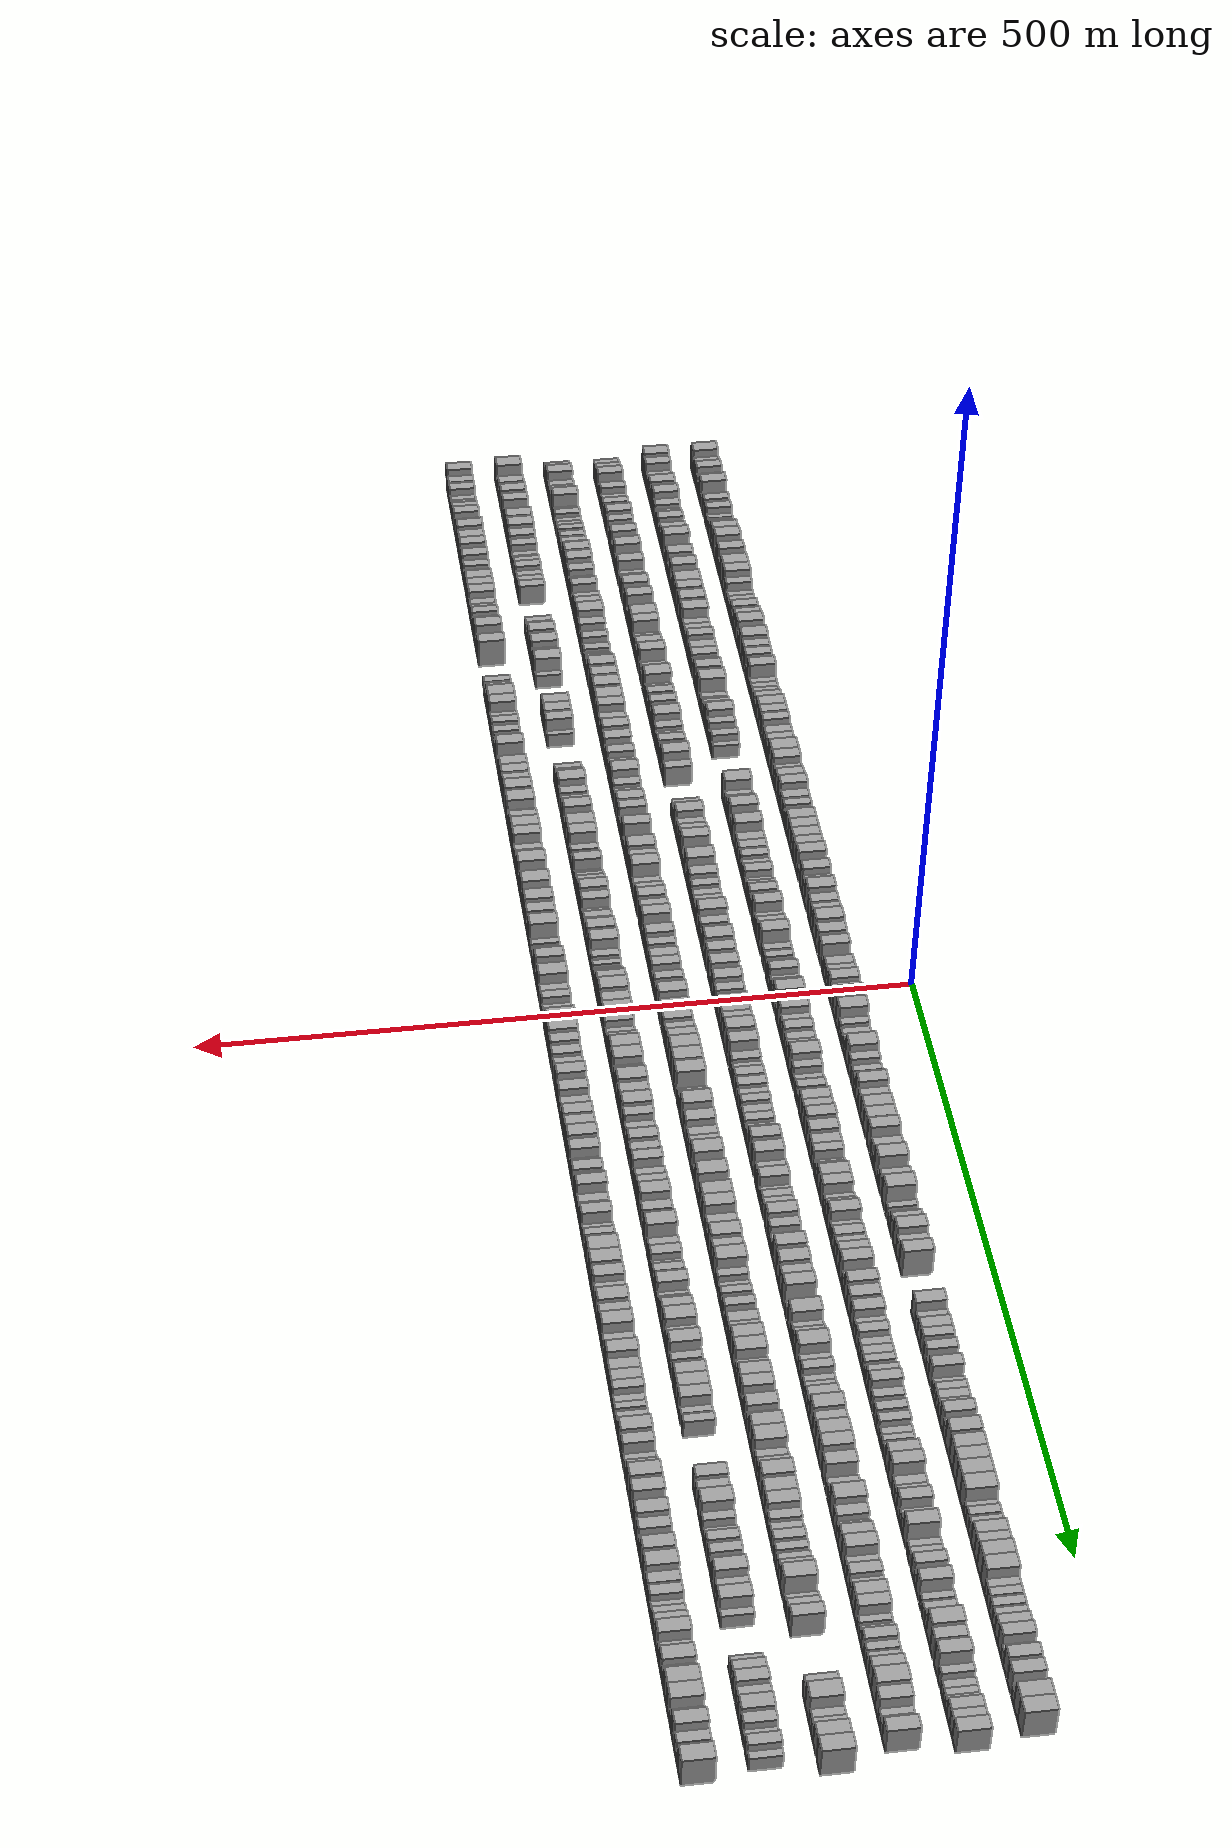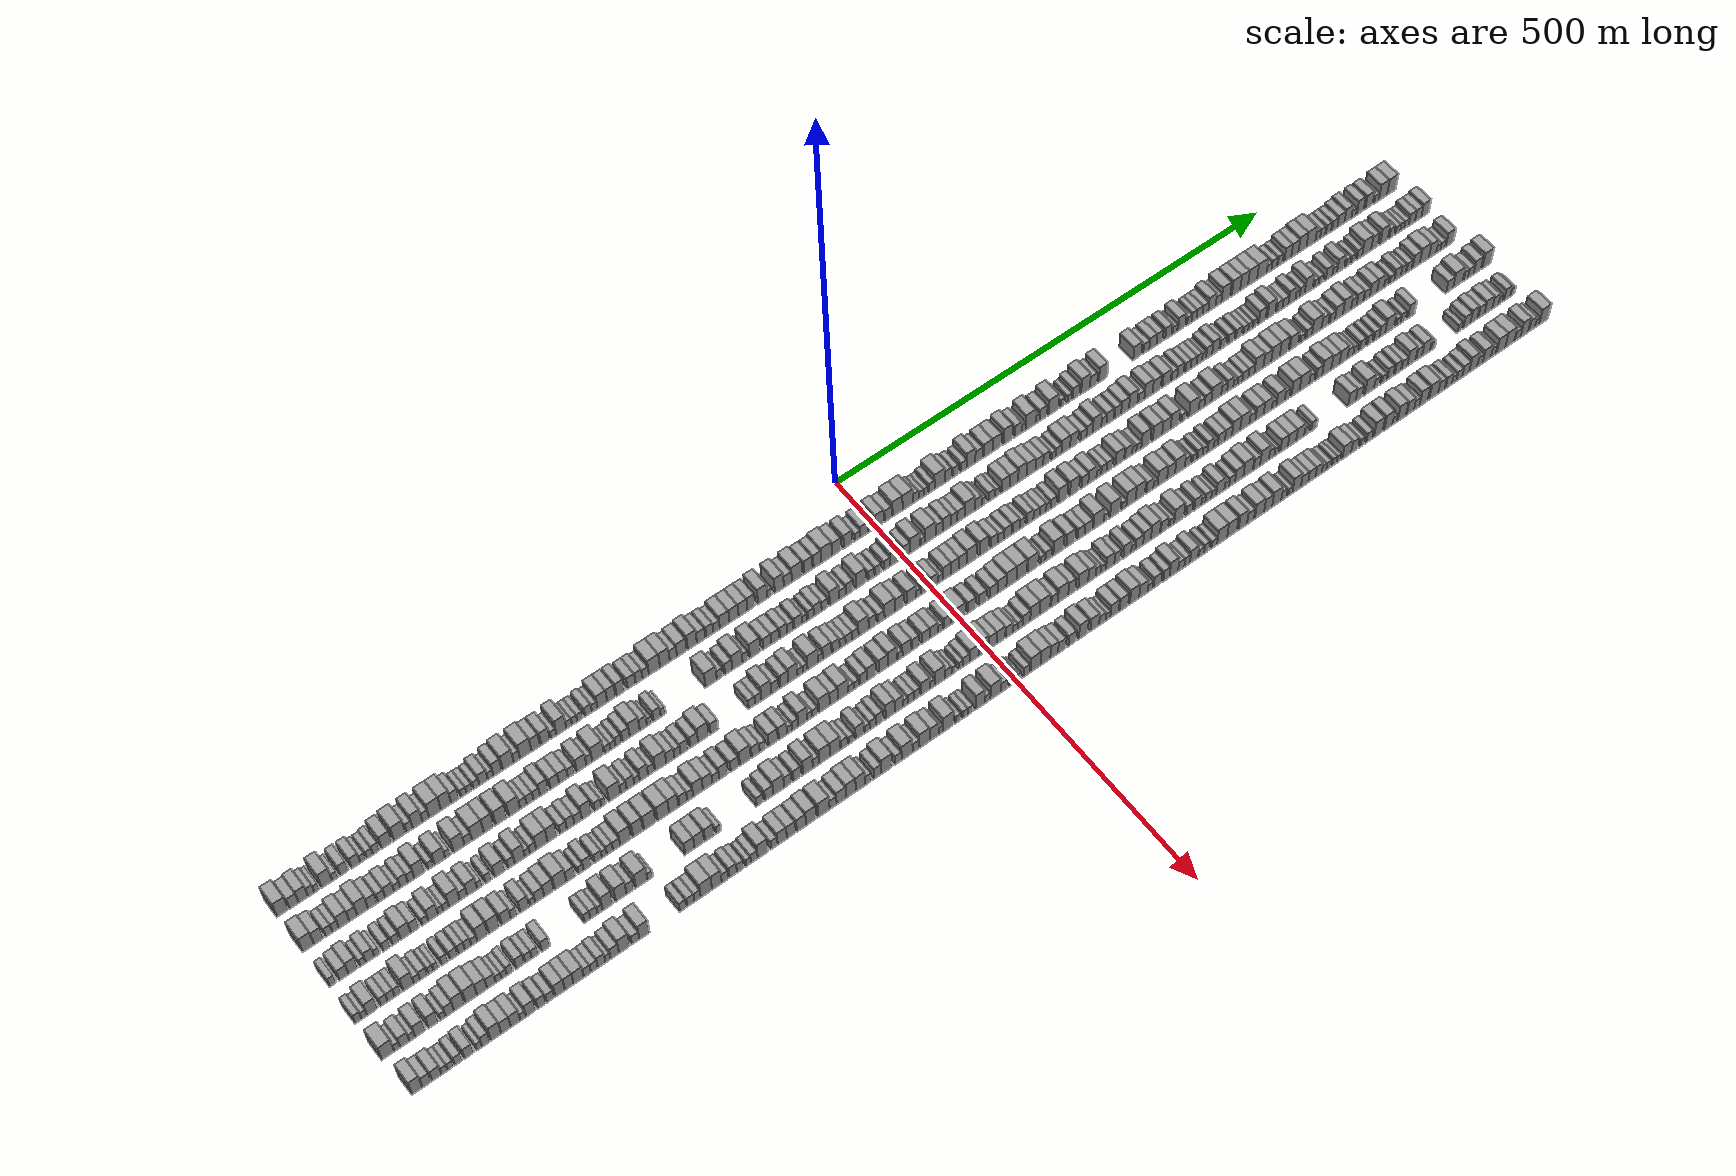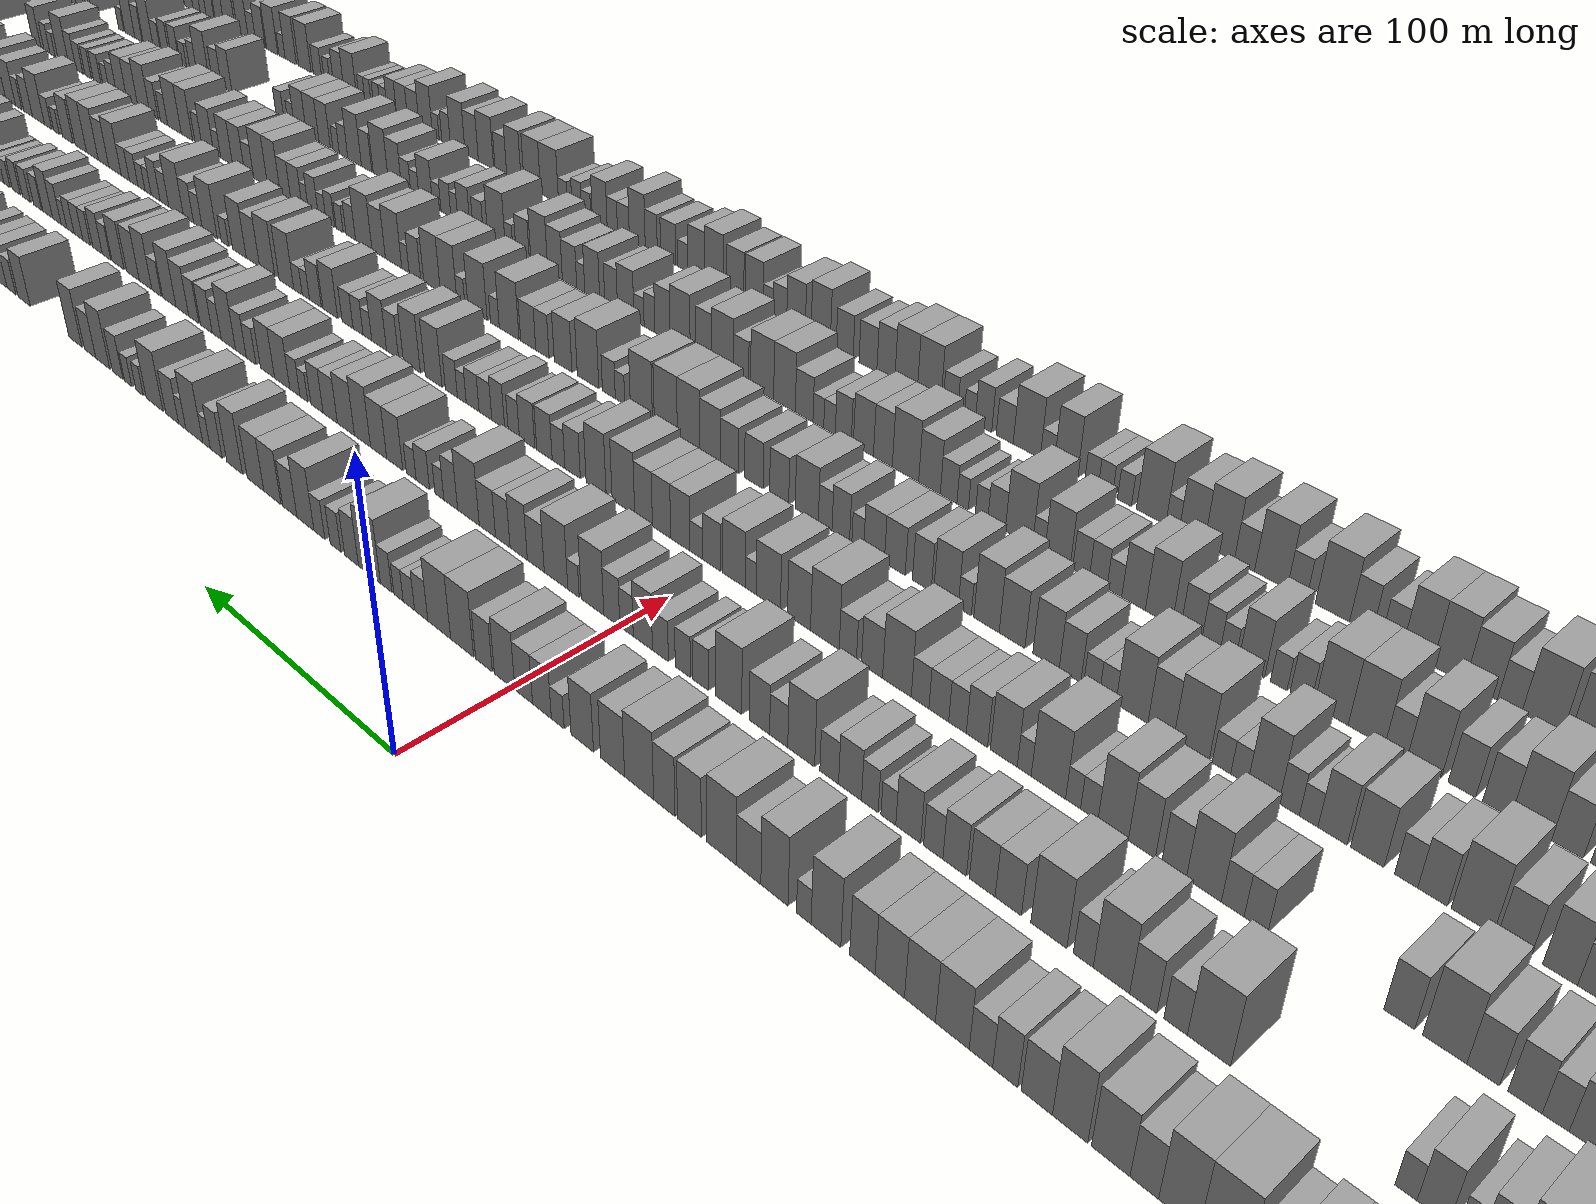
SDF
<sdf version="1.6">
 <world name="default">
  <scene>
   <sky><clouds><speed>12</speed></clouds></sky>
   <ambient>0.4 0.4 0.4 1</ambient>
   <background>0.7 0.7 0.7 1</background>
   <shadows>1</shadows>
  </scene>
  <gravity>0 0 -9.8066</gravity>
  <magnetic_field>6e-06 2.3e-05 -4.2e-05</magnetic_field>
  <physics default="0" name="default_physics" type="ode">
   <ode>
    <solver>
     <type>quick</type>
     <iters>10</iters>
     <sor>1.0</sor>
     <use_dynamic_moi_rescaling>0</use_dynamic_moi_rescaling>
    </solver>
    <constraints>
     <cfm>0</cfm>
     <erp>0.2</erp>
     <contact_max_correcting_vel>100</contact_max_correcting_vel>
     <contact_surface_layer>0.001</contact_surface_layer>
    </constraints>
   </ode>
   <max_step_size>0.004</max_step_size>
   <real_time_factor>1</real_time_factor>
   <real_time_update_rate>250</real_time_update_rate>
  </physics>
  <light name="sun" type="directional">
   <pose>0 0 10 0 0 0</pose>
   <diffuse>0.8 0.8 0.8 1</diffuse>
   <specular>0.2 0.2 0.2 1</specular>
   <attenuation>
    <range>1000</range>
    <constant>0.9</constant>
    <linear>0.01</linear>
    <quadratic>0.001</quadratic>
   </attenuation>
   <direction>-0.5 0.1 -0.9</direction>
  </light>
  <model name="building_1">
   <static>1</static>
   <pose>50.0000 -614.4221 0 0.000000 0.000000 0.000000</pose>
   <link name="link">
    <pose>0 0 12.00 0 0 0</pose>
    <collision name="collision"><geometry><box><size>20.0000 11.1559 24.0000</size></box></geometry></collision>
    <visual name="visual">
     <cast_shadows>0</cast_shadows>
     <geometry><box><size>20.0000 11.1559 24.0000</size></box></geometry>
     <material>
      <script>
       <uri>model://grey_wall/materials/scripts</uri>
       <uri>model://grey_wall/materials/textures</uri>
       <name>vrc/grey_wall</name>
      </script>
     </material>
    </visual>
   </link>
  </model>
  <model name="building_2">
   <static>1</static>
   <pose>50.0000 -603.4879 0 0.000000 0.000000 0.000000</pose>
   <link name="link">
    <pose>0 0 9.00 0 0 0</pose>
    <collision name="collision"><geometry><box><size>20.0000 8.7124 18.0000</size></box></geometry></collision>
    <visual name="visual">
     <cast_shadows>0</cast_shadows>
     <geometry><box><size>20.0000 8.7124 18.0000</size></box></geometry>
     <material>
      <script>
       <uri>model://grey_wall/materials/scripts</uri>
       <uri>model://grey_wall/materials/textures</uri>
       <name>vrc/grey_wall</name>
      </script>
     </material>
    </visual>
   </link>
  </model>
  <model name="building_3">
   <static>1</static>
   <pose>50.0000 -594.5957 0 0.000000 0.000000 0.000000</pose>
   <link name="link">
    <pose>0 0 10.50 0 0 0</pose>
    <collision name="collision"><geometry><box><size>20.0000 9.0720 21.0000</size></box></geometry></collision>
    <visual name="visual">
     <cast_shadows>0</cast_shadows>
     <geometry><box><size>20.0000 9.0720 21.0000</size></box></geometry>
     <material>
      <script>
       <uri>model://grey_wall/materials/scripts</uri>
       <uri>model://grey_wall/materials/textures</uri>
       <name>vrc/grey_wall</name>
      </script>
     </material>
    </visual>
   </link>
  </model>
  <model name="building_4">
   <static>1</static>
   <pose>50.0000 -586.9636 0 0.000000 0.000000 0.000000</pose>
   <link name="link">
    <pose>0 0 7.50 0 0 0</pose>
    <collision name="collision"><geometry><box><size>20.0000 6.1923 15.0000</size></box></geometry></collision>
    <visual name="visual">
     <cast_shadows>0</cast_shadows>
     <geometry><box><size>20.0000 6.1923 15.0000</size></box></geometry>
     <material>
      <script>
       <uri>model://grey_wall/materials/scripts</uri>
       <uri>model://grey_wall/materials/textures</uri>
       <name>vrc/grey_wall</name>
      </script>
     </material>
    </visual>
   </link>
  </model>
  <model name="building_5">
   <static>1</static>
   <pose>50.0000 -581.4569 0 0.000000 0.000000 0.000000</pose>
   <link name="link">
    <pose>0 0 6.00 0 0 0</pose>
    <collision name="collision"><geometry><box><size>20.0000 4.8212 12.0000</size></box></geometry></collision>
    <visual name="visual">
     <cast_shadows>0</cast_shadows>
     <geometry><box><size>20.0000 4.8212 12.0000</size></box></geometry>
     <material>
      <script>
       <uri>model://grey_wall/materials/scripts</uri>
       <uri>model://grey_wall/materials/textures</uri>
       <name>vrc/grey_wall</name>
      </script>
     </material>
    </visual>
   </link>
  </model>
  <model name="building_6">
   <static>1</static>
   <pose>50.0000 -571.8169 0 0.000000 0.000000 0.000000</pose>
   <link name="link">
    <pose>0 0 12.00 0 0 0</pose>
    <collision name="collision"><geometry><box><size>20.0000 10.4588 24.0000</size></box></geometry></collision>
    <visual name="visual">
     <cast_shadows>0</cast_shadows>
     <geometry><box><size>20.0000 10.4588 24.0000</size></box></geometry>
     <material>
      <script>
       <uri>model://grey_wall/materials/scripts</uri>
       <uri>model://grey_wall/materials/textures</uri>
       <name>vrc/grey_wall</name>
      </script>
     </material>
    </visual>
   </link>
  </model>
  <model name="building_7">
   <static>1</static>
   <pose>50.0000 -563.7268 0 0.000000 0.000000 0.000000</pose>
   <link name="link">
    <pose>0 0 6.00 0 0 0</pose>
    <collision name="collision"><geometry><box><size>20.0000 5.7213 12.0000</size></box></geometry></collision>
    <visual name="visual">
     <cast_shadows>0</cast_shadows>
     <geometry><box><size>20.0000 5.7213 12.0000</size></box></geometry>
     <material>
      <script>
       <uri>model://grey_wall/materials/scripts</uri>
       <uri>model://grey_wall/materials/textures</uri>
       <name>vrc/grey_wall</name>
      </script>
     </material>
    </visual>
   </link>
  </model>
  <model name="building_8">
   <static>1</static>
   <pose>50.0000 -554.8263 0 0.000000 0.000000 0.000000</pose>
   <link name="link">
    <pose>0 0 9.00 0 0 0</pose>
    <collision name="collision"><geometry><box><size>20.0000 8.0798 18.0000</size></box></geometry></collision>
    <visual name="visual">
     <cast_shadows>0</cast_shadows>
     <geometry><box><size>20.0000 8.0798 18.0000</size></box></geometry>
     <material>
      <script>
       <uri>model://grey_wall/materials/scripts</uri>
       <uri>model://grey_wall/materials/textures</uri>
       <name>vrc/grey_wall</name>
      </script>
     </material>
    </visual>
   </link>
  </model>
  <model name="building_9">
   <static>1</static>
   <pose>50.0000 -543.5676 0 0.000000 0.000000 0.000000</pose>
   <link name="link">
    <pose>0 0 9.00 0 0 0</pose>
    <collision name="collision"><geometry><box><size>20.0000 8.4376 18.0000</size></box></geometry></collision>
    <visual name="visual">
     <cast_shadows>0</cast_shadows>
     <geometry><box><size>20.0000 8.4376 18.0000</size></box></geometry>
     <material>
      <script>
       <uri>model://grey_wall/materials/scripts</uri>
       <uri>model://grey_wall/materials/textures</uri>
       <name>vrc/grey_wall</name>
      </script>
     </material>
    </visual>
   </link>
  </model>
  <model name="building_10">
   <static>1</static>
   <pose>50.0000 -536.6171 0 0.000000 0.000000 0.000000</pose>
   <link name="link">
    <pose>0 0 6.00 0 0 0</pose>
    <collision name="collision"><geometry><box><size>20.0000 5.4634 12.0000</size></box></geometry></collision>
    <visual name="visual">
     <cast_shadows>0</cast_shadows>
     <geometry><box><size>20.0000 5.4634 12.0000</size></box></geometry>
     <material>
      <script>
       <uri>model://grey_wall/materials/scripts</uri>
       <uri>model://grey_wall/materials/textures</uri>
       <name>vrc/grey_wall</name>
      </script>
     </material>
    </visual>
   </link>
  </model>
  <model name="building_11">
   <static>1</static>
   <pose>50.0000 -529.8984 0 0.000000 0.000000 0.000000</pose>
   <link name="link">
    <pose>0 0 6.00 0 0 0</pose>
    <collision name="collision"><geometry><box><size>20.0000 5.9742 12.0000</size></box></geometry></collision>
    <visual name="visual">
     <cast_shadows>0</cast_shadows>
     <geometry><box><size>20.0000 5.9742 12.0000</size></box></geometry>
     <material>
      <script>
       <uri>model://grey_wall/materials/scripts</uri>
       <uri>model://grey_wall/materials/textures</uri>
       <name>vrc/grey_wall</name>
      </script>
     </material>
    </visual>
   </link>
  </model>
  <model name="building_12">
   <static>1</static>
   <pose>50.0000 -523.6184 0 0.000000 0.000000 0.000000</pose>
   <link name="link">
    <pose>0 0 7.50 0 0 0</pose>
    <collision name="collision"><geometry><box><size>20.0000 6.5856 15.0000</size></box></geometry></collision>
    <visual name="visual">
     <cast_shadows>0</cast_shadows>
     <geometry><box><size>20.0000 6.5856 15.0000</size></box></geometry>
     <material>
      <script>
       <uri>model://grey_wall/materials/scripts</uri>
       <uri>model://grey_wall/materials/textures</uri>
       <name>vrc/grey_wall</name>
      </script>
     </material>
    </visual>
   </link>
  </model>
  <model name="building_13">
   <static>1</static>
   <pose>50.0000 -513.2922 0 0.000000 0.000000 0.000000</pose>
   <link name="link">
    <pose>0 0 10.50 0 0 0</pose>
    <collision name="collision"><geometry><box><size>20.0000 10.0668 21.0000</size></box></geometry></collision>
    <visual name="visual">
     <cast_shadows>0</cast_shadows>
     <geometry><box><size>20.0000 10.0668 21.0000</size></box></geometry>
     <material>
      <script>
       <uri>model://grey_wall/materials/scripts</uri>
       <uri>model://grey_wall/materials/textures</uri>
       <name>vrc/grey_wall</name>
      </script>
     </material>
    </visual>
   </link>
  </model>
  <model name="building_14">
   <static>1</static>
   <pose>50.0000 -500.4689 0 0.000000 0.000000 0.000000</pose>
   <link name="link">
    <pose>0 0 12.00 0 0 0</pose>
    <collision name="collision"><geometry><box><size>20.0000 11.5798 24.0000</size></box></geometry></collision>
    <visual name="visual">
     <cast_shadows>0</cast_shadows>
     <geometry><box><size>20.0000 11.5798 24.0000</size></box></geometry>
     <material>
      <script>
       <uri>model://grey_wall/materials/scripts</uri>
       <uri>model://grey_wall/materials/textures</uri>
       <name>vrc/grey_wall</name>
      </script>
     </material>
    </visual>
   </link>
  </model>
  <model name="building_15">
   <static>1</static>
   <pose>50.0000 -490.6699 0 0.000000 0.000000 0.000000</pose>
   <link name="link">
    <pose>0 0 7.50 0 0 0</pose>
    <collision name="collision"><geometry><box><size>20.0000 6.0181 15.0000</size></box></geometry></collision>
    <visual name="visual">
     <cast_shadows>0</cast_shadows>
     <geometry><box><size>20.0000 6.0181 15.0000</size></box></geometry>
     <material>
      <script>
       <uri>model://grey_wall/materials/scripts</uri>
       <uri>model://grey_wall/materials/textures</uri>
       <name>vrc/grey_wall</name>
      </script>
     </material>
    </visual>
   </link>
  </model>
  <model name="building_16">
   <static>1</static>
   <pose>50.0000 -482.7973 0 0.000000 0.000000 0.000000</pose>
   <link name="link">
    <pose>0 0 12.00 0 0 0</pose>
    <collision name="collision"><geometry><box><size>20.0000 9.7271 24.0000</size></box></geometry></collision>
    <visual name="visual">
     <cast_shadows>0</cast_shadows>
     <geometry><box><size>20.0000 9.7271 24.0000</size></box></geometry>
     <material>
      <script>
       <uri>model://grey_wall/materials/scripts</uri>
       <uri>model://grey_wall/materials/textures</uri>
       <name>vrc/grey_wall</name>
      </script>
     </material>
    </visual>
   </link>
  </model>
  <model name="building_17">
   <static>1</static>
   <pose>50.0000 -474.5949 0 0.000000 0.000000 0.000000</pose>
   <link name="link">
    <pose>0 0 7.50 0 0 0</pose>
    <collision name="collision"><geometry><box><size>20.0000 6.6777 15.0000</size></box></geometry></collision>
    <visual name="visual">
     <cast_shadows>0</cast_shadows>
     <geometry><box><size>20.0000 6.6777 15.0000</size></box></geometry>
     <material>
      <script>
       <uri>model://grey_wall/materials/scripts</uri>
       <uri>model://grey_wall/materials/textures</uri>
       <name>vrc/grey_wall</name>
      </script>
     </material>
    </visual>
   </link>
  </model>
  <model name="building_18">
   <static>1</static>
   <pose>50.0000 -465.4244 0 0.000000 0.000000 0.000000</pose>
   <link name="link">
    <pose>0 0 12.00 0 0 0</pose>
    <collision name="collision"><geometry><box><size>20.0000 11.6633 24.0000</size></box></geometry></collision>
    <visual name="visual">
     <cast_shadows>0</cast_shadows>
     <geometry><box><size>20.0000 11.6633 24.0000</size></box></geometry>
     <material>
      <script>
       <uri>model://grey_wall/materials/scripts</uri>
       <uri>model://grey_wall/materials/textures</uri>
       <name>vrc/grey_wall</name>
      </script>
     </material>
    </visual>
   </link>
  </model>
  <model name="building_19">
   <static>1</static>
   <pose>50.0000 -454.4327 0 0.000000 0.000000 0.000000</pose>
   <link name="link">
    <pose>0 0 12.00 0 0 0</pose>
    <collision name="collision"><geometry><box><size>20.0000 10.3202 24.0000</size></box></geometry></collision>
    <visual name="visual">
     <cast_shadows>0</cast_shadows>
     <geometry><box><size>20.0000 10.3202 24.0000</size></box></geometry>
     <material>
      <script>
       <uri>model://grey_wall/materials/scripts</uri>
       <uri>model://grey_wall/materials/textures</uri>
       <name>vrc/grey_wall</name>
      </script>
     </material>
    </visual>
   </link>
  </model>
  <model name="building_20">
   <static>1</static>
   <pose>50.0000 -445.3321 0 0.000000 0.000000 0.000000</pose>
   <link name="link">
    <pose>0 0 9.00 0 0 0</pose>
    <collision name="collision"><geometry><box><size>20.0000 7.8810 18.0000</size></box></geometry></collision>
    <visual name="visual">
     <cast_shadows>0</cast_shadows>
     <geometry><box><size>20.0000 7.8810 18.0000</size></box></geometry>
     <material>
      <script>
       <uri>model://grey_wall/materials/scripts</uri>
       <uri>model://grey_wall/materials/textures</uri>
       <name>vrc/grey_wall</name>
      </script>
     </material>
    </visual>
   </link>
  </model>
  <model name="building_21">
   <static>1</static>
   <pose>50.0000 -436.5982 0 0.000000 0.000000 0.000000</pose>
   <link name="link">
    <pose>0 0 6.00 0 0 0</pose>
    <collision name="collision"><geometry><box><size>20.0000 5.5867 12.0000</size></box></geometry></collision>
    <visual name="visual">
     <cast_shadows>0</cast_shadows>
     <geometry><box><size>20.0000 5.5867 12.0000</size></box></geometry>
     <material>
      <script>
       <uri>model://grey_wall/materials/scripts</uri>
       <uri>model://grey_wall/materials/textures</uri>
       <name>vrc/grey_wall</name>
      </script>
     </material>
    </visual>
   </link>
  </model>
  <model name="building_22">
   <static>1</static>
   <pose>50.0000 -430.9221 0 0.000000 0.000000 0.000000</pose>
   <link name="link">
    <pose>0 0 6.00 0 0 0</pose>
    <collision name="collision"><geometry><box><size>20.0000 5.7655 12.0000</size></box></geometry></collision>
    <visual name="visual">
     <cast_shadows>0</cast_shadows>
     <geometry><box><size>20.0000 5.7655 12.0000</size></box></geometry>
     <material>
      <script>
       <uri>model://grey_wall/materials/scripts</uri>
       <uri>model://grey_wall/materials/textures</uri>
       <name>vrc/grey_wall</name>
      </script>
     </material>
    </visual>
   </link>
  </model>
  <model name="building_23">
   <static>1</static>
   <pose>50.0000 -424.0507 0 0.000000 0.000000 0.000000</pose>
   <link name="link">
    <pose>0 0 6.00 0 0 0</pose>
    <collision name="collision"><geometry><box><size>20.0000 5.9773 12.0000</size></box></geometry></collision>
    <visual name="visual">
     <cast_shadows>0</cast_shadows>
     <geometry><box><size>20.0000 5.9773 12.0000</size></box></geometry>
     <material>
      <script>
       <uri>model://grey_wall/materials/scripts</uri>
       <uri>model://grey_wall/materials/textures</uri>
       <name>vrc/grey_wall</name>
      </script>
     </material>
    </visual>
   </link>
  </model>
  <model name="building_24">
   <static>1</static>
   <pose>50.0000 -416.7812 0 0.000000 0.000000 0.000000</pose>
   <link name="link">
    <pose>0 0 9.00 0 0 0</pose>
    <collision name="collision"><geometry><box><size>20.0000 8.5616 18.0000</size></box></geometry></collision>
    <visual name="visual">
     <cast_shadows>0</cast_shadows>
     <geometry><box><size>20.0000 8.5616 18.0000</size></box></geometry>
     <material>
      <script>
       <uri>model://grey_wall/materials/scripts</uri>
       <uri>model://grey_wall/materials/textures</uri>
       <name>vrc/grey_wall</name>
      </script>
     </material>
    </visual>
   </link>
  </model>
  <model name="building_25">
   <static>1</static>
   <pose>50.0000 -409.6881 0 0.000000 0.000000 0.000000</pose>
   <link name="link">
    <pose>0 0 6.00 0 0 0</pose>
    <collision name="collision"><geometry><box><size>20.0000 5.6246 12.0000</size></box></geometry></collision>
    <visual name="visual">
     <cast_shadows>0</cast_shadows>
     <geometry><box><size>20.0000 5.6246 12.0000</size></box></geometry>
     <material>
      <script>
       <uri>model://grey_wall/materials/scripts</uri>
       <uri>model://grey_wall/materials/textures</uri>
       <name>vrc/grey_wall</name>
      </script>
     </material>
    </visual>
   </link>
  </model>
  <model name="building_26">
   <static>1</static>
   <pose>50.0000 -402.6620 0 0.000000 0.000000 0.000000</pose>
   <link name="link">
    <pose>0 0 10.50 0 0 0</pose>
    <collision name="collision"><geometry><box><size>20.0000 8.4275 21.0000</size></box></geometry></collision>
    <visual name="visual">
     <cast_shadows>0</cast_shadows>
     <geometry><box><size>20.0000 8.4275 21.0000</size></box></geometry>
     <material>
      <script>
       <uri>model://grey_wall/materials/scripts</uri>
       <uri>model://grey_wall/materials/textures</uri>
       <name>vrc/grey_wall</name>
      </script>
     </material>
    </visual>
   </link>
  </model>
  <model name="building_27">
   <static>1</static>
   <pose>50.0000 -391.8584 0 0.000000 0.000000 0.000000</pose>
   <link name="link">
    <pose>0 0 12.00 0 0 0</pose>
    <collision name="collision"><geometry><box><size>20.0000 11.1799 24.0000</size></box></geometry></collision>
    <visual name="visual">
     <cast_shadows>0</cast_shadows>
     <geometry><box><size>20.0000 11.1799 24.0000</size></box></geometry>
     <material>
      <script>
       <uri>model://grey_wall/materials/scripts</uri>
       <uri>model://grey_wall/materials/textures</uri>
       <name>vrc/grey_wall</name>
      </script>
     </material>
    </visual>
   </link>
  </model>
  <model name="building_28">
   <static>1</static>
   <pose>50.0000 -383.1302 0 0.000000 0.000000 0.000000</pose>
   <link name="link">
    <pose>0 0 7.50 0 0 0</pose>
    <collision name="collision"><geometry><box><size>20.0000 6.2763 15.0000</size></box></geometry></collision>
    <visual name="visual">
     <cast_shadows>0</cast_shadows>
     <geometry><box><size>20.0000 6.2763 15.0000</size></box></geometry>
     <material>
      <script>
       <uri>model://grey_wall/materials/scripts</uri>
       <uri>model://grey_wall/materials/textures</uri>
       <name>vrc/grey_wall</name>
      </script>
     </material>
    </visual>
   </link>
  </model>
  <model name="building_29">
   <static>1</static>
   <pose>50.0000 -374.0557 0 0.000000 0.000000 0.000000</pose>
   <link name="link">
    <pose>0 0 12.00 0 0 0</pose>
    <collision name="collision"><geometry><box><size>20.0000 11.8728 24.0000</size></box></geometry></collision>
    <visual name="visual">
     <cast_shadows>0</cast_shadows>
     <geometry><box><size>20.0000 11.8728 24.0000</size></box></geometry>
     <material>
      <script>
       <uri>model://grey_wall/materials/scripts</uri>
       <uri>model://grey_wall/materials/textures</uri>
       <name>vrc/grey_wall</name>
      </script>
     </material>
    </visual>
   </link>
  </model>
  <model name="building_30">
   <static>1</static>
   <pose>50.0000 -363.7324 0 0.000000 0.000000 0.000000</pose>
   <link name="link">
    <pose>0 0 10.50 0 0 0</pose>
    <collision name="collision"><geometry><box><size>20.0000 8.7739 21.0000</size></box></geometry></collision>
    <visual name="visual">
     <cast_shadows>0</cast_shadows>
     <geometry><box><size>20.0000 8.7739 21.0000</size></box></geometry>
     <material>
      <script>
       <uri>model://grey_wall/materials/scripts</uri>
       <uri>model://grey_wall/materials/textures</uri>
       <name>vrc/grey_wall</name>
      </script>
     </material>
    </visual>
   </link>
  </model>
  <model name="building_31">
   <static>1</static>
   <pose>50.0000 -353.8460 0 0.000000 0.000000 0.000000</pose>
   <link name="link">
    <pose>0 0 10.50 0 0 0</pose>
    <collision name="collision"><geometry><box><size>20.0000 8.9989 21.0000</size></box></geometry></collision>
    <visual name="visual">
     <cast_shadows>0</cast_shadows>
     <geometry><box><size>20.0000 8.9989 21.0000</size></box></geometry>
     <material>
      <script>
       <uri>model://grey_wall/materials/scripts</uri>
       <uri>model://grey_wall/materials/textures</uri>
       <name>vrc/grey_wall</name>
      </script>
     </material>
    </visual>
   </link>
  </model>
  <model name="building_32">
   <static>1</static>
   <pose>50.0000 -345.4574 0 0.000000 0.000000 0.000000</pose>
   <link name="link">
    <pose>0 0 6.00 0 0 0</pose>
    <collision name="collision"><geometry><box><size>20.0000 5.7782 12.0000</size></box></geometry></collision>
    <visual name="visual">
     <cast_shadows>0</cast_shadows>
     <geometry><box><size>20.0000 5.7782 12.0000</size></box></geometry>
     <material>
      <script>
       <uri>model://grey_wall/materials/scripts</uri>
       <uri>model://grey_wall/materials/textures</uri>
       <name>vrc/grey_wall</name>
      </script>
     </material>
    </visual>
   </link>
  </model>
  <model name="building_33">
   <static>1</static>
   <pose>50.0000 -337.5259 0 0.000000 0.000000 0.000000</pose>
   <link name="link">
    <pose>0 0 12.00 0 0 0</pose>
    <collision name="collision"><geometry><box><size>20.0000 10.0848 24.0000</size></box></geometry></collision>
    <visual name="visual">
     <cast_shadows>0</cast_shadows>
     <geometry><box><size>20.0000 10.0848 24.0000</size></box></geometry>
     <material>
      <script>
       <uri>model://grey_wall/materials/scripts</uri>
       <uri>model://grey_wall/materials/textures</uri>
       <name>vrc/grey_wall</name>
      </script>
     </material>
    </visual>
   </link>
  </model>
  <model name="building_34">
   <static>1</static>
   <pose>50.0000 -329.6132 0 0.000000 0.000000 0.000000</pose>
   <link name="link">
    <pose>0 0 6.00 0 0 0</pose>
    <collision name="collision"><geometry><box><size>20.0000 5.7406 12.0000</size></box></geometry></collision>
    <visual name="visual">
     <cast_shadows>0</cast_shadows>
     <geometry><box><size>20.0000 5.7406 12.0000</size></box></geometry>
     <material>
      <script>
       <uri>model://grey_wall/materials/scripts</uri>
       <uri>model://grey_wall/materials/textures</uri>
       <name>vrc/grey_wall</name>
      </script>
     </material>
    </visual>
   </link>
  </model>
  <model name="building_35">
   <static>1</static>
   <pose>50.0000 -323.9547 0 0.000000 0.000000 0.000000</pose>
   <link name="link">
    <pose>0 0 6.00 0 0 0</pose>
    <collision name="collision"><geometry><box><size>20.0000 5.5763 12.0000</size></box></geometry></collision>
    <visual name="visual">
     <cast_shadows>0</cast_shadows>
     <geometry><box><size>20.0000 5.5763 12.0000</size></box></geometry>
     <material>
      <script>
       <uri>model://grey_wall/materials/scripts</uri>
       <uri>model://grey_wall/materials/textures</uri>
       <name>vrc/grey_wall</name>
      </script>
     </material>
    </visual>
   </link>
  </model>
  <model name="building_36">
   <static>1</static>
   <pose>50.0000 -318.2030 0 0.000000 0.000000 0.000000</pose>
   <link name="link">
    <pose>0 0 6.00 0 0 0</pose>
    <collision name="collision"><geometry><box><size>20.0000 5.9271 12.0000</size></box></geometry></collision>
    <visual name="visual">
     <cast_shadows>0</cast_shadows>
     <geometry><box><size>20.0000 5.9271 12.0000</size></box></geometry>
     <material>
      <script>
       <uri>model://grey_wall/materials/scripts</uri>
       <uri>model://grey_wall/materials/textures</uri>
       <name>vrc/grey_wall</name>
      </script>
     </material>
    </visual>
   </link>
  </model>
  <model name="building_37">
   <static>1</static>
   <pose>50.0000 -309.6669 0 0.000000 0.000000 0.000000</pose>
   <link name="link">
    <pose>0 0 7.50 0 0 0</pose>
    <collision name="collision"><geometry><box><size>20.0000 7.1453 15.0000</size></box></geometry></collision>
    <visual name="visual">
     <cast_shadows>0</cast_shadows>
     <geometry><box><size>20.0000 7.1453 15.0000</size></box></geometry>
     <material>
      <script>
       <uri>model://grey_wall/materials/scripts</uri>
       <uri>model://grey_wall/materials/textures</uri>
       <name>vrc/grey_wall</name>
      </script>
     </material>
    </visual>
   </link>
  </model>
  <model name="building_38">
   <static>1</static>
   <pose>50.0000 -303.1367 0 0.000000 0.000000 0.000000</pose>
   <link name="link">
    <pose>0 0 6.00 0 0 0</pose>
    <collision name="collision"><geometry><box><size>20.0000 5.9150 12.0000</size></box></geometry></collision>
    <visual name="visual">
     <cast_shadows>0</cast_shadows>
     <geometry><box><size>20.0000 5.9150 12.0000</size></box></geometry>
     <material>
      <script>
       <uri>model://grey_wall/materials/scripts</uri>
       <uri>model://grey_wall/materials/textures</uri>
       <name>vrc/grey_wall</name>
      </script>
     </material>
    </visual>
   </link>
  </model>
  <model name="building_39">
   <static>1</static>
   <pose>50.0000 -295.1688 0 0.000000 0.000000 0.000000</pose>
   <link name="link">
    <pose>0 0 10.50 0 0 0</pose>
    <collision name="collision"><geometry><box><size>20.0000 10.0208 21.0000</size></box></geometry></collision>
    <visual name="visual">
     <cast_shadows>0</cast_shadows>
     <geometry><box><size>20.0000 10.0208 21.0000</size></box></geometry>
     <material>
      <script>
       <uri>model://grey_wall/materials/scripts</uri>
       <uri>model://grey_wall/materials/textures</uri>
       <name>vrc/grey_wall</name>
      </script>
     </material>
    </visual>
   </link>
  </model>
  <model name="building_40">
   <static>1</static>
   <pose>50.0000 -285.7886 0 0.000000 0.000000 0.000000</pose>
   <link name="link">
    <pose>0 0 10.50 0 0 0</pose>
    <collision name="collision"><geometry><box><size>20.0000 8.7397 21.0000</size></box></geometry></collision>
    <visual name="visual">
     <cast_shadows>0</cast_shadows>
     <geometry><box><size>20.0000 8.7397 21.0000</size></box></geometry>
     <material>
      <script>
       <uri>model://grey_wall/materials/scripts</uri>
       <uri>model://grey_wall/materials/textures</uri>
       <name>vrc/grey_wall</name>
      </script>
     </material>
    </visual>
   </link>
  </model>
  <model name="building_41">
   <static>1</static>
   <pose>50.0000 -276.1720 0 0.000000 0.000000 0.000000</pose>
   <link name="link">
    <pose>0 0 10.50 0 0 0</pose>
    <collision name="collision"><geometry><box><size>20.0000 8.4935 21.0000</size></box></geometry></collision>
    <visual name="visual">
     <cast_shadows>0</cast_shadows>
     <geometry><box><size>20.0000 8.4935 21.0000</size></box></geometry>
     <material>
      <script>
       <uri>model://grey_wall/materials/scripts</uri>
       <uri>model://grey_wall/materials/textures</uri>
       <name>vrc/grey_wall</name>
      </script>
     </material>
    </visual>
   </link>
  </model>
  <model name="building_42">
   <static>1</static>
   <pose>50.0000 -264.7379 0 0.000000 0.000000 0.000000</pose>
   <link name="link">
    <pose>0 0 9.00 0 0 0</pose>
    <collision name="collision"><geometry><box><size>20.0000 8.3747 18.0000</size></box></geometry></collision>
    <visual name="visual">
     <cast_shadows>0</cast_shadows>
     <geometry><box><size>20.0000 8.3747 18.0000</size></box></geometry>
     <material>
      <script>
       <uri>model://grey_wall/materials/scripts</uri>
       <uri>model://grey_wall/materials/textures</uri>
       <name>vrc/grey_wall</name>
      </script>
     </material>
    </visual>
   </link>
  </model>
  <model name="building_43">
   <static>1</static>
   <pose>50.0000 -256.8745 0 0.000000 0.000000 0.000000</pose>
   <link name="link">
    <pose>0 0 9.00 0 0 0</pose>
    <collision name="collision"><geometry><box><size>20.0000 7.3521 18.0000</size></box></geometry></collision>
    <visual name="visual">
     <cast_shadows>0</cast_shadows>
     <geometry><box><size>20.0000 7.3521 18.0000</size></box></geometry>
     <material>
      <script>
       <uri>model://grey_wall/materials/scripts</uri>
       <uri>model://grey_wall/materials/textures</uri>
       <name>vrc/grey_wall</name>
      </script>
     </material>
    </visual>
   </link>
  </model>
  <model name="building_44">
   <static>1</static>
   <pose>50.0000 -249.8854 0 0.000000 0.000000 0.000000</pose>
   <link name="link">
    <pose>0 0 7.50 0 0 0</pose>
    <collision name="collision"><geometry><box><size>20.0000 6.6262 15.0000</size></box></geometry></collision>
    <visual name="visual">
     <cast_shadows>0</cast_shadows>
     <geometry><box><size>20.0000 6.6262 15.0000</size></box></geometry>
     <material>
      <script>
       <uri>model://grey_wall/materials/scripts</uri>
       <uri>model://grey_wall/materials/textures</uri>
       <name>vrc/grey_wall</name>
      </script>
     </material>
    </visual>
   </link>
  </model>
  <model name="building_45">
   <static>1</static>
   <pose>50.0000 -240.6551 0 0.000000 0.000000 0.000000</pose>
   <link name="link">
    <pose>0 0 12.00 0 0 0</pose>
    <collision name="collision"><geometry><box><size>20.0000 11.8344 24.0000</size></box></geometry></collision>
    <visual name="visual">
     <cast_shadows>0</cast_shadows>
     <geometry><box><size>20.0000 11.8344 24.0000</size></box></geometry>
     <material>
      <script>
       <uri>model://grey_wall/materials/scripts</uri>
       <uri>model://grey_wall/materials/textures</uri>
       <name>vrc/grey_wall</name>
      </script>
     </material>
    </visual>
   </link>
  </model>
  <model name="building_46">
   <static>1</static>
   <pose>50.0000 -229.5903 0 0.000000 0.000000 0.000000</pose>
   <link name="link">
    <pose>0 0 12.00 0 0 0</pose>
    <collision name="collision"><geometry><box><size>20.0000 10.2952 24.0000</size></box></geometry></collision>
    <visual name="visual">
     <cast_shadows>0</cast_shadows>
     <geometry><box><size>20.0000 10.2952 24.0000</size></box></geometry>
     <material>
      <script>
       <uri>model://grey_wall/materials/scripts</uri>
       <uri>model://grey_wall/materials/textures</uri>
       <name>vrc/grey_wall</name>
      </script>
     </material>
    </visual>
   </link>
  </model>
  <model name="building_47">
   <static>1</static>
   <pose>50.0000 -220.6747 0 0.000000 0.000000 0.000000</pose>
   <link name="link">
    <pose>0 0 9.00 0 0 0</pose>
    <collision name="collision"><geometry><box><size>20.0000 7.5360 18.0000</size></box></geometry></collision>
    <visual name="visual">
     <cast_shadows>0</cast_shadows>
     <geometry><box><size>20.0000 7.5360 18.0000</size></box></geometry>
     <material>
      <script>
       <uri>model://grey_wall/materials/scripts</uri>
       <uri>model://grey_wall/materials/textures</uri>
       <name>vrc/grey_wall</name>
      </script>
     </material>
    </visual>
   </link>
  </model>
  <model name="building_48">
   <static>1</static>
   <pose>50.0000 -211.6973 0 0.000000 0.000000 0.000000</pose>
   <link name="link">
    <pose>0 0 10.50 0 0 0</pose>
    <collision name="collision"><geometry><box><size>20.0000 10.4188 21.0000</size></box></geometry></collision>
    <visual name="visual">
     <cast_shadows>0</cast_shadows>
     <geometry><box><size>20.0000 10.4188 21.0000</size></box></geometry>
     <material>
      <script>
       <uri>model://grey_wall/materials/scripts</uri>
       <uri>model://grey_wall/materials/textures</uri>
       <name>vrc/grey_wall</name>
      </script>
     </material>
    </visual>
   </link>
  </model>
  <model name="building_49">
   <static>1</static>
   <pose>50.0000 -200.5732 0 0.000000 0.000000 0.000000</pose>
   <link name="link">
    <pose>0 0 12.00 0 0 0</pose>
    <collision name="collision"><geometry><box><size>20.0000 9.8295 24.0000</size></box></geometry></collision>
    <visual name="visual">
     <cast_shadows>0</cast_shadows>
     <geometry><box><size>20.0000 9.8295 24.0000</size></box></geometry>
     <material>
      <script>
       <uri>model://grey_wall/materials/scripts</uri>
       <uri>model://grey_wall/materials/textures</uri>
       <name>vrc/grey_wall</name>
      </script>
     </material>
    </visual>
   </link>
  </model>
  <model name="building_50">
   <static>1</static>
   <pose>50.0000 -191.1730 0 0.000000 0.000000 0.000000</pose>
   <link name="link">
    <pose>0 0 9.00 0 0 0</pose>
    <collision name="collision"><geometry><box><size>20.0000 8.9709 18.0000</size></box></geometry></collision>
    <visual name="visual">
     <cast_shadows>0</cast_shadows>
     <geometry><box><size>20.0000 8.9709 18.0000</size></box></geometry>
     <material>
      <script>
       <uri>model://grey_wall/materials/scripts</uri>
       <uri>model://grey_wall/materials/textures</uri>
       <name>vrc/grey_wall</name>
      </script>
     </material>
    </visual>
   </link>
  </model>
  <model name="building_51">
   <static>1</static>
   <pose>50.0000 -181.9893 0 0.000000 0.000000 0.000000</pose>
   <link name="link">
    <pose>0 0 9.00 0 0 0</pose>
    <collision name="collision"><geometry><box><size>20.0000 7.3965 18.0000</size></box></geometry></collision>
    <visual name="visual">
     <cast_shadows>0</cast_shadows>
     <geometry><box><size>20.0000 7.3965 18.0000</size></box></geometry>
     <material>
      <script>
       <uri>model://grey_wall/materials/scripts</uri>
       <uri>model://grey_wall/materials/textures</uri>
       <name>vrc/grey_wall</name>
      </script>
     </material>
    </visual>
   </link>
  </model>
  <model name="building_52">
   <static>1</static>
   <pose>50.0000 -174.7818 0 0.000000 0.000000 0.000000</pose>
   <link name="link">
    <pose>0 0 7.50 0 0 0</pose>
    <collision name="collision"><geometry><box><size>20.0000 7.0185 15.0000</size></box></geometry></collision>
    <visual name="visual">
     <cast_shadows>0</cast_shadows>
     <geometry><box><size>20.0000 7.0185 15.0000</size></box></geometry>
     <material>
      <script>
       <uri>model://grey_wall/materials/scripts</uri>
       <uri>model://grey_wall/materials/textures</uri>
       <name>vrc/grey_wall</name>
      </script>
     </material>
    </visual>
   </link>
  </model>
  <model name="building_53">
   <static>1</static>
   <pose>50.0000 -166.0844 0 0.000000 0.000000 0.000000</pose>
   <link name="link">
    <pose>0 0 10.50 0 0 0</pose>
    <collision name="collision"><geometry><box><size>20.0000 10.3764 21.0000</size></box></geometry></collision>
    <visual name="visual">
     <cast_shadows>0</cast_shadows>
     <geometry><box><size>20.0000 10.3764 21.0000</size></box></geometry>
     <material>
      <script>
       <uri>model://grey_wall/materials/scripts</uri>
       <uri>model://grey_wall/materials/textures</uri>
       <name>vrc/grey_wall</name>
      </script>
     </material>
    </visual>
   </link>
  </model>
  <model name="building_54">
   <static>1</static>
   <pose>50.0000 -156.0148 0 0.000000 0.000000 0.000000</pose>
   <link name="link">
    <pose>0 0 10.50 0 0 0</pose>
    <collision name="collision"><geometry><box><size>20.0000 9.7629 21.0000</size></box></geometry></collision>
    <visual name="visual">
     <cast_shadows>0</cast_shadows>
     <geometry><box><size>20.0000 9.7629 21.0000</size></box></geometry>
     <material>
      <script>
       <uri>model://grey_wall/materials/scripts</uri>
       <uri>model://grey_wall/materials/textures</uri>
       <name>vrc/grey_wall</name>
      </script>
     </material>
    </visual>
   </link>
  </model>
  <model name="building_55">
   <static>1</static>
   <pose>50.0000 -146.3643 0 0.000000 0.000000 0.000000</pose>
   <link name="link">
    <pose>0 0 10.50 0 0 0</pose>
    <collision name="collision"><geometry><box><size>20.0000 9.5380 21.0000</size></box></geometry></collision>
    <visual name="visual">
     <cast_shadows>0</cast_shadows>
     <geometry><box><size>20.0000 9.5380 21.0000</size></box></geometry>
     <material>
      <script>
       <uri>model://grey_wall/materials/scripts</uri>
       <uri>model://grey_wall/materials/textures</uri>
       <name>vrc/grey_wall</name>
      </script>
     </material>
    </visual>
   </link>
  </model>
  <model name="building_56">
   <static>1</static>
   <pose>50.0000 -137.3836 0 0.000000 0.000000 0.000000</pose>
   <link name="link">
    <pose>0 0 10.50 0 0 0</pose>
    <collision name="collision"><geometry><box><size>20.0000 8.4233 21.0000</size></box></geometry></collision>
    <visual name="visual">
     <cast_shadows>0</cast_shadows>
     <geometry><box><size>20.0000 8.4233 21.0000</size></box></geometry>
     <material>
      <script>
       <uri>model://grey_wall/materials/scripts</uri>
       <uri>model://grey_wall/materials/textures</uri>
       <name>vrc/grey_wall</name>
      </script>
     </material>
    </visual>
   </link>
  </model>
  <model name="building_57">
   <static>1</static>
   <pose>50.0000 -125.0789 0 0.000000 0.000000 0.000000</pose>
   <link name="link">
    <pose>0 0 12.00 0 0 0</pose>
    <collision name="collision"><geometry><box><size>20.0000 10.1862 24.0000</size></box></geometry></collision>
    <visual name="visual">
     <cast_shadows>0</cast_shadows>
     <geometry><box><size>20.0000 10.1862 24.0000</size></box></geometry>
     <material>
      <script>
       <uri>model://grey_wall/materials/scripts</uri>
       <uri>model://grey_wall/materials/textures</uri>
       <name>vrc/grey_wall</name>
      </script>
     </material>
    </visual>
   </link>
  </model>
  <model name="building_58">
   <static>1</static>
   <pose>50.0000 -117.4478 0 0.000000 0.000000 0.000000</pose>
   <link name="link">
    <pose>0 0 6.00 0 0 0</pose>
    <collision name="collision"><geometry><box><size>20.0000 5.0759 12.0000</size></box></geometry></collision>
    <visual name="visual">
     <cast_shadows>0</cast_shadows>
     <geometry><box><size>20.0000 5.0759 12.0000</size></box></geometry>
     <material>
      <script>
       <uri>model://grey_wall/materials/scripts</uri>
       <uri>model://grey_wall/materials/textures</uri>
       <name>vrc/grey_wall</name>
      </script>
     </material>
    </visual>
   </link>
  </model>
  <model name="building_59">
   <static>1</static>
   <pose>50.0000 -107.0436 0 0.000000 0.000000 0.000000</pose>
   <link name="link">
    <pose>0 0 12.00 0 0 0</pose>
    <collision name="collision"><geometry><box><size>20.0000 9.7326 24.0000</size></box></geometry></collision>
    <visual name="visual">
     <cast_shadows>0</cast_shadows>
     <geometry><box><size>20.0000 9.7326 24.0000</size></box></geometry>
     <material>
      <script>
       <uri>model://grey_wall/materials/scripts</uri>
       <uri>model://grey_wall/materials/textures</uri>
       <name>vrc/grey_wall</name>
      </script>
     </material>
    </visual>
   </link>
  </model>
  <model name="building_60">
   <static>1</static>
   <pose>50.0000 -97.7264 0 0.000000 0.000000 0.000000</pose>
   <link name="link">
    <pose>0 0 9.00 0 0 0</pose>
    <collision name="collision"><geometry><box><size>20.0000 8.9018 18.0000</size></box></geometry></collision>
    <visual name="visual">
     <cast_shadows>0</cast_shadows>
     <geometry><box><size>20.0000 8.9018 18.0000</size></box></geometry>
     <material>
      <script>
       <uri>model://grey_wall/materials/scripts</uri>
       <uri>model://grey_wall/materials/textures</uri>
       <name>vrc/grey_wall</name>
      </script>
     </material>
    </visual>
   </link>
  </model>
  <model name="building_61">
   <static>1</static>
   <pose>50.0000 -87.6133 0 0.000000 0.000000 0.000000</pose>
   <link name="link">
    <pose>0 0 12.00 0 0 0</pose>
    <collision name="collision"><geometry><box><size>20.0000 11.3243 24.0000</size></box></geometry></collision>
    <visual name="visual">
     <cast_shadows>0</cast_shadows>
     <geometry><box><size>20.0000 11.3243 24.0000</size></box></geometry>
     <material>
      <script>
       <uri>model://grey_wall/materials/scripts</uri>
       <uri>model://grey_wall/materials/textures</uri>
       <name>vrc/grey_wall</name>
      </script>
     </material>
    </visual>
   </link>
  </model>
  <model name="building_62">
   <static>1</static>
   <pose>50.0000 -75.3407 0 0.000000 0.000000 0.000000</pose>
   <link name="link">
    <pose>0 0 10.50 0 0 0</pose>
    <collision name="collision"><geometry><box><size>20.0000 9.2208 21.0000</size></box></geometry></collision>
    <visual name="visual">
     <cast_shadows>0</cast_shadows>
     <geometry><box><size>20.0000 9.2208 21.0000</size></box></geometry>
     <material>
      <script>
       <uri>model://grey_wall/materials/scripts</uri>
       <uri>model://grey_wall/materials/textures</uri>
       <name>vrc/grey_wall</name>
      </script>
     </material>
    </visual>
   </link>
  </model>
  <model name="building_63">
   <static>1</static>
   <pose>50.0000 -65.4901 0 0.000000 0.000000 0.000000</pose>
   <link name="link">
    <pose>0 0 10.50 0 0 0</pose>
    <collision name="collision"><geometry><box><size>20.0000 8.4803 21.0000</size></box></geometry></collision>
    <visual name="visual">
     <cast_shadows>0</cast_shadows>
     <geometry><box><size>20.0000 8.4803 21.0000</size></box></geometry>
     <material>
      <script>
       <uri>model://grey_wall/materials/scripts</uri>
       <uri>model://grey_wall/materials/textures</uri>
       <name>vrc/grey_wall</name>
      </script>
     </material>
    </visual>
   </link>
  </model>
  <model name="building_64">
   <static>1</static>
   <pose>50.0000 -55.3311 0 0.000000 0.000000 0.000000</pose>
   <link name="link">
    <pose>0 0 12.00 0 0 0</pose>
    <collision name="collision"><geometry><box><size>20.0000 11.8376 24.0000</size></box></geometry></collision>
    <visual name="visual">
     <cast_shadows>0</cast_shadows>
     <geometry><box><size>20.0000 11.8376 24.0000</size></box></geometry>
     <material>
      <script>
       <uri>model://grey_wall/materials/scripts</uri>
       <uri>model://grey_wall/materials/textures</uri>
       <name>vrc/grey_wall</name>
      </script>
     </material>
    </visual>
   </link>
  </model>
  <model name="building_65">
   <static>1</static>
   <pose>50.0000 -44.3871 0 0.000000 0.000000 0.000000</pose>
   <link name="link">
    <pose>0 0 10.50 0 0 0</pose>
    <collision name="collision"><geometry><box><size>20.0000 10.0504 21.0000</size></box></geometry></collision>
    <visual name="visual">
     <cast_shadows>0</cast_shadows>
     <geometry><box><size>20.0000 10.0504 21.0000</size></box></geometry>
     <material>
      <script>
       <uri>model://grey_wall/materials/scripts</uri>
       <uri>model://grey_wall/materials/textures</uri>
       <name>vrc/grey_wall</name>
      </script>
     </material>
    </visual>
   </link>
  </model>
  <model name="building_66">
   <static>1</static>
   <pose>50.0000 -31.5351 0 0.000000 0.000000 0.000000</pose>
   <link name="link">
    <pose>0 0 10.50 0 0 0</pose>
    <collision name="collision"><geometry><box><size>20.0000 9.6536 21.0000</size></box></geometry></collision>
    <visual name="visual">
     <cast_shadows>0</cast_shadows>
     <geometry><box><size>20.0000 9.6536 21.0000</size></box></geometry>
     <material>
      <script>
       <uri>model://grey_wall/materials/scripts</uri>
       <uri>model://grey_wall/materials/textures</uri>
       <name>vrc/grey_wall</name>
      </script>
     </material>
    </visual>
   </link>
  </model>
  <model name="building_67">
   <static>1</static>
   <pose>50.0000 -20.8700 0 0.000000 0.000000 0.000000</pose>
   <link name="link">
    <pose>0 0 6.00 0 0 0</pose>
    <collision name="collision"><geometry><box><size>20.0000 5.6766 12.0000</size></box></geometry></collision>
    <visual name="visual">
     <cast_shadows>0</cast_shadows>
     <geometry><box><size>20.0000 5.6766 12.0000</size></box></geometry>
     <material>
      <script>
       <uri>model://grey_wall/materials/scripts</uri>
       <uri>model://grey_wall/materials/textures</uri>
       <name>vrc/grey_wall</name>
      </script>
     </material>
    </visual>
   </link>
  </model>
  <model name="building_68">
   <static>1</static>
   <pose>50.0000 -13.8137 0 0.000000 0.000000 0.000000</pose>
   <link name="link">
    <pose>0 0 9.00 0 0 0</pose>
    <collision name="collision"><geometry><box><size>20.0000 8.4360 18.0000</size></box></geometry></collision>
    <visual name="visual">
     <cast_shadows>0</cast_shadows>
     <geometry><box><size>20.0000 8.4360 18.0000</size></box></geometry>
     <material>
      <script>
       <uri>model://grey_wall/materials/scripts</uri>
       <uri>model://grey_wall/materials/textures</uri>
       <name>vrc/grey_wall</name>
      </script>
     </material>
    </visual>
   </link>
  </model>
  <model name="building_69">
   <static>1</static>
   <pose>50.0000 -5.5843 0 0.000000 0.000000 0.000000</pose>
   <link name="link">
    <pose>0 0 9.00 0 0 0</pose>
    <collision name="collision"><geometry><box><size>20.0000 8.0227 18.0000</size></box></geometry></collision>
    <visual name="visual">
     <cast_shadows>0</cast_shadows>
     <geometry><box><size>20.0000 8.0227 18.0000</size></box></geometry>
     <material>
      <script>
       <uri>model://grey_wall/materials/scripts</uri>
       <uri>model://grey_wall/materials/textures</uri>
       <name>vrc/grey_wall</name>
      </script>
     </material>
    </visual>
   </link>
  </model>
  <model name="building_70">
   <static>1</static>
   <pose>50.0000 3.2155 0 0.000000 0.000000 0.000000</pose>
   <link name="link">
    <pose>0 0 10.50 0 0 0</pose>
    <collision name="collision"><geometry><box><size>20.0000 9.5771 21.0000</size></box></geometry></collision>
    <visual name="visual">
     <cast_shadows>0</cast_shadows>
     <geometry><box><size>20.0000 9.5771 21.0000</size></box></geometry>
     <material>
      <script>
       <uri>model://grey_wall/materials/scripts</uri>
       <uri>model://grey_wall/materials/textures</uri>
       <name>vrc/grey_wall</name>
      </script>
     </material>
    </visual>
   </link>
  </model>
  <model name="building_71">
   <static>1</static>
   <pose>50.0000 12.9511 0 0.000000 0.000000 0.000000</pose>
   <link name="link">
    <pose>0 0 9.00 0 0 0</pose>
    <collision name="collision"><geometry><box><size>20.0000 7.8941 18.0000</size></box></geometry></collision>
    <visual name="visual">
     <cast_shadows>0</cast_shadows>
     <geometry><box><size>20.0000 7.8941 18.0000</size></box></geometry>
     <material>
      <script>
       <uri>model://grey_wall/materials/scripts</uri>
       <uri>model://grey_wall/materials/textures</uri>
       <name>vrc/grey_wall</name>
      </script>
     </material>
    </visual>
   </link>
  </model>
  <model name="building_72">
   <static>1</static>
   <pose>50.0000 23.4924 0 0.000000 0.000000 0.000000</pose>
   <link name="link">
    <pose>0 0 12.00 0 0 0</pose>
    <collision name="collision"><geometry><box><size>20.0000 11.1885 24.0000</size></box></geometry></collision>
    <visual name="visual">
     <cast_shadows>0</cast_shadows>
     <geometry><box><size>20.0000 11.1885 24.0000</size></box></geometry>
     <material>
      <script>
       <uri>model://grey_wall/materials/scripts</uri>
       <uri>model://grey_wall/materials/textures</uri>
       <name>vrc/grey_wall</name>
      </script>
     </material>
    </visual>
   </link>
  </model>
  <model name="building_73">
   <static>1</static>
   <pose>50.0000 34.7807 0 0.000000 0.000000 0.000000</pose>
   <link name="link">
    <pose>0 0 12.00 0 0 0</pose>
    <collision name="collision"><geometry><box><size>20.0000 11.3881 24.0000</size></box></geometry></collision>
    <visual name="visual">
     <cast_shadows>0</cast_shadows>
     <geometry><box><size>20.0000 11.3881 24.0000</size></box></geometry>
     <material>
      <script>
       <uri>model://grey_wall/materials/scripts</uri>
       <uri>model://grey_wall/materials/textures</uri>
       <name>vrc/grey_wall</name>
      </script>
     </material>
    </visual>
   </link>
  </model>
  <model name="building_74">
   <static>1</static>
   <pose>50.0000 43.8374 0 0.000000 0.000000 0.000000</pose>
   <link name="link">
    <pose>0 0 7.50 0 0 0</pose>
    <collision name="collision"><geometry><box><size>20.0000 6.7253 15.0000</size></box></geometry></collision>
    <visual name="visual">
     <cast_shadows>0</cast_shadows>
     <geometry><box><size>20.0000 6.7253 15.0000</size></box></geometry>
     <material>
      <script>
       <uri>model://grey_wall/materials/scripts</uri>
       <uri>model://grey_wall/materials/textures</uri>
       <name>vrc/grey_wall</name>
      </script>
     </material>
    </visual>
   </link>
  </model>
  <model name="building_75">
   <static>1</static>
   <pose>50.0000 50.1572 0 0.000000 0.000000 0.000000</pose>
   <link name="link">
    <pose>0 0 6.00 0 0 0</pose>
    <collision name="collision"><geometry><box><size>20.0000 5.9144 12.0000</size></box></geometry></collision>
    <visual name="visual">
     <cast_shadows>0</cast_shadows>
     <geometry><box><size>20.0000 5.9144 12.0000</size></box></geometry>
     <material>
      <script>
       <uri>model://grey_wall/materials/scripts</uri>
       <uri>model://grey_wall/materials/textures</uri>
       <name>vrc/grey_wall</name>
      </script>
     </material>
    </visual>
   </link>
  </model>
  <model name="building_76">
   <static>1</static>
   <pose>50.0000 55.5147 0 0.000000 0.000000 0.000000</pose>
   <link name="link">
    <pose>0 0 6.00 0 0 0</pose>
    <collision name="collision"><geometry><box><size>20.0000 4.8005 12.0000</size></box></geometry></collision>
    <visual name="visual">
     <cast_shadows>0</cast_shadows>
     <geometry><box><size>20.0000 4.8005 12.0000</size></box></geometry>
     <material>
      <script>
       <uri>model://grey_wall/materials/scripts</uri>
       <uri>model://grey_wall/materials/textures</uri>
       <name>vrc/grey_wall</name>
      </script>
     </material>
    </visual>
   </link>
  </model>
  <model name="building_77">
   <static>1</static>
   <pose>50.0000 61.9833 0 0.000000 0.000000 0.000000</pose>
   <link name="link">
    <pose>0 0 7.50 0 0 0</pose>
    <collision name="collision"><geometry><box><size>20.0000 6.1368 15.0000</size></box></geometry></collision>
    <visual name="visual">
     <cast_shadows>0</cast_shadows>
     <geometry><box><size>20.0000 6.1368 15.0000</size></box></geometry>
     <material>
      <script>
       <uri>model://grey_wall/materials/scripts</uri>
       <uri>model://grey_wall/materials/textures</uri>
       <name>vrc/grey_wall</name>
      </script>
     </material>
    </visual>
   </link>
  </model>
  <model name="building_78">
   <static>1</static>
   <pose>50.0000 70.9636 0 0.000000 0.000000 0.000000</pose>
   <link name="link">
    <pose>0 0 12.00 0 0 0</pose>
    <collision name="collision"><geometry><box><size>20.0000 11.8237 24.0000</size></box></geometry></collision>
    <visual name="visual">
     <cast_shadows>0</cast_shadows>
     <geometry><box><size>20.0000 11.8237 24.0000</size></box></geometry>
     <material>
      <script>
       <uri>model://grey_wall/materials/scripts</uri>
       <uri>model://grey_wall/materials/textures</uri>
       <name>vrc/grey_wall</name>
      </script>
     </material>
    </visual>
   </link>
  </model>
  <model name="building_79">
   <static>1</static>
   <pose>50.0000 80.6957 0 0.000000 0.000000 0.000000</pose>
   <link name="link">
    <pose>0 0 9.00 0 0 0</pose>
    <collision name="collision"><geometry><box><size>20.0000 7.6407 18.0000</size></box></geometry></collision>
    <visual name="visual">
     <cast_shadows>0</cast_shadows>
     <geometry><box><size>20.0000 7.6407 18.0000</size></box></geometry>
     <material>
      <script>
       <uri>model://grey_wall/materials/scripts</uri>
       <uri>model://grey_wall/materials/textures</uri>
       <name>vrc/grey_wall</name>
      </script>
     </material>
    </visual>
   </link>
  </model>
  <model name="building_80">
   <static>1</static>
   <pose>50.0000 89.5349 0 0.000000 0.000000 0.000000</pose>
   <link name="link">
    <pose>0 0 7.50 0 0 0</pose>
    <collision name="collision"><geometry><box><size>20.0000 6.0376 15.0000</size></box></geometry></collision>
    <visual name="visual">
     <cast_shadows>0</cast_shadows>
     <geometry><box><size>20.0000 6.0376 15.0000</size></box></geometry>
     <material>
      <script>
       <uri>model://grey_wall/materials/scripts</uri>
       <uri>model://grey_wall/materials/textures</uri>
       <name>vrc/grey_wall</name>
      </script>
     </material>
    </visual>
   </link>
  </model>
  <model name="building_81">
   <static>1</static>
   <pose>50.0000 98.6666 0 0.000000 0.000000 0.000000</pose>
   <link name="link">
    <pose>0 0 7.50 0 0 0</pose>
    <collision name="collision"><geometry><box><size>20.0000 6.2260 15.0000</size></box></geometry></collision>
    <visual name="visual">
     <cast_shadows>0</cast_shadows>
     <geometry><box><size>20.0000 6.2260 15.0000</size></box></geometry>
     <material>
      <script>
       <uri>model://grey_wall/materials/scripts</uri>
       <uri>model://grey_wall/materials/textures</uri>
       <name>vrc/grey_wall</name>
      </script>
     </material>
    </visual>
   </link>
  </model>
  <model name="building_82">
   <static>1</static>
   <pose>50.0000 106.6882 0 0.000000 0.000000 0.000000</pose>
   <link name="link">
    <pose>0 0 12.00 0 0 0</pose>
    <collision name="collision"><geometry><box><size>20.0000 9.8171 24.0000</size></box></geometry></collision>
    <visual name="visual">
     <cast_shadows>0</cast_shadows>
     <geometry><box><size>20.0000 9.8171 24.0000</size></box></geometry>
     <material>
      <script>
       <uri>model://grey_wall/materials/scripts</uri>
       <uri>model://grey_wall/materials/textures</uri>
       <name>vrc/grey_wall</name>
      </script>
     </material>
    </visual>
   </link>
  </model>
  <model name="building_83">
   <static>1</static>
   <pose>50.0000 115.8136 0 0.000000 0.000000 0.000000</pose>
   <link name="link">
    <pose>0 0 9.00 0 0 0</pose>
    <collision name="collision"><geometry><box><size>20.0000 8.4338 18.0000</size></box></geometry></collision>
    <visual name="visual">
     <cast_shadows>0</cast_shadows>
     <geometry><box><size>20.0000 8.4338 18.0000</size></box></geometry>
     <material>
      <script>
       <uri>model://grey_wall/materials/scripts</uri>
       <uri>model://grey_wall/materials/textures</uri>
       <name>vrc/grey_wall</name>
      </script>
     </material>
    </visual>
   </link>
  </model>
  <model name="building_84">
   <static>1</static>
   <pose>50.0000 126.2020 0 0.000000 0.000000 0.000000</pose>
   <link name="link">
    <pose>0 0 10.50 0 0 0</pose>
    <collision name="collision"><geometry><box><size>20.0000 10.3431 21.0000</size></box></geometry></collision>
    <visual name="visual">
     <cast_shadows>0</cast_shadows>
     <geometry><box><size>20.0000 10.3431 21.0000</size></box></geometry>
     <material>
      <script>
       <uri>model://grey_wall/materials/scripts</uri>
       <uri>model://grey_wall/materials/textures</uri>
       <name>vrc/grey_wall</name>
      </script>
     </material>
    </visual>
   </link>
  </model>
  <model name="building_85">
   <static>1</static>
   <pose>50.0000 136.4455 0 0.000000 0.000000 0.000000</pose>
   <link name="link">
    <pose>0 0 10.50 0 0 0</pose>
    <collision name="collision"><geometry><box><size>20.0000 10.1439 21.0000</size></box></geometry></collision>
    <visual name="visual">
     <cast_shadows>0</cast_shadows>
     <geometry><box><size>20.0000 10.1439 21.0000</size></box></geometry>
     <material>
      <script>
       <uri>model://grey_wall/materials/scripts</uri>
       <uri>model://grey_wall/materials/textures</uri>
       <name>vrc/grey_wall</name>
      </script>
     </material>
    </visual>
   </link>
  </model>
  <model name="building_86">
   <static>1</static>
   <pose>50.0000 149.4712 0 0.000000 0.000000 0.000000</pose>
   <link name="link">
    <pose>0 0 12.00 0 0 0</pose>
    <collision name="collision"><geometry><box><size>20.0000 9.9075 24.0000</size></box></geometry></collision>
    <visual name="visual">
     <cast_shadows>0</cast_shadows>
     <geometry><box><size>20.0000 9.9075 24.0000</size></box></geometry>
     <material>
      <script>
       <uri>model://grey_wall/materials/scripts</uri>
       <uri>model://grey_wall/materials/textures</uri>
       <name>vrc/grey_wall</name>
      </script>
     </material>
    </visual>
   </link>
  </model>
  <model name="building_87">
   <static>1</static>
   <pose>50.0000 161.2207 0 0.000000 0.000000 0.000000</pose>
   <link name="link">
    <pose>0 0 9.00 0 0 0</pose>
    <collision name="collision"><geometry><box><size>20.0000 7.5915 18.0000</size></box></geometry></collision>
    <visual name="visual">
     <cast_shadows>0</cast_shadows>
     <geometry><box><size>20.0000 7.5915 18.0000</size></box></geometry>
     <material>
      <script>
       <uri>model://grey_wall/materials/scripts</uri>
       <uri>model://grey_wall/materials/textures</uri>
       <name>vrc/grey_wall</name>
      </script>
     </material>
    </visual>
   </link>
  </model>
  <model name="building_88">
   <static>1</static>
   <pose>50.0000 167.4678 0 0.000000 0.000000 0.000000</pose>
   <link name="link">
    <pose>0 0 6.00 0 0 0</pose>
    <collision name="collision"><geometry><box><size>20.0000 4.9027 12.0000</size></box></geometry></collision>
    <visual name="visual">
     <cast_shadows>0</cast_shadows>
     <geometry><box><size>20.0000 4.9027 12.0000</size></box></geometry>
     <material>
      <script>
       <uri>model://grey_wall/materials/scripts</uri>
       <uri>model://grey_wall/materials/textures</uri>
       <name>vrc/grey_wall</name>
      </script>
     </material>
    </visual>
   </link>
  </model>
  <model name="building_89">
   <static>1</static>
   <pose>50.0000 175.5026 0 0.000000 0.000000 0.000000</pose>
   <link name="link">
    <pose>0 0 12.00 0 0 0</pose>
    <collision name="collision"><geometry><box><size>20.0000 11.1671 24.0000</size></box></geometry></collision>
    <visual name="visual">
     <cast_shadows>0</cast_shadows>
     <geometry><box><size>20.0000 11.1671 24.0000</size></box></geometry>
     <material>
      <script>
       <uri>model://grey_wall/materials/scripts</uri>
       <uri>model://grey_wall/materials/textures</uri>
       <name>vrc/grey_wall</name>
      </script>
     </material>
    </visual>
   </link>
  </model>
  <model name="building_90">
   <static>1</static>
   <pose>50.0000 183.5090 0 0.000000 0.000000 0.000000</pose>
   <link name="link">
    <pose>0 0 6.00 0 0 0</pose>
    <collision name="collision"><geometry><box><size>20.0000 4.8456 12.0000</size></box></geometry></collision>
    <visual name="visual">
     <cast_shadows>0</cast_shadows>
     <geometry><box><size>20.0000 4.8456 12.0000</size></box></geometry>
     <material>
      <script>
       <uri>model://grey_wall/materials/scripts</uri>
       <uri>model://grey_wall/materials/textures</uri>
       <name>vrc/grey_wall</name>
      </script>
     </material>
    </visual>
   </link>
  </model>
  <model name="building_91">
   <static>1</static>
   <pose>50.0000 190.2641 0 0.000000 0.000000 0.000000</pose>
   <link name="link">
    <pose>0 0 9.00 0 0 0</pose>
    <collision name="collision"><geometry><box><size>20.0000 8.6647 18.0000</size></box></geometry></collision>
    <visual name="visual">
     <cast_shadows>0</cast_shadows>
     <geometry><box><size>20.0000 8.6647 18.0000</size></box></geometry>
     <material>
      <script>
       <uri>model://grey_wall/materials/scripts</uri>
       <uri>model://grey_wall/materials/textures</uri>
       <name>vrc/grey_wall</name>
      </script>
     </material>
    </visual>
   </link>
  </model>
  <model name="building_92">
   <static>1</static>
   <pose>50.0000 202.4244 0 0.000000 0.000000 0.000000</pose>
   <link name="link">
    <pose>0 0 12.00 0 0 0</pose>
    <collision name="collision"><geometry><box><size>20.0000 11.6558 24.0000</size></box></geometry></collision>
    <visual name="visual">
     <cast_shadows>0</cast_shadows>
     <geometry><box><size>20.0000 11.6558 24.0000</size></box></geometry>
     <material>
      <script>
       <uri>model://grey_wall/materials/scripts</uri>
       <uri>model://grey_wall/materials/textures</uri>
       <name>vrc/grey_wall</name>
      </script>
     </material>
    </visual>
   </link>
  </model>
  <model name="building_93">
   <static>1</static>
   <pose>50.0000 212.9079 0 0.000000 0.000000 0.000000</pose>
   <link name="link">
    <pose>0 0 6.00 0 0 0</pose>
    <collision name="collision"><geometry><box><size>20.0000 5.3112 12.0000</size></box></geometry></collision>
    <visual name="visual">
     <cast_shadows>0</cast_shadows>
     <geometry><box><size>20.0000 5.3112 12.0000</size></box></geometry>
     <material>
      <script>
       <uri>model://grey_wall/materials/scripts</uri>
       <uri>model://grey_wall/materials/textures</uri>
       <name>vrc/grey_wall</name>
      </script>
     </material>
    </visual>
   </link>
  </model>
  <model name="building_94">
   <static>1</static>
   <pose>50.0000 221.1728 0 0.000000 0.000000 0.000000</pose>
   <link name="link">
    <pose>0 0 6.00 0 0 0</pose>
    <collision name="collision"><geometry><box><size>20.0000 5.2186 12.0000</size></box></geometry></collision>
    <visual name="visual">
     <cast_shadows>0</cast_shadows>
     <geometry><box><size>20.0000 5.2186 12.0000</size></box></geometry>
     <material>
      <script>
       <uri>model://grey_wall/materials/scripts</uri>
       <uri>model://grey_wall/materials/textures</uri>
       <name>vrc/grey_wall</name>
      </script>
     </material>
    </visual>
   </link>
  </model>
  <model name="building_95">
   <static>1</static>
   <pose>50.0000 228.6493 0 0.000000 0.000000 0.000000</pose>
   <link name="link">
    <pose>0 0 9.00 0 0 0</pose>
    <collision name="collision"><geometry><box><size>20.0000 7.7344 18.0000</size></box></geometry></collision>
    <visual name="visual">
     <cast_shadows>0</cast_shadows>
     <geometry><box><size>20.0000 7.7344 18.0000</size></box></geometry>
     <material>
      <script>
       <uri>model://grey_wall/materials/scripts</uri>
       <uri>model://grey_wall/materials/textures</uri>
       <name>vrc/grey_wall</name>
      </script>
     </material>
    </visual>
   </link>
  </model>
  <model name="building_96">
   <static>1</static>
   <pose>50.0000 239.6953 0 0.000000 0.000000 0.000000</pose>
   <link name="link">
    <pose>0 0 12.00 0 0 0</pose>
    <collision name="collision"><geometry><box><size>20.0000 10.3576 24.0000</size></box></geometry></collision>
    <visual name="visual">
     <cast_shadows>0</cast_shadows>
     <geometry><box><size>20.0000 10.3576 24.0000</size></box></geometry>
     <material>
      <script>
       <uri>model://grey_wall/materials/scripts</uri>
       <uri>model://grey_wall/materials/textures</uri>
       <name>vrc/grey_wall</name>
      </script>
     </material>
    </visual>
   </link>
  </model>
  <model name="building_97">
   <static>1</static>
   <pose>50.0000 249.1597 0 0.000000 0.000000 0.000000</pose>
   <link name="link">
    <pose>0 0 9.00 0 0 0</pose>
    <collision name="collision"><geometry><box><size>20.0000 8.5712 18.0000</size></box></geometry></collision>
    <visual name="visual">
     <cast_shadows>0</cast_shadows>
     <geometry><box><size>20.0000 8.5712 18.0000</size></box></geometry>
     <material>
      <script>
       <uri>model://grey_wall/materials/scripts</uri>
       <uri>model://grey_wall/materials/textures</uri>
       <name>vrc/grey_wall</name>
      </script>
     </material>
    </visual>
   </link>
  </model>
  <model name="building_98">
   <static>1</static>
   <pose>50.0000 260.4340 0 0.000000 0.000000 0.000000</pose>
   <link name="link">
    <pose>0 0 12.00 0 0 0</pose>
    <collision name="collision"><geometry><box><size>20.0000 9.9774 24.0000</size></box></geometry></collision>
    <visual name="visual">
     <cast_shadows>0</cast_shadows>
     <geometry><box><size>20.0000 9.9774 24.0000</size></box></geometry>
     <material>
      <script>
       <uri>model://grey_wall/materials/scripts</uri>
       <uri>model://grey_wall/materials/textures</uri>
       <name>vrc/grey_wall</name>
      </script>
     </material>
    </visual>
   </link>
  </model>
  <model name="building_99">
   <static>1</static>
   <pose>50.0000 301.2675 0 0.000000 0.000000 0.000000</pose>
   <link name="link">
    <pose>0 0 10.50 0 0 0</pose>
    <collision name="collision"><geometry><box><size>20.0000 9.8966 21.0000</size></box></geometry></collision>
    <visual name="visual">
     <cast_shadows>0</cast_shadows>
     <geometry><box><size>20.0000 9.8966 21.0000</size></box></geometry>
     <material>
      <script>
       <uri>model://grey_wall/materials/scripts</uri>
       <uri>model://grey_wall/materials/textures</uri>
       <name>vrc/grey_wall</name>
      </script>
     </material>
    </visual>
   </link>
  </model>
  <model name="building_100">
   <static>1</static>
   <pose>50.0000 311.8650 0 0.000000 0.000000 0.000000</pose>
   <link name="link">
    <pose>0 0 7.50 0 0 0</pose>
    <collision name="collision"><geometry><box><size>20.0000 7.2984 15.0000</size></box></geometry></collision>
    <visual name="visual">
     <cast_shadows>0</cast_shadows>
     <geometry><box><size>20.0000 7.2984 15.0000</size></box></geometry>
     <material>
      <script>
       <uri>model://grey_wall/materials/scripts</uri>
       <uri>model://grey_wall/materials/textures</uri>
       <name>vrc/grey_wall</name>
      </script>
     </material>
    </visual>
   </link>
  </model>
  <model name="building_101">
   <static>1</static>
   <pose>50.0000 319.8413 0 0.000000 0.000000 0.000000</pose>
   <link name="link">
    <pose>0 0 9.00 0 0 0</pose>
    <collision name="collision"><geometry><box><size>20.0000 8.6542 18.0000</size></box></geometry></collision>
    <visual name="visual">
     <cast_shadows>0</cast_shadows>
     <geometry><box><size>20.0000 8.6542 18.0000</size></box></geometry>
     <material>
      <script>
       <uri>model://grey_wall/materials/scripts</uri>
       <uri>model://grey_wall/materials/textures</uri>
       <name>vrc/grey_wall</name>
      </script>
     </material>
    </visual>
   </link>
  </model>
  <model name="building_102">
   <static>1</static>
   <pose>50.0000 327.9459 0 0.000000 0.000000 0.000000</pose>
   <link name="link">
    <pose>0 0 9.00 0 0 0</pose>
    <collision name="collision"><geometry><box><size>20.0000 7.5549 18.0000</size></box></geometry></collision>
    <visual name="visual">
     <cast_shadows>0</cast_shadows>
     <geometry><box><size>20.0000 7.5549 18.0000</size></box></geometry>
     <material>
      <script>
       <uri>model://grey_wall/materials/scripts</uri>
       <uri>model://grey_wall/materials/textures</uri>
       <name>vrc/grey_wall</name>
      </script>
     </material>
    </visual>
   </link>
  </model>
  <model name="building_103">
   <static>1</static>
   <pose>50.0000 338.5932 0 0.000000 0.000000 0.000000</pose>
   <link name="link">
    <pose>0 0 9.00 0 0 0</pose>
    <collision name="collision"><geometry><box><size>20.0000 7.7397 18.0000</size></box></geometry></collision>
    <visual name="visual">
     <cast_shadows>0</cast_shadows>
     <geometry><box><size>20.0000 7.7397 18.0000</size></box></geometry>
     <material>
      <script>
       <uri>model://grey_wall/materials/scripts</uri>
       <uri>model://grey_wall/materials/textures</uri>
       <name>vrc/grey_wall</name>
      </script>
     </material>
    </visual>
   </link>
  </model>
  <model name="building_104">
   <static>1</static>
   <pose>50.0000 346.3211 0 0.000000 0.000000 0.000000</pose>
   <link name="link">
    <pose>0 0 6.00 0 0 0</pose>
    <collision name="collision"><geometry><box><size>20.0000 5.7162 12.0000</size></box></geometry></collision>
    <visual name="visual">
     <cast_shadows>0</cast_shadows>
     <geometry><box><size>20.0000 5.7162 12.0000</size></box></geometry>
     <material>
      <script>
       <uri>model://grey_wall/materials/scripts</uri>
       <uri>model://grey_wall/materials/textures</uri>
       <name>vrc/grey_wall</name>
      </script>
     </material>
    </visual>
   </link>
  </model>
  <model name="building_105">
   <static>1</static>
   <pose>50.0000 354.6565 0 0.000000 0.000000 0.000000</pose>
   <link name="link">
    <pose>0 0 10.50 0 0 0</pose>
    <collision name="collision"><geometry><box><size>20.0000 8.9545 21.0000</size></box></geometry></collision>
    <visual name="visual">
     <cast_shadows>0</cast_shadows>
     <geometry><box><size>20.0000 8.9545 21.0000</size></box></geometry>
     <material>
      <script>
       <uri>model://grey_wall/materials/scripts</uri>
       <uri>model://grey_wall/materials/textures</uri>
       <name>vrc/grey_wall</name>
      </script>
     </material>
    </visual>
   </link>
  </model>
  <model name="building_106">
   <static>1</static>
   <pose>50.0000 363.9424 0 0.000000 0.000000 0.000000</pose>
   <link name="link">
    <pose>0 0 6.00 0 0 0</pose>
    <collision name="collision"><geometry><box><size>20.0000 5.6174 12.0000</size></box></geometry></collision>
    <visual name="visual">
     <cast_shadows>0</cast_shadows>
     <geometry><box><size>20.0000 5.6174 12.0000</size></box></geometry>
     <material>
      <script>
       <uri>model://grey_wall/materials/scripts</uri>
       <uri>model://grey_wall/materials/textures</uri>
       <name>vrc/grey_wall</name>
      </script>
     </material>
    </visual>
   </link>
  </model>
  <model name="building_107">
   <static>1</static>
   <pose>50.0000 369.7936 0 0.000000 0.000000 0.000000</pose>
   <link name="link">
    <pose>0 0 7.50 0 0 0</pose>
    <collision name="collision"><geometry><box><size>20.0000 6.0850 15.0000</size></box></geometry></collision>
    <visual name="visual">
     <cast_shadows>0</cast_shadows>
     <geometry><box><size>20.0000 6.0850 15.0000</size></box></geometry>
     <material>
      <script>
       <uri>model://grey_wall/materials/scripts</uri>
       <uri>model://grey_wall/materials/textures</uri>
       <name>vrc/grey_wall</name>
      </script>
     </material>
    </visual>
   </link>
  </model>
  <model name="building_108">
   <static>1</static>
   <pose>50.0000 376.3911 0 0.000000 0.000000 0.000000</pose>
   <link name="link">
    <pose>0 0 7.50 0 0 0</pose>
    <collision name="collision"><geometry><box><size>20.0000 7.1100 15.0000</size></box></geometry></collision>
    <visual name="visual">
     <cast_shadows>0</cast_shadows>
     <geometry><box><size>20.0000 7.1100 15.0000</size></box></geometry>
     <material>
      <script>
       <uri>model://grey_wall/materials/scripts</uri>
       <uri>model://grey_wall/materials/textures</uri>
       <name>vrc/grey_wall</name>
      </script>
     </material>
    </visual>
   </link>
  </model>
  <model name="building_109">
   <static>1</static>
   <pose>50.0000 383.4183 0 0.000000 0.000000 0.000000</pose>
   <link name="link">
    <pose>0 0 7.50 0 0 0</pose>
    <collision name="collision"><geometry><box><size>20.0000 6.9444 15.0000</size></box></geometry></collision>
    <visual name="visual">
     <cast_shadows>0</cast_shadows>
     <geometry><box><size>20.0000 6.9444 15.0000</size></box></geometry>
     <material>
      <script>
       <uri>model://grey_wall/materials/scripts</uri>
       <uri>model://grey_wall/materials/textures</uri>
       <name>vrc/grey_wall</name>
      </script>
     </material>
    </visual>
   </link>
  </model>
  <model name="building_110">
   <static>1</static>
   <pose>50.0000 391.3937 0 0.000000 0.000000 0.000000</pose>
   <link name="link">
    <pose>0 0 10.50 0 0 0</pose>
    <collision name="collision"><geometry><box><size>20.0000 9.0064 21.0000</size></box></geometry></collision>
    <visual name="visual">
     <cast_shadows>0</cast_shadows>
     <geometry><box><size>20.0000 9.0064 21.0000</size></box></geometry>
     <material>
      <script>
       <uri>model://grey_wall/materials/scripts</uri>
       <uri>model://grey_wall/materials/textures</uri>
       <name>vrc/grey_wall</name>
      </script>
     </material>
    </visual>
   </link>
  </model>
  <model name="building_111">
   <static>1</static>
   <pose>50.0000 399.4264 0 0.000000 0.000000 0.000000</pose>
   <link name="link">
    <pose>0 0 7.50 0 0 0</pose>
    <collision name="collision"><geometry><box><size>20.0000 7.0589 15.0000</size></box></geometry></collision>
    <visual name="visual">
     <cast_shadows>0</cast_shadows>
     <geometry><box><size>20.0000 7.0589 15.0000</size></box></geometry>
     <material>
      <script>
       <uri>model://grey_wall/materials/scripts</uri>
       <uri>model://grey_wall/materials/textures</uri>
       <name>vrc/grey_wall</name>
      </script>
     </material>
    </visual>
   </link>
  </model>
  <model name="building_112">
   <static>1</static>
   <pose>50.0000 408.3077 0 0.000000 0.000000 0.000000</pose>
   <link name="link">
    <pose>0 0 12.00 0 0 0</pose>
    <collision name="collision"><geometry><box><size>20.0000 10.7039 24.0000</size></box></geometry></collision>
    <visual name="visual">
     <cast_shadows>0</cast_shadows>
     <geometry><box><size>20.0000 10.7039 24.0000</size></box></geometry>
     <material>
      <script>
       <uri>model://grey_wall/materials/scripts</uri>
       <uri>model://grey_wall/materials/textures</uri>
       <name>vrc/grey_wall</name>
      </script>
     </material>
    </visual>
   </link>
  </model>
  <model name="building_113">
   <static>1</static>
   <pose>50.0000 420.8153 0 0.000000 0.000000 0.000000</pose>
   <link name="link">
    <pose>0 0 12.00 0 0 0</pose>
    <collision name="collision"><geometry><box><size>20.0000 10.3112 24.0000</size></box></geometry></collision>
    <visual name="visual">
     <cast_shadows>0</cast_shadows>
     <geometry><box><size>20.0000 10.3112 24.0000</size></box></geometry>
     <material>
      <script>
       <uri>model://grey_wall/materials/scripts</uri>
       <uri>model://grey_wall/materials/textures</uri>
       <name>vrc/grey_wall</name>
      </script>
     </material>
    </visual>
   </link>
  </model>
  <model name="building_114">
   <static>1</static>
   <pose>50.0000 430.7831 0 0.000000 0.000000 0.000000</pose>
   <link name="link">
    <pose>0 0 12.00 0 0 0</pose>
    <collision name="collision"><geometry><box><size>20.0000 9.6246 24.0000</size></box></geometry></collision>
    <visual name="visual">
     <cast_shadows>0</cast_shadows>
     <geometry><box><size>20.0000 9.6246 24.0000</size></box></geometry>
     <material>
      <script>
       <uri>model://grey_wall/materials/scripts</uri>
       <uri>model://grey_wall/materials/textures</uri>
       <name>vrc/grey_wall</name>
      </script>
     </material>
    </visual>
   </link>
  </model>
  <model name="building_115">
   <static>1</static>
   <pose>50.0000 441.2282 0 0.000000 0.000000 0.000000</pose>
   <link name="link">
    <pose>0 0 12.00 0 0 0</pose>
    <collision name="collision"><geometry><box><size>20.0000 11.2655 24.0000</size></box></geometry></collision>
    <visual name="visual">
     <cast_shadows>0</cast_shadows>
     <geometry><box><size>20.0000 11.2655 24.0000</size></box></geometry>
     <material>
      <script>
       <uri>model://grey_wall/materials/scripts</uri>
       <uri>model://grey_wall/materials/textures</uri>
       <name>vrc/grey_wall</name>
      </script>
     </material>
    </visual>
   </link>
  </model>
  <model name="building_116">
   <static>1</static>
   <pose>50.0000 452.8354 0 0.000000 0.000000 0.000000</pose>
   <link name="link">
    <pose>0 0 12.00 0 0 0</pose>
    <collision name="collision"><geometry><box><size>20.0000 11.9491 24.0000</size></box></geometry></collision>
    <visual name="visual">
     <cast_shadows>0</cast_shadows>
     <geometry><box><size>20.0000 11.9491 24.0000</size></box></geometry>
     <material>
      <script>
       <uri>model://grey_wall/materials/scripts</uri>
       <uri>model://grey_wall/materials/textures</uri>
       <name>vrc/grey_wall</name>
      </script>
     </material>
    </visual>
   </link>
  </model>
  <model name="building_117">
   <static>1</static>
   <pose>50.0000 461.7964 0 0.000000 0.000000 0.000000</pose>
   <link name="link">
    <pose>0 0 6.00 0 0 0</pose>
    <collision name="collision"><geometry><box><size>20.0000 5.9728 12.0000</size></box></geometry></collision>
    <visual name="visual">
     <cast_shadows>0</cast_shadows>
     <geometry><box><size>20.0000 5.9728 12.0000</size></box></geometry>
     <material>
      <script>
       <uri>model://grey_wall/materials/scripts</uri>
       <uri>model://grey_wall/materials/textures</uri>
       <name>vrc/grey_wall</name>
      </script>
     </material>
    </visual>
   </link>
  </model>
  <model name="building_118">
   <static>1</static>
   <pose>50.0000 468.0934 0 0.000000 0.000000 0.000000</pose>
   <link name="link">
    <pose>0 0 7.50 0 0 0</pose>
    <collision name="collision"><geometry><box><size>20.0000 6.6213 15.0000</size></box></geometry></collision>
    <visual name="visual">
     <cast_shadows>0</cast_shadows>
     <geometry><box><size>20.0000 6.6213 15.0000</size></box></geometry>
     <material>
      <script>
       <uri>model://grey_wall/materials/scripts</uri>
       <uri>model://grey_wall/materials/textures</uri>
       <name>vrc/grey_wall</name>
      </script>
     </material>
    </visual>
   </link>
  </model>
  <model name="building_119">
   <static>1</static>
   <pose>50.0000 475.5286 0 0.000000 0.000000 0.000000</pose>
   <link name="link">
    <pose>0 0 7.50 0 0 0</pose>
    <collision name="collision"><geometry><box><size>20.0000 6.2490 15.0000</size></box></geometry></collision>
    <visual name="visual">
     <cast_shadows>0</cast_shadows>
     <geometry><box><size>20.0000 6.2490 15.0000</size></box></geometry>
     <material>
      <script>
       <uri>model://grey_wall/materials/scripts</uri>
       <uri>model://grey_wall/materials/textures</uri>
       <name>vrc/grey_wall</name>
      </script>
     </material>
    </visual>
   </link>
  </model>
  <model name="building_120">
   <static>1</static>
   <pose>50.0000 485.0445 0 0.000000 0.000000 0.000000</pose>
   <link name="link">
    <pose>0 0 10.50 0 0 0</pose>
    <collision name="collision"><geometry><box><size>20.0000 8.7830 21.0000</size></box></geometry></collision>
    <visual name="visual">
     <cast_shadows>0</cast_shadows>
     <geometry><box><size>20.0000 8.7830 21.0000</size></box></geometry>
     <material>
      <script>
       <uri>model://grey_wall/materials/scripts</uri>
       <uri>model://grey_wall/materials/textures</uri>
       <name>vrc/grey_wall</name>
      </script>
     </material>
    </visual>
   </link>
  </model>
  <model name="building_121">
   <static>1</static>
   <pose>50.0000 493.8244 0 0.000000 0.000000 0.000000</pose>
   <link name="link">
    <pose>0 0 10.50 0 0 0</pose>
    <collision name="collision"><geometry><box><size>20.0000 8.7767 21.0000</size></box></geometry></collision>
    <visual name="visual">
     <cast_shadows>0</cast_shadows>
     <geometry><box><size>20.0000 8.7767 21.0000</size></box></geometry>
     <material>
      <script>
       <uri>model://grey_wall/materials/scripts</uri>
       <uri>model://grey_wall/materials/textures</uri>
       <name>vrc/grey_wall</name>
      </script>
     </material>
    </visual>
   </link>
  </model>
  <model name="building_122">
   <static>1</static>
   <pose>50.0000 503.3125 0 0.000000 0.000000 0.000000</pose>
   <link name="link">
    <pose>0 0 12.00 0 0 0</pose>
    <collision name="collision"><geometry><box><size>20.0000 10.1996 24.0000</size></box></geometry></collision>
    <visual name="visual">
     <cast_shadows>0</cast_shadows>
     <geometry><box><size>20.0000 10.1996 24.0000</size></box></geometry>
     <material>
      <script>
       <uri>model://grey_wall/materials/scripts</uri>
       <uri>model://grey_wall/materials/textures</uri>
       <name>vrc/grey_wall</name>
      </script>
     </material>
    </visual>
   </link>
  </model>
  <model name="building_123">
   <static>1</static>
   <pose>50.0000 513.9154 0 0.000000 0.000000 0.000000</pose>
   <link name="link">
    <pose>0 0 12.00 0 0 0</pose>
    <collision name="collision"><geometry><box><size>20.0000 11.0060 24.0000</size></box></geometry></collision>
    <visual name="visual">
     <cast_shadows>0</cast_shadows>
     <geometry><box><size>20.0000 11.0060 24.0000</size></box></geometry>
     <material>
      <script>
       <uri>model://grey_wall/materials/scripts</uri>
       <uri>model://grey_wall/materials/textures</uri>
       <name>vrc/grey_wall</name>
      </script>
     </material>
    </visual>
   </link>
  </model>
  <model name="building_124">
   <static>1</static>
   <pose>50.0000 522.4660 0 0.000000 0.000000 0.000000</pose>
   <link name="link">
    <pose>0 0 7.50 0 0 0</pose>
    <collision name="collision"><geometry><box><size>20.0000 6.0952 15.0000</size></box></geometry></collision>
    <visual name="visual">
     <cast_shadows>0</cast_shadows>
     <geometry><box><size>20.0000 6.0952 15.0000</size></box></geometry>
     <material>
      <script>
       <uri>model://grey_wall/materials/scripts</uri>
       <uri>model://grey_wall/materials/textures</uri>
       <name>vrc/grey_wall</name>
      </script>
     </material>
    </visual>
   </link>
  </model>
  <model name="building_125">
   <static>1</static>
   <pose>50.0000 528.6390 0 0.000000 0.000000 0.000000</pose>
   <link name="link">
    <pose>0 0 7.50 0 0 0</pose>
    <collision name="collision"><geometry><box><size>20.0000 6.2508 15.0000</size></box></geometry></collision>
    <visual name="visual">
     <cast_shadows>0</cast_shadows>
     <geometry><box><size>20.0000 6.2508 15.0000</size></box></geometry>
     <material>
      <script>
       <uri>model://grey_wall/materials/scripts</uri>
       <uri>model://grey_wall/materials/textures</uri>
       <name>vrc/grey_wall</name>
      </script>
     </material>
    </visual>
   </link>
  </model>
  <model name="building_126">
   <static>1</static>
   <pose>50.0000 536.0721 0 0.000000 0.000000 0.000000</pose>
   <link name="link">
    <pose>0 0 7.50 0 0 0</pose>
    <collision name="collision"><geometry><box><size>20.0000 6.6155 15.0000</size></box></geometry></collision>
    <visual name="visual">
     <cast_shadows>0</cast_shadows>
     <geometry><box><size>20.0000 6.6155 15.0000</size></box></geometry>
     <material>
      <script>
       <uri>model://grey_wall/materials/scripts</uri>
       <uri>model://grey_wall/materials/textures</uri>
       <name>vrc/grey_wall</name>
      </script>
     </material>
    </visual>
   </link>
  </model>
  <model name="building_127">
   <static>1</static>
   <pose>50.0000 543.8717 0 0.000000 0.000000 0.000000</pose>
   <link name="link">
    <pose>0 0 7.50 0 0 0</pose>
    <collision name="collision"><geometry><box><size>20.0000 6.9836 15.0000</size></box></geometry></collision>
    <visual name="visual">
     <cast_shadows>0</cast_shadows>
     <geometry><box><size>20.0000 6.9836 15.0000</size></box></geometry>
     <material>
      <script>
       <uri>model://grey_wall/materials/scripts</uri>
       <uri>model://grey_wall/materials/textures</uri>
       <name>vrc/grey_wall</name>
      </script>
     </material>
    </visual>
   </link>
  </model>
  <model name="building_128">
   <static>1</static>
   <pose>50.0000 551.8238 0 0.000000 0.000000 0.000000</pose>
   <link name="link">
    <pose>0 0 9.00 0 0 0</pose>
    <collision name="collision"><geometry><box><size>20.0000 8.9206 18.0000</size></box></geometry></collision>
    <visual name="visual">
     <cast_shadows>0</cast_shadows>
     <geometry><box><size>20.0000 8.9206 18.0000</size></box></geometry>
     <material>
      <script>
       <uri>model://grey_wall/materials/scripts</uri>
       <uri>model://grey_wall/materials/textures</uri>
       <name>vrc/grey_wall</name>
      </script>
     </material>
    </visual>
   </link>
  </model>
  <model name="building_129">
   <static>1</static>
   <pose>50.0000 560.6612 0 0.000000 0.000000 0.000000</pose>
   <link name="link">
    <pose>0 0 10.50 0 0 0</pose>
    <collision name="collision"><geometry><box><size>20.0000 8.7543 21.0000</size></box></geometry></collision>
    <visual name="visual">
     <cast_shadows>0</cast_shadows>
     <geometry><box><size>20.0000 8.7543 21.0000</size></box></geometry>
     <material>
      <script>
       <uri>model://grey_wall/materials/scripts</uri>
       <uri>model://grey_wall/materials/textures</uri>
       <name>vrc/grey_wall</name>
      </script>
     </material>
    </visual>
   </link>
  </model>
  <model name="building_130">
   <static>1</static>
   <pose>50.0000 567.9628 0 0.000000 0.000000 0.000000</pose>
   <link name="link">
    <pose>0 0 6.00 0 0 0</pose>
    <collision name="collision"><geometry><box><size>20.0000 5.8488 12.0000</size></box></geometry></collision>
    <visual name="visual">
     <cast_shadows>0</cast_shadows>
     <geometry><box><size>20.0000 5.8488 12.0000</size></box></geometry>
     <material>
      <script>
       <uri>model://grey_wall/materials/scripts</uri>
       <uri>model://grey_wall/materials/textures</uri>
       <name>vrc/grey_wall</name>
      </script>
     </material>
    </visual>
   </link>
  </model>
  <model name="building_131">
   <static>1</static>
   <pose>50.0000 576.3383 0 0.000000 0.000000 0.000000</pose>
   <link name="link">
    <pose>0 0 10.50 0 0 0</pose>
    <collision name="collision"><geometry><box><size>20.0000 8.9023 21.0000</size></box></geometry></collision>
    <visual name="visual">
     <cast_shadows>0</cast_shadows>
     <geometry><box><size>20.0000 8.9023 21.0000</size></box></geometry>
     <material>
      <script>
       <uri>model://grey_wall/materials/scripts</uri>
       <uri>model://grey_wall/materials/textures</uri>
       <name>vrc/grey_wall</name>
      </script>
     </material>
    </visual>
   </link>
  </model>
  <model name="building_132">
   <static>1</static>
   <pose>50.0000 587.4466 0 0.000000 0.000000 0.000000</pose>
   <link name="link">
    <pose>0 0 10.50 0 0 0</pose>
    <collision name="collision"><geometry><box><size>20.0000 9.3142 21.0000</size></box></geometry></collision>
    <visual name="visual">
     <cast_shadows>0</cast_shadows>
     <geometry><box><size>20.0000 9.3142 21.0000</size></box></geometry>
     <material>
      <script>
       <uri>model://grey_wall/materials/scripts</uri>
       <uri>model://grey_wall/materials/textures</uri>
       <name>vrc/grey_wall</name>
      </script>
     </material>
    </visual>
   </link>
  </model>
  <model name="building_133">
   <static>1</static>
   <pose>50.0000 597.0192 0 0.000000 0.000000 0.000000</pose>
   <link name="link">
    <pose>0 0 6.00 0 0 0</pose>
    <collision name="collision"><geometry><box><size>20.0000 5.8309 12.0000</size></box></geometry></collision>
    <visual name="visual">
     <cast_shadows>0</cast_shadows>
     <geometry><box><size>20.0000 5.8309 12.0000</size></box></geometry>
     <material>
      <script>
       <uri>model://grey_wall/materials/scripts</uri>
       <uri>model://grey_wall/materials/textures</uri>
       <name>vrc/grey_wall</name>
      </script>
     </material>
    </visual>
   </link>
  </model>
  <model name="building_134">
   <static>1</static>
   <pose>50.0000 605.2882 0 0.000000 0.000000 0.000000</pose>
   <link name="link">
    <pose>0 0 12.00 0 0 0</pose>
    <collision name="collision"><geometry><box><size>20.0000 10.7073 24.0000</size></box></geometry></collision>
    <visual name="visual">
     <cast_shadows>0</cast_shadows>
     <geometry><box><size>20.0000 10.7073 24.0000</size></box></geometry>
     <material>
      <script>
       <uri>model://grey_wall/materials/scripts</uri>
       <uri>model://grey_wall/materials/textures</uri>
       <name>vrc/grey_wall</name>
      </script>
     </material>
    </visual>
   </link>
  </model>
  <model name="building_135">
   <static>1</static>
   <pose>50.0000 616.2493 0 0.000000 0.000000 0.000000</pose>
   <link name="link">
    <pose>0 0 12.00 0 0 0</pose>
    <collision name="collision"><geometry><box><size>20.0000 11.2149 24.0000</size></box></geometry></collision>
    <visual name="visual">
     <cast_shadows>0</cast_shadows>
     <geometry><box><size>20.0000 11.2149 24.0000</size></box></geometry>
     <material>
      <script>
       <uri>model://grey_wall/materials/scripts</uri>
       <uri>model://grey_wall/materials/textures</uri>
       <name>vrc/grey_wall</name>
      </script>
     </material>
    </visual>
   </link>
  </model>
  <model name="building_136">
   <static>1</static>
   <pose>90.0000 -614.5608 0 0.000000 0.000000 0.000000</pose>
   <link name="link">
    <pose>0 0 12.00 0 0 0</pose>
    <collision name="collision"><geometry><box><size>20.0000 10.8784 24.0000</size></box></geometry></collision>
    <visual name="visual">
     <cast_shadows>0</cast_shadows>
     <geometry><box><size>20.0000 10.8784 24.0000</size></box></geometry>
     <material>
      <script>
       <uri>model://grey_wall/materials/scripts</uri>
       <uri>model://grey_wall/materials/textures</uri>
       <name>vrc/grey_wall</name>
      </script>
     </material>
    </visual>
   </link>
  </model>
  <model name="building_137">
   <static>1</static>
   <pose>90.0000 -604.5056 0 0.000000 0.000000 0.000000</pose>
   <link name="link">
    <pose>0 0 10.50 0 0 0</pose>
    <collision name="collision"><geometry><box><size>20.0000 9.2322 21.0000</size></box></geometry></collision>
    <visual name="visual">
     <cast_shadows>0</cast_shadows>
     <geometry><box><size>20.0000 9.2322 21.0000</size></box></geometry>
     <material>
      <script>
       <uri>model://grey_wall/materials/scripts</uri>
       <uri>model://grey_wall/materials/textures</uri>
       <name>vrc/grey_wall</name>
      </script>
     </material>
    </visual>
   </link>
  </model>
  <model name="building_138">
   <static>1</static>
   <pose>90.0000 -594.6134 0 0.000000 0.000000 0.000000</pose>
   <link name="link">
    <pose>0 0 7.50 0 0 0</pose>
    <collision name="collision"><geometry><box><size>20.0000 6.5521 15.0000</size></box></geometry></collision>
    <visual name="visual">
     <cast_shadows>0</cast_shadows>
     <geometry><box><size>20.0000 6.5521 15.0000</size></box></geometry>
     <material>
      <script>
       <uri>model://grey_wall/materials/scripts</uri>
       <uri>model://grey_wall/materials/textures</uri>
       <name>vrc/grey_wall</name>
      </script>
     </material>
    </visual>
   </link>
  </model>
  <model name="building_139">
   <static>1</static>
   <pose>90.0000 -588.2598 0 0.000000 0.000000 0.000000</pose>
   <link name="link">
    <pose>0 0 7.50 0 0 0</pose>
    <collision name="collision"><geometry><box><size>20.0000 6.1551 15.0000</size></box></geometry></collision>
    <visual name="visual">
     <cast_shadows>0</cast_shadows>
     <geometry><box><size>20.0000 6.1551 15.0000</size></box></geometry>
     <material>
      <script>
       <uri>model://grey_wall/materials/scripts</uri>
       <uri>model://grey_wall/materials/textures</uri>
       <name>vrc/grey_wall</name>
      </script>
     </material>
    </visual>
   </link>
  </model>
  <model name="building_140">
   <static>1</static>
   <pose>90.0000 -580.1632 0 0.000000 0.000000 0.000000</pose>
   <link name="link">
    <pose>0 0 10.50 0 0 0</pose>
    <collision name="collision"><geometry><box><size>20.0000 10.0381 21.0000</size></box></geometry></collision>
    <visual name="visual">
     <cast_shadows>0</cast_shadows>
     <geometry><box><size>20.0000 10.0381 21.0000</size></box></geometry>
     <material>
      <script>
       <uri>model://grey_wall/materials/scripts</uri>
       <uri>model://grey_wall/materials/textures</uri>
       <name>vrc/grey_wall</name>
      </script>
     </material>
    </visual>
   </link>
  </model>
  <model name="building_141">
   <static>1</static>
   <pose>90.0000 -571.2366 0 0.000000 0.000000 0.000000</pose>
   <link name="link">
    <pose>0 0 9.00 0 0 0</pose>
    <collision name="collision"><geometry><box><size>20.0000 7.8151 18.0000</size></box></geometry></collision>
    <visual name="visual">
     <cast_shadows>0</cast_shadows>
     <geometry><box><size>20.0000 7.8151 18.0000</size></box></geometry>
     <material>
      <script>
       <uri>model://grey_wall/materials/scripts</uri>
       <uri>model://grey_wall/materials/textures</uri>
       <name>vrc/grey_wall</name>
      </script>
     </material>
    </visual>
   </link>
  </model>
  <model name="building_142">
   <static>1</static>
   <pose>90.0000 -562.1021 0 0.000000 0.000000 0.000000</pose>
   <link name="link">
    <pose>0 0 12.00 0 0 0</pose>
    <collision name="collision"><geometry><box><size>20.0000 10.4539 24.0000</size></box></geometry></collision>
    <visual name="visual">
     <cast_shadows>0</cast_shadows>
     <geometry><box><size>20.0000 10.4539 24.0000</size></box></geometry>
     <material>
      <script>
       <uri>model://grey_wall/materials/scripts</uri>
       <uri>model://grey_wall/materials/textures</uri>
       <name>vrc/grey_wall</name>
      </script>
     </material>
    </visual>
   </link>
  </model>
  <model name="building_143">
   <static>1</static>
   <pose>90.0000 -552.4951 0 0.000000 0.000000 0.000000</pose>
   <link name="link">
    <pose>0 0 9.00 0 0 0</pose>
    <collision name="collision"><geometry><box><size>20.0000 8.7600 18.0000</size></box></geometry></collision>
    <visual name="visual">
     <cast_shadows>0</cast_shadows>
     <geometry><box><size>20.0000 8.7600 18.0000</size></box></geometry>
     <material>
      <script>
       <uri>model://grey_wall/materials/scripts</uri>
       <uri>model://grey_wall/materials/textures</uri>
       <name>vrc/grey_wall</name>
      </script>
     </material>
    </visual>
   </link>
  </model>
  <model name="building_144">
   <static>1</static>
   <pose>90.0000 -543.6557 0 0.000000 0.000000 0.000000</pose>
   <link name="link">
    <pose>0 0 7.50 0 0 0</pose>
    <collision name="collision"><geometry><box><size>20.0000 6.9188 15.0000</size></box></geometry></collision>
    <visual name="visual">
     <cast_shadows>0</cast_shadows>
     <geometry><box><size>20.0000 6.9188 15.0000</size></box></geometry>
     <material>
      <script>
       <uri>model://grey_wall/materials/scripts</uri>
       <uri>model://grey_wall/materials/textures</uri>
       <name>vrc/grey_wall</name>
      </script>
     </material>
    </visual>
   </link>
  </model>
  <model name="building_145">
   <static>1</static>
   <pose>90.0000 -535.8048 0 0.000000 0.000000 0.000000</pose>
   <link name="link">
    <pose>0 0 9.00 0 0 0</pose>
    <collision name="collision"><geometry><box><size>20.0000 8.7831 18.0000</size></box></geometry></collision>
    <visual name="visual">
     <cast_shadows>0</cast_shadows>
     <geometry><box><size>20.0000 8.7831 18.0000</size></box></geometry>
     <material>
      <script>
       <uri>model://grey_wall/materials/scripts</uri>
       <uri>model://grey_wall/materials/textures</uri>
       <name>vrc/grey_wall</name>
      </script>
     </material>
    </visual>
   </link>
  </model>
  <model name="building_146">
   <static>1</static>
   <pose>90.0000 -528.4596 0 0.000000 0.000000 0.000000</pose>
   <link name="link">
    <pose>0 0 6.00 0 0 0</pose>
    <collision name="collision"><geometry><box><size>20.0000 5.9072 12.0000</size></box></geometry></collision>
    <visual name="visual">
     <cast_shadows>0</cast_shadows>
     <geometry><box><size>20.0000 5.9072 12.0000</size></box></geometry>
     <material>
      <script>
       <uri>model://grey_wall/materials/scripts</uri>
       <uri>model://grey_wall/materials/textures</uri>
       <name>vrc/grey_wall</name>
      </script>
     </material>
    </visual>
   </link>
  </model>
  <model name="building_147">
   <static>1</static>
   <pose>90.0000 -521.8596 0 0.000000 0.000000 0.000000</pose>
   <link name="link">
    <pose>0 0 9.00 0 0 0</pose>
    <collision name="collision"><geometry><box><size>20.0000 7.2928 18.0000</size></box></geometry></collision>
    <visual name="visual">
     <cast_shadows>0</cast_shadows>
     <geometry><box><size>20.0000 7.2928 18.0000</size></box></geometry>
     <material>
      <script>
       <uri>model://grey_wall/materials/scripts</uri>
       <uri>model://grey_wall/materials/textures</uri>
       <name>vrc/grey_wall</name>
      </script>
     </material>
    </visual>
   </link>
  </model>
  <model name="building_148">
   <static>1</static>
   <pose>90.0000 -514.9527 0 0.000000 0.000000 0.000000</pose>
   <link name="link">
    <pose>0 0 7.50 0 0 0</pose>
    <collision name="collision"><geometry><box><size>20.0000 6.5209 15.0000</size></box></geometry></collision>
    <visual name="visual">
     <cast_shadows>0</cast_shadows>
     <geometry><box><size>20.0000 6.5209 15.0000</size></box></geometry>
     <material>
      <script>
       <uri>model://grey_wall/materials/scripts</uri>
       <uri>model://grey_wall/materials/textures</uri>
       <name>vrc/grey_wall</name>
      </script>
     </material>
    </visual>
   </link>
  </model>
  <model name="building_149">
   <static>1</static>
   <pose>90.0000 -506.4445 0 0.000000 0.000000 0.000000</pose>
   <link name="link">
    <pose>0 0 12.00 0 0 0</pose>
    <collision name="collision"><geometry><box><size>20.0000 10.4955 24.0000</size></box></geometry></collision>
    <visual name="visual">
     <cast_shadows>0</cast_shadows>
     <geometry><box><size>20.0000 10.4955 24.0000</size></box></geometry>
     <material>
      <script>
       <uri>model://grey_wall/materials/scripts</uri>
       <uri>model://grey_wall/materials/textures</uri>
       <name>vrc/grey_wall</name>
      </script>
     </material>
    </visual>
   </link>
  </model>
  <model name="building_150">
   <static>1</static>
   <pose>90.0000 -495.4937 0 0.000000 0.000000 0.000000</pose>
   <link name="link">
    <pose>0 0 6.00 0 0 0</pose>
    <collision name="collision"><geometry><box><size>20.0000 5.4061 12.0000</size></box></geometry></collision>
    <visual name="visual">
     <cast_shadows>0</cast_shadows>
     <geometry><box><size>20.0000 5.4061 12.0000</size></box></geometry>
     <material>
      <script>
       <uri>model://grey_wall/materials/scripts</uri>
       <uri>model://grey_wall/materials/textures</uri>
       <name>vrc/grey_wall</name>
      </script>
     </material>
    </visual>
   </link>
  </model>
  <model name="building_151">
   <static>1</static>
   <pose>90.0000 -486.6081 0 0.000000 0.000000 0.000000</pose>
   <link name="link">
    <pose>0 0 10.50 0 0 0</pose>
    <collision name="collision"><geometry><box><size>20.0000 10.3650 21.0000</size></box></geometry></collision>
    <visual name="visual">
     <cast_shadows>0</cast_shadows>
     <geometry><box><size>20.0000 10.3650 21.0000</size></box></geometry>
     <material>
      <script>
       <uri>model://grey_wall/materials/scripts</uri>
       <uri>model://grey_wall/materials/textures</uri>
       <name>vrc/grey_wall</name>
      </script>
     </material>
    </visual>
   </link>
  </model>
  <model name="building_152">
   <static>1</static>
   <pose>90.0000 -478.7184 0 0.000000 0.000000 0.000000</pose>
   <link name="link">
    <pose>0 0 6.00 0 0 0</pose>
    <collision name="collision"><geometry><box><size>20.0000 5.4144 12.0000</size></box></geometry></collision>
    <visual name="visual">
     <cast_shadows>0</cast_shadows>
     <geometry><box><size>20.0000 5.4144 12.0000</size></box></geometry>
     <material>
      <script>
       <uri>model://grey_wall/materials/scripts</uri>
       <uri>model://grey_wall/materials/textures</uri>
       <name>vrc/grey_wall</name>
      </script>
     </material>
    </visual>
   </link>
  </model>
  <model name="building_153">
   <static>1</static>
   <pose>90.0000 -467.5910 0 0.000000 0.000000 0.000000</pose>
   <link name="link">
    <pose>0 0 12.00 0 0 0</pose>
    <collision name="collision"><geometry><box><size>20.0000 10.8404 24.0000</size></box></geometry></collision>
    <visual name="visual">
     <cast_shadows>0</cast_shadows>
     <geometry><box><size>20.0000 10.8404 24.0000</size></box></geometry>
     <material>
      <script>
       <uri>model://grey_wall/materials/scripts</uri>
       <uri>model://grey_wall/materials/textures</uri>
       <name>vrc/grey_wall</name>
      </script>
     </material>
    </visual>
   </link>
  </model>
  <model name="building_154">
   <static>1</static>
   <pose>90.0000 -458.4477 0 0.000000 0.000000 0.000000</pose>
   <link name="link">
    <pose>0 0 7.50 0 0 0</pose>
    <collision name="collision"><geometry><box><size>20.0000 7.4461 15.0000</size></box></geometry></collision>
    <visual name="visual">
     <cast_shadows>0</cast_shadows>
     <geometry><box><size>20.0000 7.4461 15.0000</size></box></geometry>
     <material>
      <script>
       <uri>model://grey_wall/materials/scripts</uri>
       <uri>model://grey_wall/materials/textures</uri>
       <name>vrc/grey_wall</name>
      </script>
     </material>
    </visual>
   </link>
  </model>
  <model name="building_155">
   <static>1</static>
   <pose>90.0000 -448.8370 0 0.000000 0.000000 0.000000</pose>
   <link name="link">
    <pose>0 0 12.00 0 0 0</pose>
    <collision name="collision"><geometry><box><size>20.0000 11.7753 24.0000</size></box></geometry></collision>
    <visual name="visual">
     <cast_shadows>0</cast_shadows>
     <geometry><box><size>20.0000 11.7753 24.0000</size></box></geometry>
     <material>
      <script>
       <uri>model://grey_wall/materials/scripts</uri>
       <uri>model://grey_wall/materials/textures</uri>
       <name>vrc/grey_wall</name>
      </script>
     </material>
    </visual>
   </link>
  </model>
  <model name="building_156">
   <static>1</static>
   <pose>90.0000 -438.0032 0 0.000000 0.000000 0.000000</pose>
   <link name="link">
    <pose>0 0 12.00 0 0 0</pose>
    <collision name="collision"><geometry><box><size>20.0000 9.8923 24.0000</size></box></geometry></collision>
    <visual name="visual">
     <cast_shadows>0</cast_shadows>
     <geometry><box><size>20.0000 9.8923 24.0000</size></box></geometry>
     <material>
      <script>
       <uri>model://grey_wall/materials/scripts</uri>
       <uri>model://grey_wall/materials/textures</uri>
       <name>vrc/grey_wall</name>
      </script>
     </material>
    </visual>
   </link>
  </model>
  <model name="building_157">
   <static>1</static>
   <pose>90.0000 -425.3651 0 0.000000 0.000000 0.000000</pose>
   <link name="link">
    <pose>0 0 12.00 0 0 0</pose>
    <collision name="collision"><geometry><box><size>20.0000 11.3839 24.0000</size></box></geometry></collision>
    <visual name="visual">
     <cast_shadows>0</cast_shadows>
     <geometry><box><size>20.0000 11.3839 24.0000</size></box></geometry>
     <material>
      <script>
       <uri>model://grey_wall/materials/scripts</uri>
       <uri>model://grey_wall/materials/textures</uri>
       <name>vrc/grey_wall</name>
      </script>
     </material>
    </visual>
   </link>
  </model>
  <model name="building_158">
   <static>1</static>
   <pose>90.0000 -412.0996 0 0.000000 0.000000 0.000000</pose>
   <link name="link">
    <pose>0 0 12.00 0 0 0</pose>
    <collision name="collision"><geometry><box><size>20.0000 11.1470 24.0000</size></box></geometry></collision>
    <visual name="visual">
     <cast_shadows>0</cast_shadows>
     <geometry><box><size>20.0000 11.1470 24.0000</size></box></geometry>
     <material>
      <script>
       <uri>model://grey_wall/materials/scripts</uri>
       <uri>model://grey_wall/materials/textures</uri>
       <name>vrc/grey_wall</name>
      </script>
     </material>
    </visual>
   </link>
  </model>
  <model name="building_159">
   <static>1</static>
   <pose>90.0000 -403.2334 0 0.000000 0.000000 0.000000</pose>
   <link name="link">
    <pose>0 0 7.50 0 0 0</pose>
    <collision name="collision"><geometry><box><size>20.0000 6.5855 15.0000</size></box></geometry></collision>
    <visual name="visual">
     <cast_shadows>0</cast_shadows>
     <geometry><box><size>20.0000 6.5855 15.0000</size></box></geometry>
     <material>
      <script>
       <uri>model://grey_wall/materials/scripts</uri>
       <uri>model://grey_wall/materials/textures</uri>
       <name>vrc/grey_wall</name>
      </script>
     </material>
    </visual>
   </link>
  </model>
  <model name="building_160">
   <static>1</static>
   <pose>90.0000 -396.4622 0 0.000000 0.000000 0.000000</pose>
   <link name="link">
    <pose>0 0 7.50 0 0 0</pose>
    <collision name="collision"><geometry><box><size>20.0000 6.9569 15.0000</size></box></geometry></collision>
    <visual name="visual">
     <cast_shadows>0</cast_shadows>
     <geometry><box><size>20.0000 6.9569 15.0000</size></box></geometry>
     <material>
      <script>
       <uri>model://grey_wall/materials/scripts</uri>
       <uri>model://grey_wall/materials/textures</uri>
       <name>vrc/grey_wall</name>
      </script>
     </material>
    </visual>
   </link>
  </model>
  <model name="building_161">
   <static>1</static>
   <pose>90.0000 -389.7453 0 0.000000 0.000000 0.000000</pose>
   <link name="link">
    <pose>0 0 7.50 0 0 0</pose>
    <collision name="collision"><geometry><box><size>20.0000 6.4770 15.0000</size></box></geometry></collision>
    <visual name="visual">
     <cast_shadows>0</cast_shadows>
     <geometry><box><size>20.0000 6.4770 15.0000</size></box></geometry>
     <material>
      <script>
       <uri>model://grey_wall/materials/scripts</uri>
       <uri>model://grey_wall/materials/textures</uri>
       <name>vrc/grey_wall</name>
      </script>
     </material>
    </visual>
   </link>
  </model>
  <model name="building_162">
   <static>1</static>
   <pose>90.0000 -382.1707 0 0.000000 0.000000 0.000000</pose>
   <link name="link">
    <pose>0 0 10.50 0 0 0</pose>
    <collision name="collision"><geometry><box><size>20.0000 8.6722 21.0000</size></box></geometry></collision>
    <visual name="visual">
     <cast_shadows>0</cast_shadows>
     <geometry><box><size>20.0000 8.6722 21.0000</size></box></geometry>
     <material>
      <script>
       <uri>model://grey_wall/materials/scripts</uri>
       <uri>model://grey_wall/materials/textures</uri>
       <name>vrc/grey_wall</name>
      </script>
     </material>
    </visual>
   </link>
  </model>
  <model name="building_163">
   <static>1</static>
   <pose>90.0000 -371.4616 0 0.000000 0.000000 0.000000</pose>
   <link name="link">
    <pose>0 0 9.00 0 0 0</pose>
    <collision name="collision"><geometry><box><size>20.0000 8.7459 18.0000</size></box></geometry></collision>
    <visual name="visual">
     <cast_shadows>0</cast_shadows>
     <geometry><box><size>20.0000 8.7459 18.0000</size></box></geometry>
     <material>
      <script>
       <uri>model://grey_wall/materials/scripts</uri>
       <uri>model://grey_wall/materials/textures</uri>
       <name>vrc/grey_wall</name>
      </script>
     </material>
    </visual>
   </link>
  </model>
  <model name="building_164">
   <static>1</static>
   <pose>90.0000 -362.6313 0 0.000000 0.000000 0.000000</pose>
   <link name="link">
    <pose>0 0 9.00 0 0 0</pose>
    <collision name="collision"><geometry><box><size>20.0000 8.9148 18.0000</size></box></geometry></collision>
    <visual name="visual">
     <cast_shadows>0</cast_shadows>
     <geometry><box><size>20.0000 8.9148 18.0000</size></box></geometry>
     <material>
      <script>
       <uri>model://grey_wall/materials/scripts</uri>
       <uri>model://grey_wall/materials/textures</uri>
       <name>vrc/grey_wall</name>
      </script>
     </material>
    </visual>
   </link>
  </model>
  <model name="building_165">
   <static>1</static>
   <pose>90.0000 -354.5896 0 0.000000 0.000000 0.000000</pose>
   <link name="link">
    <pose>0 0 7.50 0 0 0</pose>
    <collision name="collision"><geometry><box><size>20.0000 7.1685 15.0000</size></box></geometry></collision>
    <visual name="visual">
     <cast_shadows>0</cast_shadows>
     <geometry><box><size>20.0000 7.1685 15.0000</size></box></geometry>
     <material>
      <script>
       <uri>model://grey_wall/materials/scripts</uri>
       <uri>model://grey_wall/materials/textures</uri>
       <name>vrc/grey_wall</name>
      </script>
     </material>
    </visual>
   </link>
  </model>
  <model name="building_166">
   <static>1</static>
   <pose>90.0000 -344.0761 0 0.000000 0.000000 0.000000</pose>
   <link name="link">
    <pose>0 0 10.50 0 0 0</pose>
    <collision name="collision"><geometry><box><size>20.0000 9.8586 21.0000</size></box></geometry></collision>
    <visual name="visual">
     <cast_shadows>0</cast_shadows>
     <geometry><box><size>20.0000 9.8586 21.0000</size></box></geometry>
     <material>
      <script>
       <uri>model://grey_wall/materials/scripts</uri>
       <uri>model://grey_wall/materials/textures</uri>
       <name>vrc/grey_wall</name>
      </script>
     </material>
    </visual>
   </link>
  </model>
  <model name="building_167">
   <static>1</static>
   <pose>90.0000 -336.1162 0 0.000000 0.000000 0.000000</pose>
   <link name="link">
    <pose>0 0 7.50 0 0 0</pose>
    <collision name="collision"><geometry><box><size>20.0000 6.0611 15.0000</size></box></geometry></collision>
    <visual name="visual">
     <cast_shadows>0</cast_shadows>
     <geometry><box><size>20.0000 6.0611 15.0000</size></box></geometry>
     <material>
      <script>
       <uri>model://grey_wall/materials/scripts</uri>
       <uri>model://grey_wall/materials/textures</uri>
       <name>vrc/grey_wall</name>
      </script>
     </material>
    </visual>
   </link>
  </model>
  <model name="building_168">
   <static>1</static>
   <pose>90.0000 -327.0981 0 0.000000 0.000000 0.000000</pose>
   <link name="link">
    <pose>0 0 12.00 0 0 0</pose>
    <collision name="collision"><geometry><box><size>20.0000 11.9751 24.0000</size></box></geometry></collision>
    <visual name="visual">
     <cast_shadows>0</cast_shadows>
     <geometry><box><size>20.0000 11.9751 24.0000</size></box></geometry>
     <material>
      <script>
       <uri>model://grey_wall/materials/scripts</uri>
       <uri>model://grey_wall/materials/textures</uri>
       <name>vrc/grey_wall</name>
      </script>
     </material>
    </visual>
   </link>
  </model>
  <model name="building_169">
   <static>1</static>
   <pose>90.0000 -317.2720 0 0.000000 0.000000 0.000000</pose>
   <link name="link">
    <pose>0 0 6.00 0 0 0</pose>
    <collision name="collision"><geometry><box><size>20.0000 5.6771 12.0000</size></box></geometry></collision>
    <visual name="visual">
     <cast_shadows>0</cast_shadows>
     <geometry><box><size>20.0000 5.6771 12.0000</size></box></geometry>
     <material>
      <script>
       <uri>model://grey_wall/materials/scripts</uri>
       <uri>model://grey_wall/materials/textures</uri>
       <name>vrc/grey_wall</name>
      </script>
     </material>
    </visual>
   </link>
  </model>
  <model name="building_170">
   <static>1</static>
   <pose>90.0000 -311.7578 0 0.000000 0.000000 0.000000</pose>
   <link name="link">
    <pose>0 0 6.00 0 0 0</pose>
    <collision name="collision"><geometry><box><size>20.0000 5.3513 12.0000</size></box></geometry></collision>
    <visual name="visual">
     <cast_shadows>0</cast_shadows>
     <geometry><box><size>20.0000 5.3513 12.0000</size></box></geometry>
     <material>
      <script>
       <uri>model://grey_wall/materials/scripts</uri>
       <uri>model://grey_wall/materials/textures</uri>
       <name>vrc/grey_wall</name>
      </script>
     </material>
    </visual>
   </link>
  </model>
  <model name="building_171">
   <static>1</static>
   <pose>90.0000 -306.0619 0 0.000000 0.000000 0.000000</pose>
   <link name="link">
    <pose>0 0 7.50 0 0 0</pose>
    <collision name="collision"><geometry><box><size>20.0000 6.0405 15.0000</size></box></geometry></collision>
    <visual name="visual">
     <cast_shadows>0</cast_shadows>
     <geometry><box><size>20.0000 6.0405 15.0000</size></box></geometry>
     <material>
      <script>
       <uri>model://grey_wall/materials/scripts</uri>
       <uri>model://grey_wall/materials/textures</uri>
       <name>vrc/grey_wall</name>
      </script>
     </material>
    </visual>
   </link>
  </model>
  <model name="building_172">
   <static>1</static>
   <pose>90.0000 -298.2309 0 0.000000 0.000000 0.000000</pose>
   <link name="link">
    <pose>0 0 9.00 0 0 0</pose>
    <collision name="collision"><geometry><box><size>20.0000 7.6215 18.0000</size></box></geometry></collision>
    <visual name="visual">
     <cast_shadows>0</cast_shadows>
     <geometry><box><size>20.0000 7.6215 18.0000</size></box></geometry>
     <material>
      <script>
       <uri>model://grey_wall/materials/scripts</uri>
       <uri>model://grey_wall/materials/textures</uri>
       <name>vrc/grey_wall</name>
      </script>
     </material>
    </visual>
   </link>
  </model>
  <model name="building_173">
   <static>1</static>
   <pose>90.0000 -289.2455 0 0.000000 0.000000 0.000000</pose>
   <link name="link">
    <pose>0 0 12.00 0 0 0</pose>
    <collision name="collision"><geometry><box><size>20.0000 10.3493 24.0000</size></box></geometry></collision>
    <visual name="visual">
     <cast_shadows>0</cast_shadows>
     <geometry><box><size>20.0000 10.3493 24.0000</size></box></geometry>
     <material>
      <script>
       <uri>model://grey_wall/materials/scripts</uri>
       <uri>model://grey_wall/materials/textures</uri>
       <name>vrc/grey_wall</name>
      </script>
     </material>
    </visual>
   </link>
  </model>
  <model name="building_174">
   <static>1</static>
   <pose>90.0000 -280.3280 0 0.000000 0.000000 0.000000</pose>
   <link name="link">
    <pose>0 0 9.00 0 0 0</pose>
    <collision name="collision"><geometry><box><size>20.0000 7.4858 18.0000</size></box></geometry></collision>
    <visual name="visual">
     <cast_shadows>0</cast_shadows>
     <geometry><box><size>20.0000 7.4858 18.0000</size></box></geometry>
     <material>
      <script>
       <uri>model://grey_wall/materials/scripts</uri>
       <uri>model://grey_wall/materials/textures</uri>
       <name>vrc/grey_wall</name>
      </script>
     </material>
    </visual>
   </link>
  </model>
  <model name="building_175">
   <static>1</static>
   <pose>90.0000 -274.1637 0 0.000000 0.000000 0.000000</pose>
   <link name="link">
    <pose>0 0 6.00 0 0 0</pose>
    <collision name="collision"><geometry><box><size>20.0000 4.8428 12.0000</size></box></geometry></collision>
    <visual name="visual">
     <cast_shadows>0</cast_shadows>
     <geometry><box><size>20.0000 4.8428 12.0000</size></box></geometry>
     <material>
      <script>
       <uri>model://grey_wall/materials/scripts</uri>
       <uri>model://grey_wall/materials/textures</uri>
       <name>vrc/grey_wall</name>
      </script>
     </material>
    </visual>
   </link>
  </model>
  <model name="building_176">
   <static>1</static>
   <pose>90.0000 -266.0257 0 0.000000 0.000000 0.000000</pose>
   <link name="link">
    <pose>0 0 9.00 0 0 0</pose>
    <collision name="collision"><geometry><box><size>20.0000 7.4333 18.0000</size></box></geometry></collision>
    <visual name="visual">
     <cast_shadows>0</cast_shadows>
     <geometry><box><size>20.0000 7.4333 18.0000</size></box></geometry>
     <material>
      <script>
       <uri>model://grey_wall/materials/scripts</uri>
       <uri>model://grey_wall/materials/textures</uri>
       <name>vrc/grey_wall</name>
      </script>
     </material>
    </visual>
   </link>
  </model>
  <model name="building_177">
   <static>1</static>
   <pose>90.0000 -259.6728 0 0.000000 0.000000 0.000000</pose>
   <link name="link">
    <pose>0 0 6.00 0 0 0</pose>
    <collision name="collision"><geometry><box><size>20.0000 5.2724 12.0000</size></box></geometry></collision>
    <visual name="visual">
     <cast_shadows>0</cast_shadows>
     <geometry><box><size>20.0000 5.2724 12.0000</size></box></geometry>
     <material>
      <script>
       <uri>model://grey_wall/materials/scripts</uri>
       <uri>model://grey_wall/materials/textures</uri>
       <name>vrc/grey_wall</name>
      </script>
     </material>
    </visual>
   </link>
  </model>
  <model name="building_178">
   <static>1</static>
   <pose>90.0000 -209.2041 0 0.000000 0.000000 0.000000</pose>
   <link name="link">
    <pose>0 0 12.00 0 0 0</pose>
    <collision name="collision"><geometry><box><size>20.0000 11.8884 24.0000</size></box></geometry></collision>
    <visual name="visual">
     <cast_shadows>0</cast_shadows>
     <geometry><box><size>20.0000 11.8884 24.0000</size></box></geometry>
     <material>
      <script>
       <uri>model://grey_wall/materials/scripts</uri>
       <uri>model://grey_wall/materials/textures</uri>
       <name>vrc/grey_wall</name>
      </script>
     </material>
    </visual>
   </link>
  </model>
  <model name="building_179">
   <static>1</static>
   <pose>90.0000 -199.9411 0 0.000000 0.000000 0.000000</pose>
   <link name="link">
    <pose>0 0 7.50 0 0 0</pose>
    <collision name="collision"><geometry><box><size>20.0000 6.6376 15.0000</size></box></geometry></collision>
    <visual name="visual">
     <cast_shadows>0</cast_shadows>
     <geometry><box><size>20.0000 6.6376 15.0000</size></box></geometry>
     <material>
      <script>
       <uri>model://grey_wall/materials/scripts</uri>
       <uri>model://grey_wall/materials/textures</uri>
       <name>vrc/grey_wall</name>
      </script>
     </material>
    </visual>
   </link>
  </model>
  <model name="building_180">
   <static>1</static>
   <pose>90.0000 -190.6815 0 0.000000 0.000000 0.000000</pose>
   <link name="link">
    <pose>0 0 9.00 0 0 0</pose>
    <collision name="collision"><geometry><box><size>20.0000 7.8816 18.0000</size></box></geometry></collision>
    <visual name="visual">
     <cast_shadows>0</cast_shadows>
     <geometry><box><size>20.0000 7.8816 18.0000</size></box></geometry>
     <material>
      <script>
       <uri>model://grey_wall/materials/scripts</uri>
       <uri>model://grey_wall/materials/textures</uri>
       <name>vrc/grey_wall</name>
      </script>
     </material>
    </visual>
   </link>
  </model>
  <model name="building_181">
   <static>1</static>
   <pose>90.0000 -181.3349 0 0.000000 0.000000 0.000000</pose>
   <link name="link">
    <pose>0 0 12.00 0 0 0</pose>
    <collision name="collision"><geometry><box><size>20.0000 10.8117 24.0000</size></box></geometry></collision>
    <visual name="visual">
     <cast_shadows>0</cast_shadows>
     <geometry><box><size>20.0000 10.8117 24.0000</size></box></geometry>
     <material>
      <script>
       <uri>model://grey_wall/materials/scripts</uri>
       <uri>model://grey_wall/materials/textures</uri>
       <name>vrc/grey_wall</name>
      </script>
     </material>
    </visual>
   </link>
  </model>
  <model name="building_182">
   <static>1</static>
   <pose>90.0000 -172.9248 0 0.000000 0.000000 0.000000</pose>
   <link name="link">
    <pose>0 0 7.50 0 0 0</pose>
    <collision name="collision"><geometry><box><size>20.0000 6.0084 15.0000</size></box></geometry></collision>
    <visual name="visual">
     <cast_shadows>0</cast_shadows>
     <geometry><box><size>20.0000 6.0084 15.0000</size></box></geometry>
     <material>
      <script>
       <uri>model://grey_wall/materials/scripts</uri>
       <uri>model://grey_wall/materials/textures</uri>
       <name>vrc/grey_wall</name>
      </script>
     </material>
    </visual>
   </link>
  </model>
  <model name="building_183">
   <static>1</static>
   <pose>90.0000 -162.3015 0 0.000000 0.000000 0.000000</pose>
   <link name="link">
    <pose>0 0 12.00 0 0 0</pose>
    <collision name="collision"><geometry><box><size>20.0000 11.2383 24.0000</size></box></geometry></collision>
    <visual name="visual">
     <cast_shadows>0</cast_shadows>
     <geometry><box><size>20.0000 11.2383 24.0000</size></box></geometry>
     <material>
      <script>
       <uri>model://grey_wall/materials/scripts</uri>
       <uri>model://grey_wall/materials/textures</uri>
       <name>vrc/grey_wall</name>
      </script>
     </material>
    </visual>
   </link>
  </model>
  <model name="building_184">
   <static>1</static>
   <pose>90.0000 -149.4450 0 0.000000 0.000000 0.000000</pose>
   <link name="link">
    <pose>0 0 9.00 0 0 0</pose>
    <collision name="collision"><geometry><box><size>20.0000 8.4747 18.0000</size></box></geometry></collision>
    <visual name="visual">
     <cast_shadows>0</cast_shadows>
     <geometry><box><size>20.0000 8.4747 18.0000</size></box></geometry>
     <material>
      <script>
       <uri>model://grey_wall/materials/scripts</uri>
       <uri>model://grey_wall/materials/textures</uri>
       <name>vrc/grey_wall</name>
      </script>
     </material>
    </visual>
   </link>
  </model>
  <model name="building_185">
   <static>1</static>
   <pose>90.0000 -140.9749 0 0.000000 0.000000 0.000000</pose>
   <link name="link">
    <pose>0 0 9.00 0 0 0</pose>
    <collision name="collision"><geometry><box><size>20.0000 8.4656 18.0000</size></box></geometry></collision>
    <visual name="visual">
     <cast_shadows>0</cast_shadows>
     <geometry><box><size>20.0000 8.4656 18.0000</size></box></geometry>
     <material>
      <script>
       <uri>model://grey_wall/materials/scripts</uri>
       <uri>model://grey_wall/materials/textures</uri>
       <name>vrc/grey_wall</name>
      </script>
     </material>
    </visual>
   </link>
  </model>
  <model name="building_186">
   <static>1</static>
   <pose>90.0000 -131.7781 0 0.000000 0.000000 0.000000</pose>
   <link name="link">
    <pose>0 0 9.00 0 0 0</pose>
    <collision name="collision"><geometry><box><size>20.0000 7.9278 18.0000</size></box></geometry></collision>
    <visual name="visual">
     <cast_shadows>0</cast_shadows>
     <geometry><box><size>20.0000 7.9278 18.0000</size></box></geometry>
     <material>
      <script>
       <uri>model://grey_wall/materials/scripts</uri>
       <uri>model://grey_wall/materials/textures</uri>
       <name>vrc/grey_wall</name>
      </script>
     </material>
    </visual>
   </link>
  </model>
  <model name="building_187">
   <static>1</static>
   <pose>90.0000 -124.4977 0 0.000000 0.000000 0.000000</pose>
   <link name="link">
    <pose>0 0 7.50 0 0 0</pose>
    <collision name="collision"><geometry><box><size>20.0000 6.6331 15.0000</size></box></geometry></collision>
    <visual name="visual">
     <cast_shadows>0</cast_shadows>
     <geometry><box><size>20.0000 6.6331 15.0000</size></box></geometry>
     <material>
      <script>
       <uri>model://grey_wall/materials/scripts</uri>
       <uri>model://grey_wall/materials/textures</uri>
       <name>vrc/grey_wall</name>
      </script>
     </material>
    </visual>
   </link>
  </model>
  <model name="building_188">
   <static>1</static>
   <pose>90.0000 -115.8214 0 0.000000 0.000000 0.000000</pose>
   <link name="link">
    <pose>0 0 9.00 0 0 0</pose>
    <collision name="collision"><geometry><box><size>20.0000 8.7195 18.0000</size></box></geometry></collision>
    <visual name="visual">
     <cast_shadows>0</cast_shadows>
     <geometry><box><size>20.0000 8.7195 18.0000</size></box></geometry>
     <material>
      <script>
       <uri>model://grey_wall/materials/scripts</uri>
       <uri>model://grey_wall/materials/textures</uri>
       <name>vrc/grey_wall</name>
      </script>
     </material>
    </visual>
   </link>
  </model>
  <model name="building_189">
   <static>1</static>
   <pose>90.0000 -108.8115 0 0.000000 0.000000 0.000000</pose>
   <link name="link">
    <pose>0 0 6.00 0 0 0</pose>
    <collision name="collision"><geometry><box><size>20.0000 5.3002 12.0000</size></box></geometry></collision>
    <visual name="visual">
     <cast_shadows>0</cast_shadows>
     <geometry><box><size>20.0000 5.3002 12.0000</size></box></geometry>
     <material>
      <script>
       <uri>model://grey_wall/materials/scripts</uri>
       <uri>model://grey_wall/materials/textures</uri>
       <name>vrc/grey_wall</name>
      </script>
     </material>
    </visual>
   </link>
  </model>
  <model name="building_190">
   <static>1</static>
   <pose>90.0000 -102.1431 0 0.000000 0.000000 0.000000</pose>
   <link name="link">
    <pose>0 0 7.50 0 0 0</pose>
    <collision name="collision"><geometry><box><size>20.0000 6.0365 15.0000</size></box></geometry></collision>
    <visual name="visual">
     <cast_shadows>0</cast_shadows>
     <geometry><box><size>20.0000 6.0365 15.0000</size></box></geometry>
     <material>
      <script>
       <uri>model://grey_wall/materials/scripts</uri>
       <uri>model://grey_wall/materials/textures</uri>
       <name>vrc/grey_wall</name>
      </script>
     </material>
    </visual>
   </link>
  </model>
  <model name="building_191">
   <static>1</static>
   <pose>90.0000 -94.9006 0 0.000000 0.000000 0.000000</pose>
   <link name="link">
    <pose>0 0 9.00 0 0 0</pose>
    <collision name="collision"><geometry><box><size>20.0000 8.4486 18.0000</size></box></geometry></collision>
    <visual name="visual">
     <cast_shadows>0</cast_shadows>
     <geometry><box><size>20.0000 8.4486 18.0000</size></box></geometry>
     <material>
      <script>
       <uri>model://grey_wall/materials/scripts</uri>
       <uri>model://grey_wall/materials/textures</uri>
       <name>vrc/grey_wall</name>
      </script>
     </material>
    </visual>
   </link>
  </model>
  <model name="building_192">
   <static>1</static>
   <pose>90.0000 -87.1714 0 0.000000 0.000000 0.000000</pose>
   <link name="link">
    <pose>0 0 7.50 0 0 0</pose>
    <collision name="collision"><geometry><box><size>20.0000 7.0098 15.0000</size></box></geometry></collision>
    <visual name="visual">
     <cast_shadows>0</cast_shadows>
     <geometry><box><size>20.0000 7.0098 15.0000</size></box></geometry>
     <material>
      <script>
       <uri>model://grey_wall/materials/scripts</uri>
       <uri>model://grey_wall/materials/textures</uri>
       <name>vrc/grey_wall</name>
      </script>
     </material>
    </visual>
   </link>
  </model>
  <model name="building_193">
   <static>1</static>
   <pose>90.0000 -76.4943 0 0.000000 0.000000 0.000000</pose>
   <link name="link">
    <pose>0 0 12.00 0 0 0</pose>
    <collision name="collision"><geometry><box><size>20.0000 10.3445 24.0000</size></box></geometry></collision>
    <visual name="visual">
     <cast_shadows>0</cast_shadows>
     <geometry><box><size>20.0000 10.3445 24.0000</size></box></geometry>
     <material>
      <script>
       <uri>model://grey_wall/materials/scripts</uri>
       <uri>model://grey_wall/materials/textures</uri>
       <name>vrc/grey_wall</name>
      </script>
     </material>
    </visual>
   </link>
  </model>
  <model name="building_194">
   <static>1</static>
   <pose>90.0000 -67.7689 0 0.000000 0.000000 0.000000</pose>
   <link name="link">
    <pose>0 0 7.50 0 0 0</pose>
    <collision name="collision"><geometry><box><size>20.0000 7.1063 15.0000</size></box></geometry></collision>
    <visual name="visual">
     <cast_shadows>0</cast_shadows>
     <geometry><box><size>20.0000 7.1063 15.0000</size></box></geometry>
     <material>
      <script>
       <uri>model://grey_wall/materials/scripts</uri>
       <uri>model://grey_wall/materials/textures</uri>
       <name>vrc/grey_wall</name>
      </script>
     </material>
    </visual>
   </link>
  </model>
  <model name="building_195">
   <static>1</static>
   <pose>90.0000 -60.1224 0 0.000000 0.000000 0.000000</pose>
   <link name="link">
    <pose>0 0 9.00 0 0 0</pose>
    <collision name="collision"><geometry><box><size>20.0000 8.1866 18.0000</size></box></geometry></collision>
    <visual name="visual">
     <cast_shadows>0</cast_shadows>
     <geometry><box><size>20.0000 8.1866 18.0000</size></box></geometry>
     <material>
      <script>
       <uri>model://grey_wall/materials/scripts</uri>
       <uri>model://grey_wall/materials/textures</uri>
       <name>vrc/grey_wall</name>
      </script>
     </material>
    </visual>
   </link>
  </model>
  <model name="building_196">
   <static>1</static>
   <pose>90.0000 -47.6544 0 0.000000 0.000000 0.000000</pose>
   <link name="link">
    <pose>0 0 12.00 0 0 0</pose>
    <collision name="collision"><geometry><box><size>20.0000 10.7495 24.0000</size></box></geometry></collision>
    <visual name="visual">
     <cast_shadows>0</cast_shadows>
     <geometry><box><size>20.0000 10.7495 24.0000</size></box></geometry>
     <material>
      <script>
       <uri>model://grey_wall/materials/scripts</uri>
       <uri>model://grey_wall/materials/textures</uri>
       <name>vrc/grey_wall</name>
      </script>
     </material>
    </visual>
   </link>
  </model>
  <model name="building_197">
   <static>1</static>
   <pose>90.0000 -35.9873 0 0.000000 0.000000 0.000000</pose>
   <link name="link">
    <pose>0 0 7.50 0 0 0</pose>
    <collision name="collision"><geometry><box><size>20.0000 6.5847 15.0000</size></box></geometry></collision>
    <visual name="visual">
     <cast_shadows>0</cast_shadows>
     <geometry><box><size>20.0000 6.5847 15.0000</size></box></geometry>
     <material>
      <script>
       <uri>model://grey_wall/materials/scripts</uri>
       <uri>model://grey_wall/materials/textures</uri>
       <name>vrc/grey_wall</name>
      </script>
     </material>
    </visual>
   </link>
  </model>
  <model name="building_198">
   <static>1</static>
   <pose>90.0000 -28.4368 0 0.000000 0.000000 0.000000</pose>
   <link name="link">
    <pose>0 0 7.50 0 0 0</pose>
    <collision name="collision"><geometry><box><size>20.0000 6.5163 15.0000</size></box></geometry></collision>
    <visual name="visual">
     <cast_shadows>0</cast_shadows>
     <geometry><box><size>20.0000 6.5163 15.0000</size></box></geometry>
     <material>
      <script>
       <uri>model://grey_wall/materials/scripts</uri>
       <uri>model://grey_wall/materials/textures</uri>
       <name>vrc/grey_wall</name>
      </script>
     </material>
    </visual>
   </link>
  </model>
  <model name="building_199">
   <static>1</static>
   <pose>90.0000 -18.6972 0 0.000000 0.000000 0.000000</pose>
   <link name="link">
    <pose>0 0 7.50 0 0 0</pose>
    <collision name="collision"><geometry><box><size>20.0000 6.9628 15.0000</size></box></geometry></collision>
    <visual name="visual">
     <cast_shadows>0</cast_shadows>
     <geometry><box><size>20.0000 6.9628 15.0000</size></box></geometry>
     <material>
      <script>
       <uri>model://grey_wall/materials/scripts</uri>
       <uri>model://grey_wall/materials/textures</uri>
       <name>vrc/grey_wall</name>
      </script>
     </material>
    </visual>
   </link>
  </model>
  <model name="building_200">
   <static>1</static>
   <pose>90.0000 -10.9328 0 0.000000 0.000000 0.000000</pose>
   <link name="link">
    <pose>0 0 10.50 0 0 0</pose>
    <collision name="collision"><geometry><box><size>20.0000 8.5660 21.0000</size></box></geometry></collision>
    <visual name="visual">
     <cast_shadows>0</cast_shadows>
     <geometry><box><size>20.0000 8.5660 21.0000</size></box></geometry>
     <material>
      <script>
       <uri>model://grey_wall/materials/scripts</uri>
       <uri>model://grey_wall/materials/textures</uri>
       <name>vrc/grey_wall</name>
      </script>
     </material>
    </visual>
   </link>
  </model>
  <model name="building_201">
   <static>1</static>
   <pose>90.0000 -3.5948 0 0.000000 0.000000 0.000000</pose>
   <link name="link">
    <pose>0 0 7.50 0 0 0</pose>
    <collision name="collision"><geometry><box><size>20.0000 6.1101 15.0000</size></box></geometry></collision>
    <visual name="visual">
     <cast_shadows>0</cast_shadows>
     <geometry><box><size>20.0000 6.1101 15.0000</size></box></geometry>
     <material>
      <script>
       <uri>model://grey_wall/materials/scripts</uri>
       <uri>model://grey_wall/materials/textures</uri>
       <name>vrc/grey_wall</name>
      </script>
     </material>
    </visual>
   </link>
  </model>
  <model name="building_202">
   <static>1</static>
   <pose>90.0000 3.1225 0 0.000000 0.000000 0.000000</pose>
   <link name="link">
    <pose>0 0 9.00 0 0 0</pose>
    <collision name="collision"><geometry><box><size>20.0000 7.3243 18.0000</size></box></geometry></collision>
    <visual name="visual">
     <cast_shadows>0</cast_shadows>
     <geometry><box><size>20.0000 7.3243 18.0000</size></box></geometry>
     <material>
      <script>
       <uri>model://grey_wall/materials/scripts</uri>
       <uri>model://grey_wall/materials/textures</uri>
       <name>vrc/grey_wall</name>
      </script>
     </material>
    </visual>
   </link>
  </model>
  <model name="building_203">
   <static>1</static>
   <pose>90.0000 12.0803 0 0.000000 0.000000 0.000000</pose>
   <link name="link">
    <pose>0 0 12.00 0 0 0</pose>
    <collision name="collision"><geometry><box><size>20.0000 10.5914 24.0000</size></box></geometry></collision>
    <visual name="visual">
     <cast_shadows>0</cast_shadows>
     <geometry><box><size>20.0000 10.5914 24.0000</size></box></geometry>
     <material>
      <script>
       <uri>model://grey_wall/materials/scripts</uri>
       <uri>model://grey_wall/materials/textures</uri>
       <name>vrc/grey_wall</name>
      </script>
     </material>
    </visual>
   </link>
  </model>
  <model name="building_204">
   <static>1</static>
   <pose>90.0000 21.0782 0 0.000000 0.000000 0.000000</pose>
   <link name="link">
    <pose>0 0 6.00 0 0 0</pose>
    <collision name="collision"><geometry><box><size>20.0000 5.4043 12.0000</size></box></geometry></collision>
    <visual name="visual">
     <cast_shadows>0</cast_shadows>
     <geometry><box><size>20.0000 5.4043 12.0000</size></box></geometry>
     <material>
      <script>
       <uri>model://grey_wall/materials/scripts</uri>
       <uri>model://grey_wall/materials/textures</uri>
       <name>vrc/grey_wall</name>
      </script>
     </material>
    </visual>
   </link>
  </model>
  <model name="building_205">
   <static>1</static>
   <pose>90.0000 29.4918 0 0.000000 0.000000 0.000000</pose>
   <link name="link">
    <pose>0 0 12.00 0 0 0</pose>
    <collision name="collision"><geometry><box><size>20.0000 11.4228 24.0000</size></box></geometry></collision>
    <visual name="visual">
     <cast_shadows>0</cast_shadows>
     <geometry><box><size>20.0000 11.4228 24.0000</size></box></geometry>
     <material>
      <script>
       <uri>model://grey_wall/materials/scripts</uri>
       <uri>model://grey_wall/materials/textures</uri>
       <name>vrc/grey_wall</name>
      </script>
     </material>
    </visual>
   </link>
  </model>
  <model name="building_206">
   <static>1</static>
   <pose>90.0000 39.4101 0 0.000000 0.000000 0.000000</pose>
   <link name="link">
    <pose>0 0 9.00 0 0 0</pose>
    <collision name="collision"><geometry><box><size>20.0000 8.4138 18.0000</size></box></geometry></collision>
    <visual name="visual">
     <cast_shadows>0</cast_shadows>
     <geometry><box><size>20.0000 8.4138 18.0000</size></box></geometry>
     <material>
      <script>
       <uri>model://grey_wall/materials/scripts</uri>
       <uri>model://grey_wall/materials/textures</uri>
       <name>vrc/grey_wall</name>
      </script>
     </material>
    </visual>
   </link>
  </model>
  <model name="building_207">
   <static>1</static>
   <pose>90.0000 47.9808 0 0.000000 0.000000 0.000000</pose>
   <link name="link">
    <pose>0 0 10.50 0 0 0</pose>
    <collision name="collision"><geometry><box><size>20.0000 8.7275 21.0000</size></box></geometry></collision>
    <visual name="visual">
     <cast_shadows>0</cast_shadows>
     <geometry><box><size>20.0000 8.7275 21.0000</size></box></geometry>
     <material>
      <script>
       <uri>model://grey_wall/materials/scripts</uri>
       <uri>model://grey_wall/materials/textures</uri>
       <name>vrc/grey_wall</name>
      </script>
     </material>
    </visual>
   </link>
  </model>
  <model name="building_208">
   <static>1</static>
   <pose>90.0000 56.0570 0 0.000000 0.000000 0.000000</pose>
   <link name="link">
    <pose>0 0 9.00 0 0 0</pose>
    <collision name="collision"><geometry><box><size>20.0000 7.4249 18.0000</size></box></geometry></collision>
    <visual name="visual">
     <cast_shadows>0</cast_shadows>
     <geometry><box><size>20.0000 7.4249 18.0000</size></box></geometry>
     <material>
      <script>
       <uri>model://grey_wall/materials/scripts</uri>
       <uri>model://grey_wall/materials/textures</uri>
       <name>vrc/grey_wall</name>
      </script>
     </material>
    </visual>
   </link>
  </model>
  <model name="building_209">
   <static>1</static>
   <pose>90.0000 64.0243 0 0.000000 0.000000 0.000000</pose>
   <link name="link">
    <pose>0 0 9.00 0 0 0</pose>
    <collision name="collision"><geometry><box><size>20.0000 8.5098 18.0000</size></box></geometry></collision>
    <visual name="visual">
     <cast_shadows>0</cast_shadows>
     <geometry><box><size>20.0000 8.5098 18.0000</size></box></geometry>
     <material>
      <script>
       <uri>model://grey_wall/materials/scripts</uri>
       <uri>model://grey_wall/materials/textures</uri>
       <name>vrc/grey_wall</name>
      </script>
     </material>
    </visual>
   </link>
  </model>
  <model name="building_210">
   <static>1</static>
   <pose>90.0000 74.0491 0 0.000000 0.000000 0.000000</pose>
   <link name="link">
    <pose>0 0 12.00 0 0 0</pose>
    <collision name="collision"><geometry><box><size>20.0000 11.5398 24.0000</size></box></geometry></collision>
    <visual name="visual">
     <cast_shadows>0</cast_shadows>
     <geometry><box><size>20.0000 11.5398 24.0000</size></box></geometry>
     <material>
      <script>
       <uri>model://grey_wall/materials/scripts</uri>
       <uri>model://grey_wall/materials/textures</uri>
       <name>vrc/grey_wall</name>
      </script>
     </material>
    </visual>
   </link>
  </model>
  <model name="building_211">
   <static>1</static>
   <pose>90.0000 83.5195 0 0.000000 0.000000 0.000000</pose>
   <link name="link">
    <pose>0 0 9.00 0 0 0</pose>
    <collision name="collision"><geometry><box><size>20.0000 7.4012 18.0000</size></box></geometry></collision>
    <visual name="visual">
     <cast_shadows>0</cast_shadows>
     <geometry><box><size>20.0000 7.4012 18.0000</size></box></geometry>
     <material>
      <script>
       <uri>model://grey_wall/materials/scripts</uri>
       <uri>model://grey_wall/materials/textures</uri>
       <name>vrc/grey_wall</name>
      </script>
     </material>
    </visual>
   </link>
  </model>
  <model name="building_212">
   <static>1</static>
   <pose>90.0000 89.6690 0 0.000000 0.000000 0.000000</pose>
   <link name="link">
    <pose>0 0 6.00 0 0 0</pose>
    <collision name="collision"><geometry><box><size>20.0000 4.8977 12.0000</size></box></geometry></collision>
    <visual name="visual">
     <cast_shadows>0</cast_shadows>
     <geometry><box><size>20.0000 4.8977 12.0000</size></box></geometry>
     <material>
      <script>
       <uri>model://grey_wall/materials/scripts</uri>
       <uri>model://grey_wall/materials/textures</uri>
       <name>vrc/grey_wall</name>
      </script>
     </material>
    </visual>
   </link>
  </model>
  <model name="building_213">
   <static>1</static>
   <pose>90.0000 98.8451 0 0.000000 0.000000 0.000000</pose>
   <link name="link">
    <pose>0 0 7.50 0 0 0</pose>
    <collision name="collision"><geometry><box><size>20.0000 7.4545 15.0000</size></box></geometry></collision>
    <visual name="visual">
     <cast_shadows>0</cast_shadows>
     <geometry><box><size>20.0000 7.4545 15.0000</size></box></geometry>
     <material>
      <script>
       <uri>model://grey_wall/materials/scripts</uri>
       <uri>model://grey_wall/materials/textures</uri>
       <name>vrc/grey_wall</name>
      </script>
     </material>
    </visual>
   </link>
  </model>
  <model name="building_214">
   <static>1</static>
   <pose>90.0000 105.3590 0 0.000000 0.000000 0.000000</pose>
   <link name="link">
    <pose>0 0 6.00 0 0 0</pose>
    <collision name="collision"><geometry><box><size>20.0000 5.5733 12.0000</size></box></geometry></collision>
    <visual name="visual">
     <cast_shadows>0</cast_shadows>
     <geometry><box><size>20.0000 5.5733 12.0000</size></box></geometry>
     <material>
      <script>
       <uri>model://grey_wall/materials/scripts</uri>
       <uri>model://grey_wall/materials/textures</uri>
       <name>vrc/grey_wall</name>
      </script>
     </material>
    </visual>
   </link>
  </model>
  <model name="building_215">
   <static>1</static>
   <pose>90.0000 114.7948 0 0.000000 0.000000 0.000000</pose>
   <link name="link">
    <pose>0 0 10.50 0 0 0</pose>
    <collision name="collision"><geometry><box><size>20.0000 9.2982 21.0000</size></box></geometry></collision>
    <visual name="visual">
     <cast_shadows>0</cast_shadows>
     <geometry><box><size>20.0000 9.2982 21.0000</size></box></geometry>
     <material>
      <script>
       <uri>model://grey_wall/materials/scripts</uri>
       <uri>model://grey_wall/materials/textures</uri>
       <name>vrc/grey_wall</name>
      </script>
     </material>
    </visual>
   </link>
  </model>
  <model name="building_216">
   <static>1</static>
   <pose>90.0000 124.1736 0 0.000000 0.000000 0.000000</pose>
   <link name="link">
    <pose>0 0 10.50 0 0 0</pose>
    <collision name="collision"><geometry><box><size>20.0000 9.4594 21.0000</size></box></geometry></collision>
    <visual name="visual">
     <cast_shadows>0</cast_shadows>
     <geometry><box><size>20.0000 9.4594 21.0000</size></box></geometry>
     <material>
      <script>
       <uri>model://grey_wall/materials/scripts</uri>
       <uri>model://grey_wall/materials/textures</uri>
       <name>vrc/grey_wall</name>
      </script>
     </material>
    </visual>
   </link>
  </model>
  <model name="building_217">
   <static>1</static>
   <pose>90.0000 133.7202 0 0.000000 0.000000 0.000000</pose>
   <link name="link">
    <pose>0 0 12.00 0 0 0</pose>
    <collision name="collision"><geometry><box><size>20.0000 9.6339 24.0000</size></box></geometry></collision>
    <visual name="visual">
     <cast_shadows>0</cast_shadows>
     <geometry><box><size>20.0000 9.6339 24.0000</size></box></geometry>
     <material>
      <script>
       <uri>model://grey_wall/materials/scripts</uri>
       <uri>model://grey_wall/materials/textures</uri>
       <name>vrc/grey_wall</name>
      </script>
     </material>
    </visual>
   </link>
  </model>
  <model name="building_218">
   <static>1</static>
   <pose>90.0000 143.7049 0 0.000000 0.000000 0.000000</pose>
   <link name="link">
    <pose>0 0 10.50 0 0 0</pose>
    <collision name="collision"><geometry><box><size>20.0000 10.3356 21.0000</size></box></geometry></collision>
    <visual name="visual">
     <cast_shadows>0</cast_shadows>
     <geometry><box><size>20.0000 10.3356 21.0000</size></box></geometry>
     <material>
      <script>
       <uri>model://grey_wall/materials/scripts</uri>
       <uri>model://grey_wall/materials/textures</uri>
       <name>vrc/grey_wall</name>
      </script>
     </material>
    </visual>
   </link>
  </model>
  <model name="building_219">
   <static>1</static>
   <pose>90.0000 153.2958 0 0.000000 0.000000 0.000000</pose>
   <link name="link">
    <pose>0 0 9.00 0 0 0</pose>
    <collision name="collision"><geometry><box><size>20.0000 8.8462 18.0000</size></box></geometry></collision>
    <visual name="visual">
     <cast_shadows>0</cast_shadows>
     <geometry><box><size>20.0000 8.8462 18.0000</size></box></geometry>
     <material>
      <script>
       <uri>model://grey_wall/materials/scripts</uri>
       <uri>model://grey_wall/materials/textures</uri>
       <name>vrc/grey_wall</name>
      </script>
     </material>
    </visual>
   </link>
  </model>
  <model name="building_220">
   <static>1</static>
   <pose>90.0000 161.5428 0 0.000000 0.000000 0.000000</pose>
   <link name="link">
    <pose>0 0 9.00 0 0 0</pose>
    <collision name="collision"><geometry><box><size>20.0000 7.6477 18.0000</size></box></geometry></collision>
    <visual name="visual">
     <cast_shadows>0</cast_shadows>
     <geometry><box><size>20.0000 7.6477 18.0000</size></box></geometry>
     <material>
      <script>
       <uri>model://grey_wall/materials/scripts</uri>
       <uri>model://grey_wall/materials/textures</uri>
       <name>vrc/grey_wall</name>
      </script>
     </material>
    </visual>
   </link>
  </model>
  <model name="building_221">
   <static>1</static>
   <pose>90.0000 169.8466 0 0.000000 0.000000 0.000000</pose>
   <link name="link">
    <pose>0 0 6.00 0 0 0</pose>
    <collision name="collision"><geometry><box><size>20.0000 4.9598 12.0000</size></box></geometry></collision>
    <visual name="visual">
     <cast_shadows>0</cast_shadows>
     <geometry><box><size>20.0000 4.9598 12.0000</size></box></geometry>
     <material>
      <script>
       <uri>model://grey_wall/materials/scripts</uri>
       <uri>model://grey_wall/materials/textures</uri>
       <name>vrc/grey_wall</name>
      </script>
     </material>
    </visual>
   </link>
  </model>
  <model name="building_222">
   <static>1</static>
   <pose>90.0000 175.5987 0 0.000000 0.000000 0.000000</pose>
   <link name="link">
    <pose>0 0 7.50 0 0 0</pose>
    <collision name="collision"><geometry><box><size>20.0000 6.5443 15.0000</size></box></geometry></collision>
    <visual name="visual">
     <cast_shadows>0</cast_shadows>
     <geometry><box><size>20.0000 6.5443 15.0000</size></box></geometry>
     <material>
      <script>
       <uri>model://grey_wall/materials/scripts</uri>
       <uri>model://grey_wall/materials/textures</uri>
       <name>vrc/grey_wall</name>
      </script>
     </material>
    </visual>
   </link>
  </model>
  <model name="building_223">
   <static>1</static>
   <pose>90.0000 183.8866 0 0.000000 0.000000 0.000000</pose>
   <link name="link">
    <pose>0 0 10.50 0 0 0</pose>
    <collision name="collision"><geometry><box><size>20.0000 10.0315 21.0000</size></box></geometry></collision>
    <visual name="visual">
     <cast_shadows>0</cast_shadows>
     <geometry><box><size>20.0000 10.0315 21.0000</size></box></geometry>
     <material>
      <script>
       <uri>model://grey_wall/materials/scripts</uri>
       <uri>model://grey_wall/materials/textures</uri>
       <name>vrc/grey_wall</name>
      </script>
     </material>
    </visual>
   </link>
  </model>
  <model name="building_224">
   <static>1</static>
   <pose>90.0000 193.5751 0 0.000000 0.000000 0.000000</pose>
   <link name="link">
    <pose>0 0 10.50 0 0 0</pose>
    <collision name="collision"><geometry><box><size>20.0000 9.3455 21.0000</size></box></geometry></collision>
    <visual name="visual">
     <cast_shadows>0</cast_shadows>
     <geometry><box><size>20.0000 9.3455 21.0000</size></box></geometry>
     <material>
      <script>
       <uri>model://grey_wall/materials/scripts</uri>
       <uri>model://grey_wall/materials/textures</uri>
       <name>vrc/grey_wall</name>
      </script>
     </material>
    </visual>
   </link>
  </model>
  <model name="building_225">
   <static>1</static>
   <pose>90.0000 204.5754 0 0.000000 0.000000 0.000000</pose>
   <link name="link">
    <pose>0 0 7.50 0 0 0</pose>
    <collision name="collision"><geometry><box><size>20.0000 6.6553 15.0000</size></box></geometry></collision>
    <visual name="visual">
     <cast_shadows>0</cast_shadows>
     <geometry><box><size>20.0000 6.6553 15.0000</size></box></geometry>
     <material>
      <script>
       <uri>model://grey_wall/materials/scripts</uri>
       <uri>model://grey_wall/materials/textures</uri>
       <name>vrc/grey_wall</name>
      </script>
     </material>
    </visual>
   </link>
  </model>
  <model name="building_226">
   <static>1</static>
   <pose>90.0000 211.5878 0 0.000000 0.000000 0.000000</pose>
   <link name="link">
    <pose>0 0 9.00 0 0 0</pose>
    <collision name="collision"><geometry><box><size>20.0000 7.3695 18.0000</size></box></geometry></collision>
    <visual name="visual">
     <cast_shadows>0</cast_shadows>
     <geometry><box><size>20.0000 7.3695 18.0000</size></box></geometry>
     <material>
      <script>
       <uri>model://grey_wall/materials/scripts</uri>
       <uri>model://grey_wall/materials/textures</uri>
       <name>vrc/grey_wall</name>
      </script>
     </material>
    </visual>
   </link>
  </model>
  <model name="building_227">
   <static>1</static>
   <pose>90.0000 220.2542 0 0.000000 0.000000 0.000000</pose>
   <link name="link">
    <pose>0 0 12.00 0 0 0</pose>
    <collision name="collision"><geometry><box><size>20.0000 9.9634 24.0000</size></box></geometry></collision>
    <visual name="visual">
     <cast_shadows>0</cast_shadows>
     <geometry><box><size>20.0000 9.9634 24.0000</size></box></geometry>
     <material>
      <script>
       <uri>model://grey_wall/materials/scripts</uri>
       <uri>model://grey_wall/materials/textures</uri>
       <name>vrc/grey_wall</name>
      </script>
     </material>
    </visual>
   </link>
  </model>
  <model name="building_228">
   <static>1</static>
   <pose>90.0000 228.4111 0 0.000000 0.000000 0.000000</pose>
   <link name="link">
    <pose>0 0 7.50 0 0 0</pose>
    <collision name="collision"><geometry><box><size>20.0000 6.3503 15.0000</size></box></geometry></collision>
    <visual name="visual">
     <cast_shadows>0</cast_shadows>
     <geometry><box><size>20.0000 6.3503 15.0000</size></box></geometry>
     <material>
      <script>
       <uri>model://grey_wall/materials/scripts</uri>
       <uri>model://grey_wall/materials/textures</uri>
       <name>vrc/grey_wall</name>
      </script>
     </material>
    </visual>
   </link>
  </model>
  <model name="building_229">
   <static>1</static>
   <pose>90.0000 235.8508 0 0.000000 0.000000 0.000000</pose>
   <link name="link">
    <pose>0 0 9.00 0 0 0</pose>
    <collision name="collision"><geometry><box><size>20.0000 8.5290 18.0000</size></box></geometry></collision>
    <visual name="visual">
     <cast_shadows>0</cast_shadows>
     <geometry><box><size>20.0000 8.5290 18.0000</size></box></geometry>
     <material>
      <script>
       <uri>model://grey_wall/materials/scripts</uri>
       <uri>model://grey_wall/materials/textures</uri>
       <name>vrc/grey_wall</name>
      </script>
     </material>
    </visual>
   </link>
  </model>
  <model name="building_230">
   <static>1</static>
   <pose>90.0000 244.8529 0 0.000000 0.000000 0.000000</pose>
   <link name="link">
    <pose>0 0 9.00 0 0 0</pose>
    <collision name="collision"><geometry><box><size>20.0000 7.4754 18.0000</size></box></geometry></collision>
    <visual name="visual">
     <cast_shadows>0</cast_shadows>
     <geometry><box><size>20.0000 7.4754 18.0000</size></box></geometry>
     <material>
      <script>
       <uri>model://grey_wall/materials/scripts</uri>
       <uri>model://grey_wall/materials/textures</uri>
       <name>vrc/grey_wall</name>
      </script>
     </material>
    </visual>
   </link>
  </model>
  <model name="building_231">
   <static>1</static>
   <pose>90.0000 253.2640 0 0.000000 0.000000 0.000000</pose>
   <link name="link">
    <pose>0 0 10.50 0 0 0</pose>
    <collision name="collision"><geometry><box><size>20.0000 9.3467 21.0000</size></box></geometry></collision>
    <visual name="visual">
     <cast_shadows>0</cast_shadows>
     <geometry><box><size>20.0000 9.3467 21.0000</size></box></geometry>
     <material>
      <script>
       <uri>model://grey_wall/materials/scripts</uri>
       <uri>model://grey_wall/materials/textures</uri>
       <name>vrc/grey_wall</name>
      </script>
     </material>
    </visual>
   </link>
  </model>
  <model name="building_232">
   <static>1</static>
   <pose>90.0000 262.9227 0 0.000000 0.000000 0.000000</pose>
   <link name="link">
    <pose>0 0 12.00 0 0 0</pose>
    <collision name="collision"><geometry><box><size>20.0000 9.9706 24.0000</size></box></geometry></collision>
    <visual name="visual">
     <cast_shadows>0</cast_shadows>
     <geometry><box><size>20.0000 9.9706 24.0000</size></box></geometry>
     <material>
      <script>
       <uri>model://grey_wall/materials/scripts</uri>
       <uri>model://grey_wall/materials/textures</uri>
       <name>vrc/grey_wall</name>
      </script>
     </material>
    </visual>
   </link>
  </model>
  <model name="building_233">
   <static>1</static>
   <pose>90.0000 272.5522 0 0.000000 0.000000 0.000000</pose>
   <link name="link">
    <pose>0 0 7.50 0 0 0</pose>
    <collision name="collision"><geometry><box><size>20.0000 7.2885 15.0000</size></box></geometry></collision>
    <visual name="visual">
     <cast_shadows>0</cast_shadows>
     <geometry><box><size>20.0000 7.2885 15.0000</size></box></geometry>
     <material>
      <script>
       <uri>model://grey_wall/materials/scripts</uri>
       <uri>model://grey_wall/materials/textures</uri>
       <name>vrc/grey_wall</name>
      </script>
     </material>
    </visual>
   </link>
  </model>
  <model name="building_234">
   <static>1</static>
   <pose>90.0000 281.0916 0 0.000000 0.000000 0.000000</pose>
   <link name="link">
    <pose>0 0 12.00 0 0 0</pose>
    <collision name="collision"><geometry><box><size>20.0000 9.7902 24.0000</size></box></geometry></collision>
    <visual name="visual">
     <cast_shadows>0</cast_shadows>
     <geometry><box><size>20.0000 9.7902 24.0000</size></box></geometry>
     <material>
      <script>
       <uri>model://grey_wall/materials/scripts</uri>
       <uri>model://grey_wall/materials/textures</uri>
       <name>vrc/grey_wall</name>
      </script>
     </material>
    </visual>
   </link>
  </model>
  <model name="building_235">
   <static>1</static>
   <pose>90.0000 290.8982 0 0.000000 0.000000 0.000000</pose>
   <link name="link">
    <pose>0 0 10.50 0 0 0</pose>
    <collision name="collision"><geometry><box><size>20.0000 9.8229 21.0000</size></box></geometry></collision>
    <visual name="visual">
     <cast_shadows>0</cast_shadows>
     <geometry><box><size>20.0000 9.8229 21.0000</size></box></geometry>
     <material>
      <script>
       <uri>model://grey_wall/materials/scripts</uri>
       <uri>model://grey_wall/materials/textures</uri>
       <name>vrc/grey_wall</name>
      </script>
     </material>
    </visual>
   </link>
  </model>
  <model name="building_236">
   <static>1</static>
   <pose>90.0000 302.6964 0 0.000000 0.000000 0.000000</pose>
   <link name="link">
    <pose>0 0 10.50 0 0 0</pose>
    <collision name="collision"><geometry><box><size>20.0000 9.7736 21.0000</size></box></geometry></collision>
    <visual name="visual">
     <cast_shadows>0</cast_shadows>
     <geometry><box><size>20.0000 9.7736 21.0000</size></box></geometry>
     <material>
      <script>
       <uri>model://grey_wall/materials/scripts</uri>
       <uri>model://grey_wall/materials/textures</uri>
       <name>vrc/grey_wall</name>
      </script>
     </material>
    </visual>
   </link>
  </model>
  <model name="building_237">
   <static>1</static>
   <pose>90.0000 311.9946 0 0.000000 0.000000 0.000000</pose>
   <link name="link">
    <pose>0 0 7.50 0 0 0</pose>
    <collision name="collision"><geometry><box><size>20.0000 6.8229 15.0000</size></box></geometry></collision>
    <visual name="visual">
     <cast_shadows>0</cast_shadows>
     <geometry><box><size>20.0000 6.8229 15.0000</size></box></geometry>
     <material>
      <script>
       <uri>model://grey_wall/materials/scripts</uri>
       <uri>model://grey_wall/materials/textures</uri>
       <name>vrc/grey_wall</name>
      </script>
     </material>
    </visual>
   </link>
  </model>
  <model name="building_238">
   <static>1</static>
   <pose>90.0000 319.3051 0 0.000000 0.000000 0.000000</pose>
   <link name="link">
    <pose>0 0 9.00 0 0 0</pose>
    <collision name="collision"><geometry><box><size>20.0000 7.7979 18.0000</size></box></geometry></collision>
    <visual name="visual">
     <cast_shadows>0</cast_shadows>
     <geometry><box><size>20.0000 7.7979 18.0000</size></box></geometry>
     <material>
      <script>
       <uri>model://grey_wall/materials/scripts</uri>
       <uri>model://grey_wall/materials/textures</uri>
       <name>vrc/grey_wall</name>
      </script>
     </material>
    </visual>
   </link>
  </model>
  <model name="building_239">
   <static>1</static>
   <pose>90.0000 328.3818 0 0.000000 0.000000 0.000000</pose>
   <link name="link">
    <pose>0 0 7.50 0 0 0</pose>
    <collision name="collision"><geometry><box><size>20.0000 6.3555 15.0000</size></box></geometry></collision>
    <visual name="visual">
     <cast_shadows>0</cast_shadows>
     <geometry><box><size>20.0000 6.3555 15.0000</size></box></geometry>
     <material>
      <script>
       <uri>model://grey_wall/materials/scripts</uri>
       <uri>model://grey_wall/materials/textures</uri>
       <name>vrc/grey_wall</name>
      </script>
     </material>
    </visual>
   </link>
  </model>
  <model name="building_240">
   <static>1</static>
   <pose>90.0000 335.1950 0 0.000000 0.000000 0.000000</pose>
   <link name="link">
    <pose>0 0 7.50 0 0 0</pose>
    <collision name="collision"><geometry><box><size>20.0000 7.2710 15.0000</size></box></geometry></collision>
    <visual name="visual">
     <cast_shadows>0</cast_shadows>
     <geometry><box><size>20.0000 7.2710 15.0000</size></box></geometry>
     <material>
      <script>
       <uri>model://grey_wall/materials/scripts</uri>
       <uri>model://grey_wall/materials/textures</uri>
       <name>vrc/grey_wall</name>
      </script>
     </material>
    </visual>
   </link>
  </model>
  <model name="building_241">
   <static>1</static>
   <pose>90.0000 341.9415 0 0.000000 0.000000 0.000000</pose>
   <link name="link">
    <pose>0 0 7.50 0 0 0</pose>
    <collision name="collision"><geometry><box><size>20.0000 6.2219 15.0000</size></box></geometry></collision>
    <visual name="visual">
     <cast_shadows>0</cast_shadows>
     <geometry><box><size>20.0000 6.2219 15.0000</size></box></geometry>
     <material>
      <script>
       <uri>model://grey_wall/materials/scripts</uri>
       <uri>model://grey_wall/materials/textures</uri>
       <name>vrc/grey_wall</name>
      </script>
     </material>
    </visual>
   </link>
  </model>
  <model name="building_242">
   <static>1</static>
   <pose>90.0000 347.5107 0 0.000000 0.000000 0.000000</pose>
   <link name="link">
    <pose>0 0 6.00 0 0 0</pose>
    <collision name="collision"><geometry><box><size>20.0000 4.9164 12.0000</size></box></geometry></collision>
    <visual name="visual">
     <cast_shadows>0</cast_shadows>
     <geometry><box><size>20.0000 4.9164 12.0000</size></box></geometry>
     <material>
      <script>
       <uri>model://grey_wall/materials/scripts</uri>
       <uri>model://grey_wall/materials/textures</uri>
       <name>vrc/grey_wall</name>
      </script>
     </material>
    </visual>
   </link>
  </model>
  <model name="building_243">
   <static>1</static>
   <pose>90.0000 353.6718 0 0.000000 0.000000 0.000000</pose>
   <link name="link">
    <pose>0 0 9.00 0 0 0</pose>
    <collision name="collision"><geometry><box><size>20.0000 7.4057 18.0000</size></box></geometry></collision>
    <visual name="visual">
     <cast_shadows>0</cast_shadows>
     <geometry><box><size>20.0000 7.4057 18.0000</size></box></geometry>
     <material>
      <script>
       <uri>model://grey_wall/materials/scripts</uri>
       <uri>model://grey_wall/materials/textures</uri>
       <name>vrc/grey_wall</name>
      </script>
     </material>
    </visual>
   </link>
  </model>
  <model name="building_244">
   <static>1</static>
   <pose>90.0000 361.6556 0 0.000000 0.000000 0.000000</pose>
   <link name="link">
    <pose>0 0 10.50 0 0 0</pose>
    <collision name="collision"><geometry><box><size>20.0000 8.5620 21.0000</size></box></geometry></collision>
    <visual name="visual">
     <cast_shadows>0</cast_shadows>
     <geometry><box><size>20.0000 8.5620 21.0000</size></box></geometry>
     <material>
      <script>
       <uri>model://grey_wall/materials/scripts</uri>
       <uri>model://grey_wall/materials/textures</uri>
       <name>vrc/grey_wall</name>
      </script>
     </material>
    </visual>
   </link>
  </model>
  <model name="building_245">
   <static>1</static>
   <pose>90.0000 370.5216 0 0.000000 0.000000 0.000000</pose>
   <link name="link">
    <pose>0 0 7.50 0 0 0</pose>
    <collision name="collision"><geometry><box><size>20.0000 7.1699 15.0000</size></box></geometry></collision>
    <visual name="visual">
     <cast_shadows>0</cast_shadows>
     <geometry><box><size>20.0000 7.1699 15.0000</size></box></geometry>
     <material>
      <script>
       <uri>model://grey_wall/materials/scripts</uri>
       <uri>model://grey_wall/materials/textures</uri>
       <name>vrc/grey_wall</name>
      </script>
     </material>
    </visual>
   </link>
  </model>
  <model name="building_246">
   <static>1</static>
   <pose>90.0000 380.6781 0 0.000000 0.000000 0.000000</pose>
   <link name="link">
    <pose>0 0 7.50 0 0 0</pose>
    <collision name="collision"><geometry><box><size>20.0000 7.1432 15.0000</size></box></geometry></collision>
    <visual name="visual">
     <cast_shadows>0</cast_shadows>
     <geometry><box><size>20.0000 7.1432 15.0000</size></box></geometry>
     <material>
      <script>
       <uri>model://grey_wall/materials/scripts</uri>
       <uri>model://grey_wall/materials/textures</uri>
       <name>vrc/grey_wall</name>
      </script>
     </material>
    </visual>
   </link>
  </model>
  <model name="building_247">
   <static>1</static>
   <pose>90.0000 389.8850 0 0.000000 0.000000 0.000000</pose>
   <link name="link">
    <pose>0 0 7.50 0 0 0</pose>
    <collision name="collision"><geometry><box><size>20.0000 7.2706 15.0000</size></box></geometry></collision>
    <visual name="visual">
     <cast_shadows>0</cast_shadows>
     <geometry><box><size>20.0000 7.2706 15.0000</size></box></geometry>
     <material>
      <script>
       <uri>model://grey_wall/materials/scripts</uri>
       <uri>model://grey_wall/materials/textures</uri>
       <name>vrc/grey_wall</name>
      </script>
     </material>
    </visual>
   </link>
  </model>
  <model name="building_248">
   <static>1</static>
   <pose>90.0000 398.3908 0 0.000000 0.000000 0.000000</pose>
   <link name="link">
    <pose>0 0 6.00 0 0 0</pose>
    <collision name="collision"><geometry><box><size>20.0000 5.7409 12.0000</size></box></geometry></collision>
    <visual name="visual">
     <cast_shadows>0</cast_shadows>
     <geometry><box><size>20.0000 5.7409 12.0000</size></box></geometry>
     <material>
      <script>
       <uri>model://grey_wall/materials/scripts</uri>
       <uri>model://grey_wall/materials/textures</uri>
       <name>vrc/grey_wall</name>
      </script>
     </material>
    </visual>
   </link>
  </model>
  <model name="building_249">
   <static>1</static>
   <pose>90.0000 403.7548 0 0.000000 0.000000 0.000000</pose>
   <link name="link">
    <pose>0 0 6.00 0 0 0</pose>
    <collision name="collision"><geometry><box><size>20.0000 4.9870 12.0000</size></box></geometry></collision>
    <visual name="visual">
     <cast_shadows>0</cast_shadows>
     <geometry><box><size>20.0000 4.9870 12.0000</size></box></geometry>
     <material>
      <script>
       <uri>model://grey_wall/materials/scripts</uri>
       <uri>model://grey_wall/materials/textures</uri>
       <name>vrc/grey_wall</name>
      </script>
     </material>
    </visual>
   </link>
  </model>
  <model name="building_250">
   <static>1</static>
   <pose>90.0000 409.7225 0 0.000000 0.000000 0.000000</pose>
   <link name="link">
    <pose>0 0 6.00 0 0 0</pose>
    <collision name="collision"><geometry><box><size>20.0000 4.9484 12.0000</size></box></geometry></collision>
    <visual name="visual">
     <cast_shadows>0</cast_shadows>
     <geometry><box><size>20.0000 4.9484 12.0000</size></box></geometry>
     <material>
      <script>
       <uri>model://grey_wall/materials/scripts</uri>
       <uri>model://grey_wall/materials/textures</uri>
       <name>vrc/grey_wall</name>
      </script>
     </material>
    </visual>
   </link>
  </model>
  <model name="building_251">
   <static>1</static>
   <pose>90.0000 418.4269 0 0.000000 0.000000 0.000000</pose>
   <link name="link">
    <pose>0 0 10.50 0 0 0</pose>
    <collision name="collision"><geometry><box><size>20.0000 8.4603 21.0000</size></box></geometry></collision>
    <visual name="visual">
     <cast_shadows>0</cast_shadows>
     <geometry><box><size>20.0000 8.4603 21.0000</size></box></geometry>
     <material>
      <script>
       <uri>model://grey_wall/materials/scripts</uri>
       <uri>model://grey_wall/materials/textures</uri>
       <name>vrc/grey_wall</name>
      </script>
     </material>
    </visual>
   </link>
  </model>
  <model name="building_252">
   <static>1</static>
   <pose>90.0000 429.4572 0 0.000000 0.000000 0.000000</pose>
   <link name="link">
    <pose>0 0 12.00 0 0 0</pose>
    <collision name="collision"><geometry><box><size>20.0000 9.6005 24.0000</size></box></geometry></collision>
    <visual name="visual">
     <cast_shadows>0</cast_shadows>
     <geometry><box><size>20.0000 9.6005 24.0000</size></box></geometry>
     <material>
      <script>
       <uri>model://grey_wall/materials/scripts</uri>
       <uri>model://grey_wall/materials/textures</uri>
       <name>vrc/grey_wall</name>
      </script>
     </material>
    </visual>
   </link>
  </model>
  <model name="building_253">
   <static>1</static>
   <pose>90.0000 439.8333 0 0.000000 0.000000 0.000000</pose>
   <link name="link">
    <pose>0 0 7.50 0 0 0</pose>
    <collision name="collision"><geometry><box><size>20.0000 7.1517 15.0000</size></box></geometry></collision>
    <visual name="visual">
     <cast_shadows>0</cast_shadows>
     <geometry><box><size>20.0000 7.1517 15.0000</size></box></geometry>
     <material>
      <script>
       <uri>model://grey_wall/materials/scripts</uri>
       <uri>model://grey_wall/materials/textures</uri>
       <name>vrc/grey_wall</name>
      </script>
     </material>
    </visual>
   </link>
  </model>
  <model name="building_254">
   <static>1</static>
   <pose>90.0000 447.0410 0 0.000000 0.000000 0.000000</pose>
   <link name="link">
    <pose>0 0 7.50 0 0 0</pose>
    <collision name="collision"><geometry><box><size>20.0000 7.2637 15.0000</size></box></geometry></collision>
    <visual name="visual">
     <cast_shadows>0</cast_shadows>
     <geometry><box><size>20.0000 7.2637 15.0000</size></box></geometry>
     <material>
      <script>
       <uri>model://grey_wall/materials/scripts</uri>
       <uri>model://grey_wall/materials/textures</uri>
       <name>vrc/grey_wall</name>
      </script>
     </material>
    </visual>
   </link>
  </model>
  <model name="building_255">
   <static>1</static>
   <pose>90.0000 454.9723 0 0.000000 0.000000 0.000000</pose>
   <link name="link">
    <pose>0 0 10.50 0 0 0</pose>
    <collision name="collision"><geometry><box><size>20.0000 8.5988 21.0000</size></box></geometry></collision>
    <visual name="visual">
     <cast_shadows>0</cast_shadows>
     <geometry><box><size>20.0000 8.5988 21.0000</size></box></geometry>
     <material>
      <script>
       <uri>model://grey_wall/materials/scripts</uri>
       <uri>model://grey_wall/materials/textures</uri>
       <name>vrc/grey_wall</name>
      </script>
     </material>
    </visual>
   </link>
  </model>
  <model name="building_256">
   <static>1</static>
   <pose>90.0000 461.9414 0 0.000000 0.000000 0.000000</pose>
   <link name="link">
    <pose>0 0 6.00 0 0 0</pose>
    <collision name="collision"><geometry><box><size>20.0000 5.3395 12.0000</size></box></geometry></collision>
    <visual name="visual">
     <cast_shadows>0</cast_shadows>
     <geometry><box><size>20.0000 5.3395 12.0000</size></box></geometry>
     <material>
      <script>
       <uri>model://grey_wall/materials/scripts</uri>
       <uri>model://grey_wall/materials/textures</uri>
       <name>vrc/grey_wall</name>
      </script>
     </material>
    </visual>
   </link>
  </model>
  <model name="building_257">
   <static>1</static>
   <pose>90.0000 467.6461 0 0.000000 0.000000 0.000000</pose>
   <link name="link">
    <pose>0 0 7.50 0 0 0</pose>
    <collision name="collision"><geometry><box><size>20.0000 6.0700 15.0000</size></box></geometry></collision>
    <visual name="visual">
     <cast_shadows>0</cast_shadows>
     <geometry><box><size>20.0000 6.0700 15.0000</size></box></geometry>
     <material>
      <script>
       <uri>model://grey_wall/materials/scripts</uri>
       <uri>model://grey_wall/materials/textures</uri>
       <name>vrc/grey_wall</name>
      </script>
     </material>
    </visual>
   </link>
  </model>
  <model name="building_258">
   <static>1</static>
   <pose>90.0000 475.7123 0 0.000000 0.000000 0.000000</pose>
   <link name="link">
    <pose>0 0 12.00 0 0 0</pose>
    <collision name="collision"><geometry><box><size>20.0000 10.0623 24.0000</size></box></geometry></collision>
    <visual name="visual">
     <cast_shadows>0</cast_shadows>
     <geometry><box><size>20.0000 10.0623 24.0000</size></box></geometry>
     <material>
      <script>
       <uri>model://grey_wall/materials/scripts</uri>
       <uri>model://grey_wall/materials/textures</uri>
       <name>vrc/grey_wall</name>
      </script>
     </material>
    </visual>
   </link>
  </model>
  <model name="building_259">
   <static>1</static>
   <pose>90.0000 485.4046 0 0.000000 0.000000 0.000000</pose>
   <link name="link">
    <pose>0 0 6.00 0 0 0</pose>
    <collision name="collision"><geometry><box><size>20.0000 5.3223 12.0000</size></box></geometry></collision>
    <visual name="visual">
     <cast_shadows>0</cast_shadows>
     <geometry><box><size>20.0000 5.3223 12.0000</size></box></geometry>
     <material>
      <script>
       <uri>model://grey_wall/materials/scripts</uri>
       <uri>model://grey_wall/materials/textures</uri>
       <name>vrc/grey_wall</name>
      </script>
     </material>
    </visual>
   </link>
  </model>
  <model name="building_260">
   <static>1</static>
   <pose>90.0000 491.0304 0 0.000000 0.000000 0.000000</pose>
   <link name="link">
    <pose>0 0 6.00 0 0 0</pose>
    <collision name="collision"><geometry><box><size>20.0000 5.9293 12.0000</size></box></geometry></collision>
    <visual name="visual">
     <cast_shadows>0</cast_shadows>
     <geometry><box><size>20.0000 5.9293 12.0000</size></box></geometry>
     <material>
      <script>
       <uri>model://grey_wall/materials/scripts</uri>
       <uri>model://grey_wall/materials/textures</uri>
       <name>vrc/grey_wall</name>
      </script>
     </material>
    </visual>
   </link>
  </model>
  <model name="building_261">
   <static>1</static>
   <pose>90.0000 501.0549 0 0.000000 0.000000 0.000000</pose>
   <link name="link">
    <pose>0 0 9.00 0 0 0</pose>
    <collision name="collision"><geometry><box><size>20.0000 8.1198 18.0000</size></box></geometry></collision>
    <visual name="visual">
     <cast_shadows>0</cast_shadows>
     <geometry><box><size>20.0000 8.1198 18.0000</size></box></geometry>
     <material>
      <script>
       <uri>model://grey_wall/materials/scripts</uri>
       <uri>model://grey_wall/materials/textures</uri>
       <name>vrc/grey_wall</name>
      </script>
     </material>
    </visual>
   </link>
  </model>
  <model name="building_262">
   <static>1</static>
   <pose>90.0000 508.1097 0 0.000000 0.000000 0.000000</pose>
   <link name="link">
    <pose>0 0 6.00 0 0 0</pose>
    <collision name="collision"><geometry><box><size>20.0000 5.9897 12.0000</size></box></geometry></collision>
    <visual name="visual">
     <cast_shadows>0</cast_shadows>
     <geometry><box><size>20.0000 5.9897 12.0000</size></box></geometry>
     <material>
      <script>
       <uri>model://grey_wall/materials/scripts</uri>
       <uri>model://grey_wall/materials/textures</uri>
       <name>vrc/grey_wall</name>
      </script>
     </material>
    </visual>
   </link>
  </model>
  <model name="building_263">
   <static>1</static>
   <pose>90.0000 515.6622 0 0.000000 0.000000 0.000000</pose>
   <link name="link">
    <pose>0 0 10.50 0 0 0</pose>
    <collision name="collision"><geometry><box><size>20.0000 9.1155 21.0000</size></box></geometry></collision>
    <visual name="visual">
     <cast_shadows>0</cast_shadows>
     <geometry><box><size>20.0000 9.1155 21.0000</size></box></geometry>
     <material>
      <script>
       <uri>model://grey_wall/materials/scripts</uri>
       <uri>model://grey_wall/materials/textures</uri>
       <name>vrc/grey_wall</name>
      </script>
     </material>
    </visual>
   </link>
  </model>
  <model name="building_264">
   <static>1</static>
   <pose>90.0000 524.9588 0 0.000000 0.000000 0.000000</pose>
   <link name="link">
    <pose>0 0 6.00 0 0 0</pose>
    <collision name="collision"><geometry><box><size>20.0000 5.4777 12.0000</size></box></geometry></collision>
    <visual name="visual">
     <cast_shadows>0</cast_shadows>
     <geometry><box><size>20.0000 5.4777 12.0000</size></box></geometry>
     <material>
      <script>
       <uri>model://grey_wall/materials/scripts</uri>
       <uri>model://grey_wall/materials/textures</uri>
       <name>vrc/grey_wall</name>
      </script>
     </material>
    </visual>
   </link>
  </model>
  <model name="building_265">
   <static>1</static>
   <pose>90.0000 531.4737 0 0.000000 0.000000 0.000000</pose>
   <link name="link">
    <pose>0 0 6.00 0 0 0</pose>
    <collision name="collision"><geometry><box><size>20.0000 5.5520 12.0000</size></box></geometry></collision>
    <visual name="visual">
     <cast_shadows>0</cast_shadows>
     <geometry><box><size>20.0000 5.5520 12.0000</size></box></geometry>
     <material>
      <script>
       <uri>model://grey_wall/materials/scripts</uri>
       <uri>model://grey_wall/materials/textures</uri>
       <name>vrc/grey_wall</name>
      </script>
     </material>
    </visual>
   </link>
  </model>
  <model name="building_266">
   <static>1</static>
   <pose>90.0000 539.4101 0 0.000000 0.000000 0.000000</pose>
   <link name="link">
    <pose>0 0 7.50 0 0 0</pose>
    <collision name="collision"><geometry><box><size>20.0000 6.3207 15.0000</size></box></geometry></collision>
    <visual name="visual">
     <cast_shadows>0</cast_shadows>
     <geometry><box><size>20.0000 6.3207 15.0000</size></box></geometry>
     <material>
      <script>
       <uri>model://grey_wall/materials/scripts</uri>
       <uri>model://grey_wall/materials/textures</uri>
       <name>vrc/grey_wall</name>
      </script>
     </material>
    </visual>
   </link>
  </model>
  <model name="building_267">
   <static>1</static>
   <pose>90.0000 548.2518 0 0.000000 0.000000 0.000000</pose>
   <link name="link">
    <pose>0 0 12.00 0 0 0</pose>
    <collision name="collision"><geometry><box><size>20.0000 11.3627 24.0000</size></box></geometry></collision>
    <visual name="visual">
     <cast_shadows>0</cast_shadows>
     <geometry><box><size>20.0000 11.3627 24.0000</size></box></geometry>
     <material>
      <script>
       <uri>model://grey_wall/materials/scripts</uri>
       <uri>model://grey_wall/materials/textures</uri>
       <name>vrc/grey_wall</name>
      </script>
     </material>
    </visual>
   </link>
  </model>
  <model name="building_268">
   <static>1</static>
   <pose>90.0000 558.1723 0 0.000000 0.000000 0.000000</pose>
   <link name="link">
    <pose>0 0 10.50 0 0 0</pose>
    <collision name="collision"><geometry><box><size>20.0000 8.4783 21.0000</size></box></geometry></collision>
    <visual name="visual">
     <cast_shadows>0</cast_shadows>
     <geometry><box><size>20.0000 8.4783 21.0000</size></box></geometry>
     <material>
      <script>
       <uri>model://grey_wall/materials/scripts</uri>
       <uri>model://grey_wall/materials/textures</uri>
       <name>vrc/grey_wall</name>
      </script>
     </material>
    </visual>
   </link>
  </model>
  <model name="building_269">
   <static>1</static>
   <pose>90.0000 570.2705 0 0.000000 0.000000 0.000000</pose>
   <link name="link">
    <pose>0 0 12.00 0 0 0</pose>
    <collision name="collision"><geometry><box><size>20.0000 9.7180 24.0000</size></box></geometry></collision>
    <visual name="visual">
     <cast_shadows>0</cast_shadows>
     <geometry><box><size>20.0000 9.7180 24.0000</size></box></geometry>
     <material>
      <script>
       <uri>model://grey_wall/materials/scripts</uri>
       <uri>model://grey_wall/materials/textures</uri>
       <name>vrc/grey_wall</name>
      </script>
     </material>
    </visual>
   </link>
  </model>
  <model name="building_270">
   <static>1</static>
   <pose>90.0000 580.1605 0 0.000000 0.000000 0.000000</pose>
   <link name="link">
    <pose>0 0 7.50 0 0 0</pose>
    <collision name="collision"><geometry><box><size>20.0000 6.0621 15.0000</size></box></geometry></collision>
    <visual name="visual">
     <cast_shadows>0</cast_shadows>
     <geometry><box><size>20.0000 6.0621 15.0000</size></box></geometry>
     <material>
      <script>
       <uri>model://grey_wall/materials/scripts</uri>
       <uri>model://grey_wall/materials/textures</uri>
       <name>vrc/grey_wall</name>
      </script>
     </material>
    </visual>
   </link>
  </model>
  <model name="building_271">
   <static>1</static>
   <pose>90.0000 588.0734 0 0.000000 0.000000 0.000000</pose>
   <link name="link">
    <pose>0 0 6.00 0 0 0</pose>
    <collision name="collision"><geometry><box><size>20.0000 5.7637 12.0000</size></box></geometry></collision>
    <visual name="visual">
     <cast_shadows>0</cast_shadows>
     <geometry><box><size>20.0000 5.7637 12.0000</size></box></geometry>
     <material>
      <script>
       <uri>model://grey_wall/materials/scripts</uri>
       <uri>model://grey_wall/materials/textures</uri>
       <name>vrc/grey_wall</name>
      </script>
     </material>
    </visual>
   </link>
  </model>
  <model name="building_272">
   <static>1</static>
   <pose>90.0000 593.4916 0 0.000000 0.000000 0.000000</pose>
   <link name="link">
    <pose>0 0 6.00 0 0 0</pose>
    <collision name="collision"><geometry><box><size>20.0000 5.0728 12.0000</size></box></geometry></collision>
    <visual name="visual">
     <cast_shadows>0</cast_shadows>
     <geometry><box><size>20.0000 5.0728 12.0000</size></box></geometry>
     <material>
      <script>
       <uri>model://grey_wall/materials/scripts</uri>
       <uri>model://grey_wall/materials/textures</uri>
       <name>vrc/grey_wall</name>
      </script>
     </material>
    </visual>
   </link>
  </model>
  <model name="building_273">
   <static>1</static>
   <pose>90.0000 598.9297 0 0.000000 0.000000 0.000000</pose>
   <link name="link">
    <pose>0 0 6.00 0 0 0</pose>
    <collision name="collision"><geometry><box><size>20.0000 5.8034 12.0000</size></box></geometry></collision>
    <visual name="visual">
     <cast_shadows>0</cast_shadows>
     <geometry><box><size>20.0000 5.8034 12.0000</size></box></geometry>
     <material>
      <script>
       <uri>model://grey_wall/materials/scripts</uri>
       <uri>model://grey_wall/materials/textures</uri>
       <name>vrc/grey_wall</name>
      </script>
     </material>
    </visual>
   </link>
  </model>
  <model name="building_274">
   <static>1</static>
   <pose>90.0000 605.8333 0 0.000000 0.000000 0.000000</pose>
   <link name="link">
    <pose>0 0 9.00 0 0 0</pose>
    <collision name="collision"><geometry><box><size>20.0000 8.0039 18.0000</size></box></geometry></collision>
    <visual name="visual">
     <cast_shadows>0</cast_shadows>
     <geometry><box><size>20.0000 8.0039 18.0000</size></box></geometry>
     <material>
      <script>
       <uri>model://grey_wall/materials/scripts</uri>
       <uri>model://grey_wall/materials/textures</uri>
       <name>vrc/grey_wall</name>
      </script>
     </material>
    </visual>
   </link>
  </model>
  <model name="building_275">
   <static>1</static>
   <pose>90.0000 613.8833 0 0.000000 0.000000 0.000000</pose>
   <link name="link">
    <pose>0 0 9.00 0 0 0</pose>
    <collision name="collision"><geometry><box><size>20.0000 8.0961 18.0000</size></box></geometry></collision>
    <visual name="visual">
     <cast_shadows>0</cast_shadows>
     <geometry><box><size>20.0000 8.0961 18.0000</size></box></geometry>
     <material>
      <script>
       <uri>model://grey_wall/materials/scripts</uri>
       <uri>model://grey_wall/materials/textures</uri>
       <name>vrc/grey_wall</name>
      </script>
     </material>
    </visual>
   </link>
  </model>
  <model name="building_276">
   <static>1</static>
   <pose>90.0000 622.7938 0 0.000000 0.000000 0.000000</pose>
   <link name="link">
    <pose>0 0 10.50 0 0 0</pose>
    <collision name="collision"><geometry><box><size>20.0000 9.7249 21.0000</size></box></geometry></collision>
    <visual name="visual">
     <cast_shadows>0</cast_shadows>
     <geometry><box><size>20.0000 9.7249 21.0000</size></box></geometry>
     <material>
      <script>
       <uri>model://grey_wall/materials/scripts</uri>
       <uri>model://grey_wall/materials/textures</uri>
       <name>vrc/grey_wall</name>
      </script>
     </material>
    </visual>
   </link>
  </model>
  <model name="building_277">
   <static>1</static>
   <pose>130.0000 -615.8976 0 0.000000 0.000000 0.000000</pose>
   <link name="link">
    <pose>0 0 7.50 0 0 0</pose>
    <collision name="collision"><geometry><box><size>20.0000 6.2048 15.0000</size></box></geometry></collision>
    <visual name="visual">
     <cast_shadows>0</cast_shadows>
     <geometry><box><size>20.0000 6.2048 15.0000</size></box></geometry>
     <material>
      <script>
       <uri>model://grey_wall/materials/scripts</uri>
       <uri>model://grey_wall/materials/textures</uri>
       <name>vrc/grey_wall</name>
      </script>
     </material>
    </visual>
   </link>
  </model>
  <model name="building_278">
   <static>1</static>
   <pose>130.0000 -605.4466 0 0.000000 0.000000 0.000000</pose>
   <link name="link">
    <pose>0 0 9.00 0 0 0</pose>
    <collision name="collision"><geometry><box><size>20.0000 8.6971 18.0000</size></box></geometry></collision>
    <visual name="visual">
     <cast_shadows>0</cast_shadows>
     <geometry><box><size>20.0000 8.6971 18.0000</size></box></geometry>
     <material>
      <script>
       <uri>model://grey_wall/materials/scripts</uri>
       <uri>model://grey_wall/materials/textures</uri>
       <name>vrc/grey_wall</name>
      </script>
     </material>
    </visual>
   </link>
  </model>
  <model name="building_279">
   <static>1</static>
   <pose>130.0000 -596.4821 0 0.000000 0.000000 0.000000</pose>
   <link name="link">
    <pose>0 0 10.50 0 0 0</pose>
    <collision name="collision"><geometry><box><size>20.0000 9.2318 21.0000</size></box></geometry></collision>
    <visual name="visual">
     <cast_shadows>0</cast_shadows>
     <geometry><box><size>20.0000 9.2318 21.0000</size></box></geometry>
     <material>
      <script>
       <uri>model://grey_wall/materials/scripts</uri>
       <uri>model://grey_wall/materials/textures</uri>
       <name>vrc/grey_wall</name>
      </script>
     </material>
    </visual>
   </link>
  </model>
  <model name="building_280">
   <static>1</static>
   <pose>130.0000 -587.1384 0 0.000000 0.000000 0.000000</pose>
   <link name="link">
    <pose>0 0 6.00 0 0 0</pose>
    <collision name="collision"><geometry><box><size>20.0000 5.4557 12.0000</size></box></geometry></collision>
    <visual name="visual">
     <cast_shadows>0</cast_shadows>
     <geometry><box><size>20.0000 5.4557 12.0000</size></box></geometry>
     <material>
      <script>
       <uri>model://grey_wall/materials/scripts</uri>
       <uri>model://grey_wall/materials/textures</uri>
       <name>vrc/grey_wall</name>
      </script>
     </material>
    </visual>
   </link>
  </model>
  <model name="building_281">
   <static>1</static>
   <pose>130.0000 -580.2748 0 0.000000 0.000000 0.000000</pose>
   <link name="link">
    <pose>0 0 9.00 0 0 0</pose>
    <collision name="collision"><geometry><box><size>20.0000 8.2716 18.0000</size></box></geometry></collision>
    <visual name="visual">
     <cast_shadows>0</cast_shadows>
     <geometry><box><size>20.0000 8.2716 18.0000</size></box></geometry>
     <material>
      <script>
       <uri>model://grey_wall/materials/scripts</uri>
       <uri>model://grey_wall/materials/textures</uri>
       <name>vrc/grey_wall</name>
      </script>
     </material>
    </visual>
   </link>
  </model>
  <model name="building_282">
   <static>1</static>
   <pose>130.0000 -573.4249 0 0.000000 0.000000 0.000000</pose>
   <link name="link">
    <pose>0 0 6.00 0 0 0</pose>
    <collision name="collision"><geometry><box><size>20.0000 5.4283 12.0000</size></box></geometry></collision>
    <visual name="visual">
     <cast_shadows>0</cast_shadows>
     <geometry><box><size>20.0000 5.4283 12.0000</size></box></geometry>
     <material>
      <script>
       <uri>model://grey_wall/materials/scripts</uri>
       <uri>model://grey_wall/materials/textures</uri>
       <name>vrc/grey_wall</name>
      </script>
     </material>
    </visual>
   </link>
  </model>
  <model name="building_283">
   <static>1</static>
   <pose>130.0000 -564.1349 0 0.000000 0.000000 0.000000</pose>
   <link name="link">
    <pose>0 0 7.50 0 0 0</pose>
    <collision name="collision"><geometry><box><size>20.0000 7.1517 15.0000</size></box></geometry></collision>
    <visual name="visual">
     <cast_shadows>0</cast_shadows>
     <geometry><box><size>20.0000 7.1517 15.0000</size></box></geometry>
     <material>
      <script>
       <uri>model://grey_wall/materials/scripts</uri>
       <uri>model://grey_wall/materials/textures</uri>
       <name>vrc/grey_wall</name>
      </script>
     </material>
    </visual>
   </link>
  </model>
  <model name="building_284">
   <static>1</static>
   <pose>130.0000 -555.2096 0 0.000000 0.000000 0.000000</pose>
   <link name="link">
    <pose>0 0 7.50 0 0 0</pose>
    <collision name="collision"><geometry><box><size>20.0000 6.6989 15.0000</size></box></geometry></collision>
    <visual name="visual">
     <cast_shadows>0</cast_shadows>
     <geometry><box><size>20.0000 6.6989 15.0000</size></box></geometry>
     <material>
      <script>
       <uri>model://grey_wall/materials/scripts</uri>
       <uri>model://grey_wall/materials/textures</uri>
       <name>vrc/grey_wall</name>
      </script>
     </material>
    </visual>
   </link>
  </model>
  <model name="building_285">
   <static>1</static>
   <pose>130.0000 -545.9020 0 0.000000 0.000000 0.000000</pose>
   <link name="link">
    <pose>0 0 10.50 0 0 0</pose>
    <collision name="collision"><geometry><box><size>20.0000 9.9163 21.0000</size></box></geometry></collision>
    <visual name="visual">
     <cast_shadows>0</cast_shadows>
     <geometry><box><size>20.0000 9.9163 21.0000</size></box></geometry>
     <material>
      <script>
       <uri>model://grey_wall/materials/scripts</uri>
       <uri>model://grey_wall/materials/textures</uri>
       <name>vrc/grey_wall</name>
      </script>
     </material>
    </visual>
   </link>
  </model>
  <model name="building_286">
   <static>1</static>
   <pose>130.0000 -536.8794 0 0.000000 0.000000 0.000000</pose>
   <link name="link">
    <pose>0 0 9.00 0 0 0</pose>
    <collision name="collision"><geometry><box><size>20.0000 8.1289 18.0000</size></box></geometry></collision>
    <visual name="visual">
     <cast_shadows>0</cast_shadows>
     <geometry><box><size>20.0000 8.1289 18.0000</size></box></geometry>
     <material>
      <script>
       <uri>model://grey_wall/materials/scripts</uri>
       <uri>model://grey_wall/materials/textures</uri>
       <name>vrc/grey_wall</name>
      </script>
     </material>
    </visual>
   </link>
  </model>
  <model name="building_287">
   <static>1</static>
   <pose>130.0000 -526.8162 0 0.000000 0.000000 0.000000</pose>
   <link name="link">
    <pose>0 0 6.00 0 0 0</pose>
    <collision name="collision"><geometry><box><size>20.0000 5.9977 12.0000</size></box></geometry></collision>
    <visual name="visual">
     <cast_shadows>0</cast_shadows>
     <geometry><box><size>20.0000 5.9977 12.0000</size></box></geometry>
     <material>
      <script>
       <uri>model://grey_wall/materials/scripts</uri>
       <uri>model://grey_wall/materials/textures</uri>
       <name>vrc/grey_wall</name>
      </script>
     </material>
    </visual>
   </link>
  </model>
  <model name="building_288">
   <static>1</static>
   <pose>130.0000 -519.0332 0 0.000000 0.000000 0.000000</pose>
   <link name="link">
    <pose>0 0 10.50 0 0 0</pose>
    <collision name="collision"><geometry><box><size>20.0000 9.5683 21.0000</size></box></geometry></collision>
    <visual name="visual">
     <cast_shadows>0</cast_shadows>
     <geometry><box><size>20.0000 9.5683 21.0000</size></box></geometry>
     <material>
      <script>
       <uri>model://grey_wall/materials/scripts</uri>
       <uri>model://grey_wall/materials/textures</uri>
       <name>vrc/grey_wall</name>
      </script>
     </material>
    </visual>
   </link>
  </model>
  <model name="building_289">
   <static>1</static>
   <pose>130.0000 -511.7369 0 0.000000 0.000000 0.000000</pose>
   <link name="link">
    <pose>0 0 6.00 0 0 0</pose>
    <collision name="collision"><geometry><box><size>20.0000 5.0242 12.0000</size></box></geometry></collision>
    <visual name="visual">
     <cast_shadows>0</cast_shadows>
     <geometry><box><size>20.0000 5.0242 12.0000</size></box></geometry>
     <material>
      <script>
       <uri>model://grey_wall/materials/scripts</uri>
       <uri>model://grey_wall/materials/textures</uri>
       <name>vrc/grey_wall</name>
      </script>
     </material>
    </visual>
   </link>
  </model>
  <model name="building_290">
   <static>1</static>
   <pose>130.0000 -506.4150 0 0.000000 0.000000 0.000000</pose>
   <link name="link">
    <pose>0 0 6.00 0 0 0</pose>
    <collision name="collision"><geometry><box><size>20.0000 5.6196 12.0000</size></box></geometry></collision>
    <visual name="visual">
     <cast_shadows>0</cast_shadows>
     <geometry><box><size>20.0000 5.6196 12.0000</size></box></geometry>
     <material>
      <script>
       <uri>model://grey_wall/materials/scripts</uri>
       <uri>model://grey_wall/materials/textures</uri>
       <name>vrc/grey_wall</name>
      </script>
     </material>
    </visual>
   </link>
  </model>
  <model name="building_291">
   <static>1</static>
   <pose>130.0000 -498.3306 0 0.000000 0.000000 0.000000</pose>
   <link name="link">
    <pose>0 0 12.00 0 0 0</pose>
    <collision name="collision"><geometry><box><size>20.0000 10.5493 24.0000</size></box></geometry></collision>
    <visual name="visual">
     <cast_shadows>0</cast_shadows>
     <geometry><box><size>20.0000 10.5493 24.0000</size></box></geometry>
     <material>
      <script>
       <uri>model://grey_wall/materials/scripts</uri>
       <uri>model://grey_wall/materials/textures</uri>
       <name>vrc/grey_wall</name>
      </script>
     </material>
    </visual>
   </link>
  </model>
  <model name="building_292">
   <static>1</static>
   <pose>130.0000 -489.4252 0 0.000000 0.000000 0.000000</pose>
   <link name="link">
    <pose>0 0 7.50 0 0 0</pose>
    <collision name="collision"><geometry><box><size>20.0000 7.2615 15.0000</size></box></geometry></collision>
    <visual name="visual">
     <cast_shadows>0</cast_shadows>
     <geometry><box><size>20.0000 7.2615 15.0000</size></box></geometry>
     <material>
      <script>
       <uri>model://grey_wall/materials/scripts</uri>
       <uri>model://grey_wall/materials/textures</uri>
       <name>vrc/grey_wall</name>
      </script>
     </material>
    </visual>
   </link>
  </model>
  <model name="building_293">
   <static>1</static>
   <pose>130.0000 -480.8790 0 0.000000 0.000000 0.000000</pose>
   <link name="link">
    <pose>0 0 10.50 0 0 0</pose>
    <collision name="collision"><geometry><box><size>20.0000 9.8309 21.0000</size></box></geometry></collision>
    <visual name="visual">
     <cast_shadows>0</cast_shadows>
     <geometry><box><size>20.0000 9.8309 21.0000</size></box></geometry>
     <material>
      <script>
       <uri>model://grey_wall/materials/scripts</uri>
       <uri>model://grey_wall/materials/textures</uri>
       <name>vrc/grey_wall</name>
      </script>
     </material>
    </visual>
   </link>
  </model>
  <model name="building_294">
   <static>1</static>
   <pose>130.0000 -473.2866 0 0.000000 0.000000 0.000000</pose>
   <link name="link">
    <pose>0 0 6.00 0 0 0</pose>
    <collision name="collision"><geometry><box><size>20.0000 5.3539 12.0000</size></box></geometry></collision>
    <visual name="visual">
     <cast_shadows>0</cast_shadows>
     <geometry><box><size>20.0000 5.3539 12.0000</size></box></geometry>
     <material>
      <script>
       <uri>model://grey_wall/materials/scripts</uri>
       <uri>model://grey_wall/materials/textures</uri>
       <name>vrc/grey_wall</name>
      </script>
     </material>
    </visual>
   </link>
  </model>
  <model name="building_295">
   <static>1</static>
   <pose>130.0000 -464.5942 0 0.000000 0.000000 0.000000</pose>
   <link name="link">
    <pose>0 0 7.50 0 0 0</pose>
    <collision name="collision"><geometry><box><size>20.0000 6.0310 15.0000</size></box></geometry></collision>
    <visual name="visual">
     <cast_shadows>0</cast_shadows>
     <geometry><box><size>20.0000 6.0310 15.0000</size></box></geometry>
     <material>
      <script>
       <uri>model://grey_wall/materials/scripts</uri>
       <uri>model://grey_wall/materials/textures</uri>
       <name>vrc/grey_wall</name>
      </script>
     </material>
    </visual>
   </link>
  </model>
  <model name="building_296">
   <static>1</static>
   <pose>130.0000 -453.3522 0 0.000000 0.000000 0.000000</pose>
   <link name="link">
    <pose>0 0 10.50 0 0 0</pose>
    <collision name="collision"><geometry><box><size>20.0000 10.4529 21.0000</size></box></geometry></collision>
    <visual name="visual">
     <cast_shadows>0</cast_shadows>
     <geometry><box><size>20.0000 10.4529 21.0000</size></box></geometry>
     <material>
      <script>
       <uri>model://grey_wall/materials/scripts</uri>
       <uri>model://grey_wall/materials/textures</uri>
       <name>vrc/grey_wall</name>
      </script>
     </material>
    </visual>
   </link>
  </model>
  <model name="building_297">
   <static>1</static>
   <pose>130.0000 -441.8769 0 0.000000 0.000000 0.000000</pose>
   <link name="link">
    <pose>0 0 7.50 0 0 0</pose>
    <collision name="collision"><geometry><box><size>20.0000 6.4976 15.0000</size></box></geometry></collision>
    <visual name="visual">
     <cast_shadows>0</cast_shadows>
     <geometry><box><size>20.0000 6.4976 15.0000</size></box></geometry>
     <material>
      <script>
       <uri>model://grey_wall/materials/scripts</uri>
       <uri>model://grey_wall/materials/textures</uri>
       <name>vrc/grey_wall</name>
      </script>
     </material>
    </visual>
   </link>
  </model>
  <model name="building_298">
   <static>1</static>
   <pose>130.0000 -433.5848 0 0.000000 0.000000 0.000000</pose>
   <link name="link">
    <pose>0 0 12.00 0 0 0</pose>
    <collision name="collision"><geometry><box><size>20.0000 10.0865 24.0000</size></box></geometry></collision>
    <visual name="visual">
     <cast_shadows>0</cast_shadows>
     <geometry><box><size>20.0000 10.0865 24.0000</size></box></geometry>
     <material>
      <script>
       <uri>model://grey_wall/materials/scripts</uri>
       <uri>model://grey_wall/materials/textures</uri>
       <name>vrc/grey_wall</name>
      </script>
     </material>
    </visual>
   </link>
  </model>
  <model name="building_299">
   <static>1</static>
   <pose>130.0000 -426.0183 0 0.000000 0.000000 0.000000</pose>
   <link name="link">
    <pose>0 0 6.00 0 0 0</pose>
    <collision name="collision"><geometry><box><size>20.0000 5.0465 12.0000</size></box></geometry></collision>
    <visual name="visual">
     <cast_shadows>0</cast_shadows>
     <geometry><box><size>20.0000 5.0465 12.0000</size></box></geometry>
     <material>
      <script>
       <uri>model://grey_wall/materials/scripts</uri>
       <uri>model://grey_wall/materials/textures</uri>
       <name>vrc/grey_wall</name>
      </script>
     </material>
    </visual>
   </link>
  </model>
  <model name="building_300">
   <static>1</static>
   <pose>130.0000 -420.3843 0 0.000000 0.000000 0.000000</pose>
   <link name="link">
    <pose>0 0 7.50 0 0 0</pose>
    <collision name="collision"><geometry><box><size>20.0000 6.2215 15.0000</size></box></geometry></collision>
    <visual name="visual">
     <cast_shadows>0</cast_shadows>
     <geometry><box><size>20.0000 6.2215 15.0000</size></box></geometry>
     <material>
      <script>
       <uri>model://grey_wall/materials/scripts</uri>
       <uri>model://grey_wall/materials/textures</uri>
       <name>vrc/grey_wall</name>
      </script>
     </material>
    </visual>
   </link>
  </model>
  <model name="building_301">
   <static>1</static>
   <pose>130.0000 -411.5035 0 0.000000 0.000000 0.000000</pose>
   <link name="link">
    <pose>0 0 12.00 0 0 0</pose>
    <collision name="collision"><geometry><box><size>20.0000 11.5402 24.0000</size></box></geometry></collision>
    <visual name="visual">
     <cast_shadows>0</cast_shadows>
     <geometry><box><size>20.0000 11.5402 24.0000</size></box></geometry>
     <material>
      <script>
       <uri>model://grey_wall/materials/scripts</uri>
       <uri>model://grey_wall/materials/textures</uri>
       <name>vrc/grey_wall</name>
      </script>
     </material>
    </visual>
   </link>
  </model>
  <model name="building_302">
   <static>1</static>
   <pose>130.0000 -400.9245 0 0.000000 0.000000 0.000000</pose>
   <link name="link">
    <pose>0 0 12.00 0 0 0</pose>
    <collision name="collision"><geometry><box><size>20.0000 9.6177 24.0000</size></box></geometry></collision>
    <visual name="visual">
     <cast_shadows>0</cast_shadows>
     <geometry><box><size>20.0000 9.6177 24.0000</size></box></geometry>
     <material>
      <script>
       <uri>model://grey_wall/materials/scripts</uri>
       <uri>model://grey_wall/materials/textures</uri>
       <name>vrc/grey_wall</name>
      </script>
     </material>
    </visual>
   </link>
  </model>
  <model name="building_303">
   <static>1</static>
   <pose>130.0000 -389.7161 0 0.000000 0.000000 0.000000</pose>
   <link name="link">
    <pose>0 0 7.50 0 0 0</pose>
    <collision name="collision"><geometry><box><size>20.0000 6.7990 15.0000</size></box></geometry></collision>
    <visual name="visual">
     <cast_shadows>0</cast_shadows>
     <geometry><box><size>20.0000 6.7990 15.0000</size></box></geometry>
     <material>
      <script>
       <uri>model://grey_wall/materials/scripts</uri>
       <uri>model://grey_wall/materials/textures</uri>
       <name>vrc/grey_wall</name>
      </script>
     </material>
    </visual>
   </link>
  </model>
  <model name="building_304">
   <static>1</static>
   <pose>130.0000 -382.4973 0 0.000000 0.000000 0.000000</pose>
   <link name="link">
    <pose>0 0 9.00 0 0 0</pose>
    <collision name="collision"><geometry><box><size>20.0000 7.6388 18.0000</size></box></geometry></collision>
    <visual name="visual">
     <cast_shadows>0</cast_shadows>
     <geometry><box><size>20.0000 7.6388 18.0000</size></box></geometry>
     <material>
      <script>
       <uri>model://grey_wall/materials/scripts</uri>
       <uri>model://grey_wall/materials/textures</uri>
       <name>vrc/grey_wall</name>
      </script>
     </material>
    </visual>
   </link>
  </model>
  <model name="building_305">
   <static>1</static>
   <pose>130.0000 -374.9311 0 0.000000 0.000000 0.000000</pose>
   <link name="link">
    <pose>0 0 7.50 0 0 0</pose>
    <collision name="collision"><geometry><box><size>20.0000 7.4935 15.0000</size></box></geometry></collision>
    <visual name="visual">
     <cast_shadows>0</cast_shadows>
     <geometry><box><size>20.0000 7.4935 15.0000</size></box></geometry>
     <material>
      <script>
       <uri>model://grey_wall/materials/scripts</uri>
       <uri>model://grey_wall/materials/textures</uri>
       <name>vrc/grey_wall</name>
      </script>
     </material>
    </visual>
   </link>
  </model>
  <model name="building_306">
   <static>1</static>
   <pose>130.0000 -366.1623 0 0.000000 0.000000 0.000000</pose>
   <link name="link">
    <pose>0 0 12.00 0 0 0</pose>
    <collision name="collision"><geometry><box><size>20.0000 10.0441 24.0000</size></box></geometry></collision>
    <visual name="visual">
     <cast_shadows>0</cast_shadows>
     <geometry><box><size>20.0000 10.0441 24.0000</size></box></geometry>
     <material>
      <script>
       <uri>model://grey_wall/materials/scripts</uri>
       <uri>model://grey_wall/materials/textures</uri>
       <name>vrc/grey_wall</name>
      </script>
     </material>
    </visual>
   </link>
  </model>
  <model name="building_307">
   <static>1</static>
   <pose>130.0000 -354.8022 0 0.000000 0.000000 0.000000</pose>
   <link name="link">
    <pose>0 0 7.50 0 0 0</pose>
    <collision name="collision"><geometry><box><size>20.0000 6.6760 15.0000</size></box></geometry></collision>
    <visual name="visual">
     <cast_shadows>0</cast_shadows>
     <geometry><box><size>20.0000 6.6760 15.0000</size></box></geometry>
     <material>
      <script>
       <uri>model://grey_wall/materials/scripts</uri>
       <uri>model://grey_wall/materials/textures</uri>
       <name>vrc/grey_wall</name>
      </script>
     </material>
    </visual>
   </link>
  </model>
  <model name="building_308">
   <static>1</static>
   <pose>130.0000 -349.0003 0 0.000000 0.000000 0.000000</pose>
   <link name="link">
    <pose>0 0 6.00 0 0 0</pose>
    <collision name="collision"><geometry><box><size>20.0000 4.9278 12.0000</size></box></geometry></collision>
    <visual name="visual">
     <cast_shadows>0</cast_shadows>
     <geometry><box><size>20.0000 4.9278 12.0000</size></box></geometry>
     <material>
      <script>
       <uri>model://grey_wall/materials/scripts</uri>
       <uri>model://grey_wall/materials/textures</uri>
       <name>vrc/grey_wall</name>
      </script>
     </material>
    </visual>
   </link>
  </model>
  <model name="building_309">
   <static>1</static>
   <pose>130.0000 -337.6484 0 0.000000 0.000000 0.000000</pose>
   <link name="link">
    <pose>0 0 12.00 0 0 0</pose>
    <collision name="collision"><geometry><box><size>20.0000 11.7761 24.0000</size></box></geometry></collision>
    <visual name="visual">
     <cast_shadows>0</cast_shadows>
     <geometry><box><size>20.0000 11.7761 24.0000</size></box></geometry>
     <material>
      <script>
       <uri>model://grey_wall/materials/scripts</uri>
       <uri>model://grey_wall/materials/textures</uri>
       <name>vrc/grey_wall</name>
      </script>
     </material>
    </visual>
   </link>
  </model>
  <model name="building_310">
   <static>1</static>
   <pose>130.0000 -328.6327 0 0.000000 0.000000 0.000000</pose>
   <link name="link">
    <pose>0 0 7.50 0 0 0</pose>
    <collision name="collision"><geometry><box><size>20.0000 6.2553 15.0000</size></box></geometry></collision>
    <visual name="visual">
     <cast_shadows>0</cast_shadows>
     <geometry><box><size>20.0000 6.2553 15.0000</size></box></geometry>
     <material>
      <script>
       <uri>model://grey_wall/materials/scripts</uri>
       <uri>model://grey_wall/materials/textures</uri>
       <name>vrc/grey_wall</name>
      </script>
     </material>
    </visual>
   </link>
  </model>
  <model name="building_311">
   <static>1</static>
   <pose>130.0000 -321.5694 0 0.000000 0.000000 0.000000</pose>
   <link name="link">
    <pose>0 0 9.00 0 0 0</pose>
    <collision name="collision"><geometry><box><size>20.0000 7.8712 18.0000</size></box></geometry></collision>
    <visual name="visual">
     <cast_shadows>0</cast_shadows>
     <geometry><box><size>20.0000 7.8712 18.0000</size></box></geometry>
     <material>
      <script>
       <uri>model://grey_wall/materials/scripts</uri>
       <uri>model://grey_wall/materials/textures</uri>
       <name>vrc/grey_wall</name>
      </script>
     </material>
    </visual>
   </link>
  </model>
  <model name="building_312">
   <static>1</static>
   <pose>130.0000 -314.8038 0 0.000000 0.000000 0.000000</pose>
   <link name="link">
    <pose>0 0 6.00 0 0 0</pose>
    <collision name="collision"><geometry><box><size>20.0000 5.6600 12.0000</size></box></geometry></collision>
    <visual name="visual">
     <cast_shadows>0</cast_shadows>
     <geometry><box><size>20.0000 5.6600 12.0000</size></box></geometry>
     <material>
      <script>
       <uri>model://grey_wall/materials/scripts</uri>
       <uri>model://grey_wall/materials/textures</uri>
       <name>vrc/grey_wall</name>
      </script>
     </material>
    </visual>
   </link>
  </model>
  <model name="building_313">
   <static>1</static>
   <pose>130.0000 -307.7222 0 0.000000 0.000000 0.000000</pose>
   <link name="link">
    <pose>0 0 10.50 0 0 0</pose>
    <collision name="collision"><geometry><box><size>20.0000 8.5032 21.0000</size></box></geometry></collision>
    <visual name="visual">
     <cast_shadows>0</cast_shadows>
     <geometry><box><size>20.0000 8.5032 21.0000</size></box></geometry>
     <material>
      <script>
       <uri>model://grey_wall/materials/scripts</uri>
       <uri>model://grey_wall/materials/textures</uri>
       <name>vrc/grey_wall</name>
      </script>
     </material>
    </visual>
   </link>
  </model>
  <model name="building_314">
   <static>1</static>
   <pose>130.0000 -300.2400 0 0.000000 0.000000 0.000000</pose>
   <link name="link">
    <pose>0 0 7.50 0 0 0</pose>
    <collision name="collision"><geometry><box><size>20.0000 6.4612 15.0000</size></box></geometry></collision>
    <visual name="visual">
     <cast_shadows>0</cast_shadows>
     <geometry><box><size>20.0000 6.4612 15.0000</size></box></geometry>
     <material>
      <script>
       <uri>model://grey_wall/materials/scripts</uri>
       <uri>model://grey_wall/materials/textures</uri>
       <name>vrc/grey_wall</name>
      </script>
     </material>
    </visual>
   </link>
  </model>
  <model name="building_315">
   <static>1</static>
   <pose>130.0000 -290.3328 0 0.000000 0.000000 0.000000</pose>
   <link name="link">
    <pose>0 0 12.00 0 0 0</pose>
    <collision name="collision"><geometry><box><size>20.0000 11.3533 24.0000</size></box></geometry></collision>
    <visual name="visual">
     <cast_shadows>0</cast_shadows>
     <geometry><box><size>20.0000 11.3533 24.0000</size></box></geometry>
     <material>
      <script>
       <uri>model://grey_wall/materials/scripts</uri>
       <uri>model://grey_wall/materials/textures</uri>
       <name>vrc/grey_wall</name>
      </script>
     </material>
    </visual>
   </link>
  </model>
  <model name="building_316">
   <static>1</static>
   <pose>130.0000 -280.4497 0 0.000000 0.000000 0.000000</pose>
   <link name="link">
    <pose>0 0 9.00 0 0 0</pose>
    <collision name="collision"><geometry><box><size>20.0000 8.4128 18.0000</size></box></geometry></collision>
    <visual name="visual">
     <cast_shadows>0</cast_shadows>
     <geometry><box><size>20.0000 8.4128 18.0000</size></box></geometry>
     <material>
      <script>
       <uri>model://grey_wall/materials/scripts</uri>
       <uri>model://grey_wall/materials/textures</uri>
       <name>vrc/grey_wall</name>
      </script>
     </material>
    </visual>
   </link>
  </model>
  <model name="building_317">
   <static>1</static>
   <pose>130.0000 -273.0772 0 0.000000 0.000000 0.000000</pose>
   <link name="link">
    <pose>0 0 7.50 0 0 0</pose>
    <collision name="collision"><geometry><box><size>20.0000 6.3323 15.0000</size></box></geometry></collision>
    <visual name="visual">
     <cast_shadows>0</cast_shadows>
     <geometry><box><size>20.0000 6.3323 15.0000</size></box></geometry>
     <material>
      <script>
       <uri>model://grey_wall/materials/scripts</uri>
       <uri>model://grey_wall/materials/textures</uri>
       <name>vrc/grey_wall</name>
      </script>
     </material>
    </visual>
   </link>
  </model>
  <model name="building_318">
   <static>1</static>
   <pose>130.0000 -265.8118 0 0.000000 0.000000 0.000000</pose>
   <link name="link">
    <pose>0 0 9.00 0 0 0</pose>
    <collision name="collision"><geometry><box><size>20.0000 8.1985 18.0000</size></box></geometry></collision>
    <visual name="visual">
     <cast_shadows>0</cast_shadows>
     <geometry><box><size>20.0000 8.1985 18.0000</size></box></geometry>
     <material>
      <script>
       <uri>model://grey_wall/materials/scripts</uri>
       <uri>model://grey_wall/materials/textures</uri>
       <name>vrc/grey_wall</name>
      </script>
     </material>
    </visual>
   </link>
  </model>
  <model name="building_319">
   <static>1</static>
   <pose>130.0000 -255.6829 0 0.000000 0.000000 0.000000</pose>
   <link name="link">
    <pose>0 0 9.00 0 0 0</pose>
    <collision name="collision"><geometry><box><size>20.0000 8.0593 18.0000</size></box></geometry></collision>
    <visual name="visual">
     <cast_shadows>0</cast_shadows>
     <geometry><box><size>20.0000 8.0593 18.0000</size></box></geometry>
     <material>
      <script>
       <uri>model://grey_wall/materials/scripts</uri>
       <uri>model://grey_wall/materials/textures</uri>
       <name>vrc/grey_wall</name>
      </script>
     </material>
    </visual>
   </link>
  </model>
  <model name="building_320">
   <static>1</static>
   <pose>130.0000 -246.0535 0 0.000000 0.000000 0.000000</pose>
   <link name="link">
    <pose>0 0 12.00 0 0 0</pose>
    <collision name="collision"><geometry><box><size>20.0000 11.1996 24.0000</size></box></geometry></collision>
    <visual name="visual">
     <cast_shadows>0</cast_shadows>
     <geometry><box><size>20.0000 11.1996 24.0000</size></box></geometry>
     <material>
      <script>
       <uri>model://grey_wall/materials/scripts</uri>
       <uri>model://grey_wall/materials/textures</uri>
       <name>vrc/grey_wall</name>
      </script>
     </material>
    </visual>
   </link>
  </model>
  <model name="building_321">
   <static>1</static>
   <pose>130.0000 -234.4332 0 0.000000 0.000000 0.000000</pose>
   <link name="link">
    <pose>0 0 9.00 0 0 0</pose>
    <collision name="collision"><geometry><box><size>20.0000 8.0409 18.0000</size></box></geometry></collision>
    <visual name="visual">
     <cast_shadows>0</cast_shadows>
     <geometry><box><size>20.0000 8.0409 18.0000</size></box></geometry>
     <material>
      <script>
       <uri>model://grey_wall/materials/scripts</uri>
       <uri>model://grey_wall/materials/textures</uri>
       <name>vrc/grey_wall</name>
      </script>
     </material>
    </visual>
   </link>
  </model>
  <model name="building_322">
   <static>1</static>
   <pose>130.0000 -195.0564 0 0.000000 0.000000 0.000000</pose>
   <link name="link">
    <pose>0 0 7.50 0 0 0</pose>
    <collision name="collision"><geometry><box><size>20.0000 6.9043 15.0000</size></box></geometry></collision>
    <visual name="visual">
     <cast_shadows>0</cast_shadows>
     <geometry><box><size>20.0000 6.9043 15.0000</size></box></geometry>
     <material>
      <script>
       <uri>model://grey_wall/materials/scripts</uri>
       <uri>model://grey_wall/materials/textures</uri>
       <name>vrc/grey_wall</name>
      </script>
     </material>
    </visual>
   </link>
  </model>
  <model name="building_323">
   <static>1</static>
   <pose>130.0000 -188.2530 0 0.000000 0.000000 0.000000</pose>
   <link name="link">
    <pose>0 0 7.50 0 0 0</pose>
    <collision name="collision"><geometry><box><size>20.0000 6.7026 15.0000</size></box></geometry></collision>
    <visual name="visual">
     <cast_shadows>0</cast_shadows>
     <geometry><box><size>20.0000 6.7026 15.0000</size></box></geometry>
     <material>
      <script>
       <uri>model://grey_wall/materials/scripts</uri>
       <uri>model://grey_wall/materials/textures</uri>
       <name>vrc/grey_wall</name>
      </script>
     </material>
    </visual>
   </link>
  </model>
  <model name="building_324">
   <static>1</static>
   <pose>130.0000 -179.6223 0 0.000000 0.000000 0.000000</pose>
   <link name="link">
    <pose>0 0 12.00 0 0 0</pose>
    <collision name="collision"><geometry><box><size>20.0000 10.5587 24.0000</size></box></geometry></collision>
    <visual name="visual">
     <cast_shadows>0</cast_shadows>
     <geometry><box><size>20.0000 10.5587 24.0000</size></box></geometry>
     <material>
      <script>
       <uri>model://grey_wall/materials/scripts</uri>
       <uri>model://grey_wall/materials/textures</uri>
       <name>vrc/grey_wall</name>
      </script>
     </material>
    </visual>
   </link>
  </model>
  <model name="building_325">
   <static>1</static>
   <pose>130.0000 -170.5577 0 0.000000 0.000000 0.000000</pose>
   <link name="link">
    <pose>0 0 9.00 0 0 0</pose>
    <collision name="collision"><geometry><box><size>20.0000 7.5705 18.0000</size></box></geometry></collision>
    <visual name="visual">
     <cast_shadows>0</cast_shadows>
     <geometry><box><size>20.0000 7.5705 18.0000</size></box></geometry>
     <material>
      <script>
       <uri>model://grey_wall/materials/scripts</uri>
       <uri>model://grey_wall/materials/textures</uri>
       <name>vrc/grey_wall</name>
      </script>
     </material>
    </visual>
   </link>
  </model>
  <model name="building_326">
   <static>1</static>
   <pose>130.0000 -160.5108 0 0.000000 0.000000 0.000000</pose>
   <link name="link">
    <pose>0 0 10.50 0 0 0</pose>
    <collision name="collision"><geometry><box><size>20.0000 8.5234 21.0000</size></box></geometry></collision>
    <visual name="visual">
     <cast_shadows>0</cast_shadows>
     <geometry><box><size>20.0000 8.5234 21.0000</size></box></geometry>
     <material>
      <script>
       <uri>model://grey_wall/materials/scripts</uri>
       <uri>model://grey_wall/materials/textures</uri>
       <name>vrc/grey_wall</name>
      </script>
     </material>
    </visual>
   </link>
  </model>
  <model name="building_327">
   <static>1</static>
   <pose>130.0000 -151.3359 0 0.000000 0.000000 0.000000</pose>
   <link name="link">
    <pose>0 0 12.00 0 0 0</pose>
    <collision name="collision"><geometry><box><size>20.0000 9.8263 24.0000</size></box></geometry></collision>
    <visual name="visual">
     <cast_shadows>0</cast_shadows>
     <geometry><box><size>20.0000 9.8263 24.0000</size></box></geometry>
     <material>
      <script>
       <uri>model://grey_wall/materials/scripts</uri>
       <uri>model://grey_wall/materials/textures</uri>
       <name>vrc/grey_wall</name>
      </script>
     </material>
    </visual>
   </link>
  </model>
  <model name="building_328">
   <static>1</static>
   <pose>130.0000 -143.5663 0 0.000000 0.000000 0.000000</pose>
   <link name="link">
    <pose>0 0 6.00 0 0 0</pose>
    <collision name="collision"><geometry><box><size>20.0000 5.7130 12.0000</size></box></geometry></collision>
    <visual name="visual">
     <cast_shadows>0</cast_shadows>
     <geometry><box><size>20.0000 5.7130 12.0000</size></box></geometry>
     <material>
      <script>
       <uri>model://grey_wall/materials/scripts</uri>
       <uri>model://grey_wall/materials/textures</uri>
       <name>vrc/grey_wall</name>
      </script>
     </material>
    </visual>
   </link>
  </model>
  <model name="building_329">
   <static>1</static>
   <pose>130.0000 -138.2168 0 0.000000 0.000000 0.000000</pose>
   <link name="link">
    <pose>0 0 6.00 0 0 0</pose>
    <collision name="collision"><geometry><box><size>20.0000 4.9859 12.0000</size></box></geometry></collision>
    <visual name="visual">
     <cast_shadows>0</cast_shadows>
     <geometry><box><size>20.0000 4.9859 12.0000</size></box></geometry>
     <material>
      <script>
       <uri>model://grey_wall/materials/scripts</uri>
       <uri>model://grey_wall/materials/textures</uri>
       <name>vrc/grey_wall</name>
      </script>
     </material>
    </visual>
   </link>
  </model>
  <model name="building_330">
   <static>1</static>
   <pose>130.0000 -129.8608 0 0.000000 0.000000 0.000000</pose>
   <link name="link">
    <pose>0 0 12.00 0 0 0</pose>
    <collision name="collision"><geometry><box><size>20.0000 11.7262 24.0000</size></box></geometry></collision>
    <visual name="visual">
     <cast_shadows>0</cast_shadows>
     <geometry><box><size>20.0000 11.7262 24.0000</size></box></geometry>
     <material>
      <script>
       <uri>model://grey_wall/materials/scripts</uri>
       <uri>model://grey_wall/materials/textures</uri>
       <name>vrc/grey_wall</name>
      </script>
     </material>
    </visual>
   </link>
  </model>
  <model name="building_331">
   <static>1</static>
   <pose>130.0000 -121.5861 0 0.000000 0.000000 0.000000</pose>
   <link name="link">
    <pose>0 0 6.00 0 0 0</pose>
    <collision name="collision"><geometry><box><size>20.0000 4.8232 12.0000</size></box></geometry></collision>
    <visual name="visual">
     <cast_shadows>0</cast_shadows>
     <geometry><box><size>20.0000 4.8232 12.0000</size></box></geometry>
     <material>
      <script>
       <uri>model://grey_wall/materials/scripts</uri>
       <uri>model://grey_wall/materials/textures</uri>
       <name>vrc/grey_wall</name>
      </script>
     </material>
    </visual>
   </link>
  </model>
  <model name="building_332">
   <static>1</static>
   <pose>130.0000 -114.4286 0 0.000000 0.000000 0.000000</pose>
   <link name="link">
    <pose>0 0 10.50 0 0 0</pose>
    <collision name="collision"><geometry><box><size>20.0000 9.4918 21.0000</size></box></geometry></collision>
    <visual name="visual">
     <cast_shadows>0</cast_shadows>
     <geometry><box><size>20.0000 9.4918 21.0000</size></box></geometry>
     <material>
      <script>
       <uri>model://grey_wall/materials/scripts</uri>
       <uri>model://grey_wall/materials/textures</uri>
       <name>vrc/grey_wall</name>
      </script>
     </material>
    </visual>
   </link>
  </model>
  <model name="building_333">
   <static>1</static>
   <pose>130.0000 -104.8612 0 0.000000 0.000000 0.000000</pose>
   <link name="link">
    <pose>0 0 9.00 0 0 0</pose>
    <collision name="collision"><geometry><box><size>20.0000 7.6431 18.0000</size></box></geometry></collision>
    <visual name="visual">
     <cast_shadows>0</cast_shadows>
     <geometry><box><size>20.0000 7.6431 18.0000</size></box></geometry>
     <material>
      <script>
       <uri>model://grey_wall/materials/scripts</uri>
       <uri>model://grey_wall/materials/textures</uri>
       <name>vrc/grey_wall</name>
      </script>
     </material>
    </visual>
   </link>
  </model>
  <model name="building_334">
   <static>1</static>
   <pose>130.0000 -97.8094 0 0.000000 0.000000 0.000000</pose>
   <link name="link">
    <pose>0 0 7.50 0 0 0</pose>
    <collision name="collision"><geometry><box><size>20.0000 6.4604 15.0000</size></box></geometry></collision>
    <visual name="visual">
     <cast_shadows>0</cast_shadows>
     <geometry><box><size>20.0000 6.4604 15.0000</size></box></geometry>
     <material>
      <script>
       <uri>model://grey_wall/materials/scripts</uri>
       <uri>model://grey_wall/materials/textures</uri>
       <name>vrc/grey_wall</name>
      </script>
     </material>
    </visual>
   </link>
  </model>
  <model name="building_335">
   <static>1</static>
   <pose>130.0000 -90.8965 0 0.000000 0.000000 0.000000</pose>
   <link name="link">
    <pose>0 0 7.50 0 0 0</pose>
    <collision name="collision"><geometry><box><size>20.0000 7.3654 15.0000</size></box></geometry></collision>
    <visual name="visual">
     <cast_shadows>0</cast_shadows>
     <geometry><box><size>20.0000 7.3654 15.0000</size></box></geometry>
     <material>
      <script>
       <uri>model://grey_wall/materials/scripts</uri>
       <uri>model://grey_wall/materials/textures</uri>
       <name>vrc/grey_wall</name>
      </script>
     </material>
    </visual>
   </link>
  </model>
  <model name="building_336">
   <static>1</static>
   <pose>130.0000 -83.8721 0 0.000000 0.000000 0.000000</pose>
   <link name="link">
    <pose>0 0 7.50 0 0 0</pose>
    <collision name="collision"><geometry><box><size>20.0000 6.6833 15.0000</size></box></geometry></collision>
    <visual name="visual">
     <cast_shadows>0</cast_shadows>
     <geometry><box><size>20.0000 6.6833 15.0000</size></box></geometry>
     <material>
      <script>
       <uri>model://grey_wall/materials/scripts</uri>
       <uri>model://grey_wall/materials/textures</uri>
       <name>vrc/grey_wall</name>
      </script>
     </material>
    </visual>
   </link>
  </model>
  <model name="building_337">
   <static>1</static>
   <pose>130.0000 -74.9870 0 0.000000 0.000000 0.000000</pose>
   <link name="link">
    <pose>0 0 12.00 0 0 0</pose>
    <collision name="collision"><geometry><box><size>20.0000 11.0868 24.0000</size></box></geometry></collision>
    <visual name="visual">
     <cast_shadows>0</cast_shadows>
     <geometry><box><size>20.0000 11.0868 24.0000</size></box></geometry>
     <material>
      <script>
       <uri>model://grey_wall/materials/scripts</uri>
       <uri>model://grey_wall/materials/textures</uri>
       <name>vrc/grey_wall</name>
      </script>
     </material>
    </visual>
   </link>
  </model>
  <model name="building_338">
   <static>1</static>
   <pose>130.0000 -65.2865 0 0.000000 0.000000 0.000000</pose>
   <link name="link">
    <pose>0 0 9.00 0 0 0</pose>
    <collision name="collision"><geometry><box><size>20.0000 8.3142 18.0000</size></box></geometry></collision>
    <visual name="visual">
     <cast_shadows>0</cast_shadows>
     <geometry><box><size>20.0000 8.3142 18.0000</size></box></geometry>
     <material>
      <script>
       <uri>model://grey_wall/materials/scripts</uri>
       <uri>model://grey_wall/materials/textures</uri>
       <name>vrc/grey_wall</name>
      </script>
     </material>
    </visual>
   </link>
  </model>
  <model name="building_339">
   <static>1</static>
   <pose>130.0000 -55.6611 0 0.000000 0.000000 0.000000</pose>
   <link name="link">
    <pose>0 0 7.50 0 0 0</pose>
    <collision name="collision"><geometry><box><size>20.0000 6.9366 15.0000</size></box></geometry></collision>
    <visual name="visual">
     <cast_shadows>0</cast_shadows>
     <geometry><box><size>20.0000 6.9366 15.0000</size></box></geometry>
     <material>
      <script>
       <uri>model://grey_wall/materials/scripts</uri>
       <uri>model://grey_wall/materials/textures</uri>
       <name>vrc/grey_wall</name>
      </script>
     </material>
    </visual>
   </link>
  </model>
  <model name="building_340">
   <static>1</static>
   <pose>130.0000 -46.3007 0 0.000000 0.000000 0.000000</pose>
   <link name="link">
    <pose>0 0 12.00 0 0 0</pose>
    <collision name="collision"><geometry><box><size>20.0000 11.7842 24.0000</size></box></geometry></collision>
    <visual name="visual">
     <cast_shadows>0</cast_shadows>
     <geometry><box><size>20.0000 11.7842 24.0000</size></box></geometry>
     <material>
      <script>
       <uri>model://grey_wall/materials/scripts</uri>
       <uri>model://grey_wall/materials/textures</uri>
       <name>vrc/grey_wall</name>
      </script>
     </material>
    </visual>
   </link>
  </model>
  <model name="building_341">
   <static>1</static>
   <pose>130.0000 -35.5611 0 0.000000 0.000000 0.000000</pose>
   <link name="link">
    <pose>0 0 10.50 0 0 0</pose>
    <collision name="collision"><geometry><box><size>20.0000 9.6949 21.0000</size></box></geometry></collision>
    <visual name="visual">
     <cast_shadows>0</cast_shadows>
     <geometry><box><size>20.0000 9.6949 21.0000</size></box></geometry>
     <material>
      <script>
       <uri>model://grey_wall/materials/scripts</uri>
       <uri>model://grey_wall/materials/textures</uri>
       <name>vrc/grey_wall</name>
      </script>
     </material>
    </visual>
   </link>
  </model>
  <model name="building_342">
   <static>1</static>
   <pose>130.0000 -22.4852 0 0.000000 0.000000 0.000000</pose>
   <link name="link">
    <pose>0 0 10.50 0 0 0</pose>
    <collision name="collision"><geometry><box><size>20.0000 10.4568 21.0000</size></box></geometry></collision>
    <visual name="visual">
     <cast_shadows>0</cast_shadows>
     <geometry><box><size>20.0000 10.4568 21.0000</size></box></geometry>
     <material>
      <script>
       <uri>model://grey_wall/materials/scripts</uri>
       <uri>model://grey_wall/materials/textures</uri>
       <name>vrc/grey_wall</name>
      </script>
     </material>
    </visual>
   </link>
  </model>
  <model name="building_343">
   <static>1</static>
   <pose>130.0000 -14.8474 0 0.000000 0.000000 0.000000</pose>
   <link name="link">
    <pose>0 0 6.00 0 0 0</pose>
    <collision name="collision"><geometry><box><size>20.0000 4.8189 12.0000</size></box></geometry></collision>
    <visual name="visual">
     <cast_shadows>0</cast_shadows>
     <geometry><box><size>20.0000 4.8189 12.0000</size></box></geometry>
     <material>
      <script>
       <uri>model://grey_wall/materials/scripts</uri>
       <uri>model://grey_wall/materials/textures</uri>
       <name>vrc/grey_wall</name>
      </script>
     </material>
    </visual>
   </link>
  </model>
  <model name="building_344">
   <static>1</static>
   <pose>130.0000 -7.4158 0 0.000000 0.000000 0.000000</pose>
   <link name="link">
    <pose>0 0 10.50 0 0 0</pose>
    <collision name="collision"><geometry><box><size>20.0000 10.0444 21.0000</size></box></geometry></collision>
    <visual name="visual">
     <cast_shadows>0</cast_shadows>
     <geometry><box><size>20.0000 10.0444 21.0000</size></box></geometry>
     <material>
      <script>
       <uri>model://grey_wall/materials/scripts</uri>
       <uri>model://grey_wall/materials/textures</uri>
       <name>vrc/grey_wall</name>
      </script>
     </material>
    </visual>
   </link>
  </model>
  <model name="building_345">
   <static>1</static>
   <pose>130.0000 2.6418 0 0.000000 0.000000 0.000000</pose>
   <link name="link">
    <pose>0 0 9.00 0 0 0</pose>
    <collision name="collision"><geometry><box><size>20.0000 8.0707 18.0000</size></box></geometry></collision>
    <visual name="visual">
     <cast_shadows>0</cast_shadows>
     <geometry><box><size>20.0000 8.0707 18.0000</size></box></geometry>
     <material>
      <script>
       <uri>model://grey_wall/materials/scripts</uri>
       <uri>model://grey_wall/materials/textures</uri>
       <name>vrc/grey_wall</name>
      </script>
     </material>
    </visual>
   </link>
  </model>
  <model name="building_346">
   <static>1</static>
   <pose>130.0000 9.6453 0 0.000000 0.000000 0.000000</pose>
   <link name="link">
    <pose>0 0 6.00 0 0 0</pose>
    <collision name="collision"><geometry><box><size>20.0000 5.9364 12.0000</size></box></geometry></collision>
    <visual name="visual">
     <cast_shadows>0</cast_shadows>
     <geometry><box><size>20.0000 5.9364 12.0000</size></box></geometry>
     <material>
      <script>
       <uri>model://grey_wall/materials/scripts</uri>
       <uri>model://grey_wall/materials/textures</uri>
       <name>vrc/grey_wall</name>
      </script>
     </material>
    </visual>
   </link>
  </model>
  <model name="building_347">
   <static>1</static>
   <pose>130.0000 17.1212 0 0.000000 0.000000 0.000000</pose>
   <link name="link">
    <pose>0 0 10.50 0 0 0</pose>
    <collision name="collision"><geometry><box><size>20.0000 9.0153 21.0000</size></box></geometry></collision>
    <visual name="visual">
     <cast_shadows>0</cast_shadows>
     <geometry><box><size>20.0000 9.0153 21.0000</size></box></geometry>
     <material>
      <script>
       <uri>model://grey_wall/materials/scripts</uri>
       <uri>model://grey_wall/materials/textures</uri>
       <name>vrc/grey_wall</name>
      </script>
     </material>
    </visual>
   </link>
  </model>
  <model name="building_348">
   <static>1</static>
   <pose>130.0000 25.9884 0 0.000000 0.000000 0.000000</pose>
   <link name="link">
    <pose>0 0 10.50 0 0 0</pose>
    <collision name="collision"><geometry><box><size>20.0000 8.7191 21.0000</size></box></geometry></collision>
    <visual name="visual">
     <cast_shadows>0</cast_shadows>
     <geometry><box><size>20.0000 8.7191 21.0000</size></box></geometry>
     <material>
      <script>
       <uri>model://grey_wall/materials/scripts</uri>
       <uri>model://grey_wall/materials/textures</uri>
       <name>vrc/grey_wall</name>
      </script>
     </material>
    </visual>
   </link>
  </model>
  <model name="building_349">
   <static>1</static>
   <pose>130.0000 34.6644 0 0.000000 0.000000 0.000000</pose>
   <link name="link">
    <pose>0 0 10.50 0 0 0</pose>
    <collision name="collision"><geometry><box><size>20.0000 8.6330 21.0000</size></box></geometry></collision>
    <visual name="visual">
     <cast_shadows>0</cast_shadows>
     <geometry><box><size>20.0000 8.6330 21.0000</size></box></geometry>
     <material>
      <script>
       <uri>model://grey_wall/materials/scripts</uri>
       <uri>model://grey_wall/materials/textures</uri>
       <name>vrc/grey_wall</name>
      </script>
     </material>
    </visual>
   </link>
  </model>
  <model name="building_350">
   <static>1</static>
   <pose>130.0000 44.5769 0 0.000000 0.000000 0.000000</pose>
   <link name="link">
    <pose>0 0 12.00 0 0 0</pose>
    <collision name="collision"><geometry><box><size>20.0000 11.1920 24.0000</size></box></geometry></collision>
    <visual name="visual">
     <cast_shadows>0</cast_shadows>
     <geometry><box><size>20.0000 11.1920 24.0000</size></box></geometry>
     <material>
      <script>
       <uri>model://grey_wall/materials/scripts</uri>
       <uri>model://grey_wall/materials/textures</uri>
       <name>vrc/grey_wall</name>
      </script>
     </material>
    </visual>
   </link>
  </model>
  <model name="building_351">
   <static>1</static>
   <pose>130.0000 58.2651 0 0.000000 0.000000 0.000000</pose>
   <link name="link">
    <pose>0 0 12.00 0 0 0</pose>
    <collision name="collision"><geometry><box><size>20.0000 10.1843 24.0000</size></box></geometry></collision>
    <visual name="visual">
     <cast_shadows>0</cast_shadows>
     <geometry><box><size>20.0000 10.1843 24.0000</size></box></geometry>
     <material>
      <script>
       <uri>model://grey_wall/materials/scripts</uri>
       <uri>model://grey_wall/materials/textures</uri>
       <name>vrc/grey_wall</name>
      </script>
     </material>
    </visual>
   </link>
  </model>
  <model name="building_352">
   <static>1</static>
   <pose>130.0000 70.3549 0 0.000000 0.000000 0.000000</pose>
   <link name="link">
    <pose>0 0 9.00 0 0 0</pose>
    <collision name="collision"><geometry><box><size>20.0000 7.9954 18.0000</size></box></geometry></collision>
    <visual name="visual">
     <cast_shadows>0</cast_shadows>
     <geometry><box><size>20.0000 7.9954 18.0000</size></box></geometry>
     <material>
      <script>
       <uri>model://grey_wall/materials/scripts</uri>
       <uri>model://grey_wall/materials/textures</uri>
       <name>vrc/grey_wall</name>
      </script>
     </material>
    </visual>
   </link>
  </model>
  <model name="building_353">
   <static>1</static>
   <pose>130.0000 77.7285 0 0.000000 0.000000 0.000000</pose>
   <link name="link">
    <pose>0 0 7.50 0 0 0</pose>
    <collision name="collision"><geometry><box><size>20.0000 6.7518 15.0000</size></box></geometry></collision>
    <visual name="visual">
     <cast_shadows>0</cast_shadows>
     <geometry><box><size>20.0000 6.7518 15.0000</size></box></geometry>
     <material>
      <script>
       <uri>model://grey_wall/materials/scripts</uri>
       <uri>model://grey_wall/materials/textures</uri>
       <name>vrc/grey_wall</name>
      </script>
     </material>
    </visual>
   </link>
  </model>
  <model name="building_354">
   <static>1</static>
   <pose>130.0000 85.2510 0 0.000000 0.000000 0.000000</pose>
   <link name="link">
    <pose>0 0 9.00 0 0 0</pose>
    <collision name="collision"><geometry><box><size>20.0000 8.2933 18.0000</size></box></geometry></collision>
    <visual name="visual">
     <cast_shadows>0</cast_shadows>
     <geometry><box><size>20.0000 8.2933 18.0000</size></box></geometry>
     <material>
      <script>
       <uri>model://grey_wall/materials/scripts</uri>
       <uri>model://grey_wall/materials/textures</uri>
       <name>vrc/grey_wall</name>
      </script>
     </material>
    </visual>
   </link>
  </model>
  <model name="building_355">
   <static>1</static>
   <pose>130.0000 94.6221 0 0.000000 0.000000 0.000000</pose>
   <link name="link">
    <pose>0 0 9.00 0 0 0</pose>
    <collision name="collision"><geometry><box><size>20.0000 8.4489 18.0000</size></box></geometry></collision>
    <visual name="visual">
     <cast_shadows>0</cast_shadows>
     <geometry><box><size>20.0000 8.4489 18.0000</size></box></geometry>
     <material>
      <script>
       <uri>model://grey_wall/materials/scripts</uri>
       <uri>model://grey_wall/materials/textures</uri>
       <name>vrc/grey_wall</name>
      </script>
     </material>
    </visual>
   </link>
  </model>
  <model name="building_356">
   <static>1</static>
   <pose>130.0000 101.9207 0 0.000000 0.000000 0.000000</pose>
   <link name="link">
    <pose>0 0 7.50 0 0 0</pose>
    <collision name="collision"><geometry><box><size>20.0000 6.1483 15.0000</size></box></geometry></collision>
    <visual name="visual">
     <cast_shadows>0</cast_shadows>
     <geometry><box><size>20.0000 6.1483 15.0000</size></box></geometry>
     <material>
      <script>
       <uri>model://grey_wall/materials/scripts</uri>
       <uri>model://grey_wall/materials/textures</uri>
       <name>vrc/grey_wall</name>
      </script>
     </material>
    </visual>
   </link>
  </model>
  <model name="building_357">
   <static>1</static>
   <pose>130.0000 110.6044 0 0.000000 0.000000 0.000000</pose>
   <link name="link">
    <pose>0 0 9.00 0 0 0</pose>
    <collision name="collision"><geometry><box><size>20.0000 7.2192 18.0000</size></box></geometry></collision>
    <visual name="visual">
     <cast_shadows>0</cast_shadows>
     <geometry><box><size>20.0000 7.2192 18.0000</size></box></geometry>
     <material>
      <script>
       <uri>model://grey_wall/materials/scripts</uri>
       <uri>model://grey_wall/materials/textures</uri>
       <name>vrc/grey_wall</name>
      </script>
     </material>
    </visual>
   </link>
  </model>
  <model name="building_358">
   <static>1</static>
   <pose>130.0000 117.8459 0 0.000000 0.000000 0.000000</pose>
   <link name="link">
    <pose>0 0 7.50 0 0 0</pose>
    <collision name="collision"><geometry><box><size>20.0000 7.2637 15.0000</size></box></geometry></collision>
    <visual name="visual">
     <cast_shadows>0</cast_shadows>
     <geometry><box><size>20.0000 7.2637 15.0000</size></box></geometry>
     <material>
      <script>
       <uri>model://grey_wall/materials/scripts</uri>
       <uri>model://grey_wall/materials/textures</uri>
       <name>vrc/grey_wall</name>
      </script>
     </material>
    </visual>
   </link>
  </model>
  <model name="building_359">
   <static>1</static>
   <pose>130.0000 125.1880 0 0.000000 0.000000 0.000000</pose>
   <link name="link">
    <pose>0 0 7.50 0 0 0</pose>
    <collision name="collision"><geometry><box><size>20.0000 7.4205 15.0000</size></box></geometry></collision>
    <visual name="visual">
     <cast_shadows>0</cast_shadows>
     <geometry><box><size>20.0000 7.4205 15.0000</size></box></geometry>
     <material>
      <script>
       <uri>model://grey_wall/materials/scripts</uri>
       <uri>model://grey_wall/materials/textures</uri>
       <name>vrc/grey_wall</name>
      </script>
     </material>
    </visual>
   </link>
  </model>
  <model name="building_360">
   <static>1</static>
   <pose>130.0000 131.4701 0 0.000000 0.000000 0.000000</pose>
   <link name="link">
    <pose>0 0 6.00 0 0 0</pose>
    <collision name="collision"><geometry><box><size>20.0000 5.1437 12.0000</size></box></geometry></collision>
    <visual name="visual">
     <cast_shadows>0</cast_shadows>
     <geometry><box><size>20.0000 5.1437 12.0000</size></box></geometry>
     <material>
      <script>
       <uri>model://grey_wall/materials/scripts</uri>
       <uri>model://grey_wall/materials/textures</uri>
       <name>vrc/grey_wall</name>
      </script>
     </material>
    </visual>
   </link>
  </model>
  <model name="building_361">
   <static>1</static>
   <pose>130.0000 137.5808 0 0.000000 0.000000 0.000000</pose>
   <link name="link">
    <pose>0 0 7.50 0 0 0</pose>
    <collision name="collision"><geometry><box><size>20.0000 7.0778 15.0000</size></box></geometry></collision>
    <visual name="visual">
     <cast_shadows>0</cast_shadows>
     <geometry><box><size>20.0000 7.0778 15.0000</size></box></geometry>
     <material>
      <script>
       <uri>model://grey_wall/materials/scripts</uri>
       <uri>model://grey_wall/materials/textures</uri>
       <name>vrc/grey_wall</name>
      </script>
     </material>
    </visual>
   </link>
  </model>
  <model name="building_362">
   <static>1</static>
   <pose>130.0000 148.1693 0 0.000000 0.000000 0.000000</pose>
   <link name="link">
    <pose>0 0 12.00 0 0 0</pose>
    <collision name="collision"><geometry><box><size>20.0000 10.0994 24.0000</size></box></geometry></collision>
    <visual name="visual">
     <cast_shadows>0</cast_shadows>
     <geometry><box><size>20.0000 10.0994 24.0000</size></box></geometry>
     <material>
      <script>
       <uri>model://grey_wall/materials/scripts</uri>
       <uri>model://grey_wall/materials/textures</uri>
       <name>vrc/grey_wall</name>
      </script>
     </material>
    </visual>
   </link>
  </model>
  <model name="building_363">
   <static>1</static>
   <pose>130.0000 161.4615 0 0.000000 0.000000 0.000000</pose>
   <link name="link">
    <pose>0 0 12.00 0 0 0</pose>
    <collision name="collision"><geometry><box><size>20.0000 10.4849 24.0000</size></box></geometry></collision>
    <visual name="visual">
     <cast_shadows>0</cast_shadows>
     <geometry><box><size>20.0000 10.4849 24.0000</size></box></geometry>
     <material>
      <script>
       <uri>model://grey_wall/materials/scripts</uri>
       <uri>model://grey_wall/materials/textures</uri>
       <name>vrc/grey_wall</name>
      </script>
     </material>
    </visual>
   </link>
  </model>
  <model name="building_364">
   <static>1</static>
   <pose>130.0000 173.4905 0 0.000000 0.000000 0.000000</pose>
   <link name="link">
    <pose>0 0 9.00 0 0 0</pose>
    <collision name="collision"><geometry><box><size>20.0000 7.5732 18.0000</size></box></geometry></collision>
    <visual name="visual">
     <cast_shadows>0</cast_shadows>
     <geometry><box><size>20.0000 7.5732 18.0000</size></box></geometry>
     <material>
      <script>
       <uri>model://grey_wall/materials/scripts</uri>
       <uri>model://grey_wall/materials/textures</uri>
       <name>vrc/grey_wall</name>
      </script>
     </material>
    </visual>
   </link>
  </model>
  <model name="building_365">
   <static>1</static>
   <pose>130.0000 181.9759 0 0.000000 0.000000 0.000000</pose>
   <link name="link">
    <pose>0 0 10.50 0 0 0</pose>
    <collision name="collision"><geometry><box><size>20.0000 9.3976 21.0000</size></box></geometry></collision>
    <visual name="visual">
     <cast_shadows>0</cast_shadows>
     <geometry><box><size>20.0000 9.3976 21.0000</size></box></geometry>
     <material>
      <script>
       <uri>model://grey_wall/materials/scripts</uri>
       <uri>model://grey_wall/materials/textures</uri>
       <name>vrc/grey_wall</name>
      </script>
     </material>
    </visual>
   </link>
  </model>
  <model name="building_366">
   <static>1</static>
   <pose>130.0000 189.4978 0 0.000000 0.000000 0.000000</pose>
   <link name="link">
    <pose>0 0 6.00 0 0 0</pose>
    <collision name="collision"><geometry><box><size>20.0000 5.6460 12.0000</size></box></geometry></collision>
    <visual name="visual">
     <cast_shadows>0</cast_shadows>
     <geometry><box><size>20.0000 5.6460 12.0000</size></box></geometry>
     <material>
      <script>
       <uri>model://grey_wall/materials/scripts</uri>
       <uri>model://grey_wall/materials/textures</uri>
       <name>vrc/grey_wall</name>
      </script>
     </material>
    </visual>
   </link>
  </model>
  <model name="building_367">
   <static>1</static>
   <pose>130.0000 195.5804 0 0.000000 0.000000 0.000000</pose>
   <link name="link">
    <pose>0 0 7.50 0 0 0</pose>
    <collision name="collision"><geometry><box><size>20.0000 6.5192 15.0000</size></box></geometry></collision>
    <visual name="visual">
     <cast_shadows>0</cast_shadows>
     <geometry><box><size>20.0000 6.5192 15.0000</size></box></geometry>
     <material>
      <script>
       <uri>model://grey_wall/materials/scripts</uri>
       <uri>model://grey_wall/materials/textures</uri>
       <name>vrc/grey_wall</name>
      </script>
     </material>
    </visual>
   </link>
  </model>
  <model name="building_368">
   <static>1</static>
   <pose>130.0000 202.4633 0 0.000000 0.000000 0.000000</pose>
   <link name="link">
    <pose>0 0 7.50 0 0 0</pose>
    <collision name="collision"><geometry><box><size>20.0000 7.2466 15.0000</size></box></geometry></collision>
    <visual name="visual">
     <cast_shadows>0</cast_shadows>
     <geometry><box><size>20.0000 7.2466 15.0000</size></box></geometry>
     <material>
      <script>
       <uri>model://grey_wall/materials/scripts</uri>
       <uri>model://grey_wall/materials/textures</uri>
       <name>vrc/grey_wall</name>
      </script>
     </material>
    </visual>
   </link>
  </model>
  <model name="building_369">
   <static>1</static>
   <pose>130.0000 214.0441 0 0.000000 0.000000 0.000000</pose>
   <link name="link">
    <pose>0 0 10.50 0 0 0</pose>
    <collision name="collision"><geometry><box><size>20.0000 9.9151 21.0000</size></box></geometry></collision>
    <visual name="visual">
     <cast_shadows>0</cast_shadows>
     <geometry><box><size>20.0000 9.9151 21.0000</size></box></geometry>
     <material>
      <script>
       <uri>model://grey_wall/materials/scripts</uri>
       <uri>model://grey_wall/materials/textures</uri>
       <name>vrc/grey_wall</name>
      </script>
     </material>
    </visual>
   </link>
  </model>
  <model name="building_370">
   <static>1</static>
   <pose>130.0000 224.1432 0 0.000000 0.000000 0.000000</pose>
   <link name="link">
    <pose>0 0 9.00 0 0 0</pose>
    <collision name="collision"><geometry><box><size>20.0000 8.2830 18.0000</size></box></geometry></collision>
    <visual name="visual">
     <cast_shadows>0</cast_shadows>
     <geometry><box><size>20.0000 8.2830 18.0000</size></box></geometry>
     <material>
      <script>
       <uri>model://grey_wall/materials/scripts</uri>
       <uri>model://grey_wall/materials/textures</uri>
       <name>vrc/grey_wall</name>
      </script>
     </material>
    </visual>
   </link>
  </model>
  <model name="building_371">
   <static>1</static>
   <pose>130.0000 230.7970 0 0.000000 0.000000 0.000000</pose>
   <link name="link">
    <pose>0 0 6.00 0 0 0</pose>
    <collision name="collision"><geometry><box><size>20.0000 5.0246 12.0000</size></box></geometry></collision>
    <visual name="visual">
     <cast_shadows>0</cast_shadows>
     <geometry><box><size>20.0000 5.0246 12.0000</size></box></geometry>
     <material>
      <script>
       <uri>model://grey_wall/materials/scripts</uri>
       <uri>model://grey_wall/materials/textures</uri>
       <name>vrc/grey_wall</name>
      </script>
     </material>
    </visual>
   </link>
  </model>
  <model name="building_372">
   <static>1</static>
   <pose>130.0000 236.2527 0 0.000000 0.000000 0.000000</pose>
   <link name="link">
    <pose>0 0 6.00 0 0 0</pose>
    <collision name="collision"><geometry><box><size>20.0000 5.8869 12.0000</size></box></geometry></collision>
    <visual name="visual">
     <cast_shadows>0</cast_shadows>
     <geometry><box><size>20.0000 5.8869 12.0000</size></box></geometry>
     <material>
      <script>
       <uri>model://grey_wall/materials/scripts</uri>
       <uri>model://grey_wall/materials/textures</uri>
       <name>vrc/grey_wall</name>
      </script>
     </material>
    </visual>
   </link>
  </model>
  <model name="building_373">
   <static>1</static>
   <pose>130.0000 244.4299 0 0.000000 0.000000 0.000000</pose>
   <link name="link">
    <pose>0 0 12.00 0 0 0</pose>
    <collision name="collision"><geometry><box><size>20.0000 10.4675 24.0000</size></box></geometry></collision>
    <visual name="visual">
     <cast_shadows>0</cast_shadows>
     <geometry><box><size>20.0000 10.4675 24.0000</size></box></geometry>
     <material>
      <script>
       <uri>model://grey_wall/materials/scripts</uri>
       <uri>model://grey_wall/materials/textures</uri>
       <name>vrc/grey_wall</name>
      </script>
     </material>
    </visual>
   </link>
  </model>
  <model name="building_374">
   <static>1</static>
   <pose>130.0000 258.1884 0 0.000000 0.000000 0.000000</pose>
   <link name="link">
    <pose>0 0 12.00 0 0 0</pose>
    <collision name="collision"><geometry><box><size>20.0000 11.0496 24.0000</size></box></geometry></collision>
    <visual name="visual">
     <cast_shadows>0</cast_shadows>
     <geometry><box><size>20.0000 11.0496 24.0000</size></box></geometry>
     <material>
      <script>
       <uri>model://grey_wall/materials/scripts</uri>
       <uri>model://grey_wall/materials/textures</uri>
       <name>vrc/grey_wall</name>
      </script>
     </material>
    </visual>
   </link>
  </model>
  <model name="building_375">
   <static>1</static>
   <pose>130.0000 268.6583 0 0.000000 0.000000 0.000000</pose>
   <link name="link">
    <pose>0 0 10.50 0 0 0</pose>
    <collision name="collision"><geometry><box><size>20.0000 9.8902 21.0000</size></box></geometry></collision>
    <visual name="visual">
     <cast_shadows>0</cast_shadows>
     <geometry><box><size>20.0000 9.8902 21.0000</size></box></geometry>
     <material>
      <script>
       <uri>model://grey_wall/materials/scripts</uri>
       <uri>model://grey_wall/materials/textures</uri>
       <name>vrc/grey_wall</name>
      </script>
     </material>
    </visual>
   </link>
  </model>
  <model name="building_376">
   <static>1</static>
   <pose>130.0000 278.6879 0 0.000000 0.000000 0.000000</pose>
   <link name="link">
    <pose>0 0 12.00 0 0 0</pose>
    <collision name="collision"><geometry><box><size>20.0000 10.1692 24.0000</size></box></geometry></collision>
    <visual name="visual">
     <cast_shadows>0</cast_shadows>
     <geometry><box><size>20.0000 10.1692 24.0000</size></box></geometry>
     <material>
      <script>
       <uri>model://grey_wall/materials/scripts</uri>
       <uri>model://grey_wall/materials/textures</uri>
       <name>vrc/grey_wall</name>
      </script>
     </material>
    </visual>
   </link>
  </model>
  <model name="building_377">
   <static>1</static>
   <pose>130.0000 289.6293 0 0.000000 0.000000 0.000000</pose>
   <link name="link">
    <pose>0 0 6.00 0 0 0</pose>
    <collision name="collision"><geometry><box><size>20.0000 5.7135 12.0000</size></box></geometry></collision>
    <visual name="visual">
     <cast_shadows>0</cast_shadows>
     <geometry><box><size>20.0000 5.7135 12.0000</size></box></geometry>
     <material>
      <script>
       <uri>model://grey_wall/materials/scripts</uri>
       <uri>model://grey_wall/materials/textures</uri>
       <name>vrc/grey_wall</name>
      </script>
     </material>
    </visual>
   </link>
  </model>
  <model name="building_378">
   <static>1</static>
   <pose>130.0000 301.2769 0 0.000000 0.000000 0.000000</pose>
   <link name="link">
    <pose>0 0 12.00 0 0 0</pose>
    <collision name="collision"><geometry><box><size>20.0000 11.5816 24.0000</size></box></geometry></collision>
    <visual name="visual">
     <cast_shadows>0</cast_shadows>
     <geometry><box><size>20.0000 11.5816 24.0000</size></box></geometry>
     <material>
      <script>
       <uri>model://grey_wall/materials/scripts</uri>
       <uri>model://grey_wall/materials/textures</uri>
       <name>vrc/grey_wall</name>
      </script>
     </material>
    </visual>
   </link>
  </model>
  <model name="building_379">
   <static>1</static>
   <pose>130.0000 310.5489 0 0.000000 0.000000 0.000000</pose>
   <link name="link">
    <pose>0 0 7.50 0 0 0</pose>
    <collision name="collision"><geometry><box><size>20.0000 6.9625 15.0000</size></box></geometry></collision>
    <visual name="visual">
     <cast_shadows>0</cast_shadows>
     <geometry><box><size>20.0000 6.9625 15.0000</size></box></geometry>
     <material>
      <script>
       <uri>model://grey_wall/materials/scripts</uri>
       <uri>model://grey_wall/materials/textures</uri>
       <name>vrc/grey_wall</name>
      </script>
     </material>
    </visual>
   </link>
  </model>
  <model name="building_380">
   <static>1</static>
   <pose>130.0000 318.0420 0 0.000000 0.000000 0.000000</pose>
   <link name="link">
    <pose>0 0 9.00 0 0 0</pose>
    <collision name="collision"><geometry><box><size>20.0000 8.0237 18.0000</size></box></geometry></collision>
    <visual name="visual">
     <cast_shadows>0</cast_shadows>
     <geometry><box><size>20.0000 8.0237 18.0000</size></box></geometry>
     <material>
      <script>
       <uri>model://grey_wall/materials/scripts</uri>
       <uri>model://grey_wall/materials/textures</uri>
       <name>vrc/grey_wall</name>
      </script>
     </material>
    </visual>
   </link>
  </model>
  <model name="building_381">
   <static>1</static>
   <pose>130.0000 328.0350 0 0.000000 0.000000 0.000000</pose>
   <link name="link">
    <pose>0 0 12.00 0 0 0</pose>
    <collision name="collision"><geometry><box><size>20.0000 11.9623 24.0000</size></box></geometry></collision>
    <visual name="visual">
     <cast_shadows>0</cast_shadows>
     <geometry><box><size>20.0000 11.9623 24.0000</size></box></geometry>
     <material>
      <script>
       <uri>model://grey_wall/materials/scripts</uri>
       <uri>model://grey_wall/materials/textures</uri>
       <name>vrc/grey_wall</name>
      </script>
     </material>
    </visual>
   </link>
  </model>
  <model name="building_382">
   <static>1</static>
   <pose>130.0000 337.5791 0 0.000000 0.000000 0.000000</pose>
   <link name="link">
    <pose>0 0 7.50 0 0 0</pose>
    <collision name="collision"><geometry><box><size>20.0000 7.1257 15.0000</size></box></geometry></collision>
    <visual name="visual">
     <cast_shadows>0</cast_shadows>
     <geometry><box><size>20.0000 7.1257 15.0000</size></box></geometry>
     <material>
      <script>
       <uri>model://grey_wall/materials/scripts</uri>
       <uri>model://grey_wall/materials/textures</uri>
       <name>vrc/grey_wall</name>
      </script>
     </material>
    </visual>
   </link>
  </model>
  <model name="building_383">
   <static>1</static>
   <pose>130.0000 344.8250 0 0.000000 0.000000 0.000000</pose>
   <link name="link">
    <pose>0 0 9.00 0 0 0</pose>
    <collision name="collision"><geometry><box><size>20.0000 7.3661 18.0000</size></box></geometry></collision>
    <visual name="visual">
     <cast_shadows>0</cast_shadows>
     <geometry><box><size>20.0000 7.3661 18.0000</size></box></geometry>
     <material>
      <script>
       <uri>model://grey_wall/materials/scripts</uri>
       <uri>model://grey_wall/materials/textures</uri>
       <name>vrc/grey_wall</name>
      </script>
     </material>
    </visual>
   </link>
  </model>
  <model name="building_384">
   <static>1</static>
   <pose>130.0000 351.0981 0 0.000000 0.000000 0.000000</pose>
   <link name="link">
    <pose>0 0 6.00 0 0 0</pose>
    <collision name="collision"><geometry><box><size>20.0000 5.1800 12.0000</size></box></geometry></collision>
    <visual name="visual">
     <cast_shadows>0</cast_shadows>
     <geometry><box><size>20.0000 5.1800 12.0000</size></box></geometry>
     <material>
      <script>
       <uri>model://grey_wall/materials/scripts</uri>
       <uri>model://grey_wall/materials/textures</uri>
       <name>vrc/grey_wall</name>
      </script>
     </material>
    </visual>
   </link>
  </model>
  <model name="building_385">
   <static>1</static>
   <pose>130.0000 356.6680 0 0.000000 0.000000 0.000000</pose>
   <link name="link">
    <pose>0 0 6.00 0 0 0</pose>
    <collision name="collision"><geometry><box><size>20.0000 5.9599 12.0000</size></box></geometry></collision>
    <visual name="visual">
     <cast_shadows>0</cast_shadows>
     <geometry><box><size>20.0000 5.9599 12.0000</size></box></geometry>
     <material>
      <script>
       <uri>model://grey_wall/materials/scripts</uri>
       <uri>model://grey_wall/materials/textures</uri>
       <name>vrc/grey_wall</name>
      </script>
     </material>
    </visual>
   </link>
  </model>
  <model name="building_386">
   <static>1</static>
   <pose>130.0000 363.3284 0 0.000000 0.000000 0.000000</pose>
   <link name="link">
    <pose>0 0 7.50 0 0 0</pose>
    <collision name="collision"><geometry><box><size>20.0000 7.3608 15.0000</size></box></geometry></collision>
    <visual name="visual">
     <cast_shadows>0</cast_shadows>
     <geometry><box><size>20.0000 7.3608 15.0000</size></box></geometry>
     <material>
      <script>
       <uri>model://grey_wall/materials/scripts</uri>
       <uri>model://grey_wall/materials/textures</uri>
       <name>vrc/grey_wall</name>
      </script>
     </material>
    </visual>
   </link>
  </model>
  <model name="building_387">
   <static>1</static>
   <pose>130.0000 370.5588 0 0.000000 0.000000 0.000000</pose>
   <link name="link">
    <pose>0 0 7.50 0 0 0</pose>
    <collision name="collision"><geometry><box><size>20.0000 7.1002 15.0000</size></box></geometry></collision>
    <visual name="visual">
     <cast_shadows>0</cast_shadows>
     <geometry><box><size>20.0000 7.1002 15.0000</size></box></geometry>
     <material>
      <script>
       <uri>model://grey_wall/materials/scripts</uri>
       <uri>model://grey_wall/materials/textures</uri>
       <name>vrc/grey_wall</name>
      </script>
     </material>
    </visual>
   </link>
  </model>
  <model name="building_388">
   <static>1</static>
   <pose>130.0000 379.5261 0 0.000000 0.000000 0.000000</pose>
   <link name="link">
    <pose>0 0 12.00 0 0 0</pose>
    <collision name="collision"><geometry><box><size>20.0000 10.8343 24.0000</size></box></geometry></collision>
    <visual name="visual">
     <cast_shadows>0</cast_shadows>
     <geometry><box><size>20.0000 10.8343 24.0000</size></box></geometry>
     <material>
      <script>
       <uri>model://grey_wall/materials/scripts</uri>
       <uri>model://grey_wall/materials/textures</uri>
       <name>vrc/grey_wall</name>
      </script>
     </material>
    </visual>
   </link>
  </model>
  <model name="building_389">
   <static>1</static>
   <pose>130.0000 389.6473 0 0.000000 0.000000 0.000000</pose>
   <link name="link">
    <pose>0 0 10.50 0 0 0</pose>
    <collision name="collision"><geometry><box><size>20.0000 9.4083 21.0000</size></box></geometry></collision>
    <visual name="visual">
     <cast_shadows>0</cast_shadows>
     <geometry><box><size>20.0000 9.4083 21.0000</size></box></geometry>
     <material>
      <script>
       <uri>model://grey_wall/materials/scripts</uri>
       <uri>model://grey_wall/materials/textures</uri>
       <name>vrc/grey_wall</name>
      </script>
     </material>
    </visual>
   </link>
  </model>
  <model name="building_390">
   <static>1</static>
   <pose>130.0000 399.6352 0 0.000000 0.000000 0.000000</pose>
   <link name="link">
    <pose>0 0 12.00 0 0 0</pose>
    <collision name="collision"><geometry><box><size>20.0000 10.5675 24.0000</size></box></geometry></collision>
    <visual name="visual">
     <cast_shadows>0</cast_shadows>
     <geometry><box><size>20.0000 10.5675 24.0000</size></box></geometry>
     <material>
      <script>
       <uri>model://grey_wall/materials/scripts</uri>
       <uri>model://grey_wall/materials/textures</uri>
       <name>vrc/grey_wall</name>
      </script>
     </material>
    </visual>
   </link>
  </model>
  <model name="building_391">
   <static>1</static>
   <pose>130.0000 410.1141 0 0.000000 0.000000 0.000000</pose>
   <link name="link">
    <pose>0 0 12.00 0 0 0</pose>
    <collision name="collision"><geometry><box><size>20.0000 10.3903 24.0000</size></box></geometry></collision>
    <visual name="visual">
     <cast_shadows>0</cast_shadows>
     <geometry><box><size>20.0000 10.3903 24.0000</size></box></geometry>
     <material>
      <script>
       <uri>model://grey_wall/materials/scripts</uri>
       <uri>model://grey_wall/materials/textures</uri>
       <name>vrc/grey_wall</name>
      </script>
     </material>
    </visual>
   </link>
  </model>
  <model name="building_392">
   <static>1</static>
   <pose>130.0000 422.2663 0 0.000000 0.000000 0.000000</pose>
   <link name="link">
    <pose>0 0 10.50 0 0 0</pose>
    <collision name="collision"><geometry><box><size>20.0000 9.9141 21.0000</size></box></geometry></collision>
    <visual name="visual">
     <cast_shadows>0</cast_shadows>
     <geometry><box><size>20.0000 9.9141 21.0000</size></box></geometry>
     <material>
      <script>
       <uri>model://grey_wall/materials/scripts</uri>
       <uri>model://grey_wall/materials/textures</uri>
       <name>vrc/grey_wall</name>
      </script>
     </material>
    </visual>
   </link>
  </model>
  <model name="building_393">
   <static>1</static>
   <pose>130.0000 432.8117 0 0.000000 0.000000 0.000000</pose>
   <link name="link">
    <pose>0 0 6.00 0 0 0</pose>
    <collision name="collision"><geometry><box><size>20.0000 5.1768 12.0000</size></box></geometry></collision>
    <visual name="visual">
     <cast_shadows>0</cast_shadows>
     <geometry><box><size>20.0000 5.1768 12.0000</size></box></geometry>
     <material>
      <script>
       <uri>model://grey_wall/materials/scripts</uri>
       <uri>model://grey_wall/materials/textures</uri>
       <name>vrc/grey_wall</name>
      </script>
     </material>
    </visual>
   </link>
  </model>
  <model name="building_394">
   <static>1</static>
   <pose>130.0000 440.8005 0 0.000000 0.000000 0.000000</pose>
   <link name="link">
    <pose>0 0 7.50 0 0 0</pose>
    <collision name="collision"><geometry><box><size>20.0000 6.8008 15.0000</size></box></geometry></collision>
    <visual name="visual">
     <cast_shadows>0</cast_shadows>
     <geometry><box><size>20.0000 6.8008 15.0000</size></box></geometry>
     <material>
      <script>
       <uri>model://grey_wall/materials/scripts</uri>
       <uri>model://grey_wall/materials/textures</uri>
       <name>vrc/grey_wall</name>
      </script>
     </material>
    </visual>
   </link>
  </model>
  <model name="building_395">
   <static>1</static>
   <pose>130.0000 450.0784 0 0.000000 0.000000 0.000000</pose>
   <link name="link">
    <pose>0 0 12.00 0 0 0</pose>
    <collision name="collision"><geometry><box><size>20.0000 11.7549 24.0000</size></box></geometry></collision>
    <visual name="visual">
     <cast_shadows>0</cast_shadows>
     <geometry><box><size>20.0000 11.7549 24.0000</size></box></geometry>
     <material>
      <script>
       <uri>model://grey_wall/materials/scripts</uri>
       <uri>model://grey_wall/materials/textures</uri>
       <name>vrc/grey_wall</name>
      </script>
     </material>
    </visual>
   </link>
  </model>
  <model name="building_396">
   <static>1</static>
   <pose>130.0000 460.2153 0 0.000000 0.000000 0.000000</pose>
   <link name="link">
    <pose>0 0 9.00 0 0 0</pose>
    <collision name="collision"><geometry><box><size>20.0000 8.5189 18.0000</size></box></geometry></collision>
    <visual name="visual">
     <cast_shadows>0</cast_shadows>
     <geometry><box><size>20.0000 8.5189 18.0000</size></box></geometry>
     <material>
      <script>
       <uri>model://grey_wall/materials/scripts</uri>
       <uri>model://grey_wall/materials/textures</uri>
       <name>vrc/grey_wall</name>
      </script>
     </material>
    </visual>
   </link>
  </model>
  <model name="building_397">
   <static>1</static>
   <pose>130.0000 469.5668 0 0.000000 0.000000 0.000000</pose>
   <link name="link">
    <pose>0 0 7.50 0 0 0</pose>
    <collision name="collision"><geometry><box><size>20.0000 6.1840 15.0000</size></box></geometry></collision>
    <visual name="visual">
     <cast_shadows>0</cast_shadows>
     <geometry><box><size>20.0000 6.1840 15.0000</size></box></geometry>
     <material>
      <script>
       <uri>model://grey_wall/materials/scripts</uri>
       <uri>model://grey_wall/materials/textures</uri>
       <name>vrc/grey_wall</name>
      </script>
     </material>
    </visual>
   </link>
  </model>
  <model name="building_398">
   <static>1</static>
   <pose>130.0000 477.6536 0 0.000000 0.000000 0.000000</pose>
   <link name="link">
    <pose>0 0 10.50 0 0 0</pose>
    <collision name="collision"><geometry><box><size>20.0000 9.9896 21.0000</size></box></geometry></collision>
    <visual name="visual">
     <cast_shadows>0</cast_shadows>
     <geometry><box><size>20.0000 9.9896 21.0000</size></box></geometry>
     <material>
      <script>
       <uri>model://grey_wall/materials/scripts</uri>
       <uri>model://grey_wall/materials/textures</uri>
       <name>vrc/grey_wall</name>
      </script>
     </material>
    </visual>
   </link>
  </model>
  <model name="building_399">
   <static>1</static>
   <pose>130.0000 487.6936 0 0.000000 0.000000 0.000000</pose>
   <link name="link">
    <pose>0 0 12.00 0 0 0</pose>
    <collision name="collision"><geometry><box><size>20.0000 10.0903 24.0000</size></box></geometry></collision>
    <visual name="visual">
     <cast_shadows>0</cast_shadows>
     <geometry><box><size>20.0000 10.0903 24.0000</size></box></geometry>
     <material>
      <script>
       <uri>model://grey_wall/materials/scripts</uri>
       <uri>model://grey_wall/materials/textures</uri>
       <name>vrc/grey_wall</name>
      </script>
     </material>
    </visual>
   </link>
  </model>
  <model name="building_400">
   <static>1</static>
   <pose>130.0000 496.1750 0 0.000000 0.000000 0.000000</pose>
   <link name="link">
    <pose>0 0 7.50 0 0 0</pose>
    <collision name="collision"><geometry><box><size>20.0000 6.8726 15.0000</size></box></geometry></collision>
    <visual name="visual">
     <cast_shadows>0</cast_shadows>
     <geometry><box><size>20.0000 6.8726 15.0000</size></box></geometry>
     <material>
      <script>
       <uri>model://grey_wall/materials/scripts</uri>
       <uri>model://grey_wall/materials/textures</uri>
       <name>vrc/grey_wall</name>
      </script>
     </material>
    </visual>
   </link>
  </model>
  <model name="building_401">
   <static>1</static>
   <pose>130.0000 503.7958 0 0.000000 0.000000 0.000000</pose>
   <link name="link">
    <pose>0 0 9.00 0 0 0</pose>
    <collision name="collision"><geometry><box><size>20.0000 8.3692 18.0000</size></box></geometry></collision>
    <visual name="visual">
     <cast_shadows>0</cast_shadows>
     <geometry><box><size>20.0000 8.3692 18.0000</size></box></geometry>
     <material>
      <script>
       <uri>model://grey_wall/materials/scripts</uri>
       <uri>model://grey_wall/materials/textures</uri>
       <name>vrc/grey_wall</name>
      </script>
     </material>
    </visual>
   </link>
  </model>
  <model name="building_402">
   <static>1</static>
   <pose>130.0000 512.5962 0 0.000000 0.000000 0.000000</pose>
   <link name="link">
    <pose>0 0 7.50 0 0 0</pose>
    <collision name="collision"><geometry><box><size>20.0000 7.2315 15.0000</size></box></geometry></collision>
    <visual name="visual">
     <cast_shadows>0</cast_shadows>
     <geometry><box><size>20.0000 7.2315 15.0000</size></box></geometry>
     <material>
      <script>
       <uri>model://grey_wall/materials/scripts</uri>
       <uri>model://grey_wall/materials/textures</uri>
       <name>vrc/grey_wall</name>
      </script>
     </material>
    </visual>
   </link>
  </model>
  <model name="building_403">
   <static>1</static>
   <pose>130.0000 520.7017 0 0.000000 0.000000 0.000000</pose>
   <link name="link">
    <pose>0 0 10.50 0 0 0</pose>
    <collision name="collision"><geometry><box><size>20.0000 8.9796 21.0000</size></box></geometry></collision>
    <visual name="visual">
     <cast_shadows>0</cast_shadows>
     <geometry><box><size>20.0000 8.9796 21.0000</size></box></geometry>
     <material>
      <script>
       <uri>model://grey_wall/materials/scripts</uri>
       <uri>model://grey_wall/materials/textures</uri>
       <name>vrc/grey_wall</name>
      </script>
     </material>
    </visual>
   </link>
  </model>
  <model name="building_404">
   <static>1</static>
   <pose>130.0000 529.6192 0 0.000000 0.000000 0.000000</pose>
   <link name="link">
    <pose>0 0 10.50 0 0 0</pose>
    <collision name="collision"><geometry><box><size>20.0000 8.8554 21.0000</size></box></geometry></collision>
    <visual name="visual">
     <cast_shadows>0</cast_shadows>
     <geometry><box><size>20.0000 8.8554 21.0000</size></box></geometry>
     <material>
      <script>
       <uri>model://grey_wall/materials/scripts</uri>
       <uri>model://grey_wall/materials/textures</uri>
       <name>vrc/grey_wall</name>
      </script>
     </material>
    </visual>
   </link>
  </model>
  <model name="building_405">
   <static>1</static>
   <pose>130.0000 536.6345 0 0.000000 0.000000 0.000000</pose>
   <link name="link">
    <pose>0 0 6.00 0 0 0</pose>
    <collision name="collision"><geometry><box><size>20.0000 5.1753 12.0000</size></box></geometry></collision>
    <visual name="visual">
     <cast_shadows>0</cast_shadows>
     <geometry><box><size>20.0000 5.1753 12.0000</size></box></geometry>
     <material>
      <script>
       <uri>model://grey_wall/materials/scripts</uri>
       <uri>model://grey_wall/materials/textures</uri>
       <name>vrc/grey_wall</name>
      </script>
     </material>
    </visual>
   </link>
  </model>
  <model name="building_406">
   <static>1</static>
   <pose>130.0000 544.2074 0 0.000000 0.000000 0.000000</pose>
   <link name="link">
    <pose>0 0 6.00 0 0 0</pose>
    <collision name="collision"><geometry><box><size>20.0000 5.9705 12.0000</size></box></geometry></collision>
    <visual name="visual">
     <cast_shadows>0</cast_shadows>
     <geometry><box><size>20.0000 5.9705 12.0000</size></box></geometry>
     <material>
      <script>
       <uri>model://grey_wall/materials/scripts</uri>
       <uri>model://grey_wall/materials/textures</uri>
       <name>vrc/grey_wall</name>
      </script>
     </material>
    </visual>
   </link>
  </model>
  <model name="building_407">
   <static>1</static>
   <pose>130.0000 551.1805 0 0.000000 0.000000 0.000000</pose>
   <link name="link">
    <pose>0 0 9.00 0 0 0</pose>
    <collision name="collision"><geometry><box><size>20.0000 7.9755 18.0000</size></box></geometry></collision>
    <visual name="visual">
     <cast_shadows>0</cast_shadows>
     <geometry><box><size>20.0000 7.9755 18.0000</size></box></geometry>
     <material>
      <script>
       <uri>model://grey_wall/materials/scripts</uri>
       <uri>model://grey_wall/materials/textures</uri>
       <name>vrc/grey_wall</name>
      </script>
     </material>
    </visual>
   </link>
  </model>
  <model name="building_408">
   <static>1</static>
   <pose>130.0000 558.2150 0 0.000000 0.000000 0.000000</pose>
   <link name="link">
    <pose>0 0 7.50 0 0 0</pose>
    <collision name="collision"><geometry><box><size>20.0000 6.0936 15.0000</size></box></geometry></collision>
    <visual name="visual">
     <cast_shadows>0</cast_shadows>
     <geometry><box><size>20.0000 6.0936 15.0000</size></box></geometry>
     <material>
      <script>
       <uri>model://grey_wall/materials/scripts</uri>
       <uri>model://grey_wall/materials/textures</uri>
       <name>vrc/grey_wall</name>
      </script>
     </material>
    </visual>
   </link>
  </model>
  <model name="building_409">
   <static>1</static>
   <pose>130.0000 565.5710 0 0.000000 0.000000 0.000000</pose>
   <link name="link">
    <pose>0 0 7.50 0 0 0</pose>
    <collision name="collision"><geometry><box><size>20.0000 6.6184 15.0000</size></box></geometry></collision>
    <visual name="visual">
     <cast_shadows>0</cast_shadows>
     <geometry><box><size>20.0000 6.6184 15.0000</size></box></geometry>
     <material>
      <script>
       <uri>model://grey_wall/materials/scripts</uri>
       <uri>model://grey_wall/materials/textures</uri>
       <name>vrc/grey_wall</name>
      </script>
     </material>
    </visual>
   </link>
  </model>
  <model name="building_410">
   <static>1</static>
   <pose>130.0000 574.4675 0 0.000000 0.000000 0.000000</pose>
   <link name="link">
    <pose>0 0 10.50 0 0 0</pose>
    <collision name="collision"><geometry><box><size>20.0000 9.1747 21.0000</size></box></geometry></collision>
    <visual name="visual">
     <cast_shadows>0</cast_shadows>
     <geometry><box><size>20.0000 9.1747 21.0000</size></box></geometry>
     <material>
      <script>
       <uri>model://grey_wall/materials/scripts</uri>
       <uri>model://grey_wall/materials/textures</uri>
       <name>vrc/grey_wall</name>
      </script>
     </material>
    </visual>
   </link>
  </model>
  <model name="building_411">
   <static>1</static>
   <pose>130.0000 584.9172 0 0.000000 0.000000 0.000000</pose>
   <link name="link">
    <pose>0 0 12.00 0 0 0</pose>
    <collision name="collision"><geometry><box><size>20.0000 11.7246 24.0000</size></box></geometry></collision>
    <visual name="visual">
     <cast_shadows>0</cast_shadows>
     <geometry><box><size>20.0000 11.7246 24.0000</size></box></geometry>
     <material>
      <script>
       <uri>model://grey_wall/materials/scripts</uri>
       <uri>model://grey_wall/materials/textures</uri>
       <name>vrc/grey_wall</name>
      </script>
     </material>
    </visual>
   </link>
  </model>
  <model name="building_412">
   <static>1</static>
   <pose>130.0000 595.5409 0 0.000000 0.000000 0.000000</pose>
   <link name="link">
    <pose>0 0 10.50 0 0 0</pose>
    <collision name="collision"><geometry><box><size>20.0000 9.5229 21.0000</size></box></geometry></collision>
    <visual name="visual">
     <cast_shadows>0</cast_shadows>
     <geometry><box><size>20.0000 9.5229 21.0000</size></box></geometry>
     <material>
      <script>
       <uri>model://grey_wall/materials/scripts</uri>
       <uri>model://grey_wall/materials/textures</uri>
       <name>vrc/grey_wall</name>
      </script>
     </material>
    </visual>
   </link>
  </model>
  <model name="building_413">
   <static>1</static>
   <pose>130.0000 602.9442 0 0.000000 0.000000 0.000000</pose>
   <link name="link">
    <pose>0 0 6.00 0 0 0</pose>
    <collision name="collision"><geometry><box><size>20.0000 5.2838 12.0000</size></box></geometry></collision>
    <visual name="visual">
     <cast_shadows>0</cast_shadows>
     <geometry><box><size>20.0000 5.2838 12.0000</size></box></geometry>
     <material>
      <script>
       <uri>model://grey_wall/materials/scripts</uri>
       <uri>model://grey_wall/materials/textures</uri>
       <name>vrc/grey_wall</name>
      </script>
     </material>
    </visual>
   </link>
  </model>
  <model name="building_414">
   <static>1</static>
   <pose>130.0000 608.5498 0 0.000000 0.000000 0.000000</pose>
   <link name="link">
    <pose>0 0 6.00 0 0 0</pose>
    <collision name="collision"><geometry><box><size>20.0000 5.9273 12.0000</size></box></geometry></collision>
    <visual name="visual">
     <cast_shadows>0</cast_shadows>
     <geometry><box><size>20.0000 5.9273 12.0000</size></box></geometry>
     <material>
      <script>
       <uri>model://grey_wall/materials/scripts</uri>
       <uri>model://grey_wall/materials/textures</uri>
       <name>vrc/grey_wall</name>
      </script>
     </material>
    </visual>
   </link>
  </model>
  <model name="building_415">
   <static>1</static>
   <pose>130.0000 617.4828 0 0.000000 0.000000 0.000000</pose>
   <link name="link">
    <pose>0 0 10.50 0 0 0</pose>
    <collision name="collision"><geometry><box><size>20.0000 9.9388 21.0000</size></box></geometry></collision>
    <visual name="visual">
     <cast_shadows>0</cast_shadows>
     <geometry><box><size>20.0000 9.9388 21.0000</size></box></geometry>
     <material>
      <script>
       <uri>model://grey_wall/materials/scripts</uri>
       <uri>model://grey_wall/materials/textures</uri>
       <name>vrc/grey_wall</name>
      </script>
     </material>
    </visual>
   </link>
  </model>
  <model name="building_416">
   <static>1</static>
   <pose>170.0000 -616.8271 0 0.000000 0.000000 0.000000</pose>
   <link name="link">
    <pose>0 0 7.50 0 0 0</pose>
    <collision name="collision"><geometry><box><size>20.0000 6.3458 15.0000</size></box></geometry></collision>
    <visual name="visual">
     <cast_shadows>0</cast_shadows>
     <geometry><box><size>20.0000 6.3458 15.0000</size></box></geometry>
     <material>
      <script>
       <uri>model://grey_wall/materials/scripts</uri>
       <uri>model://grey_wall/materials/textures</uri>
       <name>vrc/grey_wall</name>
      </script>
     </material>
    </visual>
   </link>
  </model>
  <model name="building_417">
   <static>1</static>
   <pose>170.0000 -611.1258 0 0.000000 0.000000 0.000000</pose>
   <link name="link">
    <pose>0 0 6.00 0 0 0</pose>
    <collision name="collision"><geometry><box><size>20.0000 5.0568 12.0000</size></box></geometry></collision>
    <visual name="visual">
     <cast_shadows>0</cast_shadows>
     <geometry><box><size>20.0000 5.0568 12.0000</size></box></geometry>
     <material>
      <script>
       <uri>model://grey_wall/materials/scripts</uri>
       <uri>model://grey_wall/materials/textures</uri>
       <name>vrc/grey_wall</name>
      </script>
     </material>
    </visual>
   </link>
  </model>
  <model name="building_418">
   <static>1</static>
   <pose>170.0000 -603.5191 0 0.000000 0.000000 0.000000</pose>
   <link name="link">
    <pose>0 0 10.50 0 0 0</pose>
    <collision name="collision"><geometry><box><size>20.0000 10.1565 21.0000</size></box></geometry></collision>
    <visual name="visual">
     <cast_shadows>0</cast_shadows>
     <geometry><box><size>20.0000 10.1565 21.0000</size></box></geometry>
     <material>
      <script>
       <uri>model://grey_wall/materials/scripts</uri>
       <uri>model://grey_wall/materials/textures</uri>
       <name>vrc/grey_wall</name>
      </script>
     </material>
    </visual>
   </link>
  </model>
  <model name="building_419">
   <static>1</static>
   <pose>170.0000 -592.1621 0 0.000000 0.000000 0.000000</pose>
   <link name="link">
    <pose>0 0 7.50 0 0 0</pose>
    <collision name="collision"><geometry><box><size>20.0000 6.5575 15.0000</size></box></geometry></collision>
    <visual name="visual">
     <cast_shadows>0</cast_shadows>
     <geometry><box><size>20.0000 6.5575 15.0000</size></box></geometry>
     <material>
      <script>
       <uri>model://grey_wall/materials/scripts</uri>
       <uri>model://grey_wall/materials/textures</uri>
       <name>vrc/grey_wall</name>
      </script>
     </material>
    </visual>
   </link>
  </model>
  <model name="building_420">
   <static>1</static>
   <pose>170.0000 -585.4894 0 0.000000 0.000000 0.000000</pose>
   <link name="link">
    <pose>0 0 7.50 0 0 0</pose>
    <collision name="collision"><geometry><box><size>20.0000 6.7880 15.0000</size></box></geometry></collision>
    <visual name="visual">
     <cast_shadows>0</cast_shadows>
     <geometry><box><size>20.0000 6.7880 15.0000</size></box></geometry>
     <material>
      <script>
       <uri>model://grey_wall/materials/scripts</uri>
       <uri>model://grey_wall/materials/textures</uri>
       <name>vrc/grey_wall</name>
      </script>
     </material>
    </visual>
   </link>
  </model>
  <model name="building_421">
   <static>1</static>
   <pose>170.0000 -579.0139 0 0.000000 0.000000 0.000000</pose>
   <link name="link">
    <pose>0 0 7.50 0 0 0</pose>
    <collision name="collision"><geometry><box><size>20.0000 6.1629 15.0000</size></box></geometry></collision>
    <visual name="visual">
     <cast_shadows>0</cast_shadows>
     <geometry><box><size>20.0000 6.1629 15.0000</size></box></geometry>
     <material>
      <script>
       <uri>model://grey_wall/materials/scripts</uri>
       <uri>model://grey_wall/materials/textures</uri>
       <name>vrc/grey_wall</name>
      </script>
     </material>
    </visual>
   </link>
  </model>
  <model name="building_422">
   <static>1</static>
   <pose>170.0000 -568.8088 0 0.000000 0.000000 0.000000</pose>
   <link name="link">
    <pose>0 0 12.00 0 0 0</pose>
    <collision name="collision"><geometry><box><size>20.0000 10.2472 24.0000</size></box></geometry></collision>
    <visual name="visual">
     <cast_shadows>0</cast_shadows>
     <geometry><box><size>20.0000 10.2472 24.0000</size></box></geometry>
     <material>
      <script>
       <uri>model://grey_wall/materials/scripts</uri>
       <uri>model://grey_wall/materials/textures</uri>
       <name>vrc/grey_wall</name>
      </script>
     </material>
    </visual>
   </link>
  </model>
  <model name="building_423">
   <static>1</static>
   <pose>170.0000 -560.7270 0 0.000000 0.000000 0.000000</pose>
   <link name="link">
    <pose>0 0 6.00 0 0 0</pose>
    <collision name="collision"><geometry><box><size>20.0000 5.9164 12.0000</size></box></geometry></collision>
    <visual name="visual">
     <cast_shadows>0</cast_shadows>
     <geometry><box><size>20.0000 5.9164 12.0000</size></box></geometry>
     <material>
      <script>
       <uri>model://grey_wall/materials/scripts</uri>
       <uri>model://grey_wall/materials/textures</uri>
       <name>vrc/grey_wall</name>
      </script>
     </material>
    </visual>
   </link>
  </model>
  <model name="building_424">
   <static>1</static>
   <pose>170.0000 -554.2044 0 0.000000 0.000000 0.000000</pose>
   <link name="link">
    <pose>0 0 7.50 0 0 0</pose>
    <collision name="collision"><geometry><box><size>20.0000 7.1289 15.0000</size></box></geometry></collision>
    <visual name="visual">
     <cast_shadows>0</cast_shadows>
     <geometry><box><size>20.0000 7.1289 15.0000</size></box></geometry>
     <material>
      <script>
       <uri>model://grey_wall/materials/scripts</uri>
       <uri>model://grey_wall/materials/textures</uri>
       <name>vrc/grey_wall</name>
      </script>
     </material>
    </visual>
   </link>
  </model>
  <model name="building_425">
   <static>1</static>
   <pose>170.0000 -547.2338 0 0.000000 0.000000 0.000000</pose>
   <link name="link">
    <pose>0 0 6.00 0 0 0</pose>
    <collision name="collision"><geometry><box><size>20.0000 4.8123 12.0000</size></box></geometry></collision>
    <visual name="visual">
     <cast_shadows>0</cast_shadows>
     <geometry><box><size>20.0000 4.8123 12.0000</size></box></geometry>
     <material>
      <script>
       <uri>model://grey_wall/materials/scripts</uri>
       <uri>model://grey_wall/materials/textures</uri>
       <name>vrc/grey_wall</name>
      </script>
     </material>
    </visual>
   </link>
  </model>
  <model name="building_426">
   <static>1</static>
   <pose>170.0000 -542.2905 0 0.000000 0.000000 0.000000</pose>
   <link name="link">
    <pose>0 0 6.00 0 0 0</pose>
    <collision name="collision"><geometry><box><size>20.0000 5.0743 12.0000</size></box></geometry></collision>
    <visual name="visual">
     <cast_shadows>0</cast_shadows>
     <geometry><box><size>20.0000 5.0743 12.0000</size></box></geometry>
     <material>
      <script>
       <uri>model://grey_wall/materials/scripts</uri>
       <uri>model://grey_wall/materials/textures</uri>
       <name>vrc/grey_wall</name>
      </script>
     </material>
    </visual>
   </link>
  </model>
  <model name="building_427">
   <static>1</static>
   <pose>170.0000 -533.6336 0 0.000000 0.000000 0.000000</pose>
   <link name="link">
    <pose>0 0 7.50 0 0 0</pose>
    <collision name="collision"><geometry><box><size>20.0000 6.2394 15.0000</size></box></geometry></collision>
    <visual name="visual">
     <cast_shadows>0</cast_shadows>
     <geometry><box><size>20.0000 6.2394 15.0000</size></box></geometry>
     <material>
      <script>
       <uri>model://grey_wall/materials/scripts</uri>
       <uri>model://grey_wall/materials/textures</uri>
       <name>vrc/grey_wall</name>
      </script>
     </material>
    </visual>
   </link>
  </model>
  <model name="building_428">
   <static>1</static>
   <pose>170.0000 -524.9667 0 0.000000 0.000000 0.000000</pose>
   <link name="link">
    <pose>0 0 7.50 0 0 0</pose>
    <collision name="collision"><geometry><box><size>20.0000 7.0943 15.0000</size></box></geometry></collision>
    <visual name="visual">
     <cast_shadows>0</cast_shadows>
     <geometry><box><size>20.0000 7.0943 15.0000</size></box></geometry>
     <material>
      <script>
       <uri>model://grey_wall/materials/scripts</uri>
       <uri>model://grey_wall/materials/textures</uri>
       <name>vrc/grey_wall</name>
      </script>
     </material>
    </visual>
   </link>
  </model>
  <model name="building_429">
   <static>1</static>
   <pose>170.0000 -517.4108 0 0.000000 0.000000 0.000000</pose>
   <link name="link">
    <pose>0 0 7.50 0 0 0</pose>
    <collision name="collision"><geometry><box><size>20.0000 6.0175 15.0000</size></box></geometry></collision>
    <visual name="visual">
     <cast_shadows>0</cast_shadows>
     <geometry><box><size>20.0000 6.0175 15.0000</size></box></geometry>
     <material>
      <script>
       <uri>model://grey_wall/materials/scripts</uri>
       <uri>model://grey_wall/materials/textures</uri>
       <name>vrc/grey_wall</name>
      </script>
     </material>
    </visual>
   </link>
  </model>
  <model name="building_430">
   <static>1</static>
   <pose>170.0000 -511.2489 0 0.000000 0.000000 0.000000</pose>
   <link name="link">
    <pose>0 0 7.50 0 0 0</pose>
    <collision name="collision"><geometry><box><size>20.0000 6.3063 15.0000</size></box></geometry></collision>
    <visual name="visual">
     <cast_shadows>0</cast_shadows>
     <geometry><box><size>20.0000 6.3063 15.0000</size></box></geometry>
     <material>
      <script>
       <uri>model://grey_wall/materials/scripts</uri>
       <uri>model://grey_wall/materials/textures</uri>
       <name>vrc/grey_wall</name>
      </script>
     </material>
    </visual>
   </link>
  </model>
  <model name="building_431">
   <static>1</static>
   <pose>170.0000 -505.1378 0 0.000000 0.000000 0.000000</pose>
   <link name="link">
    <pose>0 0 6.00 0 0 0</pose>
    <collision name="collision"><geometry><box><size>20.0000 5.9160 12.0000</size></box></geometry></collision>
    <visual name="visual">
     <cast_shadows>0</cast_shadows>
     <geometry><box><size>20.0000 5.9160 12.0000</size></box></geometry>
     <material>
      <script>
       <uri>model://grey_wall/materials/scripts</uri>
       <uri>model://grey_wall/materials/textures</uri>
       <name>vrc/grey_wall</name>
      </script>
     </material>
    </visual>
   </link>
  </model>
  <model name="building_432">
   <static>1</static>
   <pose>170.0000 -497.0082 0 0.000000 0.000000 0.000000</pose>
   <link name="link">
    <pose>0 0 12.00 0 0 0</pose>
    <collision name="collision"><geometry><box><size>20.0000 10.3432 24.0000</size></box></geometry></collision>
    <visual name="visual">
     <cast_shadows>0</cast_shadows>
     <geometry><box><size>20.0000 10.3432 24.0000</size></box></geometry>
     <material>
      <script>
       <uri>model://grey_wall/materials/scripts</uri>
       <uri>model://grey_wall/materials/textures</uri>
       <name>vrc/grey_wall</name>
      </script>
     </material>
    </visual>
   </link>
  </model>
  <model name="building_433">
   <static>1</static>
   <pose>170.0000 -485.4924 0 0.000000 0.000000 0.000000</pose>
   <link name="link">
    <pose>0 0 12.00 0 0 0</pose>
    <collision name="collision"><geometry><box><size>20.0000 10.6883 24.0000</size></box></geometry></collision>
    <visual name="visual">
     <cast_shadows>0</cast_shadows>
     <geometry><box><size>20.0000 10.6883 24.0000</size></box></geometry>
     <material>
      <script>
       <uri>model://grey_wall/materials/scripts</uri>
       <uri>model://grey_wall/materials/textures</uri>
       <name>vrc/grey_wall</name>
      </script>
     </material>
    </visual>
   </link>
  </model>
  <model name="building_434">
   <static>1</static>
   <pose>170.0000 -473.6528 0 0.000000 0.000000 0.000000</pose>
   <link name="link">
    <pose>0 0 10.50 0 0 0</pose>
    <collision name="collision"><geometry><box><size>20.0000 8.9911 21.0000</size></box></geometry></collision>
    <visual name="visual">
     <cast_shadows>0</cast_shadows>
     <geometry><box><size>20.0000 8.9911 21.0000</size></box></geometry>
     <material>
      <script>
       <uri>model://grey_wall/materials/scripts</uri>
       <uri>model://grey_wall/materials/textures</uri>
       <name>vrc/grey_wall</name>
      </script>
     </material>
    </visual>
   </link>
  </model>
  <model name="building_435">
   <static>1</static>
   <pose>170.0000 -465.9831 0 0.000000 0.000000 0.000000</pose>
   <link name="link">
    <pose>0 0 7.50 0 0 0</pose>
    <collision name="collision"><geometry><box><size>20.0000 6.3483 15.0000</size></box></geometry></collision>
    <visual name="visual">
     <cast_shadows>0</cast_shadows>
     <geometry><box><size>20.0000 6.3483 15.0000</size></box></geometry>
     <material>
      <script>
       <uri>model://grey_wall/materials/scripts</uri>
       <uri>model://grey_wall/materials/textures</uri>
       <name>vrc/grey_wall</name>
      </script>
     </material>
    </visual>
   </link>
  </model>
  <model name="building_436">
   <static>1</static>
   <pose>170.0000 -455.4155 0 0.000000 0.000000 0.000000</pose>
   <link name="link">
    <pose>0 0 10.50 0 0 0</pose>
    <collision name="collision"><geometry><box><size>20.0000 8.7869 21.0000</size></box></geometry></collision>
    <visual name="visual">
     <cast_shadows>0</cast_shadows>
     <geometry><box><size>20.0000 8.7869 21.0000</size></box></geometry>
     <material>
      <script>
       <uri>model://grey_wall/materials/scripts</uri>
       <uri>model://grey_wall/materials/textures</uri>
       <name>vrc/grey_wall</name>
      </script>
     </material>
    </visual>
   </link>
  </model>
  <model name="building_437">
   <static>1</static>
   <pose>170.0000 -447.5308 0 0.000000 0.000000 0.000000</pose>
   <link name="link">
    <pose>0 0 6.00 0 0 0</pose>
    <collision name="collision"><geometry><box><size>20.0000 4.9824 12.0000</size></box></geometry></collision>
    <visual name="visual">
     <cast_shadows>0</cast_shadows>
     <geometry><box><size>20.0000 4.9824 12.0000</size></box></geometry>
     <material>
      <script>
       <uri>model://grey_wall/materials/scripts</uri>
       <uri>model://grey_wall/materials/textures</uri>
       <name>vrc/grey_wall</name>
      </script>
     </material>
    </visual>
   </link>
  </model>
  <model name="building_438">
   <static>1</static>
   <pose>170.0000 -440.5748 0 0.000000 0.000000 0.000000</pose>
   <link name="link">
    <pose>0 0 9.00 0 0 0</pose>
    <collision name="collision"><geometry><box><size>20.0000 8.9297 18.0000</size></box></geometry></collision>
    <visual name="visual">
     <cast_shadows>0</cast_shadows>
     <geometry><box><size>20.0000 8.9297 18.0000</size></box></geometry>
     <material>
      <script>
       <uri>model://grey_wall/materials/scripts</uri>
       <uri>model://grey_wall/materials/textures</uri>
       <name>vrc/grey_wall</name>
      </script>
     </material>
    </visual>
   </link>
  </model>
  <model name="building_439">
   <static>1</static>
   <pose>170.0000 -431.3878 0 0.000000 0.000000 0.000000</pose>
   <link name="link">
    <pose>0 0 10.50 0 0 0</pose>
    <collision name="collision"><geometry><box><size>20.0000 9.4444 21.0000</size></box></geometry></collision>
    <visual name="visual">
     <cast_shadows>0</cast_shadows>
     <geometry><box><size>20.0000 9.4444 21.0000</size></box></geometry>
     <material>
      <script>
       <uri>model://grey_wall/materials/scripts</uri>
       <uri>model://grey_wall/materials/textures</uri>
       <name>vrc/grey_wall</name>
      </script>
     </material>
    </visual>
   </link>
  </model>
  <model name="building_440">
   <static>1</static>
   <pose>170.0000 -419.8407 0 0.000000 0.000000 0.000000</pose>
   <link name="link">
    <pose>0 0 12.00 0 0 0</pose>
    <collision name="collision"><geometry><box><size>20.0000 11.6497 24.0000</size></box></geometry></collision>
    <visual name="visual">
     <cast_shadows>0</cast_shadows>
     <geometry><box><size>20.0000 11.6497 24.0000</size></box></geometry>
     <material>
      <script>
       <uri>model://grey_wall/materials/scripts</uri>
       <uri>model://grey_wall/materials/textures</uri>
       <name>vrc/grey_wall</name>
      </script>
     </material>
    </visual>
   </link>
  </model>
  <model name="building_441">
   <static>1</static>
   <pose>170.0000 -409.5839 0 0.000000 0.000000 0.000000</pose>
   <link name="link">
    <pose>0 0 9.00 0 0 0</pose>
    <collision name="collision"><geometry><box><size>20.0000 8.8640 18.0000</size></box></geometry></collision>
    <visual name="visual">
     <cast_shadows>0</cast_shadows>
     <geometry><box><size>20.0000 8.8640 18.0000</size></box></geometry>
     <material>
      <script>
       <uri>model://grey_wall/materials/scripts</uri>
       <uri>model://grey_wall/materials/textures</uri>
       <name>vrc/grey_wall</name>
      </script>
     </material>
    </visual>
   </link>
  </model>
  <model name="building_442">
   <static>1</static>
   <pose>170.0000 -399.5380 0 0.000000 0.000000 0.000000</pose>
   <link name="link">
    <pose>0 0 6.00 0 0 0</pose>
    <collision name="collision"><geometry><box><size>20.0000 5.2277 12.0000</size></box></geometry></collision>
    <visual name="visual">
     <cast_shadows>0</cast_shadows>
     <geometry><box><size>20.0000 5.2277 12.0000</size></box></geometry>
     <material>
      <script>
       <uri>model://grey_wall/materials/scripts</uri>
       <uri>model://grey_wall/materials/textures</uri>
       <name>vrc/grey_wall</name>
      </script>
     </material>
    </visual>
   </link>
  </model>
  <model name="building_443">
   <static>1</static>
   <pose>170.0000 -392.8716 0 0.000000 0.000000 0.000000</pose>
   <link name="link">
    <pose>0 0 9.00 0 0 0</pose>
    <collision name="collision"><geometry><box><size>20.0000 8.1052 18.0000</size></box></geometry></collision>
    <visual name="visual">
     <cast_shadows>0</cast_shadows>
     <geometry><box><size>20.0000 8.1052 18.0000</size></box></geometry>
     <material>
      <script>
       <uri>model://grey_wall/materials/scripts</uri>
       <uri>model://grey_wall/materials/textures</uri>
       <name>vrc/grey_wall</name>
      </script>
     </material>
    </visual>
   </link>
  </model>
  <model name="building_444">
   <static>1</static>
   <pose>170.0000 -382.1085 0 0.000000 0.000000 0.000000</pose>
   <link name="link">
    <pose>0 0 7.50 0 0 0</pose>
    <collision name="collision"><geometry><box><size>20.0000 7.4211 15.0000</size></box></geometry></collision>
    <visual name="visual">
     <cast_shadows>0</cast_shadows>
     <geometry><box><size>20.0000 7.4211 15.0000</size></box></geometry>
     <material>
      <script>
       <uri>model://grey_wall/materials/scripts</uri>
       <uri>model://grey_wall/materials/textures</uri>
       <name>vrc/grey_wall</name>
      </script>
     </material>
    </visual>
   </link>
  </model>
  <model name="building_445">
   <static>1</static>
   <pose>170.0000 -375.8710 0 0.000000 0.000000 0.000000</pose>
   <link name="link">
    <pose>0 0 6.00 0 0 0</pose>
    <collision name="collision"><geometry><box><size>20.0000 5.0539 12.0000</size></box></geometry></collision>
    <visual name="visual">
     <cast_shadows>0</cast_shadows>
     <geometry><box><size>20.0000 5.0539 12.0000</size></box></geometry>
     <material>
      <script>
       <uri>model://grey_wall/materials/scripts</uri>
       <uri>model://grey_wall/materials/textures</uri>
       <name>vrc/grey_wall</name>
      </script>
     </material>
    </visual>
   </link>
  </model>
  <model name="building_446">
   <static>1</static>
   <pose>170.0000 -370.2113 0 0.000000 0.000000 0.000000</pose>
   <link name="link">
    <pose>0 0 7.50 0 0 0</pose>
    <collision name="collision"><geometry><box><size>20.0000 6.2655 15.0000</size></box></geometry></collision>
    <visual name="visual">
     <cast_shadows>0</cast_shadows>
     <geometry><box><size>20.0000 6.2655 15.0000</size></box></geometry>
     <material>
      <script>
       <uri>model://grey_wall/materials/scripts</uri>
       <uri>model://grey_wall/materials/textures</uri>
       <name>vrc/grey_wall</name>
      </script>
     </material>
    </visual>
   </link>
  </model>
  <model name="building_447">
   <static>1</static>
   <pose>170.0000 -363.4697 0 0.000000 0.000000 0.000000</pose>
   <link name="link">
    <pose>0 0 7.50 0 0 0</pose>
    <collision name="collision"><geometry><box><size>20.0000 7.2179 15.0000</size></box></geometry></collision>
    <visual name="visual">
     <cast_shadows>0</cast_shadows>
     <geometry><box><size>20.0000 7.2179 15.0000</size></box></geometry>
     <material>
      <script>
       <uri>model://grey_wall/materials/scripts</uri>
       <uri>model://grey_wall/materials/textures</uri>
       <name>vrc/grey_wall</name>
      </script>
     </material>
    </visual>
   </link>
  </model>
  <model name="building_448">
   <static>1</static>
   <pose>170.0000 -354.3220 0 0.000000 0.000000 0.000000</pose>
   <link name="link">
    <pose>0 0 12.00 0 0 0</pose>
    <collision name="collision"><geometry><box><size>20.0000 11.0775 24.0000</size></box></geometry></collision>
    <visual name="visual">
     <cast_shadows>0</cast_shadows>
     <geometry><box><size>20.0000 11.0775 24.0000</size></box></geometry>
     <material>
      <script>
       <uri>model://grey_wall/materials/scripts</uri>
       <uri>model://grey_wall/materials/textures</uri>
       <name>vrc/grey_wall</name>
      </script>
     </material>
    </visual>
   </link>
  </model>
  <model name="building_449">
   <static>1</static>
   <pose>170.0000 -341.7251 0 0.000000 0.000000 0.000000</pose>
   <link name="link">
    <pose>0 0 12.00 0 0 0</pose>
    <collision name="collision"><geometry><box><size>20.0000 10.1164 24.0000</size></box></geometry></collision>
    <visual name="visual">
     <cast_shadows>0</cast_shadows>
     <geometry><box><size>20.0000 10.1164 24.0000</size></box></geometry>
     <material>
      <script>
       <uri>model://grey_wall/materials/scripts</uri>
       <uri>model://grey_wall/materials/textures</uri>
       <name>vrc/grey_wall</name>
      </script>
     </material>
    </visual>
   </link>
  </model>
  <model name="building_450">
   <static>1</static>
   <pose>170.0000 -329.7522 0 0.000000 0.000000 0.000000</pose>
   <link name="link">
    <pose>0 0 12.00 0 0 0</pose>
    <collision name="collision"><geometry><box><size>20.0000 11.8293 24.0000</size></box></geometry></collision>
    <visual name="visual">
     <cast_shadows>0</cast_shadows>
     <geometry><box><size>20.0000 11.8293 24.0000</size></box></geometry>
     <material>
      <script>
       <uri>model://grey_wall/materials/scripts</uri>
       <uri>model://grey_wall/materials/textures</uri>
       <name>vrc/grey_wall</name>
      </script>
     </material>
    </visual>
   </link>
  </model>
  <model name="building_451">
   <static>1</static>
   <pose>170.0000 -315.8978 0 0.000000 0.000000 0.000000</pose>
   <link name="link">
    <pose>0 0 12.00 0 0 0</pose>
    <collision name="collision"><geometry><box><size>20.0000 11.8794 24.0000</size></box></geometry></collision>
    <visual name="visual">
     <cast_shadows>0</cast_shadows>
     <geometry><box><size>20.0000 11.8794 24.0000</size></box></geometry>
     <material>
      <script>
       <uri>model://grey_wall/materials/scripts</uri>
       <uri>model://grey_wall/materials/textures</uri>
       <name>vrc/grey_wall</name>
      </script>
     </material>
    </visual>
   </link>
  </model>
  <model name="building_452">
   <static>1</static>
   <pose>170.0000 -305.1493 0 0.000000 0.000000 0.000000</pose>
   <link name="link">
    <pose>0 0 12.00 0 0 0</pose>
    <collision name="collision"><geometry><box><size>20.0000 9.6176 24.0000</size></box></geometry></collision>
    <visual name="visual">
     <cast_shadows>0</cast_shadows>
     <geometry><box><size>20.0000 9.6176 24.0000</size></box></geometry>
     <material>
      <script>
       <uri>model://grey_wall/materials/scripts</uri>
       <uri>model://grey_wall/materials/textures</uri>
       <name>vrc/grey_wall</name>
      </script>
     </material>
    </visual>
   </link>
  </model>
  <model name="building_453">
   <static>1</static>
   <pose>170.0000 -295.3940 0 0.000000 0.000000 0.000000</pose>
   <link name="link">
    <pose>0 0 9.00 0 0 0</pose>
    <collision name="collision"><geometry><box><size>20.0000 7.8931 18.0000</size></box></geometry></collision>
    <visual name="visual">
     <cast_shadows>0</cast_shadows>
     <geometry><box><size>20.0000 7.8931 18.0000</size></box></geometry>
     <material>
      <script>
       <uri>model://grey_wall/materials/scripts</uri>
       <uri>model://grey_wall/materials/textures</uri>
       <name>vrc/grey_wall</name>
      </script>
     </material>
    </visual>
   </link>
  </model>
  <model name="building_454">
   <static>1</static>
   <pose>170.0000 -288.3424 0 0.000000 0.000000 0.000000</pose>
   <link name="link">
    <pose>0 0 7.50 0 0 0</pose>
    <collision name="collision"><geometry><box><size>20.0000 6.2101 15.0000</size></box></geometry></collision>
    <visual name="visual">
     <cast_shadows>0</cast_shadows>
     <geometry><box><size>20.0000 6.2101 15.0000</size></box></geometry>
     <material>
      <script>
       <uri>model://grey_wall/materials/scripts</uri>
       <uri>model://grey_wall/materials/textures</uri>
       <name>vrc/grey_wall</name>
      </script>
     </material>
    </visual>
   </link>
  </model>
  <model name="building_455">
   <static>1</static>
   <pose>170.0000 -280.2117 0 0.000000 0.000000 0.000000</pose>
   <link name="link">
    <pose>0 0 12.00 0 0 0</pose>
    <collision name="collision"><geometry><box><size>20.0000 10.0512 24.0000</size></box></geometry></collision>
    <visual name="visual">
     <cast_shadows>0</cast_shadows>
     <geometry><box><size>20.0000 10.0512 24.0000</size></box></geometry>
     <material>
      <script>
       <uri>model://grey_wall/materials/scripts</uri>
       <uri>model://grey_wall/materials/textures</uri>
       <name>vrc/grey_wall</name>
      </script>
     </material>
    </visual>
   </link>
  </model>
  <model name="building_456">
   <static>1</static>
   <pose>170.0000 -270.2734 0 0.000000 0.000000 0.000000</pose>
   <link name="link">
    <pose>0 0 10.50 0 0 0</pose>
    <collision name="collision"><geometry><box><size>20.0000 9.8253 21.0000</size></box></geometry></collision>
    <visual name="visual">
     <cast_shadows>0</cast_shadows>
     <geometry><box><size>20.0000 9.8253 21.0000</size></box></geometry>
     <material>
      <script>
       <uri>model://grey_wall/materials/scripts</uri>
       <uri>model://grey_wall/materials/textures</uri>
       <name>vrc/grey_wall</name>
      </script>
     </material>
    </visual>
   </link>
  </model>
  <model name="building_457">
   <static>1</static>
   <pose>170.0000 -261.7648 0 0.000000 0.000000 0.000000</pose>
   <link name="link">
    <pose>0 0 7.50 0 0 0</pose>
    <collision name="collision"><geometry><box><size>20.0000 7.1920 15.0000</size></box></geometry></collision>
    <visual name="visual">
     <cast_shadows>0</cast_shadows>
     <geometry><box><size>20.0000 7.1920 15.0000</size></box></geometry>
     <material>
      <script>
       <uri>model://grey_wall/materials/scripts</uri>
       <uri>model://grey_wall/materials/textures</uri>
       <name>vrc/grey_wall</name>
      </script>
     </material>
    </visual>
   </link>
  </model>
  <model name="building_458">
   <static>1</static>
   <pose>170.0000 -253.7458 0 0.000000 0.000000 0.000000</pose>
   <link name="link">
    <pose>0 0 10.50 0 0 0</pose>
    <collision name="collision"><geometry><box><size>20.0000 8.8459 21.0000</size></box></geometry></collision>
    <visual name="visual">
     <cast_shadows>0</cast_shadows>
     <geometry><box><size>20.0000 8.8459 21.0000</size></box></geometry>
     <material>
      <script>
       <uri>model://grey_wall/materials/scripts</uri>
       <uri>model://grey_wall/materials/textures</uri>
       <name>vrc/grey_wall</name>
      </script>
     </material>
    </visual>
   </link>
  </model>
  <model name="building_459">
   <static>1</static>
   <pose>170.0000 -241.9417 0 0.000000 0.000000 0.000000</pose>
   <link name="link">
    <pose>0 0 9.00 0 0 0</pose>
    <collision name="collision"><geometry><box><size>20.0000 8.7622 18.0000</size></box></geometry></collision>
    <visual name="visual">
     <cast_shadows>0</cast_shadows>
     <geometry><box><size>20.0000 8.7622 18.0000</size></box></geometry>
     <material>
      <script>
       <uri>model://grey_wall/materials/scripts</uri>
       <uri>model://grey_wall/materials/textures</uri>
       <name>vrc/grey_wall</name>
      </script>
     </material>
    </visual>
   </link>
  </model>
  <model name="building_460">
   <static>1</static>
   <pose>170.0000 -230.8721 0 0.000000 0.000000 0.000000</pose>
   <link name="link">
    <pose>0 0 12.00 0 0 0</pose>
    <collision name="collision"><geometry><box><size>20.0000 11.3772 24.0000</size></box></geometry></collision>
    <visual name="visual">
     <cast_shadows>0</cast_shadows>
     <geometry><box><size>20.0000 11.3772 24.0000</size></box></geometry>
     <material>
      <script>
       <uri>model://grey_wall/materials/scripts</uri>
       <uri>model://grey_wall/materials/textures</uri>
       <name>vrc/grey_wall</name>
      </script>
     </material>
    </visual>
   </link>
  </model>
  <model name="building_461">
   <static>1</static>
   <pose>170.0000 -220.0745 0 0.000000 0.000000 0.000000</pose>
   <link name="link">
    <pose>0 0 9.00 0 0 0</pose>
    <collision name="collision"><geometry><box><size>20.0000 8.2180 18.0000</size></box></geometry></collision>
    <visual name="visual">
     <cast_shadows>0</cast_shadows>
     <geometry><box><size>20.0000 8.2180 18.0000</size></box></geometry>
     <material>
      <script>
       <uri>model://grey_wall/materials/scripts</uri>
       <uri>model://grey_wall/materials/textures</uri>
       <name>vrc/grey_wall</name>
      </script>
     </material>
    </visual>
   </link>
  </model>
  <model name="building_462">
   <static>1</static>
   <pose>170.0000 -212.7115 0 0.000000 0.000000 0.000000</pose>
   <link name="link">
    <pose>0 0 7.50 0 0 0</pose>
    <collision name="collision"><geometry><box><size>20.0000 6.5081 15.0000</size></box></geometry></collision>
    <visual name="visual">
     <cast_shadows>0</cast_shadows>
     <geometry><box><size>20.0000 6.5081 15.0000</size></box></geometry>
     <material>
      <script>
       <uri>model://grey_wall/materials/scripts</uri>
       <uri>model://grey_wall/materials/textures</uri>
       <name>vrc/grey_wall</name>
      </script>
     </material>
    </visual>
   </link>
  </model>
  <model name="building_463">
   <static>1</static>
   <pose>170.0000 -201.6262 0 0.000000 0.000000 0.000000</pose>
   <link name="link">
    <pose>0 0 10.50 0 0 0</pose>
    <collision name="collision"><geometry><box><size>20.0000 9.6624 21.0000</size></box></geometry></collision>
    <visual name="visual">
     <cast_shadows>0</cast_shadows>
     <geometry><box><size>20.0000 9.6624 21.0000</size></box></geometry>
     <material>
      <script>
       <uri>model://grey_wall/materials/scripts</uri>
       <uri>model://grey_wall/materials/textures</uri>
       <name>vrc/grey_wall</name>
      </script>
     </material>
    </visual>
   </link>
  </model>
  <model name="building_464">
   <static>1</static>
   <pose>170.0000 -191.4637 0 0.000000 0.000000 0.000000</pose>
   <link name="link">
    <pose>0 0 10.50 0 0 0</pose>
    <collision name="collision"><geometry><box><size>20.0000 8.6627 21.0000</size></box></geometry></collision>
    <visual name="visual">
     <cast_shadows>0</cast_shadows>
     <geometry><box><size>20.0000 8.6627 21.0000</size></box></geometry>
     <material>
      <script>
       <uri>model://grey_wall/materials/scripts</uri>
       <uri>model://grey_wall/materials/textures</uri>
       <name>vrc/grey_wall</name>
      </script>
     </material>
    </visual>
   </link>
  </model>
  <model name="building_465">
   <static>1</static>
   <pose>170.0000 -184.3292 0 0.000000 0.000000 0.000000</pose>
   <link name="link">
    <pose>0 0 6.00 0 0 0</pose>
    <collision name="collision"><geometry><box><size>20.0000 5.6063 12.0000</size></box></geometry></collision>
    <visual name="visual">
     <cast_shadows>0</cast_shadows>
     <geometry><box><size>20.0000 5.6063 12.0000</size></box></geometry>
     <material>
      <script>
       <uri>model://grey_wall/materials/scripts</uri>
       <uri>model://grey_wall/materials/textures</uri>
       <name>vrc/grey_wall</name>
      </script>
     </material>
    </visual>
   </link>
  </model>
  <model name="building_466">
   <static>1</static>
   <pose>170.0000 -178.3943 0 0.000000 0.000000 0.000000</pose>
   <link name="link">
    <pose>0 0 7.50 0 0 0</pose>
    <collision name="collision"><geometry><box><size>20.0000 6.2635 15.0000</size></box></geometry></collision>
    <visual name="visual">
     <cast_shadows>0</cast_shadows>
     <geometry><box><size>20.0000 6.2635 15.0000</size></box></geometry>
     <material>
      <script>
       <uri>model://grey_wall/materials/scripts</uri>
       <uri>model://grey_wall/materials/textures</uri>
       <name>vrc/grey_wall</name>
      </script>
     </material>
    </visual>
   </link>
  </model>
  <model name="building_467">
   <static>1</static>
   <pose>170.0000 -170.3939 0 0.000000 0.000000 0.000000</pose>
   <link name="link">
    <pose>0 0 12.00 0 0 0</pose>
    <collision name="collision"><geometry><box><size>20.0000 9.7371 24.0000</size></box></geometry></collision>
    <visual name="visual">
     <cast_shadows>0</cast_shadows>
     <geometry><box><size>20.0000 9.7371 24.0000</size></box></geometry>
     <material>
      <script>
       <uri>model://grey_wall/materials/scripts</uri>
       <uri>model://grey_wall/materials/textures</uri>
       <name>vrc/grey_wall</name>
      </script>
     </material>
    </visual>
   </link>
  </model>
  <model name="building_468">
   <static>1</static>
   <pose>170.0000 -162.8399 0 0.000000 0.000000 0.000000</pose>
   <link name="link">
    <pose>0 0 6.00 0 0 0</pose>
    <collision name="collision"><geometry><box><size>20.0000 5.3709 12.0000</size></box></geometry></collision>
    <visual name="visual">
     <cast_shadows>0</cast_shadows>
     <geometry><box><size>20.0000 5.3709 12.0000</size></box></geometry>
     <material>
      <script>
       <uri>model://grey_wall/materials/scripts</uri>
       <uri>model://grey_wall/materials/textures</uri>
       <name>vrc/grey_wall</name>
      </script>
     </material>
    </visual>
   </link>
  </model>
  <model name="building_469">
   <static>1</static>
   <pose>170.0000 -157.1790 0 0.000000 0.000000 0.000000</pose>
   <link name="link">
    <pose>0 0 6.00 0 0 0</pose>
    <collision name="collision"><geometry><box><size>20.0000 5.9509 12.0000</size></box></geometry></collision>
    <visual name="visual">
     <cast_shadows>0</cast_shadows>
     <geometry><box><size>20.0000 5.9509 12.0000</size></box></geometry>
     <material>
      <script>
       <uri>model://grey_wall/materials/scripts</uri>
       <uri>model://grey_wall/materials/textures</uri>
       <name>vrc/grey_wall</name>
      </script>
     </material>
    </visual>
   </link>
  </model>
  <model name="building_470">
   <static>1</static>
   <pose>170.0000 -147.3793 0 0.000000 0.000000 0.000000</pose>
   <link name="link">
    <pose>0 0 12.00 0 0 0</pose>
    <collision name="collision"><geometry><box><size>20.0000 11.6485 24.0000</size></box></geometry></collision>
    <visual name="visual">
     <cast_shadows>0</cast_shadows>
     <geometry><box><size>20.0000 11.6485 24.0000</size></box></geometry>
     <material>
      <script>
       <uri>model://grey_wall/materials/scripts</uri>
       <uri>model://grey_wall/materials/textures</uri>
       <name>vrc/grey_wall</name>
      </script>
     </material>
    </visual>
   </link>
  </model>
  <model name="building_471">
   <static>1</static>
   <pose>170.0000 -137.1943 0 0.000000 0.000000 0.000000</pose>
   <link name="link">
    <pose>0 0 10.50 0 0 0</pose>
    <collision name="collision"><geometry><box><size>20.0000 8.7215 21.0000</size></box></geometry></collision>
    <visual name="visual">
     <cast_shadows>0</cast_shadows>
     <geometry><box><size>20.0000 8.7215 21.0000</size></box></geometry>
     <material>
      <script>
       <uri>model://grey_wall/materials/scripts</uri>
       <uri>model://grey_wall/materials/textures</uri>
       <name>vrc/grey_wall</name>
      </script>
     </material>
    </visual>
   </link>
  </model>
  <model name="building_472">
   <static>1</static>
   <pose>170.0000 -127.3039 0 0.000000 0.000000 0.000000</pose>
   <link name="link">
    <pose>0 0 12.00 0 0 0</pose>
    <collision name="collision"><geometry><box><size>20.0000 11.0593 24.0000</size></box></geometry></collision>
    <visual name="visual">
     <cast_shadows>0</cast_shadows>
     <geometry><box><size>20.0000 11.0593 24.0000</size></box></geometry>
     <material>
      <script>
       <uri>model://grey_wall/materials/scripts</uri>
       <uri>model://grey_wall/materials/textures</uri>
       <name>vrc/grey_wall</name>
      </script>
     </material>
    </visual>
   </link>
  </model>
  <model name="building_473">
   <static>1</static>
   <pose>170.0000 -118.9125 0 0.000000 0.000000 0.000000</pose>
   <link name="link">
    <pose>0 0 6.00 0 0 0</pose>
    <collision name="collision"><geometry><box><size>20.0000 5.7234 12.0000</size></box></geometry></collision>
    <visual name="visual">
     <cast_shadows>0</cast_shadows>
     <geometry><box><size>20.0000 5.7234 12.0000</size></box></geometry>
     <material>
      <script>
       <uri>model://grey_wall/materials/scripts</uri>
       <uri>model://grey_wall/materials/textures</uri>
       <name>vrc/grey_wall</name>
      </script>
     </material>
    </visual>
   </link>
  </model>
  <model name="building_474">
   <static>1</static>
   <pose>170.0000 -113.2252 0 0.000000 0.000000 0.000000</pose>
   <link name="link">
    <pose>0 0 6.00 0 0 0</pose>
    <collision name="collision"><geometry><box><size>20.0000 5.6512 12.0000</size></box></geometry></collision>
    <visual name="visual">
     <cast_shadows>0</cast_shadows>
     <geometry><box><size>20.0000 5.6512 12.0000</size></box></geometry>
     <material>
      <script>
       <uri>model://grey_wall/materials/scripts</uri>
       <uri>model://grey_wall/materials/textures</uri>
       <name>vrc/grey_wall</name>
      </script>
     </material>
    </visual>
   </link>
  </model>
  <model name="building_475">
   <static>1</static>
   <pose>170.0000 -105.4837 0 0.000000 0.000000 0.000000</pose>
   <link name="link">
    <pose>0 0 9.00 0 0 0</pose>
    <collision name="collision"><geometry><box><size>20.0000 7.8318 18.0000</size></box></geometry></collision>
    <visual name="visual">
     <cast_shadows>0</cast_shadows>
     <geometry><box><size>20.0000 7.8318 18.0000</size></box></geometry>
     <material>
      <script>
       <uri>model://grey_wall/materials/scripts</uri>
       <uri>model://grey_wall/materials/textures</uri>
       <name>vrc/grey_wall</name>
      </script>
     </material>
    </visual>
   </link>
  </model>
  <model name="building_476">
   <static>1</static>
   <pose>170.0000 -96.7162 0 0.000000 0.000000 0.000000</pose>
   <link name="link">
    <pose>0 0 10.50 0 0 0</pose>
    <collision name="collision"><geometry><box><size>20.0000 9.7033 21.0000</size></box></geometry></collision>
    <visual name="visual">
     <cast_shadows>0</cast_shadows>
     <geometry><box><size>20.0000 9.7033 21.0000</size></box></geometry>
     <material>
      <script>
       <uri>model://grey_wall/materials/scripts</uri>
       <uri>model://grey_wall/materials/textures</uri>
       <name>vrc/grey_wall</name>
      </script>
     </material>
    </visual>
   </link>
  </model>
  <model name="building_477">
   <static>1</static>
   <pose>170.0000 -83.9877 0 0.000000 0.000000 0.000000</pose>
   <link name="link">
    <pose>0 0 10.50 0 0 0</pose>
    <collision name="collision"><geometry><box><size>20.0000 9.7536 21.0000</size></box></geometry></collision>
    <visual name="visual">
     <cast_shadows>0</cast_shadows>
     <geometry><box><size>20.0000 9.7536 21.0000</size></box></geometry>
     <material>
      <script>
       <uri>model://grey_wall/materials/scripts</uri>
       <uri>model://grey_wall/materials/textures</uri>
       <name>vrc/grey_wall</name>
      </script>
     </material>
    </visual>
   </link>
  </model>
  <model name="building_478">
   <static>1</static>
   <pose>170.0000 -74.2060 0 0.000000 0.000000 0.000000</pose>
   <link name="link">
    <pose>0 0 12.00 0 0 0</pose>
    <collision name="collision"><geometry><box><size>20.0000 9.8100 24.0000</size></box></geometry></collision>
    <visual name="visual">
     <cast_shadows>0</cast_shadows>
     <geometry><box><size>20.0000 9.8100 24.0000</size></box></geometry>
     <material>
      <script>
       <uri>model://grey_wall/materials/scripts</uri>
       <uri>model://grey_wall/materials/textures</uri>
       <name>vrc/grey_wall</name>
      </script>
     </material>
    </visual>
   </link>
  </model>
  <model name="building_479">
   <static>1</static>
   <pose>170.0000 -65.7153 0 0.000000 0.000000 0.000000</pose>
   <link name="link">
    <pose>0 0 6.00 0 0 0</pose>
    <collision name="collision"><geometry><box><size>20.0000 5.1715 12.0000</size></box></geometry></collision>
    <visual name="visual">
     <cast_shadows>0</cast_shadows>
     <geometry><box><size>20.0000 5.1715 12.0000</size></box></geometry>
     <material>
      <script>
       <uri>model://grey_wall/materials/scripts</uri>
       <uri>model://grey_wall/materials/textures</uri>
       <name>vrc/grey_wall</name>
      </script>
     </material>
    </visual>
   </link>
  </model>
  <model name="building_480">
   <static>1</static>
   <pose>170.0000 -58.2227 0 0.000000 0.000000 0.000000</pose>
   <link name="link">
    <pose>0 0 10.50 0 0 0</pose>
    <collision name="collision"><geometry><box><size>20.0000 9.8137 21.0000</size></box></geometry></collision>
    <visual name="visual">
     <cast_shadows>0</cast_shadows>
     <geometry><box><size>20.0000 9.8137 21.0000</size></box></geometry>
     <material>
      <script>
       <uri>model://grey_wall/materials/scripts</uri>
       <uri>model://grey_wall/materials/textures</uri>
       <name>vrc/grey_wall</name>
      </script>
     </material>
    </visual>
   </link>
  </model>
  <model name="building_481">
   <static>1</static>
   <pose>170.0000 -48.4758 0 0.000000 0.000000 0.000000</pose>
   <link name="link">
    <pose>0 0 9.00 0 0 0</pose>
    <collision name="collision"><geometry><box><size>20.0000 7.6800 18.0000</size></box></geometry></collision>
    <visual name="visual">
     <cast_shadows>0</cast_shadows>
     <geometry><box><size>20.0000 7.6800 18.0000</size></box></geometry>
     <material>
      <script>
       <uri>model://grey_wall/materials/scripts</uri>
       <uri>model://grey_wall/materials/textures</uri>
       <name>vrc/grey_wall</name>
      </script>
     </material>
    </visual>
   </link>
  </model>
  <model name="building_482">
   <static>1</static>
   <pose>170.0000 -37.2744 0 0.000000 0.000000 0.000000</pose>
   <link name="link">
    <pose>0 0 9.00 0 0 0</pose>
    <collision name="collision"><geometry><box><size>20.0000 8.7229 18.0000</size></box></geometry></collision>
    <visual name="visual">
     <cast_shadows>0</cast_shadows>
     <geometry><box><size>20.0000 8.7229 18.0000</size></box></geometry>
     <material>
      <script>
       <uri>model://grey_wall/materials/scripts</uri>
       <uri>model://grey_wall/materials/textures</uri>
       <name>vrc/grey_wall</name>
      </script>
     </material>
    </visual>
   </link>
  </model>
  <model name="building_483">
   <static>1</static>
   <pose>170.0000 -28.5082 0 0.000000 0.000000 0.000000</pose>
   <link name="link">
    <pose>0 0 9.00 0 0 0</pose>
    <collision name="collision"><geometry><box><size>20.0000 8.8093 18.0000</size></box></geometry></collision>
    <visual name="visual">
     <cast_shadows>0</cast_shadows>
     <geometry><box><size>20.0000 8.8093 18.0000</size></box></geometry>
     <material>
      <script>
       <uri>model://grey_wall/materials/scripts</uri>
       <uri>model://grey_wall/materials/textures</uri>
       <name>vrc/grey_wall</name>
      </script>
     </material>
    </visual>
   </link>
  </model>
  <model name="building_484">
   <static>1</static>
   <pose>170.0000 -21.5461 0 0.000000 0.000000 0.000000</pose>
   <link name="link">
    <pose>0 0 6.00 0 0 0</pose>
    <collision name="collision"><geometry><box><size>20.0000 5.1150 12.0000</size></box></geometry></collision>
    <visual name="visual">
     <cast_shadows>0</cast_shadows>
     <geometry><box><size>20.0000 5.1150 12.0000</size></box></geometry>
     <material>
      <script>
       <uri>model://grey_wall/materials/scripts</uri>
       <uri>model://grey_wall/materials/textures</uri>
       <name>vrc/grey_wall</name>
      </script>
     </material>
    </visual>
   </link>
  </model>
  <model name="building_485">
   <static>1</static>
   <pose>170.0000 -14.1469 0 0.000000 0.000000 0.000000</pose>
   <link name="link">
    <pose>0 0 9.00 0 0 0</pose>
    <collision name="collision"><geometry><box><size>20.0000 7.6834 18.0000</size></box></geometry></collision>
    <visual name="visual">
     <cast_shadows>0</cast_shadows>
     <geometry><box><size>20.0000 7.6834 18.0000</size></box></geometry>
     <material>
      <script>
       <uri>model://grey_wall/materials/scripts</uri>
       <uri>model://grey_wall/materials/textures</uri>
       <name>vrc/grey_wall</name>
      </script>
     </material>
    </visual>
   </link>
  </model>
  <model name="building_486">
   <static>1</static>
   <pose>170.0000 -7.2544 0 0.000000 0.000000 0.000000</pose>
   <link name="link">
    <pose>0 0 7.50 0 0 0</pose>
    <collision name="collision"><geometry><box><size>20.0000 6.1018 15.0000</size></box></geometry></collision>
    <visual name="visual">
     <cast_shadows>0</cast_shadows>
     <geometry><box><size>20.0000 6.1018 15.0000</size></box></geometry>
     <material>
      <script>
       <uri>model://grey_wall/materials/scripts</uri>
       <uri>model://grey_wall/materials/textures</uri>
       <name>vrc/grey_wall</name>
      </script>
     </material>
    </visual>
   </link>
  </model>
  <model name="building_487">
   <static>1</static>
   <pose>170.0000 1.0180 0 0.000000 0.000000 0.000000</pose>
   <link name="link">
    <pose>0 0 10.50 0 0 0</pose>
    <collision name="collision"><geometry><box><size>20.0000 10.4429 21.0000</size></box></geometry></collision>
    <visual name="visual">
     <cast_shadows>0</cast_shadows>
     <geometry><box><size>20.0000 10.4429 21.0000</size></box></geometry>
     <material>
      <script>
       <uri>model://grey_wall/materials/scripts</uri>
       <uri>model://grey_wall/materials/textures</uri>
       <name>vrc/grey_wall</name>
      </script>
     </material>
    </visual>
   </link>
  </model>
  <model name="building_488">
   <static>1</static>
   <pose>170.0000 13.6520 0 0.000000 0.000000 0.000000</pose>
   <link name="link">
    <pose>0 0 9.00 0 0 0</pose>
    <collision name="collision"><geometry><box><size>20.0000 8.8253 18.0000</size></box></geometry></collision>
    <visual name="visual">
     <cast_shadows>0</cast_shadows>
     <geometry><box><size>20.0000 8.8253 18.0000</size></box></geometry>
     <material>
      <script>
       <uri>model://grey_wall/materials/scripts</uri>
       <uri>model://grey_wall/materials/textures</uri>
       <name>vrc/grey_wall</name>
      </script>
     </material>
    </visual>
   </link>
  </model>
  <model name="building_489">
   <static>1</static>
   <pose>170.0000 25.4504 0 0.000000 0.000000 0.000000</pose>
   <link name="link">
    <pose>0 0 9.00 0 0 0</pose>
    <collision name="collision"><geometry><box><size>20.0000 8.7714 18.0000</size></box></geometry></collision>
    <visual name="visual">
     <cast_shadows>0</cast_shadows>
     <geometry><box><size>20.0000 8.7714 18.0000</size></box></geometry>
     <material>
      <script>
       <uri>model://grey_wall/materials/scripts</uri>
       <uri>model://grey_wall/materials/textures</uri>
       <name>vrc/grey_wall</name>
      </script>
     </material>
    </visual>
   </link>
  </model>
  <model name="building_490">
   <static>1</static>
   <pose>170.0000 37.2646 0 0.000000 0.000000 0.000000</pose>
   <link name="link">
    <pose>0 0 9.00 0 0 0</pose>
    <collision name="collision"><geometry><box><size>20.0000 8.8570 18.0000</size></box></geometry></collision>
    <visual name="visual">
     <cast_shadows>0</cast_shadows>
     <geometry><box><size>20.0000 8.8570 18.0000</size></box></geometry>
     <material>
      <script>
       <uri>model://grey_wall/materials/scripts</uri>
       <uri>model://grey_wall/materials/textures</uri>
       <name>vrc/grey_wall</name>
      </script>
     </material>
    </visual>
   </link>
  </model>
  <model name="building_491">
   <static>1</static>
   <pose>170.0000 46.6911 0 0.000000 0.000000 0.000000</pose>
   <link name="link">
    <pose>0 0 10.50 0 0 0</pose>
    <collision name="collision"><geometry><box><size>20.0000 9.9961 21.0000</size></box></geometry></collision>
    <visual name="visual">
     <cast_shadows>0</cast_shadows>
     <geometry><box><size>20.0000 9.9961 21.0000</size></box></geometry>
     <material>
      <script>
       <uri>model://grey_wall/materials/scripts</uri>
       <uri>model://grey_wall/materials/textures</uri>
       <name>vrc/grey_wall</name>
      </script>
     </material>
    </visual>
   </link>
  </model>
  <model name="building_492">
   <static>1</static>
   <pose>170.0000 57.3763 0 0.000000 0.000000 0.000000</pose>
   <link name="link">
    <pose>0 0 12.00 0 0 0</pose>
    <collision name="collision"><geometry><box><size>20.0000 11.3743 24.0000</size></box></geometry></collision>
    <visual name="visual">
     <cast_shadows>0</cast_shadows>
     <geometry><box><size>20.0000 11.3743 24.0000</size></box></geometry>
     <material>
      <script>
       <uri>model://grey_wall/materials/scripts</uri>
       <uri>model://grey_wall/materials/textures</uri>
       <name>vrc/grey_wall</name>
      </script>
     </material>
    </visual>
   </link>
  </model>
  <model name="building_493">
   <static>1</static>
   <pose>170.0000 68.9967 0 0.000000 0.000000 0.000000</pose>
   <link name="link">
    <pose>0 0 12.00 0 0 0</pose>
    <collision name="collision"><geometry><box><size>20.0000 11.8665 24.0000</size></box></geometry></collision>
    <visual name="visual">
     <cast_shadows>0</cast_shadows>
     <geometry><box><size>20.0000 11.8665 24.0000</size></box></geometry>
     <material>
      <script>
       <uri>model://grey_wall/materials/scripts</uri>
       <uri>model://grey_wall/materials/textures</uri>
       <name>vrc/grey_wall</name>
      </script>
     </material>
    </visual>
   </link>
  </model>
  <model name="building_494">
   <static>1</static>
   <pose>170.0000 81.7453 0 0.000000 0.000000 0.000000</pose>
   <link name="link">
    <pose>0 0 12.00 0 0 0</pose>
    <collision name="collision"><geometry><box><size>20.0000 11.6307 24.0000</size></box></geometry></collision>
    <visual name="visual">
     <cast_shadows>0</cast_shadows>
     <geometry><box><size>20.0000 11.6307 24.0000</size></box></geometry>
     <material>
      <script>
       <uri>model://grey_wall/materials/scripts</uri>
       <uri>model://grey_wall/materials/textures</uri>
       <name>vrc/grey_wall</name>
      </script>
     </material>
    </visual>
   </link>
  </model>
  <model name="building_495">
   <static>1</static>
   <pose>170.0000 93.1016 0 0.000000 0.000000 0.000000</pose>
   <link name="link">
    <pose>0 0 6.00 0 0 0</pose>
    <collision name="collision"><geometry><box><size>20.0000 5.0820 12.0000</size></box></geometry></collision>
    <visual name="visual">
     <cast_shadows>0</cast_shadows>
     <geometry><box><size>20.0000 5.0820 12.0000</size></box></geometry>
     <material>
      <script>
       <uri>model://grey_wall/materials/scripts</uri>
       <uri>model://grey_wall/materials/textures</uri>
       <name>vrc/grey_wall</name>
      </script>
     </material>
    </visual>
   </link>
  </model>
  <model name="building_496">
   <static>1</static>
   <pose>170.0000 99.1411 0 0.000000 0.000000 0.000000</pose>
   <link name="link">
    <pose>0 0 7.50 0 0 0</pose>
    <collision name="collision"><geometry><box><size>20.0000 6.9969 15.0000</size></box></geometry></collision>
    <visual name="visual">
     <cast_shadows>0</cast_shadows>
     <geometry><box><size>20.0000 6.9969 15.0000</size></box></geometry>
     <material>
      <script>
       <uri>model://grey_wall/materials/scripts</uri>
       <uri>model://grey_wall/materials/textures</uri>
       <name>vrc/grey_wall</name>
      </script>
     </material>
    </visual>
   </link>
  </model>
  <model name="building_497">
   <static>1</static>
   <pose>170.0000 110.6026 0 0.000000 0.000000 0.000000</pose>
   <link name="link">
    <pose>0 0 12.00 0 0 0</pose>
    <collision name="collision"><geometry><box><size>20.0000 11.9261 24.0000</size></box></geometry></collision>
    <visual name="visual">
     <cast_shadows>0</cast_shadows>
     <geometry><box><size>20.0000 11.9261 24.0000</size></box></geometry>
     <material>
      <script>
       <uri>model://grey_wall/materials/scripts</uri>
       <uri>model://grey_wall/materials/textures</uri>
       <name>vrc/grey_wall</name>
      </script>
     </material>
    </visual>
   </link>
  </model>
  <model name="building_498">
   <static>1</static>
   <pose>170.0000 124.6158 0 0.000000 0.000000 0.000000</pose>
   <link name="link">
    <pose>0 0 10.50 0 0 0</pose>
    <collision name="collision"><geometry><box><size>20.0000 10.1004 21.0000</size></box></geometry></collision>
    <visual name="visual">
     <cast_shadows>0</cast_shadows>
     <geometry><box><size>20.0000 10.1004 21.0000</size></box></geometry>
     <material>
      <script>
       <uri>model://grey_wall/materials/scripts</uri>
       <uri>model://grey_wall/materials/textures</uri>
       <name>vrc/grey_wall</name>
      </script>
     </material>
    </visual>
   </link>
  </model>
  <model name="building_499">
   <static>1</static>
   <pose>170.0000 136.5290 0 0.000000 0.000000 0.000000</pose>
   <link name="link">
    <pose>0 0 9.00 0 0 0</pose>
    <collision name="collision"><geometry><box><size>20.0000 7.7260 18.0000</size></box></geometry></collision>
    <visual name="visual">
     <cast_shadows>0</cast_shadows>
     <geometry><box><size>20.0000 7.7260 18.0000</size></box></geometry>
     <material>
      <script>
       <uri>model://grey_wall/materials/scripts</uri>
       <uri>model://grey_wall/materials/textures</uri>
       <name>vrc/grey_wall</name>
      </script>
     </material>
    </visual>
   </link>
  </model>
  <model name="building_500">
   <static>1</static>
   <pose>170.0000 144.8285 0 0.000000 0.000000 0.000000</pose>
   <link name="link">
    <pose>0 0 9.00 0 0 0</pose>
    <collision name="collision"><geometry><box><size>20.0000 8.8732 18.0000</size></box></geometry></collision>
    <visual name="visual">
     <cast_shadows>0</cast_shadows>
     <geometry><box><size>20.0000 8.8732 18.0000</size></box></geometry>
     <material>
      <script>
       <uri>model://grey_wall/materials/scripts</uri>
       <uri>model://grey_wall/materials/textures</uri>
       <name>vrc/grey_wall</name>
      </script>
     </material>
    </visual>
   </link>
  </model>
  <model name="building_501">
   <static>1</static>
   <pose>170.0000 156.2308 0 0.000000 0.000000 0.000000</pose>
   <link name="link">
    <pose>0 0 12.00 0 0 0</pose>
    <collision name="collision"><geometry><box><size>20.0000 11.9314 24.0000</size></box></geometry></collision>
    <visual name="visual">
     <cast_shadows>0</cast_shadows>
     <geometry><box><size>20.0000 11.9314 24.0000</size></box></geometry>
     <material>
      <script>
       <uri>model://grey_wall/materials/scripts</uri>
       <uri>model://grey_wall/materials/textures</uri>
       <name>vrc/grey_wall</name>
      </script>
     </material>
    </visual>
   </link>
  </model>
  <model name="building_502">
   <static>1</static>
   <pose>170.0000 164.8690 0 0.000000 0.000000 0.000000</pose>
   <link name="link">
    <pose>0 0 6.00 0 0 0</pose>
    <collision name="collision"><geometry><box><size>20.0000 5.3451 12.0000</size></box></geometry></collision>
    <visual name="visual">
     <cast_shadows>0</cast_shadows>
     <geometry><box><size>20.0000 5.3451 12.0000</size></box></geometry>
     <material>
      <script>
       <uri>model://grey_wall/materials/scripts</uri>
       <uri>model://grey_wall/materials/textures</uri>
       <name>vrc/grey_wall</name>
      </script>
     </material>
    </visual>
   </link>
  </model>
  <model name="building_503">
   <static>1</static>
   <pose>170.0000 175.4649 0 0.000000 0.000000 0.000000</pose>
   <link name="link">
    <pose>0 0 12.00 0 0 0</pose>
    <collision name="collision"><geometry><box><size>20.0000 11.8467 24.0000</size></box></geometry></collision>
    <visual name="visual">
     <cast_shadows>0</cast_shadows>
     <geometry><box><size>20.0000 11.8467 24.0000</size></box></geometry>
     <material>
      <script>
       <uri>model://grey_wall/materials/scripts</uri>
       <uri>model://grey_wall/materials/textures</uri>
       <name>vrc/grey_wall</name>
      </script>
     </material>
    </visual>
   </link>
  </model>
  <model name="building_504">
   <static>1</static>
   <pose>170.0000 185.9402 0 0.000000 0.000000 0.000000</pose>
   <link name="link">
    <pose>0 0 6.00 0 0 0</pose>
    <collision name="collision"><geometry><box><size>20.0000 5.1039 12.0000</size></box></geometry></collision>
    <visual name="visual">
     <cast_shadows>0</cast_shadows>
     <geometry><box><size>20.0000 5.1039 12.0000</size></box></geometry>
     <material>
      <script>
       <uri>model://grey_wall/materials/scripts</uri>
       <uri>model://grey_wall/materials/textures</uri>
       <name>vrc/grey_wall</name>
      </script>
     </material>
    </visual>
   </link>
  </model>
  <model name="building_505">
   <static>1</static>
   <pose>170.0000 193.8205 0 0.000000 0.000000 0.000000</pose>
   <link name="link">
    <pose>0 0 12.00 0 0 0</pose>
    <collision name="collision"><geometry><box><size>20.0000 10.6567 24.0000</size></box></geometry></collision>
    <visual name="visual">
     <cast_shadows>0</cast_shadows>
     <geometry><box><size>20.0000 10.6567 24.0000</size></box></geometry>
     <material>
      <script>
       <uri>model://grey_wall/materials/scripts</uri>
       <uri>model://grey_wall/materials/textures</uri>
       <name>vrc/grey_wall</name>
      </script>
     </material>
    </visual>
   </link>
  </model>
  <model name="building_506">
   <static>1</static>
   <pose>170.0000 204.5535 0 0.000000 0.000000 0.000000</pose>
   <link name="link">
    <pose>0 0 12.00 0 0 0</pose>
    <collision name="collision"><geometry><box><size>20.0000 10.8092 24.0000</size></box></geometry></collision>
    <visual name="visual">
     <cast_shadows>0</cast_shadows>
     <geometry><box><size>20.0000 10.8092 24.0000</size></box></geometry>
     <material>
      <script>
       <uri>model://grey_wall/materials/scripts</uri>
       <uri>model://grey_wall/materials/textures</uri>
       <name>vrc/grey_wall</name>
      </script>
     </material>
    </visual>
   </link>
  </model>
  <model name="building_507">
   <static>1</static>
   <pose>170.0000 215.8285 0 0.000000 0.000000 0.000000</pose>
   <link name="link">
    <pose>0 0 9.00 0 0 0</pose>
    <collision name="collision"><geometry><box><size>20.0000 7.7407 18.0000</size></box></geometry></collision>
    <visual name="visual">
     <cast_shadows>0</cast_shadows>
     <geometry><box><size>20.0000 7.7407 18.0000</size></box></geometry>
     <material>
      <script>
       <uri>model://grey_wall/materials/scripts</uri>
       <uri>model://grey_wall/materials/textures</uri>
       <name>vrc/grey_wall</name>
      </script>
     </material>
    </visual>
   </link>
  </model>
  <model name="building_508">
   <static>1</static>
   <pose>170.0000 222.1536 0 0.000000 0.000000 0.000000</pose>
   <link name="link">
    <pose>0 0 6.00 0 0 0</pose>
    <collision name="collision"><geometry><box><size>20.0000 4.9097 12.0000</size></box></geometry></collision>
    <visual name="visual">
     <cast_shadows>0</cast_shadows>
     <geometry><box><size>20.0000 4.9097 12.0000</size></box></geometry>
     <material>
      <script>
       <uri>model://grey_wall/materials/scripts</uri>
       <uri>model://grey_wall/materials/textures</uri>
       <name>vrc/grey_wall</name>
      </script>
     </material>
    </visual>
   </link>
  </model>
  <model name="building_509">
   <static>1</static>
   <pose>170.0000 230.1897 0 0.000000 0.000000 0.000000</pose>
   <link name="link">
    <pose>0 0 12.00 0 0 0</pose>
    <collision name="collision"><geometry><box><size>20.0000 11.1626 24.0000</size></box></geometry></collision>
    <visual name="visual">
     <cast_shadows>0</cast_shadows>
     <geometry><box><size>20.0000 11.1626 24.0000</size></box></geometry>
     <material>
      <script>
       <uri>model://grey_wall/materials/scripts</uri>
       <uri>model://grey_wall/materials/textures</uri>
       <name>vrc/grey_wall</name>
      </script>
     </material>
    </visual>
   </link>
  </model>
  <model name="building_510">
   <static>1</static>
   <pose>170.0000 240.4030 0 0.000000 0.000000 0.000000</pose>
   <link name="link">
    <pose>0 0 10.50 0 0 0</pose>
    <collision name="collision"><geometry><box><size>20.0000 9.2640 21.0000</size></box></geometry></collision>
    <visual name="visual">
     <cast_shadows>0</cast_shadows>
     <geometry><box><size>20.0000 9.2640 21.0000</size></box></geometry>
     <material>
      <script>
       <uri>model://grey_wall/materials/scripts</uri>
       <uri>model://grey_wall/materials/textures</uri>
       <name>vrc/grey_wall</name>
      </script>
     </material>
    </visual>
   </link>
  </model>
  <model name="building_511">
   <static>1</static>
   <pose>170.0000 250.8565 0 0.000000 0.000000 0.000000</pose>
   <link name="link">
    <pose>0 0 12.00 0 0 0</pose>
    <collision name="collision"><geometry><box><size>20.0000 11.6429 24.0000</size></box></geometry></collision>
    <visual name="visual">
     <cast_shadows>0</cast_shadows>
     <geometry><box><size>20.0000 11.6429 24.0000</size></box></geometry>
     <material>
      <script>
       <uri>model://grey_wall/materials/scripts</uri>
       <uri>model://grey_wall/materials/textures</uri>
       <name>vrc/grey_wall</name>
      </script>
     </material>
    </visual>
   </link>
  </model>
  <model name="building_512">
   <static>1</static>
   <pose>170.0000 260.0556 0 0.000000 0.000000 0.000000</pose>
   <link name="link">
    <pose>0 0 7.50 0 0 0</pose>
    <collision name="collision"><geometry><box><size>20.0000 6.7553 15.0000</size></box></geometry></collision>
    <visual name="visual">
     <cast_shadows>0</cast_shadows>
     <geometry><box><size>20.0000 6.7553 15.0000</size></box></geometry>
     <material>
      <script>
       <uri>model://grey_wall/materials/scripts</uri>
       <uri>model://grey_wall/materials/textures</uri>
       <name>vrc/grey_wall</name>
      </script>
     </material>
    </visual>
   </link>
  </model>
  <model name="building_513">
   <static>1</static>
   <pose>170.0000 267.9942 0 0.000000 0.000000 0.000000</pose>
   <link name="link">
    <pose>0 0 6.00 0 0 0</pose>
    <collision name="collision"><geometry><box><size>20.0000 5.1219 12.0000</size></box></geometry></collision>
    <visual name="visual">
     <cast_shadows>0</cast_shadows>
     <geometry><box><size>20.0000 5.1219 12.0000</size></box></geometry>
     <material>
      <script>
       <uri>model://grey_wall/materials/scripts</uri>
       <uri>model://grey_wall/materials/textures</uri>
       <name>vrc/grey_wall</name>
      </script>
     </material>
    </visual>
   </link>
  </model>
  <model name="building_514">
   <static>1</static>
   <pose>170.0000 274.6760 0 0.000000 0.000000 0.000000</pose>
   <link name="link">
    <pose>0 0 7.50 0 0 0</pose>
    <collision name="collision"><geometry><box><size>20.0000 6.2417 15.0000</size></box></geometry></collision>
    <visual name="visual">
     <cast_shadows>0</cast_shadows>
     <geometry><box><size>20.0000 6.2417 15.0000</size></box></geometry>
     <material>
      <script>
       <uri>model://grey_wall/materials/scripts</uri>
       <uri>model://grey_wall/materials/textures</uri>
       <name>vrc/grey_wall</name>
      </script>
     </material>
    </visual>
   </link>
  </model>
  <model name="building_515">
   <static>1</static>
   <pose>170.0000 280.5840 0 0.000000 0.000000 0.000000</pose>
   <link name="link">
    <pose>0 0 6.00 0 0 0</pose>
    <collision name="collision"><geometry><box><size>20.0000 5.5743 12.0000</size></box></geometry></collision>
    <visual name="visual">
     <cast_shadows>0</cast_shadows>
     <geometry><box><size>20.0000 5.5743 12.0000</size></box></geometry>
     <material>
      <script>
       <uri>model://grey_wall/materials/scripts</uri>
       <uri>model://grey_wall/materials/textures</uri>
       <name>vrc/grey_wall</name>
      </script>
     </material>
    </visual>
   </link>
  </model>
  <model name="building_516">
   <static>1</static>
   <pose>170.0000 287.1145 0 0.000000 0.000000 0.000000</pose>
   <link name="link">
    <pose>0 0 9.00 0 0 0</pose>
    <collision name="collision"><geometry><box><size>20.0000 7.4866 18.0000</size></box></geometry></collision>
    <visual name="visual">
     <cast_shadows>0</cast_shadows>
     <geometry><box><size>20.0000 7.4866 18.0000</size></box></geometry>
     <material>
      <script>
       <uri>model://grey_wall/materials/scripts</uri>
       <uri>model://grey_wall/materials/textures</uri>
       <name>vrc/grey_wall</name>
      </script>
     </material>
    </visual>
   </link>
  </model>
  <model name="building_517">
   <static>1</static>
   <pose>170.0000 293.2966 0 0.000000 0.000000 0.000000</pose>
   <link name="link">
    <pose>0 0 6.00 0 0 0</pose>
    <collision name="collision"><geometry><box><size>20.0000 4.8776 12.0000</size></box></geometry></collision>
    <visual name="visual">
     <cast_shadows>0</cast_shadows>
     <geometry><box><size>20.0000 4.8776 12.0000</size></box></geometry>
     <material>
      <script>
       <uri>model://grey_wall/materials/scripts</uri>
       <uri>model://grey_wall/materials/textures</uri>
       <name>vrc/grey_wall</name>
      </script>
     </material>
    </visual>
   </link>
  </model>
  <model name="building_518">
   <static>1</static>
   <pose>170.0000 299.9841 0 0.000000 0.000000 0.000000</pose>
   <link name="link">
    <pose>0 0 9.00 0 0 0</pose>
    <collision name="collision"><geometry><box><size>20.0000 8.4973 18.0000</size></box></geometry></collision>
    <visual name="visual">
     <cast_shadows>0</cast_shadows>
     <geometry><box><size>20.0000 8.4973 18.0000</size></box></geometry>
     <material>
      <script>
       <uri>model://grey_wall/materials/scripts</uri>
       <uri>model://grey_wall/materials/textures</uri>
       <name>vrc/grey_wall</name>
      </script>
     </material>
    </visual>
   </link>
  </model>
  <model name="building_519">
   <static>1</static>
   <pose>170.0000 308.2856 0 0.000000 0.000000 0.000000</pose>
   <link name="link">
    <pose>0 0 9.00 0 0 0</pose>
    <collision name="collision"><geometry><box><size>20.0000 8.1058 18.0000</size></box></geometry></collision>
    <visual name="visual">
     <cast_shadows>0</cast_shadows>
     <geometry><box><size>20.0000 8.1058 18.0000</size></box></geometry>
     <material>
      <script>
       <uri>model://grey_wall/materials/scripts</uri>
       <uri>model://grey_wall/materials/textures</uri>
       <name>vrc/grey_wall</name>
      </script>
     </material>
    </visual>
   </link>
  </model>
  <model name="building_520">
   <static>1</static>
   <pose>170.0000 317.2705 0 0.000000 0.000000 0.000000</pose>
   <link name="link">
    <pose>0 0 12.00 0 0 0</pose>
    <collision name="collision"><geometry><box><size>20.0000 9.8639 24.0000</size></box></geometry></collision>
    <visual name="visual">
     <cast_shadows>0</cast_shadows>
     <geometry><box><size>20.0000 9.8639 24.0000</size></box></geometry>
     <material>
      <script>
       <uri>model://grey_wall/materials/scripts</uri>
       <uri>model://grey_wall/materials/textures</uri>
       <name>vrc/grey_wall</name>
      </script>
     </material>
    </visual>
   </link>
  </model>
  <model name="building_521">
   <static>1</static>
   <pose>170.0000 327.7425 0 0.000000 0.000000 0.000000</pose>
   <link name="link">
    <pose>0 0 12.00 0 0 0</pose>
    <collision name="collision"><geometry><box><size>20.0000 11.0800 24.0000</size></box></geometry></collision>
    <visual name="visual">
     <cast_shadows>0</cast_shadows>
     <geometry><box><size>20.0000 11.0800 24.0000</size></box></geometry>
     <material>
      <script>
       <uri>model://grey_wall/materials/scripts</uri>
       <uri>model://grey_wall/materials/textures</uri>
       <name>vrc/grey_wall</name>
      </script>
     </material>
    </visual>
   </link>
  </model>
  <model name="building_522">
   <static>1</static>
   <pose>170.0000 336.9728 0 0.000000 0.000000 0.000000</pose>
   <link name="link">
    <pose>0 0 7.50 0 0 0</pose>
    <collision name="collision"><geometry><box><size>20.0000 7.3806 15.0000</size></box></geometry></collision>
    <visual name="visual">
     <cast_shadows>0</cast_shadows>
     <geometry><box><size>20.0000 7.3806 15.0000</size></box></geometry>
     <material>
      <script>
       <uri>model://grey_wall/materials/scripts</uri>
       <uri>model://grey_wall/materials/textures</uri>
       <name>vrc/grey_wall</name>
      </script>
     </material>
    </visual>
   </link>
  </model>
  <model name="building_523">
   <static>1</static>
   <pose>170.0000 345.4984 0 0.000000 0.000000 0.000000</pose>
   <link name="link">
    <pose>0 0 10.50 0 0 0</pose>
    <collision name="collision"><geometry><box><size>20.0000 9.6706 21.0000</size></box></geometry></collision>
    <visual name="visual">
     <cast_shadows>0</cast_shadows>
     <geometry><box><size>20.0000 9.6706 21.0000</size></box></geometry>
     <material>
      <script>
       <uri>model://grey_wall/materials/scripts</uri>
       <uri>model://grey_wall/materials/textures</uri>
       <name>vrc/grey_wall</name>
      </script>
     </material>
    </visual>
   </link>
  </model>
  <model name="building_524">
   <static>1</static>
   <pose>170.0000 355.2367 0 0.000000 0.000000 0.000000</pose>
   <link name="link">
    <pose>0 0 10.50 0 0 0</pose>
    <collision name="collision"><geometry><box><size>20.0000 9.8058 21.0000</size></box></geometry></collision>
    <visual name="visual">
     <cast_shadows>0</cast_shadows>
     <geometry><box><size>20.0000 9.8058 21.0000</size></box></geometry>
     <material>
      <script>
       <uri>model://grey_wall/materials/scripts</uri>
       <uri>model://grey_wall/materials/textures</uri>
       <name>vrc/grey_wall</name>
      </script>
     </material>
    </visual>
   </link>
  </model>
  <model name="building_525">
   <static>1</static>
   <pose>170.0000 362.9913 0 0.000000 0.000000 0.000000</pose>
   <link name="link">
    <pose>0 0 6.00 0 0 0</pose>
    <collision name="collision"><geometry><box><size>20.0000 5.7034 12.0000</size></box></geometry></collision>
    <visual name="visual">
     <cast_shadows>0</cast_shadows>
     <geometry><box><size>20.0000 5.7034 12.0000</size></box></geometry>
     <material>
      <script>
       <uri>model://grey_wall/materials/scripts</uri>
       <uri>model://grey_wall/materials/textures</uri>
       <name>vrc/grey_wall</name>
      </script>
     </material>
    </visual>
   </link>
  </model>
  <model name="building_526">
   <static>1</static>
   <pose>170.0000 370.8541 0 0.000000 0.000000 0.000000</pose>
   <link name="link">
    <pose>0 0 10.50 0 0 0</pose>
    <collision name="collision"><geometry><box><size>20.0000 10.0222 21.0000</size></box></geometry></collision>
    <visual name="visual">
     <cast_shadows>0</cast_shadows>
     <geometry><box><size>20.0000 10.0222 21.0000</size></box></geometry>
     <material>
      <script>
       <uri>model://grey_wall/materials/scripts</uri>
       <uri>model://grey_wall/materials/textures</uri>
       <name>vrc/grey_wall</name>
      </script>
     </material>
    </visual>
   </link>
  </model>
  <model name="building_527">
   <static>1</static>
   <pose>170.0000 378.8810 0 0.000000 0.000000 0.000000</pose>
   <link name="link">
    <pose>0 0 7.50 0 0 0</pose>
    <collision name="collision"><geometry><box><size>20.0000 6.0316 15.0000</size></box></geometry></collision>
    <visual name="visual">
     <cast_shadows>0</cast_shadows>
     <geometry><box><size>20.0000 6.0316 15.0000</size></box></geometry>
     <material>
      <script>
       <uri>model://grey_wall/materials/scripts</uri>
       <uri>model://grey_wall/materials/textures</uri>
       <name>vrc/grey_wall</name>
      </script>
     </material>
    </visual>
   </link>
  </model>
  <model name="building_528">
   <static>1</static>
   <pose>170.0000 388.8342 0 0.000000 0.000000 0.000000</pose>
   <link name="link">
    <pose>0 0 12.00 0 0 0</pose>
    <collision name="collision"><geometry><box><size>20.0000 9.8749 24.0000</size></box></geometry></collision>
    <visual name="visual">
     <cast_shadows>0</cast_shadows>
     <geometry><box><size>20.0000 9.8749 24.0000</size></box></geometry>
     <material>
      <script>
       <uri>model://grey_wall/materials/scripts</uri>
       <uri>model://grey_wall/materials/textures</uri>
       <name>vrc/grey_wall</name>
      </script>
     </material>
    </visual>
   </link>
  </model>
  <model name="building_529">
   <static>1</static>
   <pose>170.0000 399.7081 0 0.000000 0.000000 0.000000</pose>
   <link name="link">
    <pose>0 0 12.00 0 0 0</pose>
    <collision name="collision"><geometry><box><size>20.0000 11.8728 24.0000</size></box></geometry></collision>
    <visual name="visual">
     <cast_shadows>0</cast_shadows>
     <geometry><box><size>20.0000 11.8728 24.0000</size></box></geometry>
     <material>
      <script>
       <uri>model://grey_wall/materials/scripts</uri>
       <uri>model://grey_wall/materials/textures</uri>
       <name>vrc/grey_wall</name>
      </script>
     </material>
    </visual>
   </link>
  </model>
  <model name="building_530">
   <static>1</static>
   <pose>170.0000 408.8256 0 0.000000 0.000000 0.000000</pose>
   <link name="link">
    <pose>0 0 7.50 0 0 0</pose>
    <collision name="collision"><geometry><box><size>20.0000 6.3622 15.0000</size></box></geometry></collision>
    <visual name="visual">
     <cast_shadows>0</cast_shadows>
     <geometry><box><size>20.0000 6.3622 15.0000</size></box></geometry>
     <material>
      <script>
       <uri>model://grey_wall/materials/scripts</uri>
       <uri>model://grey_wall/materials/textures</uri>
       <name>vrc/grey_wall</name>
      </script>
     </material>
    </visual>
   </link>
  </model>
  <model name="building_531">
   <static>1</static>
   <pose>170.0000 417.7271 0 0.000000 0.000000 0.000000</pose>
   <link name="link">
    <pose>0 0 9.00 0 0 0</pose>
    <collision name="collision"><geometry><box><size>20.0000 7.4407 18.0000</size></box></geometry></collision>
    <visual name="visual">
     <cast_shadows>0</cast_shadows>
     <geometry><box><size>20.0000 7.4407 18.0000</size></box></geometry>
     <material>
      <script>
       <uri>model://grey_wall/materials/scripts</uri>
       <uri>model://grey_wall/materials/textures</uri>
       <name>vrc/grey_wall</name>
      </script>
     </material>
    </visual>
   </link>
  </model>
  <model name="building_532">
   <static>1</static>
   <pose>170.0000 426.9903 0 0.000000 0.000000 0.000000</pose>
   <link name="link">
    <pose>0 0 12.00 0 0 0</pose>
    <collision name="collision"><geometry><box><size>20.0000 11.0858 24.0000</size></box></geometry></collision>
    <visual name="visual">
     <cast_shadows>0</cast_shadows>
     <geometry><box><size>20.0000 11.0858 24.0000</size></box></geometry>
     <material>
      <script>
       <uri>model://grey_wall/materials/scripts</uri>
       <uri>model://grey_wall/materials/textures</uri>
       <name>vrc/grey_wall</name>
      </script>
     </material>
    </visual>
   </link>
  </model>
  <model name="building_533">
   <static>1</static>
   <pose>170.0000 437.6129 0 0.000000 0.000000 0.000000</pose>
   <link name="link">
    <pose>0 0 10.50 0 0 0</pose>
    <collision name="collision"><geometry><box><size>20.0000 10.1594 21.0000</size></box></geometry></collision>
    <visual name="visual">
     <cast_shadows>0</cast_shadows>
     <geometry><box><size>20.0000 10.1594 21.0000</size></box></geometry>
     <material>
      <script>
       <uri>model://grey_wall/materials/scripts</uri>
       <uri>model://grey_wall/materials/textures</uri>
       <name>vrc/grey_wall</name>
      </script>
     </material>
    </visual>
   </link>
  </model>
  <model name="building_534">
   <static>1</static>
   <pose>170.0000 447.5653 0 0.000000 0.000000 0.000000</pose>
   <link name="link">
    <pose>0 0 10.50 0 0 0</pose>
    <collision name="collision"><geometry><box><size>20.0000 9.7455 21.0000</size></box></geometry></collision>
    <visual name="visual">
     <cast_shadows>0</cast_shadows>
     <geometry><box><size>20.0000 9.7455 21.0000</size></box></geometry>
     <material>
      <script>
       <uri>model://grey_wall/materials/scripts</uri>
       <uri>model://grey_wall/materials/textures</uri>
       <name>vrc/grey_wall</name>
      </script>
     </material>
    </visual>
   </link>
  </model>
  <model name="building_535">
   <static>1</static>
   <pose>170.0000 456.0968 0 0.000000 0.000000 0.000000</pose>
   <link name="link">
    <pose>0 0 7.50 0 0 0</pose>
    <collision name="collision"><geometry><box><size>20.0000 7.3175 15.0000</size></box></geometry></collision>
    <visual name="visual">
     <cast_shadows>0</cast_shadows>
     <geometry><box><size>20.0000 7.3175 15.0000</size></box></geometry>
     <material>
      <script>
       <uri>model://grey_wall/materials/scripts</uri>
       <uri>model://grey_wall/materials/textures</uri>
       <name>vrc/grey_wall</name>
      </script>
     </material>
    </visual>
   </link>
  </model>
  <model name="building_536">
   <static>1</static>
   <pose>170.0000 462.5537 0 0.000000 0.000000 0.000000</pose>
   <link name="link">
    <pose>0 0 6.00 0 0 0</pose>
    <collision name="collision"><geometry><box><size>20.0000 5.5962 12.0000</size></box></geometry></collision>
    <visual name="visual">
     <cast_shadows>0</cast_shadows>
     <geometry><box><size>20.0000 5.5962 12.0000</size></box></geometry>
     <material>
      <script>
       <uri>model://grey_wall/materials/scripts</uri>
       <uri>model://grey_wall/materials/textures</uri>
       <name>vrc/grey_wall</name>
      </script>
     </material>
    </visual>
   </link>
  </model>
  <model name="building_537">
   <static>1</static>
   <pose>170.0000 471.0677 0 0.000000 0.000000 0.000000</pose>
   <link name="link">
    <pose>0 0 7.50 0 0 0</pose>
    <collision name="collision"><geometry><box><size>20.0000 7.4318 15.0000</size></box></geometry></collision>
    <visual name="visual">
     <cast_shadows>0</cast_shadows>
     <geometry><box><size>20.0000 7.4318 15.0000</size></box></geometry>
     <material>
      <script>
       <uri>model://grey_wall/materials/scripts</uri>
       <uri>model://grey_wall/materials/textures</uri>
       <name>vrc/grey_wall</name>
      </script>
     </material>
    </visual>
   </link>
  </model>
  <model name="building_538">
   <static>1</static>
   <pose>170.0000 479.8901 0 0.000000 0.000000 0.000000</pose>
   <link name="link">
    <pose>0 0 7.50 0 0 0</pose>
    <collision name="collision"><geometry><box><size>20.0000 6.2130 15.0000</size></box></geometry></collision>
    <visual name="visual">
     <cast_shadows>0</cast_shadows>
     <geometry><box><size>20.0000 6.2130 15.0000</size></box></geometry>
     <material>
      <script>
       <uri>model://grey_wall/materials/scripts</uri>
       <uri>model://grey_wall/materials/textures</uri>
       <name>vrc/grey_wall</name>
      </script>
     </material>
    </visual>
   </link>
  </model>
  <model name="building_539">
   <static>1</static>
   <pose>170.0000 488.4553 0 0.000000 0.000000 0.000000</pose>
   <link name="link">
    <pose>0 0 7.50 0 0 0</pose>
    <collision name="collision"><geometry><box><size>20.0000 6.9175 15.0000</size></box></geometry></collision>
    <visual name="visual">
     <cast_shadows>0</cast_shadows>
     <geometry><box><size>20.0000 6.9175 15.0000</size></box></geometry>
     <material>
      <script>
       <uri>model://grey_wall/materials/scripts</uri>
       <uri>model://grey_wall/materials/textures</uri>
       <name>vrc/grey_wall</name>
      </script>
     </material>
    </visual>
   </link>
  </model>
  <model name="building_540">
   <static>1</static>
   <pose>170.0000 495.5277 0 0.000000 0.000000 0.000000</pose>
   <link name="link">
    <pose>0 0 9.00 0 0 0</pose>
    <collision name="collision"><geometry><box><size>20.0000 7.2272 18.0000</size></box></geometry></collision>
    <visual name="visual">
     <cast_shadows>0</cast_shadows>
     <geometry><box><size>20.0000 7.2272 18.0000</size></box></geometry>
     <material>
      <script>
       <uri>model://grey_wall/materials/scripts</uri>
       <uri>model://grey_wall/materials/textures</uri>
       <name>vrc/grey_wall</name>
      </script>
     </material>
    </visual>
   </link>
  </model>
  <model name="building_541">
   <static>1</static>
   <pose>170.0000 504.6605 0 0.000000 0.000000 0.000000</pose>
   <link name="link">
    <pose>0 0 12.00 0 0 0</pose>
    <collision name="collision"><geometry><box><size>20.0000 11.0384 24.0000</size></box></geometry></collision>
    <visual name="visual">
     <cast_shadows>0</cast_shadows>
     <geometry><box><size>20.0000 11.0384 24.0000</size></box></geometry>
     <material>
      <script>
       <uri>model://grey_wall/materials/scripts</uri>
       <uri>model://grey_wall/materials/textures</uri>
       <name>vrc/grey_wall</name>
      </script>
     </material>
    </visual>
   </link>
  </model>
  <model name="building_542">
   <static>1</static>
   <pose>170.0000 515.8310 0 0.000000 0.000000 0.000000</pose>
   <link name="link">
    <pose>0 0 6.00 0 0 0</pose>
    <collision name="collision"><geometry><box><size>20.0000 5.3026 12.0000</size></box></geometry></collision>
    <visual name="visual">
     <cast_shadows>0</cast_shadows>
     <geometry><box><size>20.0000 5.3026 12.0000</size></box></geometry>
     <material>
      <script>
       <uri>model://grey_wall/materials/scripts</uri>
       <uri>model://grey_wall/materials/textures</uri>
       <name>vrc/grey_wall</name>
      </script>
     </material>
    </visual>
   </link>
  </model>
  <model name="building_543">
   <static>1</static>
   <pose>170.0000 521.5454 0 0.000000 0.000000 0.000000</pose>
   <link name="link">
    <pose>0 0 7.50 0 0 0</pose>
    <collision name="collision"><geometry><box><size>20.0000 6.1261 15.0000</size></box></geometry></collision>
    <visual name="visual">
     <cast_shadows>0</cast_shadows>
     <geometry><box><size>20.0000 6.1261 15.0000</size></box></geometry>
     <material>
      <script>
       <uri>model://grey_wall/materials/scripts</uri>
       <uri>model://grey_wall/materials/textures</uri>
       <name>vrc/grey_wall</name>
      </script>
     </material>
    </visual>
   </link>
  </model>
  <model name="building_544">
   <static>1</static>
   <pose>170.0000 531.8260 0 0.000000 0.000000 0.000000</pose>
   <link name="link">
    <pose>0 0 10.50 0 0 0</pose>
    <collision name="collision"><geometry><box><size>20.0000 8.4350 21.0000</size></box></geometry></collision>
    <visual name="visual">
     <cast_shadows>0</cast_shadows>
     <geometry><box><size>20.0000 8.4350 21.0000</size></box></geometry>
     <material>
      <script>
       <uri>model://grey_wall/materials/scripts</uri>
       <uri>model://grey_wall/materials/textures</uri>
       <name>vrc/grey_wall</name>
      </script>
     </material>
    </visual>
   </link>
  </model>
  <model name="building_545">
   <static>1</static>
   <pose>170.0000 580.2245 0 0.000000 0.000000 0.000000</pose>
   <link name="link">
    <pose>0 0 9.00 0 0 0</pose>
    <collision name="collision"><geometry><box><size>20.0000 8.7873 18.0000</size></box></geometry></collision>
    <visual name="visual">
     <cast_shadows>0</cast_shadows>
     <geometry><box><size>20.0000 8.7873 18.0000</size></box></geometry>
     <material>
      <script>
       <uri>model://grey_wall/materials/scripts</uri>
       <uri>model://grey_wall/materials/textures</uri>
       <name>vrc/grey_wall</name>
      </script>
     </material>
    </visual>
   </link>
  </model>
  <model name="building_546">
   <static>1</static>
   <pose>170.0000 590.6060 0 0.000000 0.000000 0.000000</pose>
   <link name="link">
    <pose>0 0 12.00 0 0 0</pose>
    <collision name="collision"><geometry><box><size>20.0000 11.9756 24.0000</size></box></geometry></collision>
    <visual name="visual">
     <cast_shadows>0</cast_shadows>
     <geometry><box><size>20.0000 11.9756 24.0000</size></box></geometry>
     <material>
      <script>
       <uri>model://grey_wall/materials/scripts</uri>
       <uri>model://grey_wall/materials/textures</uri>
       <name>vrc/grey_wall</name>
      </script>
     </material>
    </visual>
   </link>
  </model>
  <model name="building_547">
   <static>1</static>
   <pose>170.0000 600.6072 0 0.000000 0.000000 0.000000</pose>
   <link name="link">
    <pose>0 0 7.50 0 0 0</pose>
    <collision name="collision"><geometry><box><size>20.0000 6.0269 15.0000</size></box></geometry></collision>
    <visual name="visual">
     <cast_shadows>0</cast_shadows>
     <geometry><box><size>20.0000 6.0269 15.0000</size></box></geometry>
     <material>
      <script>
       <uri>model://grey_wall/materials/scripts</uri>
       <uri>model://grey_wall/materials/textures</uri>
       <name>vrc/grey_wall</name>
      </script>
     </material>
    </visual>
   </link>
  </model>
  <model name="building_548">
   <static>1</static>
   <pose>170.0000 607.1720 0 0.000000 0.000000 0.000000</pose>
   <link name="link">
    <pose>0 0 7.50 0 0 0</pose>
    <collision name="collision"><geometry><box><size>20.0000 7.1027 15.0000</size></box></geometry></collision>
    <visual name="visual">
     <cast_shadows>0</cast_shadows>
     <geometry><box><size>20.0000 7.1027 15.0000</size></box></geometry>
     <material>
      <script>
       <uri>model://grey_wall/materials/scripts</uri>
       <uri>model://grey_wall/materials/textures</uri>
       <name>vrc/grey_wall</name>
      </script>
     </material>
    </visual>
   </link>
  </model>
  <model name="building_549">
   <static>1</static>
   <pose>170.0000 615.3501 0 0.000000 0.000000 0.000000</pose>
   <link name="link">
    <pose>0 0 10.50 0 0 0</pose>
    <collision name="collision"><geometry><box><size>20.0000 9.2533 21.0000</size></box></geometry></collision>
    <visual name="visual">
     <cast_shadows>0</cast_shadows>
     <geometry><box><size>20.0000 9.2533 21.0000</size></box></geometry>
     <material>
      <script>
       <uri>model://grey_wall/materials/scripts</uri>
       <uri>model://grey_wall/materials/textures</uri>
       <name>vrc/grey_wall</name>
      </script>
     </material>
    </visual>
   </link>
  </model>
  <model name="building_550">
   <static>1</static>
   <pose>170.0000 627.5339 0 0.000000 0.000000 0.000000</pose>
   <link name="link">
    <pose>0 0 12.00 0 0 0</pose>
    <collision name="collision"><geometry><box><size>20.0000 11.1144 24.0000</size></box></geometry></collision>
    <visual name="visual">
     <cast_shadows>0</cast_shadows>
     <geometry><box><size>20.0000 11.1144 24.0000</size></box></geometry>
     <material>
      <script>
       <uri>model://grey_wall/materials/scripts</uri>
       <uri>model://grey_wall/materials/textures</uri>
       <name>vrc/grey_wall</name>
      </script>
     </material>
    </visual>
   </link>
  </model>
  <model name="building_551">
   <static>1</static>
   <pose>210.0000 -614.0545 0 0.000000 0.000000 0.000000</pose>
   <link name="link">
    <pose>0 0 12.00 0 0 0</pose>
    <collision name="collision"><geometry><box><size>20.0000 11.8909 24.0000</size></box></geometry></collision>
    <visual name="visual">
     <cast_shadows>0</cast_shadows>
     <geometry><box><size>20.0000 11.8909 24.0000</size></box></geometry>
     <material>
      <script>
       <uri>model://grey_wall/materials/scripts</uri>
       <uri>model://grey_wall/materials/textures</uri>
       <name>vrc/grey_wall</name>
      </script>
     </material>
    </visual>
   </link>
  </model>
  <model name="building_552">
   <static>1</static>
   <pose>210.0000 -605.3529 0 0.000000 0.000000 0.000000</pose>
   <link name="link">
    <pose>0 0 6.00 0 0 0</pose>
    <collision name="collision"><geometry><box><size>20.0000 5.5123 12.0000</size></box></geometry></collision>
    <visual name="visual">
     <cast_shadows>0</cast_shadows>
     <geometry><box><size>20.0000 5.5123 12.0000</size></box></geometry>
     <material>
      <script>
       <uri>model://grey_wall/materials/scripts</uri>
       <uri>model://grey_wall/materials/textures</uri>
       <name>vrc/grey_wall</name>
      </script>
     </material>
    </visual>
   </link>
  </model>
  <model name="building_553">
   <static>1</static>
   <pose>210.0000 -598.1265 0 0.000000 0.000000 0.000000</pose>
   <link name="link">
    <pose>0 0 9.00 0 0 0</pose>
    <collision name="collision"><geometry><box><size>20.0000 8.9406 18.0000</size></box></geometry></collision>
    <visual name="visual">
     <cast_shadows>0</cast_shadows>
     <geometry><box><size>20.0000 8.9406 18.0000</size></box></geometry>
     <material>
      <script>
       <uri>model://grey_wall/materials/scripts</uri>
       <uri>model://grey_wall/materials/textures</uri>
       <name>vrc/grey_wall</name>
      </script>
     </material>
    </visual>
   </link>
  </model>
  <model name="building_554">
   <static>1</static>
   <pose>210.0000 -590.9261 0 0.000000 0.000000 0.000000</pose>
   <link name="link">
    <pose>0 0 6.00 0 0 0</pose>
    <collision name="collision"><geometry><box><size>20.0000 5.4602 12.0000</size></box></geometry></collision>
    <visual name="visual">
     <cast_shadows>0</cast_shadows>
     <geometry><box><size>20.0000 5.4602 12.0000</size></box></geometry>
     <material>
      <script>
       <uri>model://grey_wall/materials/scripts</uri>
       <uri>model://grey_wall/materials/textures</uri>
       <name>vrc/grey_wall</name>
      </script>
     </material>
    </visual>
   </link>
  </model>
  <model name="building_555">
   <static>1</static>
   <pose>210.0000 -583.3238 0 0.000000 0.000000 0.000000</pose>
   <link name="link">
    <pose>0 0 10.50 0 0 0</pose>
    <collision name="collision"><geometry><box><size>20.0000 9.7444 21.0000</size></box></geometry></collision>
    <visual name="visual">
     <cast_shadows>0</cast_shadows>
     <geometry><box><size>20.0000 9.7444 21.0000</size></box></geometry>
     <material>
      <script>
       <uri>model://grey_wall/materials/scripts</uri>
       <uri>model://grey_wall/materials/textures</uri>
       <name>vrc/grey_wall</name>
      </script>
     </material>
    </visual>
   </link>
  </model>
  <model name="building_556">
   <static>1</static>
   <pose>210.0000 -570.7556 0 0.000000 0.000000 0.000000</pose>
   <link name="link">
    <pose>0 0 10.50 0 0 0</pose>
    <collision name="collision"><geometry><box><size>20.0000 9.3921 21.0000</size></box></geometry></collision>
    <visual name="visual">
     <cast_shadows>0</cast_shadows>
     <geometry><box><size>20.0000 9.3921 21.0000</size></box></geometry>
     <material>
      <script>
       <uri>model://grey_wall/materials/scripts</uri>
       <uri>model://grey_wall/materials/textures</uri>
       <name>vrc/grey_wall</name>
      </script>
     </material>
    </visual>
   </link>
  </model>
  <model name="building_557">
   <static>1</static>
   <pose>210.0000 -561.5722 0 0.000000 0.000000 0.000000</pose>
   <link name="link">
    <pose>0 0 6.00 0 0 0</pose>
    <collision name="collision"><geometry><box><size>20.0000 4.9746 12.0000</size></box></geometry></collision>
    <visual name="visual">
     <cast_shadows>0</cast_shadows>
     <geometry><box><size>20.0000 4.9746 12.0000</size></box></geometry>
     <material>
      <script>
       <uri>model://grey_wall/materials/scripts</uri>
       <uri>model://grey_wall/materials/textures</uri>
       <name>vrc/grey_wall</name>
      </script>
     </material>
    </visual>
   </link>
  </model>
  <model name="building_558">
   <static>1</static>
   <pose>210.0000 -555.1155 0 0.000000 0.000000 0.000000</pose>
   <link name="link">
    <pose>0 0 9.00 0 0 0</pose>
    <collision name="collision"><geometry><box><size>20.0000 7.9389 18.0000</size></box></geometry></collision>
    <visual name="visual">
     <cast_shadows>0</cast_shadows>
     <geometry><box><size>20.0000 7.9389 18.0000</size></box></geometry>
     <material>
      <script>
       <uri>model://grey_wall/materials/scripts</uri>
       <uri>model://grey_wall/materials/textures</uri>
       <name>vrc/grey_wall</name>
      </script>
     </material>
    </visual>
   </link>
  </model>
  <model name="building_559">
   <static>1</static>
   <pose>210.0000 -546.0373 0 0.000000 0.000000 0.000000</pose>
   <link name="link">
    <pose>0 0 12.00 0 0 0</pose>
    <collision name="collision"><geometry><box><size>20.0000 10.2173 24.0000</size></box></geometry></collision>
    <visual name="visual">
     <cast_shadows>0</cast_shadows>
     <geometry><box><size>20.0000 10.2173 24.0000</size></box></geometry>
     <material>
      <script>
       <uri>model://grey_wall/materials/scripts</uri>
       <uri>model://grey_wall/materials/textures</uri>
       <name>vrc/grey_wall</name>
      </script>
     </material>
    </visual>
   </link>
  </model>
  <model name="building_560">
   <static>1</static>
   <pose>210.0000 -534.3566 0 0.000000 0.000000 0.000000</pose>
   <link name="link">
    <pose>0 0 12.00 0 0 0</pose>
    <collision name="collision"><geometry><box><size>20.0000 11.1441 24.0000</size></box></geometry></collision>
    <visual name="visual">
     <cast_shadows>0</cast_shadows>
     <geometry><box><size>20.0000 11.1441 24.0000</size></box></geometry>
     <material>
      <script>
       <uri>model://grey_wall/materials/scripts</uri>
       <uri>model://grey_wall/materials/textures</uri>
       <name>vrc/grey_wall</name>
      </script>
     </material>
    </visual>
   </link>
  </model>
  <model name="building_561">
   <static>1</static>
   <pose>210.0000 -523.9139 0 0.000000 0.000000 0.000000</pose>
   <link name="link">
    <pose>0 0 10.50 0 0 0</pose>
    <collision name="collision"><geometry><box><size>20.0000 9.7413 21.0000</size></box></geometry></collision>
    <visual name="visual">
     <cast_shadows>0</cast_shadows>
     <geometry><box><size>20.0000 9.7413 21.0000</size></box></geometry>
     <material>
      <script>
       <uri>model://grey_wall/materials/scripts</uri>
       <uri>model://grey_wall/materials/textures</uri>
       <name>vrc/grey_wall</name>
      </script>
     </material>
    </visual>
   </link>
  </model>
  <model name="building_562">
   <static>1</static>
   <pose>210.0000 -514.7896 0 0.000000 0.000000 0.000000</pose>
   <link name="link">
    <pose>0 0 9.00 0 0 0</pose>
    <collision name="collision"><geometry><box><size>20.0000 8.5073 18.0000</size></box></geometry></collision>
    <visual name="visual">
     <cast_shadows>0</cast_shadows>
     <geometry><box><size>20.0000 8.5073 18.0000</size></box></geometry>
     <material>
      <script>
       <uri>model://grey_wall/materials/scripts</uri>
       <uri>model://grey_wall/materials/textures</uri>
       <name>vrc/grey_wall</name>
      </script>
     </material>
    </visual>
   </link>
  </model>
  <model name="building_563">
   <static>1</static>
   <pose>210.0000 -507.7759 0 0.000000 0.000000 0.000000</pose>
   <link name="link">
    <pose>0 0 6.00 0 0 0</pose>
    <collision name="collision"><geometry><box><size>20.0000 5.5200 12.0000</size></box></geometry></collision>
    <visual name="visual">
     <cast_shadows>0</cast_shadows>
     <geometry><box><size>20.0000 5.5200 12.0000</size></box></geometry>
     <material>
      <script>
       <uri>model://grey_wall/materials/scripts</uri>
       <uri>model://grey_wall/materials/textures</uri>
       <name>vrc/grey_wall</name>
      </script>
     </material>
    </visual>
   </link>
  </model>
  <model name="building_564">
   <static>1</static>
   <pose>210.0000 -502.3978 0 0.000000 0.000000 0.000000</pose>
   <link name="link">
    <pose>0 0 6.00 0 0 0</pose>
    <collision name="collision"><geometry><box><size>20.0000 5.2363 12.0000</size></box></geometry></collision>
    <visual name="visual">
     <cast_shadows>0</cast_shadows>
     <geometry><box><size>20.0000 5.2363 12.0000</size></box></geometry>
     <material>
      <script>
       <uri>model://grey_wall/materials/scripts</uri>
       <uri>model://grey_wall/materials/textures</uri>
       <name>vrc/grey_wall</name>
      </script>
     </material>
    </visual>
   </link>
  </model>
  <model name="building_565">
   <static>1</static>
   <pose>210.0000 -496.7370 0 0.000000 0.000000 0.000000</pose>
   <link name="link">
    <pose>0 0 7.50 0 0 0</pose>
    <collision name="collision"><geometry><box><size>20.0000 6.0853 15.0000</size></box></geometry></collision>
    <visual name="visual">
     <cast_shadows>0</cast_shadows>
     <geometry><box><size>20.0000 6.0853 15.0000</size></box></geometry>
     <material>
      <script>
       <uri>model://grey_wall/materials/scripts</uri>
       <uri>model://grey_wall/materials/textures</uri>
       <name>vrc/grey_wall</name>
      </script>
     </material>
    </visual>
   </link>
  </model>
  <model name="building_566">
   <static>1</static>
   <pose>210.0000 -486.7022 0 0.000000 0.000000 0.000000</pose>
   <link name="link">
    <pose>0 0 9.00 0 0 0</pose>
    <collision name="collision"><geometry><box><size>20.0000 7.9844 18.0000</size></box></geometry></collision>
    <visual name="visual">
     <cast_shadows>0</cast_shadows>
     <geometry><box><size>20.0000 7.9844 18.0000</size></box></geometry>
     <material>
      <script>
       <uri>model://grey_wall/materials/scripts</uri>
       <uri>model://grey_wall/materials/textures</uri>
       <name>vrc/grey_wall</name>
      </script>
     </material>
    </visual>
   </link>
  </model>
  <model name="building_567">
   <static>1</static>
   <pose>210.0000 -478.5688 0 0.000000 0.000000 0.000000</pose>
   <link name="link">
    <pose>0 0 7.50 0 0 0</pose>
    <collision name="collision"><geometry><box><size>20.0000 6.2824 15.0000</size></box></geometry></collision>
    <visual name="visual">
     <cast_shadows>0</cast_shadows>
     <geometry><box><size>20.0000 6.2824 15.0000</size></box></geometry>
     <material>
      <script>
       <uri>model://grey_wall/materials/scripts</uri>
       <uri>model://grey_wall/materials/textures</uri>
       <name>vrc/grey_wall</name>
      </script>
     </material>
    </visual>
   </link>
  </model>
  <model name="building_568">
   <static>1</static>
   <pose>210.0000 -471.9942 0 0.000000 0.000000 0.000000</pose>
   <link name="link">
    <pose>0 0 7.50 0 0 0</pose>
    <collision name="collision"><geometry><box><size>20.0000 6.8668 15.0000</size></box></geometry></collision>
    <visual name="visual">
     <cast_shadows>0</cast_shadows>
     <geometry><box><size>20.0000 6.8668 15.0000</size></box></geometry>
     <material>
      <script>
       <uri>model://grey_wall/materials/scripts</uri>
       <uri>model://grey_wall/materials/textures</uri>
       <name>vrc/grey_wall</name>
      </script>
     </material>
    </visual>
   </link>
  </model>
  <model name="building_569">
   <static>1</static>
   <pose>210.0000 -461.5207 0 0.000000 0.000000 0.000000</pose>
   <link name="link">
    <pose>0 0 9.00 0 0 0</pose>
    <collision name="collision"><geometry><box><size>20.0000 8.0801 18.0000</size></box></geometry></collision>
    <visual name="visual">
     <cast_shadows>0</cast_shadows>
     <geometry><box><size>20.0000 8.0801 18.0000</size></box></geometry>
     <material>
      <script>
       <uri>model://grey_wall/materials/scripts</uri>
       <uri>model://grey_wall/materials/textures</uri>
       <name>vrc/grey_wall</name>
      </script>
     </material>
    </visual>
   </link>
  </model>
  <model name="building_570">
   <static>1</static>
   <pose>210.0000 -420.4363 0 0.000000 0.000000 0.000000</pose>
   <link name="link">
    <pose>0 0 7.50 0 0 0</pose>
    <collision name="collision"><geometry><box><size>20.0000 6.0296 15.0000</size></box></geometry></collision>
    <visual name="visual">
     <cast_shadows>0</cast_shadows>
     <geometry><box><size>20.0000 6.0296 15.0000</size></box></geometry>
     <material>
      <script>
       <uri>model://grey_wall/materials/scripts</uri>
       <uri>model://grey_wall/materials/textures</uri>
       <name>vrc/grey_wall</name>
      </script>
     </material>
    </visual>
   </link>
  </model>
  <model name="building_571">
   <static>1</static>
   <pose>210.0000 -413.9293 0 0.000000 0.000000 0.000000</pose>
   <link name="link">
    <pose>0 0 7.50 0 0 0</pose>
    <collision name="collision"><geometry><box><size>20.0000 6.9846 15.0000</size></box></geometry></collision>
    <visual name="visual">
     <cast_shadows>0</cast_shadows>
     <geometry><box><size>20.0000 6.9846 15.0000</size></box></geometry>
     <material>
      <script>
       <uri>model://grey_wall/materials/scripts</uri>
       <uri>model://grey_wall/materials/textures</uri>
       <name>vrc/grey_wall</name>
      </script>
     </material>
    </visual>
   </link>
  </model>
  <model name="building_572">
   <static>1</static>
   <pose>210.0000 -407.8544 0 0.000000 0.000000 0.000000</pose>
   <link name="link">
    <pose>0 0 6.00 0 0 0</pose>
    <collision name="collision"><geometry><box><size>20.0000 5.1651 12.0000</size></box></geometry></collision>
    <visual name="visual">
     <cast_shadows>0</cast_shadows>
     <geometry><box><size>20.0000 5.1651 12.0000</size></box></geometry>
     <material>
      <script>
       <uri>model://grey_wall/materials/scripts</uri>
       <uri>model://grey_wall/materials/textures</uri>
       <name>vrc/grey_wall</name>
      </script>
     </material>
    </visual>
   </link>
  </model>
  <model name="building_573">
   <static>1</static>
   <pose>210.0000 -400.1905 0 0.000000 0.000000 0.000000</pose>
   <link name="link">
    <pose>0 0 12.00 0 0 0</pose>
    <collision name="collision"><geometry><box><size>20.0000 10.1627 24.0000</size></box></geometry></collision>
    <visual name="visual">
     <cast_shadows>0</cast_shadows>
     <geometry><box><size>20.0000 10.1627 24.0000</size></box></geometry>
     <material>
      <script>
       <uri>model://grey_wall/materials/scripts</uri>
       <uri>model://grey_wall/materials/textures</uri>
       <name>vrc/grey_wall</name>
      </script>
     </material>
    </visual>
   </link>
  </model>
  <model name="building_574">
   <static>1</static>
   <pose>210.0000 -386.6603 0 0.000000 0.000000 0.000000</pose>
   <link name="link">
    <pose>0 0 12.00 0 0 0</pose>
    <collision name="collision"><geometry><box><size>20.0000 10.8978 24.0000</size></box></geometry></collision>
    <visual name="visual">
     <cast_shadows>0</cast_shadows>
     <geometry><box><size>20.0000 10.8978 24.0000</size></box></geometry>
     <material>
      <script>
       <uri>model://grey_wall/materials/scripts</uri>
       <uri>model://grey_wall/materials/textures</uri>
       <name>vrc/grey_wall</name>
      </script>
     </material>
    </visual>
   </link>
  </model>
  <model name="building_575">
   <static>1</static>
   <pose>210.0000 -377.5353 0 0.000000 0.000000 0.000000</pose>
   <link name="link">
    <pose>0 0 9.00 0 0 0</pose>
    <collision name="collision"><geometry><box><size>20.0000 7.3521 18.0000</size></box></geometry></collision>
    <visual name="visual">
     <cast_shadows>0</cast_shadows>
     <geometry><box><size>20.0000 7.3521 18.0000</size></box></geometry>
     <material>
      <script>
       <uri>model://grey_wall/materials/scripts</uri>
       <uri>model://grey_wall/materials/textures</uri>
       <name>vrc/grey_wall</name>
      </script>
     </material>
    </visual>
   </link>
  </model>
  <model name="building_576">
   <static>1</static>
   <pose>210.0000 -366.0036 0 0.000000 0.000000 0.000000</pose>
   <link name="link">
    <pose>0 0 12.00 0 0 0</pose>
    <collision name="collision"><geometry><box><size>20.0000 11.7112 24.0000</size></box></geometry></collision>
    <visual name="visual">
     <cast_shadows>0</cast_shadows>
     <geometry><box><size>20.0000 11.7112 24.0000</size></box></geometry>
     <material>
      <script>
       <uri>model://grey_wall/materials/scripts</uri>
       <uri>model://grey_wall/materials/textures</uri>
       <name>vrc/grey_wall</name>
      </script>
     </material>
    </visual>
   </link>
  </model>
  <model name="building_577">
   <static>1</static>
   <pose>210.0000 -357.4412 0 0.000000 0.000000 0.000000</pose>
   <link name="link">
    <pose>0 0 6.00 0 0 0</pose>
    <collision name="collision"><geometry><box><size>20.0000 5.4137 12.0000</size></box></geometry></collision>
    <visual name="visual">
     <cast_shadows>0</cast_shadows>
     <geometry><box><size>20.0000 5.4137 12.0000</size></box></geometry>
     <material>
      <script>
       <uri>model://grey_wall/materials/scripts</uri>
       <uri>model://grey_wall/materials/textures</uri>
       <name>vrc/grey_wall</name>
      </script>
     </material>
    </visual>
   </link>
  </model>
  <model name="building_578">
   <static>1</static>
   <pose>210.0000 -317.2187 0 0.000000 0.000000 0.000000</pose>
   <link name="link">
    <pose>0 0 10.50 0 0 0</pose>
    <collision name="collision"><geometry><box><size>20.0000 9.6771 21.0000</size></box></geometry></collision>
    <visual name="visual">
     <cast_shadows>0</cast_shadows>
     <geometry><box><size>20.0000 9.6771 21.0000</size></box></geometry>
     <material>
      <script>
       <uri>model://grey_wall/materials/scripts</uri>
       <uri>model://grey_wall/materials/textures</uri>
       <name>vrc/grey_wall</name>
      </script>
     </material>
    </visual>
   </link>
  </model>
  <model name="building_579">
   <static>1</static>
   <pose>210.0000 -307.4592 0 0.000000 0.000000 0.000000</pose>
   <link name="link">
    <pose>0 0 10.50 0 0 0</pose>
    <collision name="collision"><geometry><box><size>20.0000 9.8418 21.0000</size></box></geometry></collision>
    <visual name="visual">
     <cast_shadows>0</cast_shadows>
     <geometry><box><size>20.0000 9.8418 21.0000</size></box></geometry>
     <material>
      <script>
       <uri>model://grey_wall/materials/scripts</uri>
       <uri>model://grey_wall/materials/textures</uri>
       <name>vrc/grey_wall</name>
      </script>
     </material>
    </visual>
   </link>
  </model>
  <model name="building_580">
   <static>1</static>
   <pose>210.0000 -296.8133 0 0.000000 0.000000 0.000000</pose>
   <link name="link">
    <pose>0 0 10.50 0 0 0</pose>
    <collision name="collision"><geometry><box><size>20.0000 9.4500 21.0000</size></box></geometry></collision>
    <visual name="visual">
     <cast_shadows>0</cast_shadows>
     <geometry><box><size>20.0000 9.4500 21.0000</size></box></geometry>
     <material>
      <script>
       <uri>model://grey_wall/materials/scripts</uri>
       <uri>model://grey_wall/materials/textures</uri>
       <name>vrc/grey_wall</name>
      </script>
     </material>
    </visual>
   </link>
  </model>
  <model name="building_581">
   <static>1</static>
   <pose>210.0000 -287.5786 0 0.000000 0.000000 0.000000</pose>
   <link name="link">
    <pose>0 0 6.00 0 0 0</pose>
    <collision name="collision"><geometry><box><size>20.0000 5.0195 12.0000</size></box></geometry></collision>
    <visual name="visual">
     <cast_shadows>0</cast_shadows>
     <geometry><box><size>20.0000 5.0195 12.0000</size></box></geometry>
     <material>
      <script>
       <uri>model://grey_wall/materials/scripts</uri>
       <uri>model://grey_wall/materials/textures</uri>
       <name>vrc/grey_wall</name>
      </script>
     </material>
    </visual>
   </link>
  </model>
  <model name="building_582">
   <static>1</static>
   <pose>210.0000 -245.0108 0 0.000000 0.000000 0.000000</pose>
   <link name="link">
    <pose>0 0 7.50 0 0 0</pose>
    <collision name="collision"><geometry><box><size>20.0000 6.7053 15.0000</size></box></geometry></collision>
    <visual name="visual">
     <cast_shadows>0</cast_shadows>
     <geometry><box><size>20.0000 6.7053 15.0000</size></box></geometry>
     <material>
      <script>
       <uri>model://grey_wall/materials/scripts</uri>
       <uri>model://grey_wall/materials/textures</uri>
       <name>vrc/grey_wall</name>
      </script>
     </material>
    </visual>
   </link>
  </model>
  <model name="building_583">
   <static>1</static>
   <pose>210.0000 -235.3340 0 0.000000 0.000000 0.000000</pose>
   <link name="link">
    <pose>0 0 9.00 0 0 0</pose>
    <collision name="collision"><geometry><box><size>20.0000 8.6484 18.0000</size></box></geometry></collision>
    <visual name="visual">
     <cast_shadows>0</cast_shadows>
     <geometry><box><size>20.0000 8.6484 18.0000</size></box></geometry>
     <material>
      <script>
       <uri>model://grey_wall/materials/scripts</uri>
       <uri>model://grey_wall/materials/textures</uri>
       <name>vrc/grey_wall</name>
      </script>
     </material>
    </visual>
   </link>
  </model>
  <model name="building_584">
   <static>1</static>
   <pose>210.0000 -225.3872 0 0.000000 0.000000 0.000000</pose>
   <link name="link">
    <pose>0 0 12.00 0 0 0</pose>
    <collision name="collision"><geometry><box><size>20.0000 11.2452 24.0000</size></box></geometry></collision>
    <visual name="visual">
     <cast_shadows>0</cast_shadows>
     <geometry><box><size>20.0000 11.2452 24.0000</size></box></geometry>
     <material>
      <script>
       <uri>model://grey_wall/materials/scripts</uri>
       <uri>model://grey_wall/materials/textures</uri>
       <name>vrc/grey_wall</name>
      </script>
     </material>
    </visual>
   </link>
  </model>
  <model name="building_585">
   <static>1</static>
   <pose>210.0000 -215.7612 0 0.000000 0.000000 0.000000</pose>
   <link name="link">
    <pose>0 0 9.00 0 0 0</pose>
    <collision name="collision"><geometry><box><size>20.0000 8.0067 18.0000</size></box></geometry></collision>
    <visual name="visual">
     <cast_shadows>0</cast_shadows>
     <geometry><box><size>20.0000 8.0067 18.0000</size></box></geometry>
     <material>
      <script>
       <uri>model://grey_wall/materials/scripts</uri>
       <uri>model://grey_wall/materials/textures</uri>
       <name>vrc/grey_wall</name>
      </script>
     </material>
    </visual>
   </link>
  </model>
  <model name="building_586">
   <static>1</static>
   <pose>210.0000 -205.7527 0 0.000000 0.000000 0.000000</pose>
   <link name="link">
    <pose>0 0 9.00 0 0 0</pose>
    <collision name="collision"><geometry><box><size>20.0000 8.0103 18.0000</size></box></geometry></collision>
    <visual name="visual">
     <cast_shadows>0</cast_shadows>
     <geometry><box><size>20.0000 8.0103 18.0000</size></box></geometry>
     <material>
      <script>
       <uri>model://grey_wall/materials/scripts</uri>
       <uri>model://grey_wall/materials/textures</uri>
       <name>vrc/grey_wall</name>
      </script>
     </material>
    </visual>
   </link>
  </model>
  <model name="building_587">
   <static>1</static>
   <pose>210.0000 -194.6323 0 0.000000 0.000000 0.000000</pose>
   <link name="link">
    <pose>0 0 12.00 0 0 0</pose>
    <collision name="collision"><geometry><box><size>20.0000 10.2304 24.0000</size></box></geometry></collision>
    <visual name="visual">
     <cast_shadows>0</cast_shadows>
     <geometry><box><size>20.0000 10.2304 24.0000</size></box></geometry>
     <material>
      <script>
       <uri>model://grey_wall/materials/scripts</uri>
       <uri>model://grey_wall/materials/textures</uri>
       <name>vrc/grey_wall</name>
      </script>
     </material>
    </visual>
   </link>
  </model>
  <model name="building_588">
   <static>1</static>
   <pose>210.0000 -186.1189 0 0.000000 0.000000 0.000000</pose>
   <link name="link">
    <pose>0 0 7.50 0 0 0</pose>
    <collision name="collision"><geometry><box><size>20.0000 6.7963 15.0000</size></box></geometry></collision>
    <visual name="visual">
     <cast_shadows>0</cast_shadows>
     <geometry><box><size>20.0000 6.7963 15.0000</size></box></geometry>
     <material>
      <script>
       <uri>model://grey_wall/materials/scripts</uri>
       <uri>model://grey_wall/materials/textures</uri>
       <name>vrc/grey_wall</name>
      </script>
     </material>
    </visual>
   </link>
  </model>
  <model name="building_589">
   <static>1</static>
   <pose>210.0000 -177.0100 0 0.000000 0.000000 0.000000</pose>
   <link name="link">
    <pose>0 0 12.00 0 0 0</pose>
    <collision name="collision"><geometry><box><size>20.0000 11.4217 24.0000</size></box></geometry></collision>
    <visual name="visual">
     <cast_shadows>0</cast_shadows>
     <geometry><box><size>20.0000 11.4217 24.0000</size></box></geometry>
     <material>
      <script>
       <uri>model://grey_wall/materials/scripts</uri>
       <uri>model://grey_wall/materials/textures</uri>
       <name>vrc/grey_wall</name>
      </script>
     </material>
    </visual>
   </link>
  </model>
  <model name="building_590">
   <static>1</static>
   <pose>210.0000 -165.8409 0 0.000000 0.000000 0.000000</pose>
   <link name="link">
    <pose>0 0 12.00 0 0 0</pose>
    <collision name="collision"><geometry><box><size>20.0000 10.9166 24.0000</size></box></geometry></collision>
    <visual name="visual">
     <cast_shadows>0</cast_shadows>
     <geometry><box><size>20.0000 10.9166 24.0000</size></box></geometry>
     <material>
      <script>
       <uri>model://grey_wall/materials/scripts</uri>
       <uri>model://grey_wall/materials/textures</uri>
       <name>vrc/grey_wall</name>
      </script>
     </material>
    </visual>
   </link>
  </model>
  <model name="building_591">
   <static>1</static>
   <pose>210.0000 -155.9898 0 0.000000 0.000000 0.000000</pose>
   <link name="link">
    <pose>0 0 7.50 0 0 0</pose>
    <collision name="collision"><geometry><box><size>20.0000 6.7856 15.0000</size></box></geometry></collision>
    <visual name="visual">
     <cast_shadows>0</cast_shadows>
     <geometry><box><size>20.0000 6.7856 15.0000</size></box></geometry>
     <material>
      <script>
       <uri>model://grey_wall/materials/scripts</uri>
       <uri>model://grey_wall/materials/textures</uri>
       <name>vrc/grey_wall</name>
      </script>
     </material>
    </visual>
   </link>
  </model>
  <model name="building_592">
   <static>1</static>
   <pose>210.0000 -148.8487 0 0.000000 0.000000 0.000000</pose>
   <link name="link">
    <pose>0 0 6.00 0 0 0</pose>
    <collision name="collision"><geometry><box><size>20.0000 5.4964 12.0000</size></box></geometry></collision>
    <visual name="visual">
     <cast_shadows>0</cast_shadows>
     <geometry><box><size>20.0000 5.4964 12.0000</size></box></geometry>
     <material>
      <script>
       <uri>model://grey_wall/materials/scripts</uri>
       <uri>model://grey_wall/materials/textures</uri>
       <name>vrc/grey_wall</name>
      </script>
     </material>
    </visual>
   </link>
  </model>
  <model name="building_593">
   <static>1</static>
   <pose>210.0000 -139.6623 0 0.000000 0.000000 0.000000</pose>
   <link name="link">
    <pose>0 0 10.50 0 0 0</pose>
    <collision name="collision"><geometry><box><size>20.0000 8.8765 21.0000</size></box></geometry></collision>
    <visual name="visual">
     <cast_shadows>0</cast_shadows>
     <geometry><box><size>20.0000 8.8765 21.0000</size></box></geometry>
     <material>
      <script>
       <uri>model://grey_wall/materials/scripts</uri>
       <uri>model://grey_wall/materials/textures</uri>
       <name>vrc/grey_wall</name>
      </script>
     </material>
    </visual>
   </link>
  </model>
  <model name="building_594">
   <static>1</static>
   <pose>210.0000 -131.5700 0 0.000000 0.000000 0.000000</pose>
   <link name="link">
    <pose>0 0 6.00 0 0 0</pose>
    <collision name="collision"><geometry><box><size>20.0000 5.3081 12.0000</size></box></geometry></collision>
    <visual name="visual">
     <cast_shadows>0</cast_shadows>
     <geometry><box><size>20.0000 5.3081 12.0000</size></box></geometry>
     <material>
      <script>
       <uri>model://grey_wall/materials/scripts</uri>
       <uri>model://grey_wall/materials/textures</uri>
       <name>vrc/grey_wall</name>
      </script>
     </material>
    </visual>
   </link>
  </model>
  <model name="building_595">
   <static>1</static>
   <pose>210.0000 -125.6769 0 0.000000 0.000000 0.000000</pose>
   <link name="link">
    <pose>0 0 7.50 0 0 0</pose>
    <collision name="collision"><geometry><box><size>20.0000 6.4782 15.0000</size></box></geometry></collision>
    <visual name="visual">
     <cast_shadows>0</cast_shadows>
     <geometry><box><size>20.0000 6.4782 15.0000</size></box></geometry>
     <material>
      <script>
       <uri>model://grey_wall/materials/scripts</uri>
       <uri>model://grey_wall/materials/textures</uri>
       <name>vrc/grey_wall</name>
      </script>
     </material>
    </visual>
   </link>
  </model>
  <model name="building_596">
   <static>1</static>
   <pose>210.0000 -118.7128 0 0.000000 0.000000 0.000000</pose>
   <link name="link">
    <pose>0 0 9.00 0 0 0</pose>
    <collision name="collision"><geometry><box><size>20.0000 7.4500 18.0000</size></box></geometry></collision>
    <visual name="visual">
     <cast_shadows>0</cast_shadows>
     <geometry><box><size>20.0000 7.4500 18.0000</size></box></geometry>
     <material>
      <script>
       <uri>model://grey_wall/materials/scripts</uri>
       <uri>model://grey_wall/materials/textures</uri>
       <name>vrc/grey_wall</name>
      </script>
     </material>
    </visual>
   </link>
  </model>
  <model name="building_597">
   <static>1</static>
   <pose>210.0000 -107.1324 0 0.000000 0.000000 0.000000</pose>
   <link name="link">
    <pose>0 0 12.00 0 0 0</pose>
    <collision name="collision"><geometry><box><size>20.0000 9.7107 24.0000</size></box></geometry></collision>
    <visual name="visual">
     <cast_shadows>0</cast_shadows>
     <geometry><box><size>20.0000 9.7107 24.0000</size></box></geometry>
     <material>
      <script>
       <uri>model://grey_wall/materials/scripts</uri>
       <uri>model://grey_wall/materials/textures</uri>
       <name>vrc/grey_wall</name>
      </script>
     </material>
    </visual>
   </link>
  </model>
  <model name="building_598">
   <static>1</static>
   <pose>210.0000 -97.9154 0 0.000000 0.000000 0.000000</pose>
   <link name="link">
    <pose>0 0 10.50 0 0 0</pose>
    <collision name="collision"><geometry><box><size>20.0000 8.7233 21.0000</size></box></geometry></collision>
    <visual name="visual">
     <cast_shadows>0</cast_shadows>
     <geometry><box><size>20.0000 8.7233 21.0000</size></box></geometry>
     <material>
      <script>
       <uri>model://grey_wall/materials/scripts</uri>
       <uri>model://grey_wall/materials/textures</uri>
       <name>vrc/grey_wall</name>
      </script>
     </material>
    </visual>
   </link>
  </model>
  <model name="building_599">
   <static>1</static>
   <pose>210.0000 -90.7598 0 0.000000 0.000000 0.000000</pose>
   <link name="link">
    <pose>0 0 6.00 0 0 0</pose>
    <collision name="collision"><geometry><box><size>20.0000 5.5877 12.0000</size></box></geometry></collision>
    <visual name="visual">
     <cast_shadows>0</cast_shadows>
     <geometry><box><size>20.0000 5.5877 12.0000</size></box></geometry>
     <material>
      <script>
       <uri>model://grey_wall/materials/scripts</uri>
       <uri>model://grey_wall/materials/textures</uri>
       <name>vrc/grey_wall</name>
      </script>
     </material>
    </visual>
   </link>
  </model>
  <model name="building_600">
   <static>1</static>
   <pose>210.0000 -84.6059 0 0.000000 0.000000 0.000000</pose>
   <link name="link">
    <pose>0 0 7.50 0 0 0</pose>
    <collision name="collision"><geometry><box><size>20.0000 6.7201 15.0000</size></box></geometry></collision>
    <visual name="visual">
     <cast_shadows>0</cast_shadows>
     <geometry><box><size>20.0000 6.7201 15.0000</size></box></geometry>
     <material>
      <script>
       <uri>model://grey_wall/materials/scripts</uri>
       <uri>model://grey_wall/materials/textures</uri>
       <name>vrc/grey_wall</name>
      </script>
     </material>
    </visual>
   </link>
  </model>
  <model name="building_601">
   <static>1</static>
   <pose>210.0000 -78.0336 0 0.000000 0.000000 0.000000</pose>
   <link name="link">
    <pose>0 0 7.50 0 0 0</pose>
    <collision name="collision"><geometry><box><size>20.0000 6.4246 15.0000</size></box></geometry></collision>
    <visual name="visual">
     <cast_shadows>0</cast_shadows>
     <geometry><box><size>20.0000 6.4246 15.0000</size></box></geometry>
     <material>
      <script>
       <uri>model://grey_wall/materials/scripts</uri>
       <uri>model://grey_wall/materials/textures</uri>
       <name>vrc/grey_wall</name>
      </script>
     </material>
    </visual>
   </link>
  </model>
  <model name="building_602">
   <static>1</static>
   <pose>210.0000 -68.8302 0 0.000000 0.000000 0.000000</pose>
   <link name="link">
    <pose>0 0 10.50 0 0 0</pose>
    <collision name="collision"><geometry><box><size>20.0000 9.9822 21.0000</size></box></geometry></collision>
    <visual name="visual">
     <cast_shadows>0</cast_shadows>
     <geometry><box><size>20.0000 9.9822 21.0000</size></box></geometry>
     <material>
      <script>
       <uri>model://grey_wall/materials/scripts</uri>
       <uri>model://grey_wall/materials/textures</uri>
       <name>vrc/grey_wall</name>
      </script>
     </material>
    </visual>
   </link>
  </model>
  <model name="building_603">
   <static>1</static>
   <pose>210.0000 -61.4014 0 0.000000 0.000000 0.000000</pose>
   <link name="link">
    <pose>0 0 6.00 0 0 0</pose>
    <collision name="collision"><geometry><box><size>20.0000 4.8754 12.0000</size></box></geometry></collision>
    <visual name="visual">
     <cast_shadows>0</cast_shadows>
     <geometry><box><size>20.0000 4.8754 12.0000</size></box></geometry>
     <material>
      <script>
       <uri>model://grey_wall/materials/scripts</uri>
       <uri>model://grey_wall/materials/textures</uri>
       <name>vrc/grey_wall</name>
      </script>
     </material>
    </visual>
   </link>
  </model>
  <model name="building_604">
   <static>1</static>
   <pose>210.0000 -53.4313 0 0.000000 0.000000 0.000000</pose>
   <link name="link">
    <pose>0 0 12.00 0 0 0</pose>
    <collision name="collision"><geometry><box><size>20.0000 11.0649 24.0000</size></box></geometry></collision>
    <visual name="visual">
     <cast_shadows>0</cast_shadows>
     <geometry><box><size>20.0000 11.0649 24.0000</size></box></geometry>
     <material>
      <script>
       <uri>model://grey_wall/materials/scripts</uri>
       <uri>model://grey_wall/materials/textures</uri>
       <name>vrc/grey_wall</name>
      </script>
     </material>
    </visual>
   </link>
  </model>
  <model name="building_605">
   <static>1</static>
   <pose>210.0000 -44.2907 0 0.000000 0.000000 0.000000</pose>
   <link name="link">
    <pose>0 0 7.50 0 0 0</pose>
    <collision name="collision"><geometry><box><size>20.0000 7.2162 15.0000</size></box></geometry></collision>
    <visual name="visual">
     <cast_shadows>0</cast_shadows>
     <geometry><box><size>20.0000 7.2162 15.0000</size></box></geometry>
     <material>
      <script>
       <uri>model://grey_wall/materials/scripts</uri>
       <uri>model://grey_wall/materials/textures</uri>
       <name>vrc/grey_wall</name>
      </script>
     </material>
    </visual>
   </link>
  </model>
  <model name="building_606">
   <static>1</static>
   <pose>210.0000 -38.0919 0 0.000000 0.000000 0.000000</pose>
   <link name="link">
    <pose>0 0 6.00 0 0 0</pose>
    <collision name="collision"><geometry><box><size>20.0000 5.1814 12.0000</size></box></geometry></collision>
    <visual name="visual">
     <cast_shadows>0</cast_shadows>
     <geometry><box><size>20.0000 5.1814 12.0000</size></box></geometry>
     <material>
      <script>
       <uri>model://grey_wall/materials/scripts</uri>
       <uri>model://grey_wall/materials/textures</uri>
       <name>vrc/grey_wall</name>
      </script>
     </material>
    </visual>
   </link>
  </model>
  <model name="building_607">
   <static>1</static>
   <pose>210.0000 -30.0931 0 0.000000 0.000000 0.000000</pose>
   <link name="link">
    <pose>0 0 6.00 0 0 0</pose>
    <collision name="collision"><geometry><box><size>20.0000 4.8163 12.0000</size></box></geometry></collision>
    <visual name="visual">
     <cast_shadows>0</cast_shadows>
     <geometry><box><size>20.0000 4.8163 12.0000</size></box></geometry>
     <material>
      <script>
       <uri>model://grey_wall/materials/scripts</uri>
       <uri>model://grey_wall/materials/textures</uri>
       <name>vrc/grey_wall</name>
      </script>
     </material>
    </visual>
   </link>
  </model>
  <model name="building_608">
   <static>1</static>
   <pose>210.0000 -24.0995 0 0.000000 0.000000 0.000000</pose>
   <link name="link">
    <pose>0 0 7.50 0 0 0</pose>
    <collision name="collision"><geometry><box><size>20.0000 7.1707 15.0000</size></box></geometry></collision>
    <visual name="visual">
     <cast_shadows>0</cast_shadows>
     <geometry><box><size>20.0000 7.1707 15.0000</size></box></geometry>
     <material>
      <script>
       <uri>model://grey_wall/materials/scripts</uri>
       <uri>model://grey_wall/materials/textures</uri>
       <name>vrc/grey_wall</name>
      </script>
     </material>
    </visual>
   </link>
  </model>
  <model name="building_609">
   <static>1</static>
   <pose>210.0000 -15.7836 0 0.000000 0.000000 0.000000</pose>
   <link name="link">
    <pose>0 0 10.50 0 0 0</pose>
    <collision name="collision"><geometry><box><size>20.0000 9.4612 21.0000</size></box></geometry></collision>
    <visual name="visual">
     <cast_shadows>0</cast_shadows>
     <geometry><box><size>20.0000 9.4612 21.0000</size></box></geometry>
     <material>
      <script>
       <uri>model://grey_wall/materials/scripts</uri>
       <uri>model://grey_wall/materials/textures</uri>
       <name>vrc/grey_wall</name>
      </script>
     </material>
    </visual>
   </link>
  </model>
  <model name="building_610">
   <static>1</static>
   <pose>210.0000 -5.1612 0 0.000000 0.000000 0.000000</pose>
   <link name="link">
    <pose>0 0 12.00 0 0 0</pose>
    <collision name="collision"><geometry><box><size>20.0000 11.7836 24.0000</size></box></geometry></collision>
    <visual name="visual">
     <cast_shadows>0</cast_shadows>
     <geometry><box><size>20.0000 11.7836 24.0000</size></box></geometry>
     <material>
      <script>
       <uri>model://grey_wall/materials/scripts</uri>
       <uri>model://grey_wall/materials/textures</uri>
       <name>vrc/grey_wall</name>
      </script>
     </material>
    </visual>
   </link>
  </model>
  <model name="building_611">
   <static>1</static>
   <pose>210.0000 5.0267 0 0.000000 0.000000 0.000000</pose>
   <link name="link">
    <pose>0 0 10.50 0 0 0</pose>
    <collision name="collision"><geometry><box><size>20.0000 8.5922 21.0000</size></box></geometry></collision>
    <visual name="visual">
     <cast_shadows>0</cast_shadows>
     <geometry><box><size>20.0000 8.5922 21.0000</size></box></geometry>
     <material>
      <script>
       <uri>model://grey_wall/materials/scripts</uri>
       <uri>model://grey_wall/materials/textures</uri>
       <name>vrc/grey_wall</name>
      </script>
     </material>
    </visual>
   </link>
  </model>
  <model name="building_612">
   <static>1</static>
   <pose>210.0000 13.9684 0 0.000000 0.000000 0.000000</pose>
   <link name="link">
    <pose>0 0 10.50 0 0 0</pose>
    <collision name="collision"><geometry><box><size>20.0000 9.2911 21.0000</size></box></geometry></collision>
    <visual name="visual">
     <cast_shadows>0</cast_shadows>
     <geometry><box><size>20.0000 9.2911 21.0000</size></box></geometry>
     <material>
      <script>
       <uri>model://grey_wall/materials/scripts</uri>
       <uri>model://grey_wall/materials/textures</uri>
       <name>vrc/grey_wall</name>
      </script>
     </material>
    </visual>
   </link>
  </model>
  <model name="building_613">
   <static>1</static>
   <pose>210.0000 23.3719 0 0.000000 0.000000 0.000000</pose>
   <link name="link">
    <pose>0 0 9.00 0 0 0</pose>
    <collision name="collision"><geometry><box><size>20.0000 7.5159 18.0000</size></box></geometry></collision>
    <visual name="visual">
     <cast_shadows>0</cast_shadows>
     <geometry><box><size>20.0000 7.5159 18.0000</size></box></geometry>
     <material>
      <script>
       <uri>model://grey_wall/materials/scripts</uri>
       <uri>model://grey_wall/materials/textures</uri>
       <name>vrc/grey_wall</name>
      </script>
     </material>
    </visual>
   </link>
  </model>
  <model name="building_614">
   <static>1</static>
   <pose>210.0000 29.8734 0 0.000000 0.000000 0.000000</pose>
   <link name="link">
    <pose>0 0 6.00 0 0 0</pose>
    <collision name="collision"><geometry><box><size>20.0000 5.4871 12.0000</size></box></geometry></collision>
    <visual name="visual">
     <cast_shadows>0</cast_shadows>
     <geometry><box><size>20.0000 5.4871 12.0000</size></box></geometry>
     <material>
      <script>
       <uri>model://grey_wall/materials/scripts</uri>
       <uri>model://grey_wall/materials/textures</uri>
       <name>vrc/grey_wall</name>
      </script>
     </material>
    </visual>
   </link>
  </model>
  <model name="building_615">
   <static>1</static>
   <pose>210.0000 35.2154 0 0.000000 0.000000 0.000000</pose>
   <link name="link">
    <pose>0 0 6.00 0 0 0</pose>
    <collision name="collision"><geometry><box><size>20.0000 5.1969 12.0000</size></box></geometry></collision>
    <visual name="visual">
     <cast_shadows>0</cast_shadows>
     <geometry><box><size>20.0000 5.1969 12.0000</size></box></geometry>
     <material>
      <script>
       <uri>model://grey_wall/materials/scripts</uri>
       <uri>model://grey_wall/materials/textures</uri>
       <name>vrc/grey_wall</name>
      </script>
     </material>
    </visual>
   </link>
  </model>
  <model name="building_616">
   <static>1</static>
   <pose>210.0000 42.1141 0 0.000000 0.000000 0.000000</pose>
   <link name="link">
    <pose>0 0 9.00 0 0 0</pose>
    <collision name="collision"><geometry><box><size>20.0000 8.6006 18.0000</size></box></geometry></collision>
    <visual name="visual">
     <cast_shadows>0</cast_shadows>
     <geometry><box><size>20.0000 8.6006 18.0000</size></box></geometry>
     <material>
      <script>
       <uri>model://grey_wall/materials/scripts</uri>
       <uri>model://grey_wall/materials/textures</uri>
       <name>vrc/grey_wall</name>
      </script>
     </material>
    </visual>
   </link>
  </model>
  <model name="building_617">
   <static>1</static>
   <pose>210.0000 51.7997 0 0.000000 0.000000 0.000000</pose>
   <link name="link">
    <pose>0 0 12.00 0 0 0</pose>
    <collision name="collision"><geometry><box><size>20.0000 10.7705 24.0000</size></box></geometry></collision>
    <visual name="visual">
     <cast_shadows>0</cast_shadows>
     <geometry><box><size>20.0000 10.7705 24.0000</size></box></geometry>
     <material>
      <script>
       <uri>model://grey_wall/materials/scripts</uri>
       <uri>model://grey_wall/materials/textures</uri>
       <name>vrc/grey_wall</name>
      </script>
     </material>
    </visual>
   </link>
  </model>
  <model name="building_618">
   <static>1</static>
   <pose>210.0000 63.0101 0 0.000000 0.000000 0.000000</pose>
   <link name="link">
    <pose>0 0 12.00 0 0 0</pose>
    <collision name="collision"><geometry><box><size>20.0000 11.6503 24.0000</size></box></geometry></collision>
    <visual name="visual">
     <cast_shadows>0</cast_shadows>
     <geometry><box><size>20.0000 11.6503 24.0000</size></box></geometry>
     <material>
      <script>
       <uri>model://grey_wall/materials/scripts</uri>
       <uri>model://grey_wall/materials/textures</uri>
       <name>vrc/grey_wall</name>
      </script>
     </material>
    </visual>
   </link>
  </model>
  <model name="building_619">
   <static>1</static>
   <pose>210.0000 73.6987 0 0.000000 0.000000 0.000000</pose>
   <link name="link">
    <pose>0 0 9.00 0 0 0</pose>
    <collision name="collision"><geometry><box><size>20.0000 7.7267 18.0000</size></box></geometry></collision>
    <visual name="visual">
     <cast_shadows>0</cast_shadows>
     <geometry><box><size>20.0000 7.7267 18.0000</size></box></geometry>
     <material>
      <script>
       <uri>model://grey_wall/materials/scripts</uri>
       <uri>model://grey_wall/materials/textures</uri>
       <name>vrc/grey_wall</name>
      </script>
     </material>
    </visual>
   </link>
  </model>
  <model name="building_620">
   <static>1</static>
   <pose>210.0000 83.3041 0 0.000000 0.000000 0.000000</pose>
   <link name="link">
    <pose>0 0 12.00 0 0 0</pose>
    <collision name="collision"><geometry><box><size>20.0000 11.4842 24.0000</size></box></geometry></collision>
    <visual name="visual">
     <cast_shadows>0</cast_shadows>
     <geometry><box><size>20.0000 11.4842 24.0000</size></box></geometry>
     <material>
      <script>
       <uri>model://grey_wall/materials/scripts</uri>
       <uri>model://grey_wall/materials/textures</uri>
       <name>vrc/grey_wall</name>
      </script>
     </material>
    </visual>
   </link>
  </model>
  <model name="building_621">
   <static>1</static>
   <pose>210.0000 93.3498 0 0.000000 0.000000 0.000000</pose>
   <link name="link">
    <pose>0 0 10.50 0 0 0</pose>
    <collision name="collision"><geometry><box><size>20.0000 8.6072 21.0000</size></box></geometry></collision>
    <visual name="visual">
     <cast_shadows>0</cast_shadows>
     <geometry><box><size>20.0000 8.6072 21.0000</size></box></geometry>
     <material>
      <script>
       <uri>model://grey_wall/materials/scripts</uri>
       <uri>model://grey_wall/materials/textures</uri>
       <name>vrc/grey_wall</name>
      </script>
     </material>
    </visual>
   </link>
  </model>
  <model name="building_622">
   <static>1</static>
   <pose>210.0000 106.1419 0 0.000000 0.000000 0.000000</pose>
   <link name="link">
    <pose>0 0 12.00 0 0 0</pose>
    <collision name="collision"><geometry><box><size>20.0000 10.9770 24.0000</size></box></geometry></collision>
    <visual name="visual">
     <cast_shadows>0</cast_shadows>
     <geometry><box><size>20.0000 10.9770 24.0000</size></box></geometry>
     <material>
      <script>
       <uri>model://grey_wall/materials/scripts</uri>
       <uri>model://grey_wall/materials/textures</uri>
       <name>vrc/grey_wall</name>
      </script>
     </material>
    </visual>
   </link>
  </model>
  <model name="building_623">
   <static>1</static>
   <pose>210.0000 115.8581 0 0.000000 0.000000 0.000000</pose>
   <link name="link">
    <pose>0 0 10.50 0 0 0</pose>
    <collision name="collision"><geometry><box><size>20.0000 8.4554 21.0000</size></box></geometry></collision>
    <visual name="visual">
     <cast_shadows>0</cast_shadows>
     <geometry><box><size>20.0000 8.4554 21.0000</size></box></geometry>
     <material>
      <script>
       <uri>model://grey_wall/materials/scripts</uri>
       <uri>model://grey_wall/materials/textures</uri>
       <name>vrc/grey_wall</name>
      </script>
     </material>
    </visual>
   </link>
  </model>
  <model name="building_624">
   <static>1</static>
   <pose>210.0000 123.1290 0 0.000000 0.000000 0.000000</pose>
   <link name="link">
    <pose>0 0 7.50 0 0 0</pose>
    <collision name="collision"><geometry><box><size>20.0000 6.0864 15.0000</size></box></geometry></collision>
    <visual name="visual">
     <cast_shadows>0</cast_shadows>
     <geometry><box><size>20.0000 6.0864 15.0000</size></box></geometry>
     <material>
      <script>
       <uri>model://grey_wall/materials/scripts</uri>
       <uri>model://grey_wall/materials/textures</uri>
       <name>vrc/grey_wall</name>
      </script>
     </material>
    </visual>
   </link>
  </model>
  <model name="building_625">
   <static>1</static>
   <pose>210.0000 129.0493 0 0.000000 0.000000 0.000000</pose>
   <link name="link">
    <pose>0 0 6.00 0 0 0</pose>
    <collision name="collision"><geometry><box><size>20.0000 5.7543 12.0000</size></box></geometry></collision>
    <visual name="visual">
     <cast_shadows>0</cast_shadows>
     <geometry><box><size>20.0000 5.7543 12.0000</size></box></geometry>
     <material>
      <script>
       <uri>model://grey_wall/materials/scripts</uri>
       <uri>model://grey_wall/materials/textures</uri>
       <name>vrc/grey_wall</name>
      </script>
     </material>
    </visual>
   </link>
  </model>
  <model name="building_626">
   <static>1</static>
   <pose>210.0000 136.6495 0 0.000000 0.000000 0.000000</pose>
   <link name="link">
    <pose>0 0 10.50 0 0 0</pose>
    <collision name="collision"><geometry><box><size>20.0000 9.4461 21.0000</size></box></geometry></collision>
    <visual name="visual">
     <cast_shadows>0</cast_shadows>
     <geometry><box><size>20.0000 9.4461 21.0000</size></box></geometry>
     <material>
      <script>
       <uri>model://grey_wall/materials/scripts</uri>
       <uri>model://grey_wall/materials/textures</uri>
       <name>vrc/grey_wall</name>
      </script>
     </material>
    </visual>
   </link>
  </model>
  <model name="building_627">
   <static>1</static>
   <pose>210.0000 145.0912 0 0.000000 0.000000 0.000000</pose>
   <link name="link">
    <pose>0 0 9.00 0 0 0</pose>
    <collision name="collision"><geometry><box><size>20.0000 7.4373 18.0000</size></box></geometry></collision>
    <visual name="visual">
     <cast_shadows>0</cast_shadows>
     <geometry><box><size>20.0000 7.4373 18.0000</size></box></geometry>
     <material>
      <script>
       <uri>model://grey_wall/materials/scripts</uri>
       <uri>model://grey_wall/materials/textures</uri>
       <name>vrc/grey_wall</name>
      </script>
     </material>
    </visual>
   </link>
  </model>
  <model name="building_628">
   <static>1</static>
   <pose>210.0000 156.2733 0 0.000000 0.000000 0.000000</pose>
   <link name="link">
    <pose>0 0 10.50 0 0 0</pose>
    <collision name="collision"><geometry><box><size>20.0000 8.9269 21.0000</size></box></geometry></collision>
    <visual name="visual">
     <cast_shadows>0</cast_shadows>
     <geometry><box><size>20.0000 8.9269 21.0000</size></box></geometry>
     <material>
      <script>
       <uri>model://grey_wall/materials/scripts</uri>
       <uri>model://grey_wall/materials/textures</uri>
       <name>vrc/grey_wall</name>
      </script>
     </material>
    </visual>
   </link>
  </model>
  <model name="building_629">
   <static>1</static>
   <pose>210.0000 163.1485 0 0.000000 0.000000 0.000000</pose>
   <link name="link">
    <pose>0 0 6.00 0 0 0</pose>
    <collision name="collision"><geometry><box><size>20.0000 4.8233 12.0000</size></box></geometry></collision>
    <visual name="visual">
     <cast_shadows>0</cast_shadows>
     <geometry><box><size>20.0000 4.8233 12.0000</size></box></geometry>
     <material>
      <script>
       <uri>model://grey_wall/materials/scripts</uri>
       <uri>model://grey_wall/materials/textures</uri>
       <name>vrc/grey_wall</name>
      </script>
     </material>
    </visual>
   </link>
  </model>
  <model name="building_630">
   <static>1</static>
   <pose>210.0000 169.9632 0 0.000000 0.000000 0.000000</pose>
   <link name="link">
    <pose>0 0 9.00 0 0 0</pose>
    <collision name="collision"><geometry><box><size>20.0000 8.8062 18.0000</size></box></geometry></collision>
    <visual name="visual">
     <cast_shadows>0</cast_shadows>
     <geometry><box><size>20.0000 8.8062 18.0000</size></box></geometry>
     <material>
      <script>
       <uri>model://grey_wall/materials/scripts</uri>
       <uri>model://grey_wall/materials/textures</uri>
       <name>vrc/grey_wall</name>
      </script>
     </material>
    </visual>
   </link>
  </model>
  <model name="building_631">
   <static>1</static>
   <pose>210.0000 178.8619 0 0.000000 0.000000 0.000000</pose>
   <link name="link">
    <pose>0 0 10.50 0 0 0</pose>
    <collision name="collision"><geometry><box><size>20.0000 8.9911 21.0000</size></box></geometry></collision>
    <visual name="visual">
     <cast_shadows>0</cast_shadows>
     <geometry><box><size>20.0000 8.9911 21.0000</size></box></geometry>
     <material>
      <script>
       <uri>model://grey_wall/materials/scripts</uri>
       <uri>model://grey_wall/materials/textures</uri>
       <name>vrc/grey_wall</name>
      </script>
     </material>
    </visual>
   </link>
  </model>
  <model name="building_632">
   <static>1</static>
   <pose>210.0000 188.6134 0 0.000000 0.000000 0.000000</pose>
   <link name="link">
    <pose>0 0 12.00 0 0 0</pose>
    <collision name="collision"><geometry><box><size>20.0000 10.5120 24.0000</size></box></geometry></collision>
    <visual name="visual">
     <cast_shadows>0</cast_shadows>
     <geometry><box><size>20.0000 10.5120 24.0000</size></box></geometry>
     <material>
      <script>
       <uri>model://grey_wall/materials/scripts</uri>
       <uri>model://grey_wall/materials/textures</uri>
       <name>vrc/grey_wall</name>
      </script>
     </material>
    </visual>
   </link>
  </model>
  <model name="building_633">
   <static>1</static>
   <pose>210.0000 199.1249 0 0.000000 0.000000 0.000000</pose>
   <link name="link">
    <pose>0 0 9.00 0 0 0</pose>
    <collision name="collision"><geometry><box><size>20.0000 8.5111 18.0000</size></box></geometry></collision>
    <visual name="visual">
     <cast_shadows>0</cast_shadows>
     <geometry><box><size>20.0000 8.5111 18.0000</size></box></geometry>
     <material>
      <script>
       <uri>model://grey_wall/materials/scripts</uri>
       <uri>model://grey_wall/materials/textures</uri>
       <name>vrc/grey_wall</name>
      </script>
     </material>
    </visual>
   </link>
  </model>
  <model name="building_634">
   <static>1</static>
   <pose>210.0000 207.8626 0 0.000000 0.000000 0.000000</pose>
   <link name="link">
    <pose>0 0 6.00 0 0 0</pose>
    <collision name="collision"><geometry><box><size>20.0000 4.9641 12.0000</size></box></geometry></collision>
    <visual name="visual">
     <cast_shadows>0</cast_shadows>
     <geometry><box><size>20.0000 4.9641 12.0000</size></box></geometry>
     <material>
      <script>
       <uri>model://grey_wall/materials/scripts</uri>
       <uri>model://grey_wall/materials/textures</uri>
       <name>vrc/grey_wall</name>
      </script>
     </material>
    </visual>
   </link>
  </model>
  <model name="building_635">
   <static>1</static>
   <pose>210.0000 216.0832 0 0.000000 0.000000 0.000000</pose>
   <link name="link">
    <pose>0 0 12.00 0 0 0</pose>
    <collision name="collision"><geometry><box><size>20.0000 11.4771 24.0000</size></box></geometry></collision>
    <visual name="visual">
     <cast_shadows>0</cast_shadows>
     <geometry><box><size>20.0000 11.4771 24.0000</size></box></geometry>
     <material>
      <script>
       <uri>model://grey_wall/materials/scripts</uri>
       <uri>model://grey_wall/materials/textures</uri>
       <name>vrc/grey_wall</name>
      </script>
     </material>
    </visual>
   </link>
  </model>
  <model name="building_636">
   <static>1</static>
   <pose>210.0000 228.2739 0 0.000000 0.000000 0.000000</pose>
   <link name="link">
    <pose>0 0 7.50 0 0 0</pose>
    <collision name="collision"><geometry><box><size>20.0000 6.9044 15.0000</size></box></geometry></collision>
    <visual name="visual">
     <cast_shadows>0</cast_shadows>
     <geometry><box><size>20.0000 6.9044 15.0000</size></box></geometry>
     <material>
      <script>
       <uri>model://grey_wall/materials/scripts</uri>
       <uri>model://grey_wall/materials/textures</uri>
       <name>vrc/grey_wall</name>
      </script>
     </material>
    </visual>
   </link>
  </model>
  <model name="building_637">
   <static>1</static>
   <pose>210.0000 237.8690 0 0.000000 0.000000 0.000000</pose>
   <link name="link">
    <pose>0 0 9.00 0 0 0</pose>
    <collision name="collision"><geometry><box><size>20.0000 8.2859 18.0000</size></box></geometry></collision>
    <visual name="visual">
     <cast_shadows>0</cast_shadows>
     <geometry><box><size>20.0000 8.2859 18.0000</size></box></geometry>
     <material>
      <script>
       <uri>model://grey_wall/materials/scripts</uri>
       <uri>model://grey_wall/materials/textures</uri>
       <name>vrc/grey_wall</name>
      </script>
     </material>
    </visual>
   </link>
  </model>
  <model name="building_638">
   <static>1</static>
   <pose>210.0000 244.4255 0 0.000000 0.000000 0.000000</pose>
   <link name="link">
    <pose>0 0 6.00 0 0 0</pose>
    <collision name="collision"><geometry><box><size>20.0000 4.8270 12.0000</size></box></geometry></collision>
    <visual name="visual">
     <cast_shadows>0</cast_shadows>
     <geometry><box><size>20.0000 4.8270 12.0000</size></box></geometry>
     <material>
      <script>
       <uri>model://grey_wall/materials/scripts</uri>
       <uri>model://grey_wall/materials/textures</uri>
       <name>vrc/grey_wall</name>
      </script>
     </material>
    </visual>
   </link>
  </model>
  <model name="building_639">
   <static>1</static>
   <pose>210.0000 250.2296 0 0.000000 0.000000 0.000000</pose>
   <link name="link">
    <pose>0 0 7.50 0 0 0</pose>
    <collision name="collision"><geometry><box><size>20.0000 6.7811 15.0000</size></box></geometry></collision>
    <visual name="visual">
     <cast_shadows>0</cast_shadows>
     <geometry><box><size>20.0000 6.7811 15.0000</size></box></geometry>
     <material>
      <script>
       <uri>model://grey_wall/materials/scripts</uri>
       <uri>model://grey_wall/materials/textures</uri>
       <name>vrc/grey_wall</name>
      </script>
     </material>
    </visual>
   </link>
  </model>
  <model name="building_640">
   <static>1</static>
   <pose>210.0000 256.5308 0 0.000000 0.000000 0.000000</pose>
   <link name="link">
    <pose>0 0 6.00 0 0 0</pose>
    <collision name="collision"><geometry><box><size>20.0000 5.8213 12.0000</size></box></geometry></collision>
    <visual name="visual">
     <cast_shadows>0</cast_shadows>
     <geometry><box><size>20.0000 5.8213 12.0000</size></box></geometry>
     <material>
      <script>
       <uri>model://grey_wall/materials/scripts</uri>
       <uri>model://grey_wall/materials/textures</uri>
       <name>vrc/grey_wall</name>
      </script>
     </material>
    </visual>
   </link>
  </model>
  <model name="building_641">
   <static>1</static>
   <pose>210.0000 264.2476 0 0.000000 0.000000 0.000000</pose>
   <link name="link">
    <pose>0 0 10.50 0 0 0</pose>
    <collision name="collision"><geometry><box><size>20.0000 9.6122 21.0000</size></box></geometry></collision>
    <visual name="visual">
     <cast_shadows>0</cast_shadows>
     <geometry><box><size>20.0000 9.6122 21.0000</size></box></geometry>
     <material>
      <script>
       <uri>model://grey_wall/materials/scripts</uri>
       <uri>model://grey_wall/materials/textures</uri>
       <name>vrc/grey_wall</name>
      </script>
     </material>
    </visual>
   </link>
  </model>
  <model name="building_642">
   <static>1</static>
   <pose>210.0000 271.9794 0 0.000000 0.000000 0.000000</pose>
   <link name="link">
    <pose>0 0 6.00 0 0 0</pose>
    <collision name="collision"><geometry><box><size>20.0000 5.8514 12.0000</size></box></geometry></collision>
    <visual name="visual">
     <cast_shadows>0</cast_shadows>
     <geometry><box><size>20.0000 5.8514 12.0000</size></box></geometry>
     <material>
      <script>
       <uri>model://grey_wall/materials/scripts</uri>
       <uri>model://grey_wall/materials/textures</uri>
       <name>vrc/grey_wall</name>
      </script>
     </material>
    </visual>
   </link>
  </model>
  <model name="building_643">
   <static>1</static>
   <pose>210.0000 278.2681 0 0.000000 0.000000 0.000000</pose>
   <link name="link">
    <pose>0 0 7.50 0 0 0</pose>
    <collision name="collision"><geometry><box><size>20.0000 6.7261 15.0000</size></box></geometry></collision>
    <visual name="visual">
     <cast_shadows>0</cast_shadows>
     <geometry><box><size>20.0000 6.7261 15.0000</size></box></geometry>
     <material>
      <script>
       <uri>model://grey_wall/materials/scripts</uri>
       <uri>model://grey_wall/materials/textures</uri>
       <name>vrc/grey_wall</name>
      </script>
     </material>
    </visual>
   </link>
  </model>
  <model name="building_644">
   <static>1</static>
   <pose>210.0000 286.5195 0 0.000000 0.000000 0.000000</pose>
   <link name="link">
    <pose>0 0 10.50 0 0 0</pose>
    <collision name="collision"><geometry><box><size>20.0000 9.7766 21.0000</size></box></geometry></collision>
    <visual name="visual">
     <cast_shadows>0</cast_shadows>
     <geometry><box><size>20.0000 9.7766 21.0000</size></box></geometry>
     <material>
      <script>
       <uri>model://grey_wall/materials/scripts</uri>
       <uri>model://grey_wall/materials/textures</uri>
       <name>vrc/grey_wall</name>
      </script>
     </material>
    </visual>
   </link>
  </model>
  <model name="building_645">
   <static>1</static>
   <pose>210.0000 297.0181 0 0.000000 0.000000 0.000000</pose>
   <link name="link">
    <pose>0 0 12.00 0 0 0</pose>
    <collision name="collision"><geometry><box><size>20.0000 11.2208 24.0000</size></box></geometry></collision>
    <visual name="visual">
     <cast_shadows>0</cast_shadows>
     <geometry><box><size>20.0000 11.2208 24.0000</size></box></geometry>
     <material>
      <script>
       <uri>model://grey_wall/materials/scripts</uri>
       <uri>model://grey_wall/materials/textures</uri>
       <name>vrc/grey_wall</name>
      </script>
     </material>
    </visual>
   </link>
  </model>
  <model name="building_646">
   <static>1</static>
   <pose>210.0000 307.5325 0 0.000000 0.000000 0.000000</pose>
   <link name="link">
    <pose>0 0 9.00 0 0 0</pose>
    <collision name="collision"><geometry><box><size>20.0000 7.8080 18.0000</size></box></geometry></collision>
    <visual name="visual">
     <cast_shadows>0</cast_shadows>
     <geometry><box><size>20.0000 7.8080 18.0000</size></box></geometry>
     <material>
      <script>
       <uri>model://grey_wall/materials/scripts</uri>
       <uri>model://grey_wall/materials/textures</uri>
       <name>vrc/grey_wall</name>
      </script>
     </material>
    </visual>
   </link>
  </model>
  <model name="building_647">
   <static>1</static>
   <pose>210.0000 316.6747 0 0.000000 0.000000 0.000000</pose>
   <link name="link">
    <pose>0 0 12.00 0 0 0</pose>
    <collision name="collision"><geometry><box><size>20.0000 10.4765 24.0000</size></box></geometry></collision>
    <visual name="visual">
     <cast_shadows>0</cast_shadows>
     <geometry><box><size>20.0000 10.4765 24.0000</size></box></geometry>
     <material>
      <script>
       <uri>model://grey_wall/materials/scripts</uri>
       <uri>model://grey_wall/materials/textures</uri>
       <name>vrc/grey_wall</name>
      </script>
     </material>
    </visual>
   </link>
  </model>
  <model name="building_648">
   <static>1</static>
   <pose>210.0000 325.2075 0 0.000000 0.000000 0.000000</pose>
   <link name="link">
    <pose>0 0 7.50 0 0 0</pose>
    <collision name="collision"><geometry><box><size>20.0000 6.5891 15.0000</size></box></geometry></collision>
    <visual name="visual">
     <cast_shadows>0</cast_shadows>
     <geometry><box><size>20.0000 6.5891 15.0000</size></box></geometry>
     <material>
      <script>
       <uri>model://grey_wall/materials/scripts</uri>
       <uri>model://grey_wall/materials/textures</uri>
       <name>vrc/grey_wall</name>
      </script>
     </material>
    </visual>
   </link>
  </model>
  <model name="building_649">
   <static>1</static>
   <pose>210.0000 330.9570 0 0.000000 0.000000 0.000000</pose>
   <link name="link">
    <pose>0 0 6.00 0 0 0</pose>
    <collision name="collision"><geometry><box><size>20.0000 4.9098 12.0000</size></box></geometry></collision>
    <visual name="visual">
     <cast_shadows>0</cast_shadows>
     <geometry><box><size>20.0000 4.9098 12.0000</size></box></geometry>
     <material>
      <script>
       <uri>model://grey_wall/materials/scripts</uri>
       <uri>model://grey_wall/materials/textures</uri>
       <name>vrc/grey_wall</name>
      </script>
     </material>
    </visual>
   </link>
  </model>
  <model name="building_650">
   <static>1</static>
   <pose>210.0000 339.9273 0 0.000000 0.000000 0.000000</pose>
   <link name="link">
    <pose>0 0 10.50 0 0 0</pose>
    <collision name="collision"><geometry><box><size>20.0000 9.0308 21.0000</size></box></geometry></collision>
    <visual name="visual">
     <cast_shadows>0</cast_shadows>
     <geometry><box><size>20.0000 9.0308 21.0000</size></box></geometry>
     <material>
      <script>
       <uri>model://grey_wall/materials/scripts</uri>
       <uri>model://grey_wall/materials/textures</uri>
       <name>vrc/grey_wall</name>
      </script>
     </material>
    </visual>
   </link>
  </model>
  <model name="building_651">
   <static>1</static>
   <pose>210.0000 349.4690 0 0.000000 0.000000 0.000000</pose>
   <link name="link">
    <pose>0 0 10.50 0 0 0</pose>
    <collision name="collision"><geometry><box><size>20.0000 10.0525 21.0000</size></box></geometry></collision>
    <visual name="visual">
     <cast_shadows>0</cast_shadows>
     <geometry><box><size>20.0000 10.0525 21.0000</size></box></geometry>
     <material>
      <script>
       <uri>model://grey_wall/materials/scripts</uri>
       <uri>model://grey_wall/materials/textures</uri>
       <name>vrc/grey_wall</name>
      </script>
     </material>
    </visual>
   </link>
  </model>
  <model name="building_652">
   <static>1</static>
   <pose>210.0000 359.3406 0 0.000000 0.000000 0.000000</pose>
   <link name="link">
    <pose>0 0 10.50 0 0 0</pose>
    <collision name="collision"><geometry><box><size>20.0000 9.6908 21.0000</size></box></geometry></collision>
    <visual name="visual">
     <cast_shadows>0</cast_shadows>
     <geometry><box><size>20.0000 9.6908 21.0000</size></box></geometry>
     <material>
      <script>
       <uri>model://grey_wall/materials/scripts</uri>
       <uri>model://grey_wall/materials/textures</uri>
       <name>vrc/grey_wall</name>
      </script>
     </material>
    </visual>
   </link>
  </model>
  <model name="building_653">
   <static>1</static>
   <pose>210.0000 366.8609 0 0.000000 0.000000 0.000000</pose>
   <link name="link">
    <pose>0 0 6.00 0 0 0</pose>
    <collision name="collision"><geometry><box><size>20.0000 5.3498 12.0000</size></box></geometry></collision>
    <visual name="visual">
     <cast_shadows>0</cast_shadows>
     <geometry><box><size>20.0000 5.3498 12.0000</size></box></geometry>
     <material>
      <script>
       <uri>model://grey_wall/materials/scripts</uri>
       <uri>model://grey_wall/materials/textures</uri>
       <name>vrc/grey_wall</name>
      </script>
     </material>
    </visual>
   </link>
  </model>
  <model name="building_654">
   <static>1</static>
   <pose>210.0000 375.8324 0 0.000000 0.000000 0.000000</pose>
   <link name="link">
    <pose>0 0 7.50 0 0 0</pose>
    <collision name="collision"><geometry><box><size>20.0000 6.5932 15.0000</size></box></geometry></collision>
    <visual name="visual">
     <cast_shadows>0</cast_shadows>
     <geometry><box><size>20.0000 6.5932 15.0000</size></box></geometry>
     <material>
      <script>
       <uri>model://grey_wall/materials/scripts</uri>
       <uri>model://grey_wall/materials/textures</uri>
       <name>vrc/grey_wall</name>
      </script>
     </material>
    </visual>
   </link>
  </model>
  <model name="building_655">
   <static>1</static>
   <pose>210.0000 422.0302 0 0.000000 0.000000 0.000000</pose>
   <link name="link">
    <pose>0 0 10.50 0 0 0</pose>
    <collision name="collision"><geometry><box><size>20.0000 9.2674 21.0000</size></box></geometry></collision>
    <visual name="visual">
     <cast_shadows>0</cast_shadows>
     <geometry><box><size>20.0000 9.2674 21.0000</size></box></geometry>
     <material>
      <script>
       <uri>model://grey_wall/materials/scripts</uri>
       <uri>model://grey_wall/materials/textures</uri>
       <name>vrc/grey_wall</name>
      </script>
     </material>
    </visual>
   </link>
  </model>
  <model name="building_656">
   <static>1</static>
   <pose>210.0000 430.7625 0 0.000000 0.000000 0.000000</pose>
   <link name="link">
    <pose>0 0 9.00 0 0 0</pose>
    <collision name="collision"><geometry><box><size>20.0000 8.1974 18.0000</size></box></geometry></collision>
    <visual name="visual">
     <cast_shadows>0</cast_shadows>
     <geometry><box><size>20.0000 8.1974 18.0000</size></box></geometry>
     <material>
      <script>
       <uri>model://grey_wall/materials/scripts</uri>
       <uri>model://grey_wall/materials/textures</uri>
       <name>vrc/grey_wall</name>
      </script>
     </material>
    </visual>
   </link>
  </model>
  <model name="building_657">
   <static>1</static>
   <pose>210.0000 443.4937 0 0.000000 0.000000 0.000000</pose>
   <link name="link">
    <pose>0 0 12.00 0 0 0</pose>
    <collision name="collision"><geometry><box><size>20.0000 11.2649 24.0000</size></box></geometry></collision>
    <visual name="visual">
     <cast_shadows>0</cast_shadows>
     <geometry><box><size>20.0000 11.2649 24.0000</size></box></geometry>
     <material>
      <script>
       <uri>model://grey_wall/materials/scripts</uri>
       <uri>model://grey_wall/materials/textures</uri>
       <name>vrc/grey_wall</name>
      </script>
     </material>
    </visual>
   </link>
  </model>
  <model name="building_658">
   <static>1</static>
   <pose>210.0000 452.4022 0 0.000000 0.000000 0.000000</pose>
   <link name="link">
    <pose>0 0 7.50 0 0 0</pose>
    <collision name="collision"><geometry><box><size>20.0000 6.5520 15.0000</size></box></geometry></collision>
    <visual name="visual">
     <cast_shadows>0</cast_shadows>
     <geometry><box><size>20.0000 6.5520 15.0000</size></box></geometry>
     <material>
      <script>
       <uri>model://grey_wall/materials/scripts</uri>
       <uri>model://grey_wall/materials/textures</uri>
       <name>vrc/grey_wall</name>
      </script>
     </material>
    </visual>
   </link>
  </model>
  <model name="building_659">
   <static>1</static>
   <pose>210.0000 461.5930 0 0.000000 0.000000 0.000000</pose>
   <link name="link">
    <pose>0 0 6.00 0 0 0</pose>
    <collision name="collision"><geometry><box><size>20.0000 5.8296 12.0000</size></box></geometry></collision>
    <visual name="visual">
     <cast_shadows>0</cast_shadows>
     <geometry><box><size>20.0000 5.8296 12.0000</size></box></geometry>
     <material>
      <script>
       <uri>model://grey_wall/materials/scripts</uri>
       <uri>model://grey_wall/materials/textures</uri>
       <name>vrc/grey_wall</name>
      </script>
     </material>
    </visual>
   </link>
  </model>
  <model name="building_660">
   <static>1</static>
   <pose>210.0000 469.1448 0 0.000000 0.000000 0.000000</pose>
   <link name="link">
    <pose>0 0 9.00 0 0 0</pose>
    <collision name="collision"><geometry><box><size>20.0000 7.2740 18.0000</size></box></geometry></collision>
    <visual name="visual">
     <cast_shadows>0</cast_shadows>
     <geometry><box><size>20.0000 7.2740 18.0000</size></box></geometry>
     <material>
      <script>
       <uri>model://grey_wall/materials/scripts</uri>
       <uri>model://grey_wall/materials/textures</uri>
       <name>vrc/grey_wall</name>
      </script>
     </material>
    </visual>
   </link>
  </model>
  <model name="building_661">
   <static>1</static>
   <pose>210.0000 478.5104 0 0.000000 0.000000 0.000000</pose>
   <link name="link">
    <pose>0 0 9.00 0 0 0</pose>
    <collision name="collision"><geometry><box><size>20.0000 7.4572 18.0000</size></box></geometry></collision>
    <visual name="visual">
     <cast_shadows>0</cast_shadows>
     <geometry><box><size>20.0000 7.4572 18.0000</size></box></geometry>
     <material>
      <script>
       <uri>model://grey_wall/materials/scripts</uri>
       <uri>model://grey_wall/materials/textures</uri>
       <name>vrc/grey_wall</name>
      </script>
     </material>
    </visual>
   </link>
  </model>
  <model name="building_662">
   <static>1</static>
   <pose>210.0000 486.7474 0 0.000000 0.000000 0.000000</pose>
   <link name="link">
    <pose>0 0 7.50 0 0 0</pose>
    <collision name="collision"><geometry><box><size>20.0000 7.0167 15.0000</size></box></geometry></collision>
    <visual name="visual">
     <cast_shadows>0</cast_shadows>
     <geometry><box><size>20.0000 7.0167 15.0000</size></box></geometry>
     <material>
      <script>
       <uri>model://grey_wall/materials/scripts</uri>
       <uri>model://grey_wall/materials/textures</uri>
       <name>vrc/grey_wall</name>
      </script>
     </material>
    </visual>
   </link>
  </model>
  <model name="building_663">
   <static>1</static>
   <pose>210.0000 495.2160 0 0.000000 0.000000 0.000000</pose>
   <link name="link">
    <pose>0 0 12.00 0 0 0</pose>
    <collision name="collision"><geometry><box><size>20.0000 9.9205 24.0000</size></box></geometry></collision>
    <visual name="visual">
     <cast_shadows>0</cast_shadows>
     <geometry><box><size>20.0000 9.9205 24.0000</size></box></geometry>
     <material>
      <script>
       <uri>model://grey_wall/materials/scripts</uri>
       <uri>model://grey_wall/materials/textures</uri>
       <name>vrc/grey_wall</name>
      </script>
     </material>
    </visual>
   </link>
  </model>
  <model name="building_664">
   <static>1</static>
   <pose>210.0000 504.8273 0 0.000000 0.000000 0.000000</pose>
   <link name="link">
    <pose>0 0 9.00 0 0 0</pose>
    <collision name="collision"><geometry><box><size>20.0000 7.3021 18.0000</size></box></geometry></collision>
    <visual name="visual">
     <cast_shadows>0</cast_shadows>
     <geometry><box><size>20.0000 7.3021 18.0000</size></box></geometry>
     <material>
      <script>
       <uri>model://grey_wall/materials/scripts</uri>
       <uri>model://grey_wall/materials/textures</uri>
       <name>vrc/grey_wall</name>
      </script>
     </material>
    </visual>
   </link>
  </model>
  <model name="building_665">
   <static>1</static>
   <pose>210.0000 513.4303 0 0.000000 0.000000 0.000000</pose>
   <link name="link">
    <pose>0 0 10.50 0 0 0</pose>
    <collision name="collision"><geometry><box><size>20.0000 9.9039 21.0000</size></box></geometry></collision>
    <visual name="visual">
     <cast_shadows>0</cast_shadows>
     <geometry><box><size>20.0000 9.9039 21.0000</size></box></geometry>
     <material>
      <script>
       <uri>model://grey_wall/materials/scripts</uri>
       <uri>model://grey_wall/materials/textures</uri>
       <name>vrc/grey_wall</name>
      </script>
     </material>
    </visual>
   </link>
  </model>
  <model name="building_666">
   <static>1</static>
   <pose>210.0000 522.1015 0 0.000000 0.000000 0.000000</pose>
   <link name="link">
    <pose>0 0 6.00 0 0 0</pose>
    <collision name="collision"><geometry><box><size>20.0000 5.4385 12.0000</size></box></geometry></collision>
    <visual name="visual">
     <cast_shadows>0</cast_shadows>
     <geometry><box><size>20.0000 5.4385 12.0000</size></box></geometry>
     <material>
      <script>
       <uri>model://grey_wall/materials/scripts</uri>
       <uri>model://grey_wall/materials/textures</uri>
       <name>vrc/grey_wall</name>
      </script>
     </material>
    </visual>
   </link>
  </model>
  <model name="building_667">
   <static>1</static>
   <pose>210.0000 555.7390 0 0.000000 0.000000 0.000000</pose>
   <link name="link">
    <pose>0 0 6.00 0 0 0</pose>
    <collision name="collision"><geometry><box><size>20.0000 5.2788 12.0000</size></box></geometry></collision>
    <visual name="visual">
     <cast_shadows>0</cast_shadows>
     <geometry><box><size>20.0000 5.2788 12.0000</size></box></geometry>
     <material>
      <script>
       <uri>model://grey_wall/materials/scripts</uri>
       <uri>model://grey_wall/materials/textures</uri>
       <name>vrc/grey_wall</name>
      </script>
     </material>
    </visual>
   </link>
  </model>
  <model name="building_668">
   <static>1</static>
   <pose>210.0000 564.7135 0 0.000000 0.000000 0.000000</pose>
   <link name="link">
    <pose>0 0 9.00 0 0 0</pose>
    <collision name="collision"><geometry><box><size>20.0000 8.6701 18.0000</size></box></geometry></collision>
    <visual name="visual">
     <cast_shadows>0</cast_shadows>
     <geometry><box><size>20.0000 8.6701 18.0000</size></box></geometry>
     <material>
      <script>
       <uri>model://grey_wall/materials/scripts</uri>
       <uri>model://grey_wall/materials/textures</uri>
       <name>vrc/grey_wall</name>
      </script>
     </material>
    </visual>
   </link>
  </model>
  <model name="building_669">
   <static>1</static>
   <pose>210.0000 573.4268 0 0.000000 0.000000 0.000000</pose>
   <link name="link">
    <pose>0 0 10.50 0 0 0</pose>
    <collision name="collision"><geometry><box><size>20.0000 8.7564 21.0000</size></box></geometry></collision>
    <visual name="visual">
     <cast_shadows>0</cast_shadows>
     <geometry><box><size>20.0000 8.7564 21.0000</size></box></geometry>
     <material>
      <script>
       <uri>model://grey_wall/materials/scripts</uri>
       <uri>model://grey_wall/materials/textures</uri>
       <name>vrc/grey_wall</name>
      </script>
     </material>
    </visual>
   </link>
  </model>
  <model name="building_670">
   <static>1</static>
   <pose>210.0000 582.7874 0 0.000000 0.000000 0.000000</pose>
   <link name="link">
    <pose>0 0 9.00 0 0 0</pose>
    <collision name="collision"><geometry><box><size>20.0000 7.9647 18.0000</size></box></geometry></collision>
    <visual name="visual">
     <cast_shadows>0</cast_shadows>
     <geometry><box><size>20.0000 7.9647 18.0000</size></box></geometry>
     <material>
      <script>
       <uri>model://grey_wall/materials/scripts</uri>
       <uri>model://grey_wall/materials/textures</uri>
       <name>vrc/grey_wall</name>
      </script>
     </material>
    </visual>
   </link>
  </model>
  <model name="building_671">
   <static>1</static>
   <pose>210.0000 591.7881 0 0.000000 0.000000 0.000000</pose>
   <link name="link">
    <pose>0 0 10.50 0 0 0</pose>
    <collision name="collision"><geometry><box><size>20.0000 10.0369 21.0000</size></box></geometry></collision>
    <visual name="visual">
     <cast_shadows>0</cast_shadows>
     <geometry><box><size>20.0000 10.0369 21.0000</size></box></geometry>
     <material>
      <script>
       <uri>model://grey_wall/materials/scripts</uri>
       <uri>model://grey_wall/materials/textures</uri>
       <name>vrc/grey_wall</name>
      </script>
     </material>
    </visual>
   </link>
  </model>
  <model name="building_672">
   <static>1</static>
   <pose>210.0000 600.8175 0 0.000000 0.000000 0.000000</pose>
   <link name="link">
    <pose>0 0 9.00 0 0 0</pose>
    <collision name="collision"><geometry><box><size>20.0000 8.0218 18.0000</size></box></geometry></collision>
    <visual name="visual">
     <cast_shadows>0</cast_shadows>
     <geometry><box><size>20.0000 8.0218 18.0000</size></box></geometry>
     <material>
      <script>
       <uri>model://grey_wall/materials/scripts</uri>
       <uri>model://grey_wall/materials/textures</uri>
       <name>vrc/grey_wall</name>
      </script>
     </material>
    </visual>
   </link>
  </model>
  <model name="building_673">
   <static>1</static>
   <pose>210.0000 607.3503 0 0.000000 0.000000 0.000000</pose>
   <link name="link">
    <pose>0 0 6.00 0 0 0</pose>
    <collision name="collision"><geometry><box><size>20.0000 5.0438 12.0000</size></box></geometry></collision>
    <visual name="visual">
     <cast_shadows>0</cast_shadows>
     <geometry><box><size>20.0000 5.0438 12.0000</size></box></geometry>
     <material>
      <script>
       <uri>model://grey_wall/materials/scripts</uri>
       <uri>model://grey_wall/materials/textures</uri>
       <name>vrc/grey_wall</name>
      </script>
     </material>
    </visual>
   </link>
  </model>
  <model name="building_674">
   <static>1</static>
   <pose>210.0000 615.8391 0 0.000000 0.000000 0.000000</pose>
   <link name="link">
    <pose>0 0 9.00 0 0 0</pose>
    <collision name="collision"><geometry><box><size>20.0000 7.9339 18.0000</size></box></geometry></collision>
    <visual name="visual">
     <cast_shadows>0</cast_shadows>
     <geometry><box><size>20.0000 7.9339 18.0000</size></box></geometry>
     <material>
      <script>
       <uri>model://grey_wall/materials/scripts</uri>
       <uri>model://grey_wall/materials/textures</uri>
       <name>vrc/grey_wall</name>
      </script>
     </material>
    </visual>
   </link>
  </model>
  <model name="building_675">
   <static>1</static>
   <pose>210.0000 622.4721 0 0.000000 0.000000 0.000000</pose>
   <link name="link">
    <pose>0 0 6.00 0 0 0</pose>
    <collision name="collision"><geometry><box><size>20.0000 5.3321 12.0000</size></box></geometry></collision>
    <visual name="visual">
     <cast_shadows>0</cast_shadows>
     <geometry><box><size>20.0000 5.3321 12.0000</size></box></geometry>
     <material>
      <script>
       <uri>model://grey_wall/materials/scripts</uri>
       <uri>model://grey_wall/materials/textures</uri>
       <name>vrc/grey_wall</name>
      </script>
     </material>
    </visual>
   </link>
  </model>
  <model name="building_676">
   <static>1</static>
   <pose>250.0000 -612.1194 0 0.000000 0.000000 0.000000</pose>
   <link name="link">
    <pose>0 0 12.00 0 0 0</pose>
    <collision name="collision"><geometry><box><size>20.0000 9.7612 24.0000</size></box></geometry></collision>
    <visual name="visual">
     <cast_shadows>0</cast_shadows>
     <geometry><box><size>20.0000 9.7612 24.0000</size></box></geometry>
     <material>
      <script>
       <uri>model://grey_wall/materials/scripts</uri>
       <uri>model://grey_wall/materials/textures</uri>
       <name>vrc/grey_wall</name>
      </script>
     </material>
    </visual>
   </link>
  </model>
  <model name="building_677">
   <static>1</static>
   <pose>250.0000 -603.1116 0 0.000000 0.000000 0.000000</pose>
   <link name="link">
    <pose>0 0 9.00 0 0 0</pose>
    <collision name="collision"><geometry><box><size>20.0000 8.2544 18.0000</size></box></geometry></collision>
    <visual name="visual">
     <cast_shadows>0</cast_shadows>
     <geometry><box><size>20.0000 8.2544 18.0000</size></box></geometry>
     <material>
      <script>
       <uri>model://grey_wall/materials/scripts</uri>
       <uri>model://grey_wall/materials/textures</uri>
       <name>vrc/grey_wall</name>
      </script>
     </material>
    </visual>
   </link>
  </model>
  <model name="building_678">
   <static>1</static>
   <pose>250.0000 -593.5319 0 0.000000 0.000000 0.000000</pose>
   <link name="link">
    <pose>0 0 9.00 0 0 0</pose>
    <collision name="collision"><geometry><box><size>20.0000 8.9049 18.0000</size></box></geometry></collision>
    <visual name="visual">
     <cast_shadows>0</cast_shadows>
     <geometry><box><size>20.0000 8.9049 18.0000</size></box></geometry>
     <material>
      <script>
       <uri>model://grey_wall/materials/scripts</uri>
       <uri>model://grey_wall/materials/textures</uri>
       <name>vrc/grey_wall</name>
      </script>
     </material>
    </visual>
   </link>
  </model>
  <model name="building_679">
   <static>1</static>
   <pose>250.0000 -586.1449 0 0.000000 0.000000 0.000000</pose>
   <link name="link">
    <pose>0 0 6.00 0 0 0</pose>
    <collision name="collision"><geometry><box><size>20.0000 5.8691 12.0000</size></box></geometry></collision>
    <visual name="visual">
     <cast_shadows>0</cast_shadows>
     <geometry><box><size>20.0000 5.8691 12.0000</size></box></geometry>
     <material>
      <script>
       <uri>model://grey_wall/materials/scripts</uri>
       <uri>model://grey_wall/materials/textures</uri>
       <name>vrc/grey_wall</name>
      </script>
     </material>
    </visual>
   </link>
  </model>
  <model name="building_680">
   <static>1</static>
   <pose>250.0000 -580.2800 0 0.000000 0.000000 0.000000</pose>
   <link name="link">
    <pose>0 0 6.00 0 0 0</pose>
    <collision name="collision"><geometry><box><size>20.0000 5.8608 12.0000</size></box></geometry></collision>
    <visual name="visual">
     <cast_shadows>0</cast_shadows>
     <geometry><box><size>20.0000 5.8608 12.0000</size></box></geometry>
     <material>
      <script>
       <uri>model://grey_wall/materials/scripts</uri>
       <uri>model://grey_wall/materials/textures</uri>
       <name>vrc/grey_wall</name>
      </script>
     </material>
    </visual>
   </link>
  </model>
  <model name="building_681">
   <static>1</static>
   <pose>250.0000 -572.7197 0 0.000000 0.000000 0.000000</pose>
   <link name="link">
    <pose>0 0 7.50 0 0 0</pose>
    <collision name="collision"><geometry><box><size>20.0000 7.2598 15.0000</size></box></geometry></collision>
    <visual name="visual">
     <cast_shadows>0</cast_shadows>
     <geometry><box><size>20.0000 7.2598 15.0000</size></box></geometry>
     <material>
      <script>
       <uri>model://grey_wall/materials/scripts</uri>
       <uri>model://grey_wall/materials/textures</uri>
       <name>vrc/grey_wall</name>
      </script>
     </material>
    </visual>
   </link>
  </model>
  <model name="building_682">
   <static>1</static>
   <pose>250.0000 -562.6914 0 0.000000 0.000000 0.000000</pose>
   <link name="link">
    <pose>0 0 9.00 0 0 0</pose>
    <collision name="collision"><geometry><box><size>20.0000 8.7968 18.0000</size></box></geometry></collision>
    <visual name="visual">
     <cast_shadows>0</cast_shadows>
     <geometry><box><size>20.0000 8.7968 18.0000</size></box></geometry>
     <material>
      <script>
       <uri>model://grey_wall/materials/scripts</uri>
       <uri>model://grey_wall/materials/textures</uri>
       <name>vrc/grey_wall</name>
      </script>
     </material>
    </visual>
   </link>
  </model>
  <model name="building_683">
   <static>1</static>
   <pose>250.0000 -552.8302 0 0.000000 0.000000 0.000000</pose>
   <link name="link">
    <pose>0 0 6.00 0 0 0</pose>
    <collision name="collision"><geometry><box><size>20.0000 4.9256 12.0000</size></box></geometry></collision>
    <visual name="visual">
     <cast_shadows>0</cast_shadows>
     <geometry><box><size>20.0000 4.9256 12.0000</size></box></geometry>
     <material>
      <script>
       <uri>model://grey_wall/materials/scripts</uri>
       <uri>model://grey_wall/materials/textures</uri>
       <name>vrc/grey_wall</name>
      </script>
     </material>
    </visual>
   </link>
  </model>
  <model name="building_684">
   <static>1</static>
   <pose>250.0000 -546.6203 0 0.000000 0.000000 0.000000</pose>
   <link name="link">
    <pose>0 0 9.00 0 0 0</pose>
    <collision name="collision"><geometry><box><size>20.0000 7.4941 18.0000</size></box></geometry></collision>
    <visual name="visual">
     <cast_shadows>0</cast_shadows>
     <geometry><box><size>20.0000 7.4941 18.0000</size></box></geometry>
     <material>
      <script>
       <uri>model://grey_wall/materials/scripts</uri>
       <uri>model://grey_wall/materials/textures</uri>
       <name>vrc/grey_wall</name>
      </script>
     </material>
    </visual>
   </link>
  </model>
  <model name="building_685">
   <static>1</static>
   <pose>250.0000 -536.8586 0 0.000000 0.000000 0.000000</pose>
   <link name="link">
    <pose>0 0 12.00 0 0 0</pose>
    <collision name="collision"><geometry><box><size>20.0000 10.0294 24.0000</size></box></geometry></collision>
    <visual name="visual">
     <cast_shadows>0</cast_shadows>
     <geometry><box><size>20.0000 10.0294 24.0000</size></box></geometry>
     <material>
      <script>
       <uri>model://grey_wall/materials/scripts</uri>
       <uri>model://grey_wall/materials/textures</uri>
       <name>vrc/grey_wall</name>
      </script>
     </material>
    </visual>
   </link>
  </model>
  <model name="building_686">
   <static>1</static>
   <pose>250.0000 -527.2249 0 0.000000 0.000000 0.000000</pose>
   <link name="link">
    <pose>0 0 10.50 0 0 0</pose>
    <collision name="collision"><geometry><box><size>20.0000 9.2380 21.0000</size></box></geometry></collision>
    <visual name="visual">
     <cast_shadows>0</cast_shadows>
     <geometry><box><size>20.0000 9.2380 21.0000</size></box></geometry>
     <material>
      <script>
       <uri>model://grey_wall/materials/scripts</uri>
       <uri>model://grey_wall/materials/textures</uri>
       <name>vrc/grey_wall</name>
      </script>
     </material>
    </visual>
   </link>
  </model>
  <model name="building_687">
   <static>1</static>
   <pose>250.0000 -517.9973 0 0.000000 0.000000 0.000000</pose>
   <link name="link">
    <pose>0 0 10.50 0 0 0</pose>
    <collision name="collision"><geometry><box><size>20.0000 9.2173 21.0000</size></box></geometry></collision>
    <visual name="visual">
     <cast_shadows>0</cast_shadows>
     <geometry><box><size>20.0000 9.2173 21.0000</size></box></geometry>
     <material>
      <script>
       <uri>model://grey_wall/materials/scripts</uri>
       <uri>model://grey_wall/materials/textures</uri>
       <name>vrc/grey_wall</name>
      </script>
     </material>
    </visual>
   </link>
  </model>
  <model name="building_688">
   <static>1</static>
   <pose>250.0000 -510.6540 0 0.000000 0.000000 0.000000</pose>
   <link name="link">
    <pose>0 0 6.00 0 0 0</pose>
    <collision name="collision"><geometry><box><size>20.0000 5.4694 12.0000</size></box></geometry></collision>
    <visual name="visual">
     <cast_shadows>0</cast_shadows>
     <geometry><box><size>20.0000 5.4694 12.0000</size></box></geometry>
     <material>
      <script>
       <uri>model://grey_wall/materials/scripts</uri>
       <uri>model://grey_wall/materials/textures</uri>
       <name>vrc/grey_wall</name>
      </script>
     </material>
    </visual>
   </link>
  </model>
  <model name="building_689">
   <static>1</static>
   <pose>250.0000 -503.1422 0 0.000000 0.000000 0.000000</pose>
   <link name="link">
    <pose>0 0 10.50 0 0 0</pose>
    <collision name="collision"><geometry><box><size>20.0000 9.5542 21.0000</size></box></geometry></collision>
    <visual name="visual">
     <cast_shadows>0</cast_shadows>
     <geometry><box><size>20.0000 9.5542 21.0000</size></box></geometry>
     <material>
      <script>
       <uri>model://grey_wall/materials/scripts</uri>
       <uri>model://grey_wall/materials/textures</uri>
       <name>vrc/grey_wall</name>
      </script>
     </material>
    </visual>
   </link>
  </model>
  <model name="building_690">
   <static>1</static>
   <pose>250.0000 -492.5078 0 0.000000 0.000000 0.000000</pose>
   <link name="link">
    <pose>0 0 9.00 0 0 0</pose>
    <collision name="collision"><geometry><box><size>20.0000 7.7146 18.0000</size></box></geometry></collision>
    <visual name="visual">
     <cast_shadows>0</cast_shadows>
     <geometry><box><size>20.0000 7.7146 18.0000</size></box></geometry>
     <material>
      <script>
       <uri>model://grey_wall/materials/scripts</uri>
       <uri>model://grey_wall/materials/textures</uri>
       <name>vrc/grey_wall</name>
      </script>
     </material>
    </visual>
   </link>
  </model>
  <model name="building_691">
   <static>1</static>
   <pose>250.0000 -484.0029 0 0.000000 0.000000 0.000000</pose>
   <link name="link">
    <pose>0 0 7.50 0 0 0</pose>
    <collision name="collision"><geometry><box><size>20.0000 7.2952 15.0000</size></box></geometry></collision>
    <visual name="visual">
     <cast_shadows>0</cast_shadows>
     <geometry><box><size>20.0000 7.2952 15.0000</size></box></geometry>
     <material>
      <script>
       <uri>model://grey_wall/materials/scripts</uri>
       <uri>model://grey_wall/materials/textures</uri>
       <name>vrc/grey_wall</name>
      </script>
     </material>
    </visual>
   </link>
  </model>
  <model name="building_692">
   <static>1</static>
   <pose>250.0000 -474.6598 0 0.000000 0.000000 0.000000</pose>
   <link name="link">
    <pose>0 0 10.50 0 0 0</pose>
    <collision name="collision"><geometry><box><size>20.0000 9.3910 21.0000</size></box></geometry></collision>
    <visual name="visual">
     <cast_shadows>0</cast_shadows>
     <geometry><box><size>20.0000 9.3910 21.0000</size></box></geometry>
     <material>
      <script>
       <uri>model://grey_wall/materials/scripts</uri>
       <uri>model://grey_wall/materials/textures</uri>
       <name>vrc/grey_wall</name>
      </script>
     </material>
    </visual>
   </link>
  </model>
  <model name="building_693">
   <static>1</static>
   <pose>250.0000 -465.7606 0 0.000000 0.000000 0.000000</pose>
   <link name="link">
    <pose>0 0 10.50 0 0 0</pose>
    <collision name="collision"><geometry><box><size>20.0000 8.4072 21.0000</size></box></geometry></collision>
    <visual name="visual">
     <cast_shadows>0</cast_shadows>
     <geometry><box><size>20.0000 8.4072 21.0000</size></box></geometry>
     <material>
      <script>
       <uri>model://grey_wall/materials/scripts</uri>
       <uri>model://grey_wall/materials/textures</uri>
       <name>vrc/grey_wall</name>
      </script>
     </material>
    </visual>
   </link>
  </model>
  <model name="building_694">
   <static>1</static>
   <pose>250.0000 -456.4917 0 0.000000 0.000000 0.000000</pose>
   <link name="link">
    <pose>0 0 10.50 0 0 0</pose>
    <collision name="collision"><geometry><box><size>20.0000 10.1305 21.0000</size></box></geometry></collision>
    <visual name="visual">
     <cast_shadows>0</cast_shadows>
     <geometry><box><size>20.0000 10.1305 21.0000</size></box></geometry>
     <material>
      <script>
       <uri>model://grey_wall/materials/scripts</uri>
       <uri>model://grey_wall/materials/textures</uri>
       <name>vrc/grey_wall</name>
      </script>
     </material>
    </visual>
   </link>
  </model>
  <model name="building_695">
   <static>1</static>
   <pose>250.0000 -447.9751 0 0.000000 0.000000 0.000000</pose>
   <link name="link">
    <pose>0 0 7.50 0 0 0</pose>
    <collision name="collision"><geometry><box><size>20.0000 6.9027 15.0000</size></box></geometry></collision>
    <visual name="visual">
     <cast_shadows>0</cast_shadows>
     <geometry><box><size>20.0000 6.9027 15.0000</size></box></geometry>
     <material>
      <script>
       <uri>model://grey_wall/materials/scripts</uri>
       <uri>model://grey_wall/materials/textures</uri>
       <name>vrc/grey_wall</name>
      </script>
     </material>
    </visual>
   </link>
  </model>
  <model name="building_696">
   <static>1</static>
   <pose>250.0000 -441.0712 0 0.000000 0.000000 0.000000</pose>
   <link name="link">
    <pose>0 0 7.50 0 0 0</pose>
    <collision name="collision"><geometry><box><size>20.0000 6.9051 15.0000</size></box></geometry></collision>
    <visual name="visual">
     <cast_shadows>0</cast_shadows>
     <geometry><box><size>20.0000 6.9051 15.0000</size></box></geometry>
     <material>
      <script>
       <uri>model://grey_wall/materials/scripts</uri>
       <uri>model://grey_wall/materials/textures</uri>
       <name>vrc/grey_wall</name>
      </script>
     </material>
    </visual>
   </link>
  </model>
  <model name="building_697">
   <static>1</static>
   <pose>250.0000 -433.8286 0 0.000000 0.000000 0.000000</pose>
   <link name="link">
    <pose>0 0 9.00 0 0 0</pose>
    <collision name="collision"><geometry><box><size>20.0000 7.5800 18.0000</size></box></geometry></collision>
    <visual name="visual">
     <cast_shadows>0</cast_shadows>
     <geometry><box><size>20.0000 7.5800 18.0000</size></box></geometry>
     <material>
      <script>
       <uri>model://grey_wall/materials/scripts</uri>
       <uri>model://grey_wall/materials/textures</uri>
       <name>vrc/grey_wall</name>
      </script>
     </material>
    </visual>
   </link>
  </model>
  <model name="building_698">
   <static>1</static>
   <pose>250.0000 -427.4961 0 0.000000 0.000000 0.000000</pose>
   <link name="link">
    <pose>0 0 6.00 0 0 0</pose>
    <collision name="collision"><geometry><box><size>20.0000 5.0851 12.0000</size></box></geometry></collision>
    <visual name="visual">
     <cast_shadows>0</cast_shadows>
     <geometry><box><size>20.0000 5.0851 12.0000</size></box></geometry>
     <material>
      <script>
       <uri>model://grey_wall/materials/scripts</uri>
       <uri>model://grey_wall/materials/textures</uri>
       <name>vrc/grey_wall</name>
      </script>
     </material>
    </visual>
   </link>
  </model>
  <model name="building_699">
   <static>1</static>
   <pose>250.0000 -420.7680 0 0.000000 0.000000 0.000000</pose>
   <link name="link">
    <pose>0 0 9.00 0 0 0</pose>
    <collision name="collision"><geometry><box><size>20.0000 8.3712 18.0000</size></box></geometry></collision>
    <visual name="visual">
     <cast_shadows>0</cast_shadows>
     <geometry><box><size>20.0000 8.3712 18.0000</size></box></geometry>
     <material>
      <script>
       <uri>model://grey_wall/materials/scripts</uri>
       <uri>model://grey_wall/materials/textures</uri>
       <name>vrc/grey_wall</name>
      </script>
     </material>
    </visual>
   </link>
  </model>
  <model name="building_700">
   <static>1</static>
   <pose>250.0000 -411.2186 0 0.000000 0.000000 0.000000</pose>
   <link name="link">
    <pose>0 0 12.00 0 0 0</pose>
    <collision name="collision"><geometry><box><size>20.0000 10.7276 24.0000</size></box></geometry></collision>
    <visual name="visual">
     <cast_shadows>0</cast_shadows>
     <geometry><box><size>20.0000 10.7276 24.0000</size></box></geometry>
     <material>
      <script>
       <uri>model://grey_wall/materials/scripts</uri>
       <uri>model://grey_wall/materials/textures</uri>
       <name>vrc/grey_wall</name>
      </script>
     </material>
    </visual>
   </link>
  </model>
  <model name="building_701">
   <static>1</static>
   <pose>250.0000 -400.1410 0 0.000000 0.000000 0.000000</pose>
   <link name="link">
    <pose>0 0 7.50 0 0 0</pose>
    <collision name="collision"><geometry><box><size>20.0000 7.4277 15.0000</size></box></geometry></collision>
    <visual name="visual">
     <cast_shadows>0</cast_shadows>
     <geometry><box><size>20.0000 7.4277 15.0000</size></box></geometry>
     <material>
      <script>
       <uri>model://grey_wall/materials/scripts</uri>
       <uri>model://grey_wall/materials/textures</uri>
       <name>vrc/grey_wall</name>
      </script>
     </material>
    </visual>
   </link>
  </model>
  <model name="building_702">
   <static>1</static>
   <pose>250.0000 -391.3357 0 0.000000 0.000000 0.000000</pose>
   <link name="link">
    <pose>0 0 12.00 0 0 0</pose>
    <collision name="collision"><geometry><box><size>20.0000 10.1828 24.0000</size></box></geometry></collision>
    <visual name="visual">
     <cast_shadows>0</cast_shadows>
     <geometry><box><size>20.0000 10.1828 24.0000</size></box></geometry>
     <material>
      <script>
       <uri>model://grey_wall/materials/scripts</uri>
       <uri>model://grey_wall/materials/textures</uri>
       <name>vrc/grey_wall</name>
      </script>
     </material>
    </visual>
   </link>
  </model>
  <model name="building_703">
   <static>1</static>
   <pose>250.0000 -352.4643 0 0.000000 0.000000 0.000000</pose>
   <link name="link">
    <pose>0 0 7.50 0 0 0</pose>
    <collision name="collision"><geometry><box><size>20.0000 6.5200 15.0000</size></box></geometry></collision>
    <visual name="visual">
     <cast_shadows>0</cast_shadows>
     <geometry><box><size>20.0000 6.5200 15.0000</size></box></geometry>
     <material>
      <script>
       <uri>model://grey_wall/materials/scripts</uri>
       <uri>model://grey_wall/materials/textures</uri>
       <name>vrc/grey_wall</name>
      </script>
     </material>
    </visual>
   </link>
  </model>
  <model name="building_704">
   <static>1</static>
   <pose>250.0000 -344.6387 0 0.000000 0.000000 0.000000</pose>
   <link name="link">
    <pose>0 0 7.50 0 0 0</pose>
    <collision name="collision"><geometry><box><size>20.0000 7.1313 15.0000</size></box></geometry></collision>
    <visual name="visual">
     <cast_shadows>0</cast_shadows>
     <geometry><box><size>20.0000 7.1313 15.0000</size></box></geometry>
     <material>
      <script>
       <uri>model://grey_wall/materials/scripts</uri>
       <uri>model://grey_wall/materials/textures</uri>
       <name>vrc/grey_wall</name>
      </script>
     </material>
    </visual>
   </link>
  </model>
  <model name="building_705">
   <static>1</static>
   <pose>250.0000 -337.8497 0 0.000000 0.000000 0.000000</pose>
   <link name="link">
    <pose>0 0 7.50 0 0 0</pose>
    <collision name="collision"><geometry><box><size>20.0000 6.4467 15.0000</size></box></geometry></collision>
    <visual name="visual">
     <cast_shadows>0</cast_shadows>
     <geometry><box><size>20.0000 6.4467 15.0000</size></box></geometry>
     <material>
      <script>
       <uri>model://grey_wall/materials/scripts</uri>
       <uri>model://grey_wall/materials/textures</uri>
       <name>vrc/grey_wall</name>
      </script>
     </material>
    </visual>
   </link>
  </model>
  <model name="building_706">
   <static>1</static>
   <pose>250.0000 -328.8876 0 0.000000 0.000000 0.000000</pose>
   <link name="link">
    <pose>0 0 12.00 0 0 0</pose>
    <collision name="collision"><geometry><box><size>20.0000 11.4775 24.0000</size></box></geometry></collision>
    <visual name="visual">
     <cast_shadows>0</cast_shadows>
     <geometry><box><size>20.0000 11.4775 24.0000</size></box></geometry>
     <material>
      <script>
       <uri>model://grey_wall/materials/scripts</uri>
       <uri>model://grey_wall/materials/textures</uri>
       <name>vrc/grey_wall</name>
      </script>
     </material>
    </visual>
   </link>
  </model>
  <model name="building_707">
   <static>1</static>
   <pose>250.0000 -318.1644 0 0.000000 0.000000 0.000000</pose>
   <link name="link">
    <pose>0 0 12.00 0 0 0</pose>
    <collision name="collision"><geometry><box><size>20.0000 9.9690 24.0000</size></box></geometry></collision>
    <visual name="visual">
     <cast_shadows>0</cast_shadows>
     <geometry><box><size>20.0000 9.9690 24.0000</size></box></geometry>
     <material>
      <script>
       <uri>model://grey_wall/materials/scripts</uri>
       <uri>model://grey_wall/materials/textures</uri>
       <name>vrc/grey_wall</name>
      </script>
     </material>
    </visual>
   </link>
  </model>
  <model name="building_708">
   <static>1</static>
   <pose>250.0000 -309.7089 0 0.000000 0.000000 0.000000</pose>
   <link name="link">
    <pose>0 0 7.50 0 0 0</pose>
    <collision name="collision"><geometry><box><size>20.0000 6.9420 15.0000</size></box></geometry></collision>
    <visual name="visual">
     <cast_shadows>0</cast_shadows>
     <geometry><box><size>20.0000 6.9420 15.0000</size></box></geometry>
     <material>
      <script>
       <uri>model://grey_wall/materials/scripts</uri>
       <uri>model://grey_wall/materials/textures</uri>
       <name>vrc/grey_wall</name>
      </script>
     </material>
    </visual>
   </link>
  </model>
  <model name="building_709">
   <static>1</static>
   <pose>250.0000 -301.5039 0 0.000000 0.000000 0.000000</pose>
   <link name="link">
    <pose>0 0 9.00 0 0 0</pose>
    <collision name="collision"><geometry><box><size>20.0000 7.4679 18.0000</size></box></geometry></collision>
    <visual name="visual">
     <cast_shadows>0</cast_shadows>
     <geometry><box><size>20.0000 7.4679 18.0000</size></box></geometry>
     <material>
      <script>
       <uri>model://grey_wall/materials/scripts</uri>
       <uri>model://grey_wall/materials/textures</uri>
       <name>vrc/grey_wall</name>
      </script>
     </material>
    </visual>
   </link>
  </model>
  <model name="building_710">
   <static>1</static>
   <pose>250.0000 -294.1320 0 0.000000 0.000000 0.000000</pose>
   <link name="link">
    <pose>0 0 7.50 0 0 0</pose>
    <collision name="collision"><geometry><box><size>20.0000 7.2759 15.0000</size></box></geometry></collision>
    <visual name="visual">
     <cast_shadows>0</cast_shadows>
     <geometry><box><size>20.0000 7.2759 15.0000</size></box></geometry>
     <material>
      <script>
       <uri>model://grey_wall/materials/scripts</uri>
       <uri>model://grey_wall/materials/textures</uri>
       <name>vrc/grey_wall</name>
      </script>
     </material>
    </visual>
   </link>
  </model>
  <model name="building_711">
   <static>1</static>
   <pose>250.0000 -285.9028 0 0.000000 0.000000 0.000000</pose>
   <link name="link">
    <pose>0 0 6.00 0 0 0</pose>
    <collision name="collision"><geometry><box><size>20.0000 5.1824 12.0000</size></box></geometry></collision>
    <visual name="visual">
     <cast_shadows>0</cast_shadows>
     <geometry><box><size>20.0000 5.1824 12.0000</size></box></geometry>
     <material>
      <script>
       <uri>model://grey_wall/materials/scripts</uri>
       <uri>model://grey_wall/materials/textures</uri>
       <name>vrc/grey_wall</name>
      </script>
     </material>
    </visual>
   </link>
  </model>
  <model name="building_712">
   <static>1</static>
   <pose>250.0000 -279.8245 0 0.000000 0.000000 0.000000</pose>
   <link name="link">
    <pose>0 0 7.50 0 0 0</pose>
    <collision name="collision"><geometry><box><size>20.0000 6.9742 15.0000</size></box></geometry></collision>
    <visual name="visual">
     <cast_shadows>0</cast_shadows>
     <geometry><box><size>20.0000 6.9742 15.0000</size></box></geometry>
     <material>
      <script>
       <uri>model://grey_wall/materials/scripts</uri>
       <uri>model://grey_wall/materials/textures</uri>
       <name>vrc/grey_wall</name>
      </script>
     </material>
    </visual>
   </link>
  </model>
  <model name="building_713">
   <static>1</static>
   <pose>250.0000 -270.9713 0 0.000000 0.000000 0.000000</pose>
   <link name="link">
    <pose>0 0 12.00 0 0 0</pose>
    <collision name="collision"><geometry><box><size>20.0000 10.7322 24.0000</size></box></geometry></collision>
    <visual name="visual">
     <cast_shadows>0</cast_shadows>
     <geometry><box><size>20.0000 10.7322 24.0000</size></box></geometry>
     <material>
      <script>
       <uri>model://grey_wall/materials/scripts</uri>
       <uri>model://grey_wall/materials/textures</uri>
       <name>vrc/grey_wall</name>
      </script>
     </material>
    </visual>
   </link>
  </model>
  <model name="building_714">
   <static>1</static>
   <pose>250.0000 -259.2104 0 0.000000 0.000000 0.000000</pose>
   <link name="link">
    <pose>0 0 7.50 0 0 0</pose>
    <collision name="collision"><geometry><box><size>20.0000 6.7897 15.0000</size></box></geometry></collision>
    <visual name="visual">
     <cast_shadows>0</cast_shadows>
     <geometry><box><size>20.0000 6.7897 15.0000</size></box></geometry>
     <material>
      <script>
       <uri>model://grey_wall/materials/scripts</uri>
       <uri>model://grey_wall/materials/textures</uri>
       <name>vrc/grey_wall</name>
      </script>
     </material>
    </visual>
   </link>
  </model>
  <model name="building_715">
   <static>1</static>
   <pose>250.0000 -251.0454 0 0.000000 0.000000 0.000000</pose>
   <link name="link">
    <pose>0 0 10.50 0 0 0</pose>
    <collision name="collision"><geometry><box><size>20.0000 9.5403 21.0000</size></box></geometry></collision>
    <visual name="visual">
     <cast_shadows>0</cast_shadows>
     <geometry><box><size>20.0000 9.5403 21.0000</size></box></geometry>
     <material>
      <script>
       <uri>model://grey_wall/materials/scripts</uri>
       <uri>model://grey_wall/materials/textures</uri>
       <name>vrc/grey_wall</name>
      </script>
     </material>
    </visual>
   </link>
  </model>
  <model name="building_716">
   <static>1</static>
   <pose>250.0000 -241.6319 0 0.000000 0.000000 0.000000</pose>
   <link name="link">
    <pose>0 0 10.50 0 0 0</pose>
    <collision name="collision"><geometry><box><size>20.0000 9.2866 21.0000</size></box></geometry></collision>
    <visual name="visual">
     <cast_shadows>0</cast_shadows>
     <geometry><box><size>20.0000 9.2866 21.0000</size></box></geometry>
     <material>
      <script>
       <uri>model://grey_wall/materials/scripts</uri>
       <uri>model://grey_wall/materials/textures</uri>
       <name>vrc/grey_wall</name>
      </script>
     </material>
    </visual>
   </link>
  </model>
  <model name="building_717">
   <static>1</static>
   <pose>250.0000 -231.1683 0 0.000000 0.000000 0.000000</pose>
   <link name="link">
    <pose>0 0 10.50 0 0 0</pose>
    <collision name="collision"><geometry><box><size>20.0000 9.6407 21.0000</size></box></geometry></collision>
    <visual name="visual">
     <cast_shadows>0</cast_shadows>
     <geometry><box><size>20.0000 9.6407 21.0000</size></box></geometry>
     <material>
      <script>
       <uri>model://grey_wall/materials/scripts</uri>
       <uri>model://grey_wall/materials/textures</uri>
       <name>vrc/grey_wall</name>
      </script>
     </material>
    </visual>
   </link>
  </model>
  <model name="building_718">
   <static>1</static>
   <pose>250.0000 -221.0107 0 0.000000 0.000000 0.000000</pose>
   <link name="link">
    <pose>0 0 12.00 0 0 0</pose>
    <collision name="collision"><geometry><box><size>20.0000 10.6746 24.0000</size></box></geometry></collision>
    <visual name="visual">
     <cast_shadows>0</cast_shadows>
     <geometry><box><size>20.0000 10.6746 24.0000</size></box></geometry>
     <material>
      <script>
       <uri>model://grey_wall/materials/scripts</uri>
       <uri>model://grey_wall/materials/textures</uri>
       <name>vrc/grey_wall</name>
      </script>
     </material>
    </visual>
   </link>
  </model>
  <model name="building_719">
   <static>1</static>
   <pose>250.0000 -207.6892 0 0.000000 0.000000 0.000000</pose>
   <link name="link">
    <pose>0 0 12.00 0 0 0</pose>
    <collision name="collision"><geometry><box><size>20.0000 11.9683 24.0000</size></box></geometry></collision>
    <visual name="visual">
     <cast_shadows>0</cast_shadows>
     <geometry><box><size>20.0000 11.9683 24.0000</size></box></geometry>
     <material>
      <script>
       <uri>model://grey_wall/materials/scripts</uri>
       <uri>model://grey_wall/materials/textures</uri>
       <name>vrc/grey_wall</name>
      </script>
     </material>
    </visual>
   </link>
  </model>
  <model name="building_720">
   <static>1</static>
   <pose>250.0000 -198.0314 0 0.000000 0.000000 0.000000</pose>
   <link name="link">
    <pose>0 0 7.50 0 0 0</pose>
    <collision name="collision"><geometry><box><size>20.0000 7.3472 15.0000</size></box></geometry></collision>
    <visual name="visual">
     <cast_shadows>0</cast_shadows>
     <geometry><box><size>20.0000 7.3472 15.0000</size></box></geometry>
     <material>
      <script>
       <uri>model://grey_wall/materials/scripts</uri>
       <uri>model://grey_wall/materials/textures</uri>
       <name>vrc/grey_wall</name>
      </script>
     </material>
    </visual>
   </link>
  </model>
  <model name="building_721">
   <static>1</static>
   <pose>250.0000 -189.3811 0 0.000000 0.000000 0.000000</pose>
   <link name="link">
    <pose>0 0 10.50 0 0 0</pose>
    <collision name="collision"><geometry><box><size>20.0000 9.9536 21.0000</size></box></geometry></collision>
    <visual name="visual">
     <cast_shadows>0</cast_shadows>
     <geometry><box><size>20.0000 9.9536 21.0000</size></box></geometry>
     <material>
      <script>
       <uri>model://grey_wall/materials/scripts</uri>
       <uri>model://grey_wall/materials/textures</uri>
       <name>vrc/grey_wall</name>
      </script>
     </material>
    </visual>
   </link>
  </model>
  <model name="building_722">
   <static>1</static>
   <pose>250.0000 -179.2877 0 0.000000 0.000000 0.000000</pose>
   <link name="link">
    <pose>0 0 12.00 0 0 0</pose>
    <collision name="collision"><geometry><box><size>20.0000 10.2332 24.0000</size></box></geometry></collision>
    <visual name="visual">
     <cast_shadows>0</cast_shadows>
     <geometry><box><size>20.0000 10.2332 24.0000</size></box></geometry>
     <material>
      <script>
       <uri>model://grey_wall/materials/scripts</uri>
       <uri>model://grey_wall/materials/textures</uri>
       <name>vrc/grey_wall</name>
      </script>
     </material>
    </visual>
   </link>
  </model>
  <model name="building_723">
   <static>1</static>
   <pose>250.0000 -169.2871 0 0.000000 0.000000 0.000000</pose>
   <link name="link">
    <pose>0 0 12.00 0 0 0</pose>
    <collision name="collision"><geometry><box><size>20.0000 9.7680 24.0000</size></box></geometry></collision>
    <visual name="visual">
     <cast_shadows>0</cast_shadows>
     <geometry><box><size>20.0000 9.7680 24.0000</size></box></geometry>
     <material>
      <script>
       <uri>model://grey_wall/materials/scripts</uri>
       <uri>model://grey_wall/materials/textures</uri>
       <name>vrc/grey_wall</name>
      </script>
     </material>
    </visual>
   </link>
  </model>
  <model name="building_724">
   <static>1</static>
   <pose>250.0000 -161.0105 0 0.000000 0.000000 0.000000</pose>
   <link name="link">
    <pose>0 0 7.50 0 0 0</pose>
    <collision name="collision"><geometry><box><size>20.0000 6.7852 15.0000</size></box></geometry></collision>
    <visual name="visual">
     <cast_shadows>0</cast_shadows>
     <geometry><box><size>20.0000 6.7852 15.0000</size></box></geometry>
     <material>
      <script>
       <uri>model://grey_wall/materials/scripts</uri>
       <uri>model://grey_wall/materials/textures</uri>
       <name>vrc/grey_wall</name>
      </script>
     </material>
    </visual>
   </link>
  </model>
  <model name="building_725">
   <static>1</static>
   <pose>250.0000 -150.8185 0 0.000000 0.000000 0.000000</pose>
   <link name="link">
    <pose>0 0 9.00 0 0 0</pose>
    <collision name="collision"><geometry><box><size>20.0000 7.5988 18.0000</size></box></geometry></collision>
    <visual name="visual">
     <cast_shadows>0</cast_shadows>
     <geometry><box><size>20.0000 7.5988 18.0000</size></box></geometry>
     <material>
      <script>
       <uri>model://grey_wall/materials/scripts</uri>
       <uri>model://grey_wall/materials/textures</uri>
       <name>vrc/grey_wall</name>
      </script>
     </material>
    </visual>
   </link>
  </model>
  <model name="building_726">
   <static>1</static>
   <pose>250.0000 -141.1644 0 0.000000 0.000000 0.000000</pose>
   <link name="link">
    <pose>0 0 12.00 0 0 0</pose>
    <collision name="collision"><geometry><box><size>20.0000 11.7095 24.0000</size></box></geometry></collision>
    <visual name="visual">
     <cast_shadows>0</cast_shadows>
     <geometry><box><size>20.0000 11.7095 24.0000</size></box></geometry>
     <material>
      <script>
       <uri>model://grey_wall/materials/scripts</uri>
       <uri>model://grey_wall/materials/textures</uri>
       <name>vrc/grey_wall</name>
      </script>
     </material>
    </visual>
   </link>
  </model>
  <model name="building_727">
   <static>1</static>
   <pose>250.0000 -128.9209 0 0.000000 0.000000 0.000000</pose>
   <link name="link">
    <pose>0 0 7.50 0 0 0</pose>
    <collision name="collision"><geometry><box><size>20.0000 6.7774 15.0000</size></box></geometry></collision>
    <visual name="visual">
     <cast_shadows>0</cast_shadows>
     <geometry><box><size>20.0000 6.7774 15.0000</size></box></geometry>
     <material>
      <script>
       <uri>model://grey_wall/materials/scripts</uri>
       <uri>model://grey_wall/materials/textures</uri>
       <name>vrc/grey_wall</name>
      </script>
     </material>
    </visual>
   </link>
  </model>
  <model name="building_728">
   <static>1</static>
   <pose>250.0000 -119.6768 0 0.000000 0.000000 0.000000</pose>
   <link name="link">
    <pose>0 0 12.00 0 0 0</pose>
    <collision name="collision"><geometry><box><size>20.0000 11.7110 24.0000</size></box></geometry></collision>
    <visual name="visual">
     <cast_shadows>0</cast_shadows>
     <geometry><box><size>20.0000 11.7110 24.0000</size></box></geometry>
     <material>
      <script>
       <uri>model://grey_wall/materials/scripts</uri>
       <uri>model://grey_wall/materials/textures</uri>
       <name>vrc/grey_wall</name>
      </script>
     </material>
    </visual>
   </link>
  </model>
  <model name="building_729">
   <static>1</static>
   <pose>250.0000 -110.1233 0 0.000000 0.000000 0.000000</pose>
   <link name="link">
    <pose>0 0 7.50 0 0 0</pose>
    <collision name="collision"><geometry><box><size>20.0000 7.3960 15.0000</size></box></geometry></collision>
    <visual name="visual">
     <cast_shadows>0</cast_shadows>
     <geometry><box><size>20.0000 7.3960 15.0000</size></box></geometry>
     <material>
      <script>
       <uri>model://grey_wall/materials/scripts</uri>
       <uri>model://grey_wall/materials/textures</uri>
       <name>vrc/grey_wall</name>
      </script>
     </material>
    </visual>
   </link>
  </model>
  <model name="building_730">
   <static>1</static>
   <pose>250.0000 -100.8462 0 0.000000 0.000000 0.000000</pose>
   <link name="link">
    <pose>0 0 12.00 0 0 0</pose>
    <collision name="collision"><geometry><box><size>20.0000 11.1582 24.0000</size></box></geometry></collision>
    <visual name="visual">
     <cast_shadows>0</cast_shadows>
     <geometry><box><size>20.0000 11.1582 24.0000</size></box></geometry>
     <material>
      <script>
       <uri>model://grey_wall/materials/scripts</uri>
       <uri>model://grey_wall/materials/textures</uri>
       <name>vrc/grey_wall</name>
      </script>
     </material>
    </visual>
   </link>
  </model>
  <model name="building_731">
   <static>1</static>
   <pose>250.0000 -90.5089 0 0.000000 0.000000 0.000000</pose>
   <link name="link">
    <pose>0 0 10.50 0 0 0</pose>
    <collision name="collision"><geometry><box><size>20.0000 9.5164 21.0000</size></box></geometry></collision>
    <visual name="visual">
     <cast_shadows>0</cast_shadows>
     <geometry><box><size>20.0000 9.5164 21.0000</size></box></geometry>
     <material>
      <script>
       <uri>model://grey_wall/materials/scripts</uri>
       <uri>model://grey_wall/materials/textures</uri>
       <name>vrc/grey_wall</name>
      </script>
     </material>
    </visual>
   </link>
  </model>
  <model name="building_732">
   <static>1</static>
   <pose>250.0000 -83.1793 0 0.000000 0.000000 0.000000</pose>
   <link name="link">
    <pose>0 0 6.00 0 0 0</pose>
    <collision name="collision"><geometry><box><size>20.0000 5.1427 12.0000</size></box></geometry></collision>
    <visual name="visual">
     <cast_shadows>0</cast_shadows>
     <geometry><box><size>20.0000 5.1427 12.0000</size></box></geometry>
     <material>
      <script>
       <uri>model://grey_wall/materials/scripts</uri>
       <uri>model://grey_wall/materials/textures</uri>
       <name>vrc/grey_wall</name>
      </script>
     </material>
    </visual>
   </link>
  </model>
  <model name="building_733">
   <static>1</static>
   <pose>250.0000 -74.8629 0 0.000000 0.000000 0.000000</pose>
   <link name="link">
    <pose>0 0 12.00 0 0 0</pose>
    <collision name="collision"><geometry><box><size>20.0000 11.4902 24.0000</size></box></geometry></collision>
    <visual name="visual">
     <cast_shadows>0</cast_shadows>
     <geometry><box><size>20.0000 11.4902 24.0000</size></box></geometry>
     <material>
      <script>
       <uri>model://grey_wall/materials/scripts</uri>
       <uri>model://grey_wall/materials/textures</uri>
       <name>vrc/grey_wall</name>
      </script>
     </material>
    </visual>
   </link>
  </model>
  <model name="building_734">
   <static>1</static>
   <pose>250.0000 -64.3162 0 0.000000 0.000000 0.000000</pose>
   <link name="link">
    <pose>0 0 6.00 0 0 0</pose>
    <collision name="collision"><geometry><box><size>20.0000 5.6033 12.0000</size></box></geometry></collision>
    <visual name="visual">
     <cast_shadows>0</cast_shadows>
     <geometry><box><size>20.0000 5.6033 12.0000</size></box></geometry>
     <material>
      <script>
       <uri>model://grey_wall/materials/scripts</uri>
       <uri>model://grey_wall/materials/textures</uri>
       <name>vrc/grey_wall</name>
      </script>
     </material>
    </visual>
   </link>
  </model>
  <model name="building_735">
   <static>1</static>
   <pose>250.0000 -56.6174 0 0.000000 0.000000 0.000000</pose>
   <link name="link">
    <pose>0 0 6.00 0 0 0</pose>
    <collision name="collision"><geometry><box><size>20.0000 5.7943 12.0000</size></box></geometry></collision>
    <visual name="visual">
     <cast_shadows>0</cast_shadows>
     <geometry><box><size>20.0000 5.7943 12.0000</size></box></geometry>
     <material>
      <script>
       <uri>model://grey_wall/materials/scripts</uri>
       <uri>model://grey_wall/materials/textures</uri>
       <name>vrc/grey_wall</name>
      </script>
     </material>
    </visual>
   </link>
  </model>
  <model name="building_736">
   <static>1</static>
   <pose>250.0000 -50.9522 0 0.000000 0.000000 0.000000</pose>
   <link name="link">
    <pose>0 0 6.00 0 0 0</pose>
    <collision name="collision"><geometry><box><size>20.0000 5.5361 12.0000</size></box></geometry></collision>
    <visual name="visual">
     <cast_shadows>0</cast_shadows>
     <geometry><box><size>20.0000 5.5361 12.0000</size></box></geometry>
     <material>
      <script>
       <uri>model://grey_wall/materials/scripts</uri>
       <uri>model://grey_wall/materials/textures</uri>
       <name>vrc/grey_wall</name>
      </script>
     </material>
    </visual>
   </link>
  </model>
  <model name="building_737">
   <static>1</static>
   <pose>250.0000 -40.3239 0 0.000000 0.000000 0.000000</pose>
   <link name="link">
    <pose>0 0 12.00 0 0 0</pose>
    <collision name="collision"><geometry><box><size>20.0000 9.7204 24.0000</size></box></geometry></collision>
    <visual name="visual">
     <cast_shadows>0</cast_shadows>
     <geometry><box><size>20.0000 9.7204 24.0000</size></box></geometry>
     <material>
      <script>
       <uri>model://grey_wall/materials/scripts</uri>
       <uri>model://grey_wall/materials/textures</uri>
       <name>vrc/grey_wall</name>
      </script>
     </material>
    </visual>
   </link>
  </model>
  <model name="building_738">
   <static>1</static>
   <pose>250.0000 -32.5090 0 0.000000 0.000000 0.000000</pose>
   <link name="link">
    <pose>0 0 6.00 0 0 0</pose>
    <collision name="collision"><geometry><box><size>20.0000 5.9096 12.0000</size></box></geometry></collision>
    <visual name="visual">
     <cast_shadows>0</cast_shadows>
     <geometry><box><size>20.0000 5.9096 12.0000</size></box></geometry>
     <material>
      <script>
       <uri>model://grey_wall/materials/scripts</uri>
       <uri>model://grey_wall/materials/textures</uri>
       <name>vrc/grey_wall</name>
      </script>
     </material>
    </visual>
   </link>
  </model>
  <model name="building_739">
   <static>1</static>
   <pose>250.0000 -23.7096 0 0.000000 0.000000 0.000000</pose>
   <link name="link">
    <pose>0 0 12.00 0 0 0</pose>
    <collision name="collision"><geometry><box><size>20.0000 11.6892 24.0000</size></box></geometry></collision>
    <visual name="visual">
     <cast_shadows>0</cast_shadows>
     <geometry><box><size>20.0000 11.6892 24.0000</size></box></geometry>
     <material>
      <script>
       <uri>model://grey_wall/materials/scripts</uri>
       <uri>model://grey_wall/materials/textures</uri>
       <name>vrc/grey_wall</name>
      </script>
     </material>
    </visual>
   </link>
  </model>
  <model name="building_740">
   <static>1</static>
   <pose>250.0000 -14.1180 0 0.000000 0.000000 0.000000</pose>
   <link name="link">
    <pose>0 0 7.50 0 0 0</pose>
    <collision name="collision"><geometry><box><size>20.0000 7.4940 15.0000</size></box></geometry></collision>
    <visual name="visual">
     <cast_shadows>0</cast_shadows>
     <geometry><box><size>20.0000 7.4940 15.0000</size></box></geometry>
     <material>
      <script>
       <uri>model://grey_wall/materials/scripts</uri>
       <uri>model://grey_wall/materials/textures</uri>
       <name>vrc/grey_wall</name>
      </script>
     </material>
    </visual>
   </link>
  </model>
  <model name="building_741">
   <static>1</static>
   <pose>250.0000 -4.6878 0 0.000000 0.000000 0.000000</pose>
   <link name="link">
    <pose>0 0 9.00 0 0 0</pose>
    <collision name="collision"><geometry><box><size>20.0000 7.3663 18.0000</size></box></geometry></collision>
    <visual name="visual">
     <cast_shadows>0</cast_shadows>
     <geometry><box><size>20.0000 7.3663 18.0000</size></box></geometry>
     <material>
      <script>
       <uri>model://grey_wall/materials/scripts</uri>
       <uri>model://grey_wall/materials/textures</uri>
       <name>vrc/grey_wall</name>
      </script>
     </material>
    </visual>
   </link>
  </model>
  <model name="building_742">
   <static>1</static>
   <pose>250.0000 1.5162 0 0.000000 0.000000 0.000000</pose>
   <link name="link">
    <pose>0 0 6.00 0 0 0</pose>
    <collision name="collision"><geometry><box><size>20.0000 5.0417 12.0000</size></box></geometry></collision>
    <visual name="visual">
     <cast_shadows>0</cast_shadows>
     <geometry><box><size>20.0000 5.0417 12.0000</size></box></geometry>
     <material>
      <script>
       <uri>model://grey_wall/materials/scripts</uri>
       <uri>model://grey_wall/materials/textures</uri>
       <name>vrc/grey_wall</name>
      </script>
     </material>
    </visual>
   </link>
  </model>
  <model name="building_743">
   <static>1</static>
   <pose>250.0000 10.3920 0 0.000000 0.000000 0.000000</pose>
   <link name="link">
    <pose>0 0 7.50 0 0 0</pose>
    <collision name="collision"><geometry><box><size>20.0000 6.7099 15.0000</size></box></geometry></collision>
    <visual name="visual">
     <cast_shadows>0</cast_shadows>
     <geometry><box><size>20.0000 6.7099 15.0000</size></box></geometry>
     <material>
      <script>
       <uri>model://grey_wall/materials/scripts</uri>
       <uri>model://grey_wall/materials/textures</uri>
       <name>vrc/grey_wall</name>
      </script>
     </material>
    </visual>
   </link>
  </model>
  <model name="building_744">
   <static>1</static>
   <pose>250.0000 20.2653 0 0.000000 0.000000 0.000000</pose>
   <link name="link">
    <pose>0 0 12.00 0 0 0</pose>
    <collision name="collision"><geometry><box><size>20.0000 11.0366 24.0000</size></box></geometry></collision>
    <visual name="visual">
     <cast_shadows>0</cast_shadows>
     <geometry><box><size>20.0000 11.0366 24.0000</size></box></geometry>
     <material>
      <script>
       <uri>model://grey_wall/materials/scripts</uri>
       <uri>model://grey_wall/materials/textures</uri>
       <name>vrc/grey_wall</name>
      </script>
     </material>
    </visual>
   </link>
  </model>
  <model name="building_745">
   <static>1</static>
   <pose>250.0000 31.1526 0 0.000000 0.000000 0.000000</pose>
   <link name="link">
    <pose>0 0 12.00 0 0 0</pose>
    <collision name="collision"><geometry><box><size>20.0000 10.7381 24.0000</size></box></geometry></collision>
    <visual name="visual">
     <cast_shadows>0</cast_shadows>
     <geometry><box><size>20.0000 10.7381 24.0000</size></box></geometry>
     <material>
      <script>
       <uri>model://grey_wall/materials/scripts</uri>
       <uri>model://grey_wall/materials/textures</uri>
       <name>vrc/grey_wall</name>
      </script>
     </material>
    </visual>
   </link>
  </model>
  <model name="building_746">
   <static>1</static>
   <pose>250.0000 40.8854 0 0.000000 0.000000 0.000000</pose>
   <link name="link">
    <pose>0 0 10.50 0 0 0</pose>
    <collision name="collision"><geometry><box><size>20.0000 8.7274 21.0000</size></box></geometry></collision>
    <visual name="visual">
     <cast_shadows>0</cast_shadows>
     <geometry><box><size>20.0000 8.7274 21.0000</size></box></geometry>
     <material>
      <script>
       <uri>model://grey_wall/materials/scripts</uri>
       <uri>model://grey_wall/materials/textures</uri>
       <name>vrc/grey_wall</name>
      </script>
     </material>
    </visual>
   </link>
  </model>
  <model name="building_747">
   <static>1</static>
   <pose>250.0000 49.6341 0 0.000000 0.000000 0.000000</pose>
   <link name="link">
    <pose>0 0 9.00 0 0 0</pose>
    <collision name="collision"><geometry><box><size>20.0000 8.7699 18.0000</size></box></geometry></collision>
    <visual name="visual">
     <cast_shadows>0</cast_shadows>
     <geometry><box><size>20.0000 8.7699 18.0000</size></box></geometry>
     <material>
      <script>
       <uri>model://grey_wall/materials/scripts</uri>
       <uri>model://grey_wall/materials/textures</uri>
       <name>vrc/grey_wall</name>
      </script>
     </material>
    </visual>
   </link>
  </model>
  <model name="building_748">
   <static>1</static>
   <pose>250.0000 61.2865 0 0.000000 0.000000 0.000000</pose>
   <link name="link">
    <pose>0 0 9.00 0 0 0</pose>
    <collision name="collision"><geometry><box><size>20.0000 8.5349 18.0000</size></box></geometry></collision>
    <visual name="visual">
     <cast_shadows>0</cast_shadows>
     <geometry><box><size>20.0000 8.5349 18.0000</size></box></geometry>
     <material>
      <script>
       <uri>model://grey_wall/materials/scripts</uri>
       <uri>model://grey_wall/materials/textures</uri>
       <name>vrc/grey_wall</name>
      </script>
     </material>
    </visual>
   </link>
  </model>
  <model name="building_749">
   <static>1</static>
   <pose>250.0000 73.5042 0 0.000000 0.000000 0.000000</pose>
   <link name="link">
    <pose>0 0 12.00 0 0 0</pose>
    <collision name="collision"><geometry><box><size>20.0000 9.9003 24.0000</size></box></geometry></collision>
    <visual name="visual">
     <cast_shadows>0</cast_shadows>
     <geometry><box><size>20.0000 9.9003 24.0000</size></box></geometry>
     <material>
      <script>
       <uri>model://grey_wall/materials/scripts</uri>
       <uri>model://grey_wall/materials/textures</uri>
       <name>vrc/grey_wall</name>
      </script>
     </material>
    </visual>
   </link>
  </model>
  <model name="building_750">
   <static>1</static>
   <pose>250.0000 86.3265 0 0.000000 0.000000 0.000000</pose>
   <link name="link">
    <pose>0 0 10.50 0 0 0</pose>
    <collision name="collision"><geometry><box><size>20.0000 9.7444 21.0000</size></box></geometry></collision>
    <visual name="visual">
     <cast_shadows>0</cast_shadows>
     <geometry><box><size>20.0000 9.7444 21.0000</size></box></geometry>
     <material>
      <script>
       <uri>model://grey_wall/materials/scripts</uri>
       <uri>model://grey_wall/materials/textures</uri>
       <name>vrc/grey_wall</name>
      </script>
     </material>
    </visual>
   </link>
  </model>
  <model name="building_751">
   <static>1</static>
   <pose>250.0000 94.8553 0 0.000000 0.000000 0.000000</pose>
   <link name="link">
    <pose>0 0 7.50 0 0 0</pose>
    <collision name="collision"><geometry><box><size>20.0000 7.3132 15.0000</size></box></geometry></collision>
    <visual name="visual">
     <cast_shadows>0</cast_shadows>
     <geometry><box><size>20.0000 7.3132 15.0000</size></box></geometry>
     <material>
      <script>
       <uri>model://grey_wall/materials/scripts</uri>
       <uri>model://grey_wall/materials/textures</uri>
       <name>vrc/grey_wall</name>
      </script>
     </material>
    </visual>
   </link>
  </model>
  <model name="building_752">
   <static>1</static>
   <pose>250.0000 101.1586 0 0.000000 0.000000 0.000000</pose>
   <link name="link">
    <pose>0 0 6.00 0 0 0</pose>
    <collision name="collision"><geometry><box><size>20.0000 5.2934 12.0000</size></box></geometry></collision>
    <visual name="visual">
     <cast_shadows>0</cast_shadows>
     <geometry><box><size>20.0000 5.2934 12.0000</size></box></geometry>
     <material>
      <script>
       <uri>model://grey_wall/materials/scripts</uri>
       <uri>model://grey_wall/materials/textures</uri>
       <name>vrc/grey_wall</name>
      </script>
     </material>
    </visual>
   </link>
  </model>
  <model name="building_753">
   <static>1</static>
   <pose>250.0000 108.6080 0 0.000000 0.000000 0.000000</pose>
   <link name="link">
    <pose>0 0 10.50 0 0 0</pose>
    <collision name="collision"><geometry><box><size>20.0000 9.6054 21.0000</size></box></geometry></collision>
    <visual name="visual">
     <cast_shadows>0</cast_shadows>
     <geometry><box><size>20.0000 9.6054 21.0000</size></box></geometry>
     <material>
      <script>
       <uri>model://grey_wall/materials/scripts</uri>
       <uri>model://grey_wall/materials/textures</uri>
       <name>vrc/grey_wall</name>
      </script>
     </material>
    </visual>
   </link>
  </model>
  <model name="building_754">
   <static>1</static>
   <pose>250.0000 119.1777 0 0.000000 0.000000 0.000000</pose>
   <link name="link">
    <pose>0 0 10.50 0 0 0</pose>
    <collision name="collision"><geometry><box><size>20.0000 9.5340 21.0000</size></box></geometry></collision>
    <visual name="visual">
     <cast_shadows>0</cast_shadows>
     <geometry><box><size>20.0000 9.5340 21.0000</size></box></geometry>
     <material>
      <script>
       <uri>model://grey_wall/materials/scripts</uri>
       <uri>model://grey_wall/materials/textures</uri>
       <name>vrc/grey_wall</name>
      </script>
     </material>
    </visual>
   </link>
  </model>
  <model name="building_755">
   <static>1</static>
   <pose>250.0000 131.2393 0 0.000000 0.000000 0.000000</pose>
   <link name="link">
    <pose>0 0 12.00 0 0 0</pose>
    <collision name="collision"><geometry><box><size>20.0000 10.5892 24.0000</size></box></geometry></collision>
    <visual name="visual">
     <cast_shadows>0</cast_shadows>
     <geometry><box><size>20.0000 10.5892 24.0000</size></box></geometry>
     <material>
      <script>
       <uri>model://grey_wall/materials/scripts</uri>
       <uri>model://grey_wall/materials/textures</uri>
       <name>vrc/grey_wall</name>
      </script>
     </material>
    </visual>
   </link>
  </model>
  <model name="building_756">
   <static>1</static>
   <pose>250.0000 141.3776 0 0.000000 0.000000 0.000000</pose>
   <link name="link">
    <pose>0 0 10.50 0 0 0</pose>
    <collision name="collision"><geometry><box><size>20.0000 9.6874 21.0000</size></box></geometry></collision>
    <visual name="visual">
     <cast_shadows>0</cast_shadows>
     <geometry><box><size>20.0000 9.6874 21.0000</size></box></geometry>
     <material>
      <script>
       <uri>model://grey_wall/materials/scripts</uri>
       <uri>model://grey_wall/materials/textures</uri>
       <name>vrc/grey_wall</name>
      </script>
     </material>
    </visual>
   </link>
  </model>
  <model name="building_757">
   <static>1</static>
   <pose>250.0000 149.1747 0 0.000000 0.000000 0.000000</pose>
   <link name="link">
    <pose>0 0 6.00 0 0 0</pose>
    <collision name="collision"><geometry><box><size>20.0000 5.9068 12.0000</size></box></geometry></collision>
    <visual name="visual">
     <cast_shadows>0</cast_shadows>
     <geometry><box><size>20.0000 5.9068 12.0000</size></box></geometry>
     <material>
      <script>
       <uri>model://grey_wall/materials/scripts</uri>
       <uri>model://grey_wall/materials/textures</uri>
       <name>vrc/grey_wall</name>
      </script>
     </material>
    </visual>
   </link>
  </model>
  <model name="building_758">
   <static>1</static>
   <pose>250.0000 157.6068 0 0.000000 0.000000 0.000000</pose>
   <link name="link">
    <pose>0 0 9.00 0 0 0</pose>
    <collision name="collision"><geometry><box><size>20.0000 8.9575 18.0000</size></box></geometry></collision>
    <visual name="visual">
     <cast_shadows>0</cast_shadows>
     <geometry><box><size>20.0000 8.9575 18.0000</size></box></geometry>
     <material>
      <script>
       <uri>model://grey_wall/materials/scripts</uri>
       <uri>model://grey_wall/materials/textures</uri>
       <name>vrc/grey_wall</name>
      </script>
     </material>
    </visual>
   </link>
  </model>
  <model name="building_759">
   <static>1</static>
   <pose>250.0000 167.7149 0 0.000000 0.000000 0.000000</pose>
   <link name="link">
    <pose>0 0 9.00 0 0 0</pose>
    <collision name="collision"><geometry><box><size>20.0000 7.2587 18.0000</size></box></geometry></collision>
    <visual name="visual">
     <cast_shadows>0</cast_shadows>
     <geometry><box><size>20.0000 7.2587 18.0000</size></box></geometry>
     <material>
      <script>
       <uri>model://grey_wall/materials/scripts</uri>
       <uri>model://grey_wall/materials/textures</uri>
       <name>vrc/grey_wall</name>
      </script>
     </material>
    </visual>
   </link>
  </model>
  <model name="building_760">
   <static>1</static>
   <pose>250.0000 176.1937 0 0.000000 0.000000 0.000000</pose>
   <link name="link">
    <pose>0 0 12.00 0 0 0</pose>
    <collision name="collision"><geometry><box><size>20.0000 9.6989 24.0000</size></box></geometry></collision>
    <visual name="visual">
     <cast_shadows>0</cast_shadows>
     <geometry><box><size>20.0000 9.6989 24.0000</size></box></geometry>
     <material>
      <script>
       <uri>model://grey_wall/materials/scripts</uri>
       <uri>model://grey_wall/materials/textures</uri>
       <name>vrc/grey_wall</name>
      </script>
     </material>
    </visual>
   </link>
  </model>
  <model name="building_761">
   <static>1</static>
   <pose>250.0000 184.7111 0 0.000000 0.000000 0.000000</pose>
   <link name="link">
    <pose>0 0 7.50 0 0 0</pose>
    <collision name="collision"><geometry><box><size>20.0000 7.3358 15.0000</size></box></geometry></collision>
    <visual name="visual">
     <cast_shadows>0</cast_shadows>
     <geometry><box><size>20.0000 7.3358 15.0000</size></box></geometry>
     <material>
      <script>
       <uri>model://grey_wall/materials/scripts</uri>
       <uri>model://grey_wall/materials/textures</uri>
       <name>vrc/grey_wall</name>
      </script>
     </material>
    </visual>
   </link>
  </model>
  <model name="building_762">
   <static>1</static>
   <pose>250.0000 191.6090 0 0.000000 0.000000 0.000000</pose>
   <link name="link">
    <pose>0 0 7.50 0 0 0</pose>
    <collision name="collision"><geometry><box><size>20.0000 6.4599 15.0000</size></box></geometry></collision>
    <visual name="visual">
     <cast_shadows>0</cast_shadows>
     <geometry><box><size>20.0000 6.4599 15.0000</size></box></geometry>
     <material>
      <script>
       <uri>model://grey_wall/materials/scripts</uri>
       <uri>model://grey_wall/materials/textures</uri>
       <name>vrc/grey_wall</name>
      </script>
     </material>
    </visual>
   </link>
  </model>
  <model name="building_763">
   <static>1</static>
   <pose>250.0000 199.5058 0 0.000000 0.000000 0.000000</pose>
   <link name="link">
    <pose>0 0 10.50 0 0 0</pose>
    <collision name="collision"><geometry><box><size>20.0000 9.3337 21.0000</size></box></geometry></collision>
    <visual name="visual">
     <cast_shadows>0</cast_shadows>
     <geometry><box><size>20.0000 9.3337 21.0000</size></box></geometry>
     <material>
      <script>
       <uri>model://grey_wall/materials/scripts</uri>
       <uri>model://grey_wall/materials/textures</uri>
       <name>vrc/grey_wall</name>
      </script>
     </material>
    </visual>
   </link>
  </model>
  <model name="building_764">
   <static>1</static>
   <pose>250.0000 208.1561 0 0.000000 0.000000 0.000000</pose>
   <link name="link">
    <pose>0 0 6.00 0 0 0</pose>
    <collision name="collision"><geometry><box><size>20.0000 5.9668 12.0000</size></box></geometry></collision>
    <visual name="visual">
     <cast_shadows>0</cast_shadows>
     <geometry><box><size>20.0000 5.9668 12.0000</size></box></geometry>
     <material>
      <script>
       <uri>model://grey_wall/materials/scripts</uri>
       <uri>model://grey_wall/materials/textures</uri>
       <name>vrc/grey_wall</name>
      </script>
     </material>
    </visual>
   </link>
  </model>
  <model name="building_765">
   <static>1</static>
   <pose>250.0000 214.2021 0 0.000000 0.000000 0.000000</pose>
   <link name="link">
    <pose>0 0 7.50 0 0 0</pose>
    <collision name="collision"><geometry><box><size>20.0000 6.1252 15.0000</size></box></geometry></collision>
    <visual name="visual">
     <cast_shadows>0</cast_shadows>
     <geometry><box><size>20.0000 6.1252 15.0000</size></box></geometry>
     <material>
      <script>
       <uri>model://grey_wall/materials/scripts</uri>
       <uri>model://grey_wall/materials/textures</uri>
       <name>vrc/grey_wall</name>
      </script>
     </material>
    </visual>
   </link>
  </model>
  <model name="building_766">
   <static>1</static>
   <pose>250.0000 223.2343 0 0.000000 0.000000 0.000000</pose>
   <link name="link">
    <pose>0 0 6.00 0 0 0</pose>
    <collision name="collision"><geometry><box><size>20.0000 5.9393 12.0000</size></box></geometry></collision>
    <visual name="visual">
     <cast_shadows>0</cast_shadows>
     <geometry><box><size>20.0000 5.9393 12.0000</size></box></geometry>
     <material>
      <script>
       <uri>model://grey_wall/materials/scripts</uri>
       <uri>model://grey_wall/materials/textures</uri>
       <name>vrc/grey_wall</name>
      </script>
     </material>
    </visual>
   </link>
  </model>
  <model name="building_767">
   <static>1</static>
   <pose>250.0000 232.1409 0 0.000000 0.000000 0.000000</pose>
   <link name="link">
    <pose>0 0 12.00 0 0 0</pose>
    <collision name="collision"><geometry><box><size>20.0000 11.8739 24.0000</size></box></geometry></collision>
    <visual name="visual">
     <cast_shadows>0</cast_shadows>
     <geometry><box><size>20.0000 11.8739 24.0000</size></box></geometry>
     <material>
      <script>
       <uri>model://grey_wall/materials/scripts</uri>
       <uri>model://grey_wall/materials/textures</uri>
       <name>vrc/grey_wall</name>
      </script>
     </material>
    </visual>
   </link>
  </model>
  <model name="building_768">
   <static>1</static>
   <pose>250.0000 243.6674 0 0.000000 0.000000 0.000000</pose>
   <link name="link">
    <pose>0 0 12.00 0 0 0</pose>
    <collision name="collision"><geometry><box><size>20.0000 11.1791 24.0000</size></box></geometry></collision>
    <visual name="visual">
     <cast_shadows>0</cast_shadows>
     <geometry><box><size>20.0000 11.1791 24.0000</size></box></geometry>
     <material>
      <script>
       <uri>model://grey_wall/materials/scripts</uri>
       <uri>model://grey_wall/materials/textures</uri>
       <name>vrc/grey_wall</name>
      </script>
     </material>
    </visual>
   </link>
  </model>
  <model name="building_769">
   <static>1</static>
   <pose>250.0000 256.2512 0 0.000000 0.000000 0.000000</pose>
   <link name="link">
    <pose>0 0 12.00 0 0 0</pose>
    <collision name="collision"><geometry><box><size>20.0000 9.9885 24.0000</size></box></geometry></collision>
    <visual name="visual">
     <cast_shadows>0</cast_shadows>
     <geometry><box><size>20.0000 9.9885 24.0000</size></box></geometry>
     <material>
      <script>
       <uri>model://grey_wall/materials/scripts</uri>
       <uri>model://grey_wall/materials/textures</uri>
       <name>vrc/grey_wall</name>
      </script>
     </material>
    </visual>
   </link>
  </model>
  <model name="building_770">
   <static>1</static>
   <pose>250.0000 265.3221 0 0.000000 0.000000 0.000000</pose>
   <link name="link">
    <pose>0 0 9.00 0 0 0</pose>
    <collision name="collision"><geometry><box><size>20.0000 8.1533 18.0000</size></box></geometry></collision>
    <visual name="visual">
     <cast_shadows>0</cast_shadows>
     <geometry><box><size>20.0000 8.1533 18.0000</size></box></geometry>
     <material>
      <script>
       <uri>model://grey_wall/materials/scripts</uri>
       <uri>model://grey_wall/materials/textures</uri>
       <name>vrc/grey_wall</name>
      </script>
     </material>
    </visual>
   </link>
  </model>
  <model name="building_771">
   <static>1</static>
   <pose>250.0000 275.8456 0 0.000000 0.000000 0.000000</pose>
   <link name="link">
    <pose>0 0 12.00 0 0 0</pose>
    <collision name="collision"><geometry><box><size>20.0000 10.8937 24.0000</size></box></geometry></collision>
    <visual name="visual">
     <cast_shadows>0</cast_shadows>
     <geometry><box><size>20.0000 10.8937 24.0000</size></box></geometry>
     <material>
      <script>
       <uri>model://grey_wall/materials/scripts</uri>
       <uri>model://grey_wall/materials/textures</uri>
       <name>vrc/grey_wall</name>
      </script>
     </material>
    </visual>
   </link>
  </model>
  <model name="building_772">
   <static>1</static>
   <pose>250.0000 286.0555 0 0.000000 0.000000 0.000000</pose>
   <link name="link">
    <pose>0 0 10.50 0 0 0</pose>
    <collision name="collision"><geometry><box><size>20.0000 9.5261 21.0000</size></box></geometry></collision>
    <visual name="visual">
     <cast_shadows>0</cast_shadows>
     <geometry><box><size>20.0000 9.5261 21.0000</size></box></geometry>
     <material>
      <script>
       <uri>model://grey_wall/materials/scripts</uri>
       <uri>model://grey_wall/materials/textures</uri>
       <name>vrc/grey_wall</name>
      </script>
     </material>
    </visual>
   </link>
  </model>
  <model name="building_773">
   <static>1</static>
   <pose>250.0000 296.2080 0 0.000000 0.000000 0.000000</pose>
   <link name="link">
    <pose>0 0 12.00 0 0 0</pose>
    <collision name="collision"><geometry><box><size>20.0000 10.7790 24.0000</size></box></geometry></collision>
    <visual name="visual">
     <cast_shadows>0</cast_shadows>
     <geometry><box><size>20.0000 10.7790 24.0000</size></box></geometry>
     <material>
      <script>
       <uri>model://grey_wall/materials/scripts</uri>
       <uri>model://grey_wall/materials/textures</uri>
       <name>vrc/grey_wall</name>
      </script>
     </material>
    </visual>
   </link>
  </model>
  <model name="building_774">
   <static>1</static>
   <pose>250.0000 304.7407 0 0.000000 0.000000 0.000000</pose>
   <link name="link">
    <pose>0 0 7.50 0 0 0</pose>
    <collision name="collision"><geometry><box><size>20.0000 6.2862 15.0000</size></box></geometry></collision>
    <visual name="visual">
     <cast_shadows>0</cast_shadows>
     <geometry><box><size>20.0000 6.2862 15.0000</size></box></geometry>
     <material>
      <script>
       <uri>model://grey_wall/materials/scripts</uri>
       <uri>model://grey_wall/materials/textures</uri>
       <name>vrc/grey_wall</name>
      </script>
     </material>
    </visual>
   </link>
  </model>
  <model name="building_775">
   <static>1</static>
   <pose>250.0000 312.3400 0 0.000000 0.000000 0.000000</pose>
   <link name="link">
    <pose>0 0 6.00 0 0 0</pose>
    <collision name="collision"><geometry><box><size>20.0000 4.9125 12.0000</size></box></geometry></collision>
    <visual name="visual">
     <cast_shadows>0</cast_shadows>
     <geometry><box><size>20.0000 4.9125 12.0000</size></box></geometry>
     <material>
      <script>
       <uri>model://grey_wall/materials/scripts</uri>
       <uri>model://grey_wall/materials/textures</uri>
       <name>vrc/grey_wall</name>
      </script>
     </material>
    </visual>
   </link>
  </model>
  <model name="building_776">
   <static>1</static>
   <pose>250.0000 319.8169 0 0.000000 0.000000 0.000000</pose>
   <link name="link">
    <pose>0 0 12.00 0 0 0</pose>
    <collision name="collision"><geometry><box><size>20.0000 10.0414 24.0000</size></box></geometry></collision>
    <visual name="visual">
     <cast_shadows>0</cast_shadows>
     <geometry><box><size>20.0000 10.0414 24.0000</size></box></geometry>
     <material>
      <script>
       <uri>model://grey_wall/materials/scripts</uri>
       <uri>model://grey_wall/materials/textures</uri>
       <name>vrc/grey_wall</name>
      </script>
     </material>
    </visual>
   </link>
  </model>
  <model name="building_777">
   <static>1</static>
   <pose>250.0000 329.2592 0 0.000000 0.000000 0.000000</pose>
   <link name="link">
    <pose>0 0 9.00 0 0 0</pose>
    <collision name="collision"><geometry><box><size>20.0000 8.8430 18.0000</size></box></geometry></collision>
    <visual name="visual">
     <cast_shadows>0</cast_shadows>
     <geometry><box><size>20.0000 8.8430 18.0000</size></box></geometry>
     <material>
      <script>
       <uri>model://grey_wall/materials/scripts</uri>
       <uri>model://grey_wall/materials/textures</uri>
       <name>vrc/grey_wall</name>
      </script>
     </material>
    </visual>
   </link>
  </model>
  <model name="building_778">
   <static>1</static>
   <pose>250.0000 337.9914 0 0.000000 0.000000 0.000000</pose>
   <link name="link">
    <pose>0 0 9.00 0 0 0</pose>
    <collision name="collision"><geometry><box><size>20.0000 8.6215 18.0000</size></box></geometry></collision>
    <visual name="visual">
     <cast_shadows>0</cast_shadows>
     <geometry><box><size>20.0000 8.6215 18.0000</size></box></geometry>
     <material>
      <script>
       <uri>model://grey_wall/materials/scripts</uri>
       <uri>model://grey_wall/materials/textures</uri>
       <name>vrc/grey_wall</name>
      </script>
     </material>
    </visual>
   </link>
  </model>
  <model name="building_779">
   <static>1</static>
   <pose>250.0000 345.9878 0 0.000000 0.000000 0.000000</pose>
   <link name="link">
    <pose>0 0 9.00 0 0 0</pose>
    <collision name="collision"><geometry><box><size>20.0000 7.3712 18.0000</size></box></geometry></collision>
    <visual name="visual">
     <cast_shadows>0</cast_shadows>
     <geometry><box><size>20.0000 7.3712 18.0000</size></box></geometry>
     <material>
      <script>
       <uri>model://grey_wall/materials/scripts</uri>
       <uri>model://grey_wall/materials/textures</uri>
       <name>vrc/grey_wall</name>
      </script>
     </material>
    </visual>
   </link>
  </model>
  <model name="building_780">
   <static>1</static>
   <pose>250.0000 352.5290 0 0.000000 0.000000 0.000000</pose>
   <link name="link">
    <pose>0 0 6.00 0 0 0</pose>
    <collision name="collision"><geometry><box><size>20.0000 5.7113 12.0000</size></box></geometry></collision>
    <visual name="visual">
     <cast_shadows>0</cast_shadows>
     <geometry><box><size>20.0000 5.7113 12.0000</size></box></geometry>
     <material>
      <script>
       <uri>model://grey_wall/materials/scripts</uri>
       <uri>model://grey_wall/materials/textures</uri>
       <name>vrc/grey_wall</name>
      </script>
     </material>
    </visual>
   </link>
  </model>
  <model name="building_781">
   <static>1</static>
   <pose>250.0000 358.0659 0 0.000000 0.000000 0.000000</pose>
   <link name="link">
    <pose>0 0 6.00 0 0 0</pose>
    <collision name="collision"><geometry><box><size>20.0000 5.3624 12.0000</size></box></geometry></collision>
    <visual name="visual">
     <cast_shadows>0</cast_shadows>
     <geometry><box><size>20.0000 5.3624 12.0000</size></box></geometry>
     <material>
      <script>
       <uri>model://grey_wall/materials/scripts</uri>
       <uri>model://grey_wall/materials/textures</uri>
       <name>vrc/grey_wall</name>
      </script>
     </material>
    </visual>
   </link>
  </model>
  <model name="building_782">
   <static>1</static>
   <pose>250.0000 365.2359 0 0.000000 0.000000 0.000000</pose>
   <link name="link">
    <pose>0 0 6.00 0 0 0</pose>
    <collision name="collision"><geometry><box><size>20.0000 4.9776 12.0000</size></box></geometry></collision>
    <visual name="visual">
     <cast_shadows>0</cast_shadows>
     <geometry><box><size>20.0000 4.9776 12.0000</size></box></geometry>
     <material>
      <script>
       <uri>model://grey_wall/materials/scripts</uri>
       <uri>model://grey_wall/materials/textures</uri>
       <name>vrc/grey_wall</name>
      </script>
     </material>
    </visual>
   </link>
  </model>
  <model name="building_783">
   <static>1</static>
   <pose>250.0000 370.1517 0 0.000000 0.000000 0.000000</pose>
   <link name="link">
    <pose>0 0 6.00 0 0 0</pose>
    <collision name="collision"><geometry><box><size>20.0000 4.8541 12.0000</size></box></geometry></collision>
    <visual name="visual">
     <cast_shadows>0</cast_shadows>
     <geometry><box><size>20.0000 4.8541 12.0000</size></box></geometry>
     <material>
      <script>
       <uri>model://grey_wall/materials/scripts</uri>
       <uri>model://grey_wall/materials/textures</uri>
       <name>vrc/grey_wall</name>
      </script>
     </material>
    </visual>
   </link>
  </model>
  <model name="building_784">
   <static>1</static>
   <pose>250.0000 379.8062 0 0.000000 0.000000 0.000000</pose>
   <link name="link">
    <pose>0 0 10.50 0 0 0</pose>
    <collision name="collision"><geometry><box><size>20.0000 10.4548 21.0000</size></box></geometry></collision>
    <visual name="visual">
     <cast_shadows>0</cast_shadows>
     <geometry><box><size>20.0000 10.4548 21.0000</size></box></geometry>
     <material>
      <script>
       <uri>model://grey_wall/materials/scripts</uri>
       <uri>model://grey_wall/materials/textures</uri>
       <name>vrc/grey_wall</name>
      </script>
     </material>
    </visual>
   </link>
  </model>
  <model name="building_785">
   <static>1</static>
   <pose>250.0000 389.3315 0 0.000000 0.000000 0.000000</pose>
   <link name="link">
    <pose>0 0 9.00 0 0 0</pose>
    <collision name="collision"><geometry><box><size>20.0000 8.5957 18.0000</size></box></geometry></collision>
    <visual name="visual">
     <cast_shadows>0</cast_shadows>
     <geometry><box><size>20.0000 8.5957 18.0000</size></box></geometry>
     <material>
      <script>
       <uri>model://grey_wall/materials/scripts</uri>
       <uri>model://grey_wall/materials/textures</uri>
       <name>vrc/grey_wall</name>
      </script>
     </material>
    </visual>
   </link>
  </model>
  <model name="building_786">
   <static>1</static>
   <pose>250.0000 399.0817 0 0.000000 0.000000 0.000000</pose>
   <link name="link">
    <pose>0 0 6.00 0 0 0</pose>
    <collision name="collision"><geometry><box><size>20.0000 4.9049 12.0000</size></box></geometry></collision>
    <visual name="visual">
     <cast_shadows>0</cast_shadows>
     <geometry><box><size>20.0000 4.9049 12.0000</size></box></geometry>
     <material>
      <script>
       <uri>model://grey_wall/materials/scripts</uri>
       <uri>model://grey_wall/materials/textures</uri>
       <name>vrc/grey_wall</name>
      </script>
     </material>
    </visual>
   </link>
  </model>
  <model name="building_787">
   <static>1</static>
   <pose>250.0000 407.1422 0 0.000000 0.000000 0.000000</pose>
   <link name="link">
    <pose>0 0 7.50 0 0 0</pose>
    <collision name="collision"><geometry><box><size>20.0000 7.2160 15.0000</size></box></geometry></collision>
    <visual name="visual">
     <cast_shadows>0</cast_shadows>
     <geometry><box><size>20.0000 7.2160 15.0000</size></box></geometry>
     <material>
      <script>
       <uri>model://grey_wall/materials/scripts</uri>
       <uri>model://grey_wall/materials/textures</uri>
       <name>vrc/grey_wall</name>
      </script>
     </material>
    </visual>
   </link>
  </model>
  <model name="building_788">
   <static>1</static>
   <pose>250.0000 418.0905 0 0.000000 0.000000 0.000000</pose>
   <link name="link">
    <pose>0 0 12.00 0 0 0</pose>
    <collision name="collision"><geometry><box><size>20.0000 10.6807 24.0000</size></box></geometry></collision>
    <visual name="visual">
     <cast_shadows>0</cast_shadows>
     <geometry><box><size>20.0000 10.6807 24.0000</size></box></geometry>
     <material>
      <script>
       <uri>model://grey_wall/materials/scripts</uri>
       <uri>model://grey_wall/materials/textures</uri>
       <name>vrc/grey_wall</name>
      </script>
     </material>
    </visual>
   </link>
  </model>
  <model name="building_789">
   <static>1</static>
   <pose>250.0000 430.3687 0 0.000000 0.000000 0.000000</pose>
   <link name="link">
    <pose>0 0 12.00 0 0 0</pose>
    <collision name="collision"><geometry><box><size>20.0000 9.8755 24.0000</size></box></geometry></collision>
    <visual name="visual">
     <cast_shadows>0</cast_shadows>
     <geometry><box><size>20.0000 9.8755 24.0000</size></box></geometry>
     <material>
      <script>
       <uri>model://grey_wall/materials/scripts</uri>
       <uri>model://grey_wall/materials/textures</uri>
       <name>vrc/grey_wall</name>
      </script>
     </material>
    </visual>
   </link>
  </model>
  <model name="building_790">
   <static>1</static>
   <pose>250.0000 438.0627 0 0.000000 0.000000 0.000000</pose>
   <link name="link">
    <pose>0 0 6.00 0 0 0</pose>
    <collision name="collision"><geometry><box><size>20.0000 5.5126 12.0000</size></box></geometry></collision>
    <visual name="visual">
     <cast_shadows>0</cast_shadows>
     <geometry><box><size>20.0000 5.5126 12.0000</size></box></geometry>
     <material>
      <script>
       <uri>model://grey_wall/materials/scripts</uri>
       <uri>model://grey_wall/materials/textures</uri>
       <name>vrc/grey_wall</name>
      </script>
     </material>
    </visual>
   </link>
  </model>
  <model name="building_791">
   <static>1</static>
   <pose>250.0000 446.8892 0 0.000000 0.000000 0.000000</pose>
   <link name="link">
    <pose>0 0 12.00 0 0 0</pose>
    <collision name="collision"><geometry><box><size>20.0000 10.1403 24.0000</size></box></geometry></collision>
    <visual name="visual">
     <cast_shadows>0</cast_shadows>
     <geometry><box><size>20.0000 10.1403 24.0000</size></box></geometry>
     <material>
      <script>
       <uri>model://grey_wall/materials/scripts</uri>
       <uri>model://grey_wall/materials/textures</uri>
       <name>vrc/grey_wall</name>
      </script>
     </material>
    </visual>
   </link>
  </model>
  <model name="building_792">
   <static>1</static>
   <pose>250.0000 457.3561 0 0.000000 0.000000 0.000000</pose>
   <link name="link">
    <pose>0 0 10.50 0 0 0</pose>
    <collision name="collision"><geometry><box><size>20.0000 8.7935 21.0000</size></box></geometry></collision>
    <visual name="visual">
     <cast_shadows>0</cast_shadows>
     <geometry><box><size>20.0000 8.7935 21.0000</size></box></geometry>
     <material>
      <script>
       <uri>model://grey_wall/materials/scripts</uri>
       <uri>model://grey_wall/materials/textures</uri>
       <name>vrc/grey_wall</name>
      </script>
     </material>
    </visual>
   </link>
  </model>
  <model name="building_793">
   <static>1</static>
   <pose>250.0000 465.1959 0 0.000000 0.000000 0.000000</pose>
   <link name="link">
    <pose>0 0 7.50 0 0 0</pose>
    <collision name="collision"><geometry><box><size>20.0000 6.8862 15.0000</size></box></geometry></collision>
    <visual name="visual">
     <cast_shadows>0</cast_shadows>
     <geometry><box><size>20.0000 6.8862 15.0000</size></box></geometry>
     <material>
      <script>
       <uri>model://grey_wall/materials/scripts</uri>
       <uri>model://grey_wall/materials/textures</uri>
       <name>vrc/grey_wall</name>
      </script>
     </material>
    </visual>
   </link>
  </model>
  <model name="building_794">
   <static>1</static>
   <pose>250.0000 473.5920 0 0.000000 0.000000 0.000000</pose>
   <link name="link">
    <pose>0 0 12.00 0 0 0</pose>
    <collision name="collision"><geometry><box><size>20.0000 9.9059 24.0000</size></box></geometry></collision>
    <visual name="visual">
     <cast_shadows>0</cast_shadows>
     <geometry><box><size>20.0000 9.9059 24.0000</size></box></geometry>
     <material>
      <script>
       <uri>model://grey_wall/materials/scripts</uri>
       <uri>model://grey_wall/materials/textures</uri>
       <name>vrc/grey_wall</name>
      </script>
     </material>
    </visual>
   </link>
  </model>
  <model name="building_795">
   <static>1</static>
   <pose>250.0000 486.0146 0 0.000000 0.000000 0.000000</pose>
   <link name="link">
    <pose>0 0 12.00 0 0 0</pose>
    <collision name="collision"><geometry><box><size>20.0000 10.9393 24.0000</size></box></geometry></collision>
    <visual name="visual">
     <cast_shadows>0</cast_shadows>
     <geometry><box><size>20.0000 10.9393 24.0000</size></box></geometry>
     <material>
      <script>
       <uri>model://grey_wall/materials/scripts</uri>
       <uri>model://grey_wall/materials/textures</uri>
       <name>vrc/grey_wall</name>
      </script>
     </material>
    </visual>
   </link>
  </model>
  <model name="building_796">
   <static>1</static>
   <pose>250.0000 495.6373 0 0.000000 0.000000 0.000000</pose>
   <link name="link">
    <pose>0 0 9.00 0 0 0</pose>
    <collision name="collision"><geometry><box><size>20.0000 8.3061 18.0000</size></box></geometry></collision>
    <visual name="visual">
     <cast_shadows>0</cast_shadows>
     <geometry><box><size>20.0000 8.3061 18.0000</size></box></geometry>
     <material>
      <script>
       <uri>model://grey_wall/materials/scripts</uri>
       <uri>model://grey_wall/materials/textures</uri>
       <name>vrc/grey_wall</name>
      </script>
     </material>
    </visual>
   </link>
  </model>
  <model name="building_797">
   <static>1</static>
   <pose>250.0000 504.7155 0 0.000000 0.000000 0.000000</pose>
   <link name="link">
    <pose>0 0 9.00 0 0 0</pose>
    <collision name="collision"><geometry><box><size>20.0000 7.8503 18.0000</size></box></geometry></collision>
    <visual name="visual">
     <cast_shadows>0</cast_shadows>
     <geometry><box><size>20.0000 7.8503 18.0000</size></box></geometry>
     <material>
      <script>
       <uri>model://grey_wall/materials/scripts</uri>
       <uri>model://grey_wall/materials/textures</uri>
       <name>vrc/grey_wall</name>
      </script>
     </material>
    </visual>
   </link>
  </model>
  <model name="building_798">
   <static>1</static>
   <pose>250.0000 511.5619 0 0.000000 0.000000 0.000000</pose>
   <link name="link">
    <pose>0 0 6.00 0 0 0</pose>
    <collision name="collision"><geometry><box><size>20.0000 5.8424 12.0000</size></box></geometry></collision>
    <visual name="visual">
     <cast_shadows>0</cast_shadows>
     <geometry><box><size>20.0000 5.8424 12.0000</size></box></geometry>
     <material>
      <script>
       <uri>model://grey_wall/materials/scripts</uri>
       <uri>model://grey_wall/materials/textures</uri>
       <name>vrc/grey_wall</name>
      </script>
     </material>
    </visual>
   </link>
  </model>
  <model name="building_799">
   <static>1</static>
   <pose>250.0000 517.9288 0 0.000000 0.000000 0.000000</pose>
   <link name="link">
    <pose>0 0 7.50 0 0 0</pose>
    <collision name="collision"><geometry><box><size>20.0000 6.8913 15.0000</size></box></geometry></collision>
    <visual name="visual">
     <cast_shadows>0</cast_shadows>
     <geometry><box><size>20.0000 6.8913 15.0000</size></box></geometry>
     <material>
      <script>
       <uri>model://grey_wall/materials/scripts</uri>
       <uri>model://grey_wall/materials/textures</uri>
       <name>vrc/grey_wall</name>
      </script>
     </material>
    </visual>
   </link>
  </model>
  <model name="building_800">
   <static>1</static>
   <pose>250.0000 525.8213 0 0.000000 0.000000 0.000000</pose>
   <link name="link">
    <pose>0 0 9.00 0 0 0</pose>
    <collision name="collision"><geometry><box><size>20.0000 8.8936 18.0000</size></box></geometry></collision>
    <visual name="visual">
     <cast_shadows>0</cast_shadows>
     <geometry><box><size>20.0000 8.8936 18.0000</size></box></geometry>
     <material>
      <script>
       <uri>model://grey_wall/materials/scripts</uri>
       <uri>model://grey_wall/materials/textures</uri>
       <name>vrc/grey_wall</name>
      </script>
     </material>
    </visual>
   </link>
  </model>
  <model name="building_801">
   <static>1</static>
   <pose>250.0000 535.2133 0 0.000000 0.000000 0.000000</pose>
   <link name="link">
    <pose>0 0 12.00 0 0 0</pose>
    <collision name="collision"><geometry><box><size>20.0000 9.8905 24.0000</size></box></geometry></collision>
    <visual name="visual">
     <cast_shadows>0</cast_shadows>
     <geometry><box><size>20.0000 9.8905 24.0000</size></box></geometry>
     <material>
      <script>
       <uri>model://grey_wall/materials/scripts</uri>
       <uri>model://grey_wall/materials/textures</uri>
       <name>vrc/grey_wall</name>
      </script>
     </material>
    </visual>
   </link>
  </model>
  <model name="building_802">
   <static>1</static>
   <pose>250.0000 543.6274 0 0.000000 0.000000 0.000000</pose>
   <link name="link">
    <pose>0 0 7.50 0 0 0</pose>
    <collision name="collision"><geometry><box><size>20.0000 6.9376 15.0000</size></box></geometry></collision>
    <visual name="visual">
     <cast_shadows>0</cast_shadows>
     <geometry><box><size>20.0000 6.9376 15.0000</size></box></geometry>
     <material>
      <script>
       <uri>model://grey_wall/materials/scripts</uri>
       <uri>model://grey_wall/materials/textures</uri>
       <name>vrc/grey_wall</name>
      </script>
     </material>
    </visual>
   </link>
  </model>
  <model name="building_803">
   <static>1</static>
   <pose>250.0000 552.1567 0 0.000000 0.000000 0.000000</pose>
   <link name="link">
    <pose>0 0 10.50 0 0 0</pose>
    <collision name="collision"><geometry><box><size>20.0000 10.1211 21.0000</size></box></geometry></collision>
    <visual name="visual">
     <cast_shadows>0</cast_shadows>
     <geometry><box><size>20.0000 10.1211 21.0000</size></box></geometry>
     <material>
      <script>
       <uri>model://grey_wall/materials/scripts</uri>
       <uri>model://grey_wall/materials/textures</uri>
       <name>vrc/grey_wall</name>
      </script>
     </material>
    </visual>
   </link>
  </model>
  <model name="building_804">
   <static>1</static>
   <pose>250.0000 560.3763 0 0.000000 0.000000 0.000000</pose>
   <link name="link">
    <pose>0 0 7.50 0 0 0</pose>
    <collision name="collision"><geometry><box><size>20.0000 6.3181 15.0000</size></box></geometry></collision>
    <visual name="visual">
     <cast_shadows>0</cast_shadows>
     <geometry><box><size>20.0000 6.3181 15.0000</size></box></geometry>
     <material>
      <script>
       <uri>model://grey_wall/materials/scripts</uri>
       <uri>model://grey_wall/materials/textures</uri>
       <name>vrc/grey_wall</name>
      </script>
     </material>
    </visual>
   </link>
  </model>
  <model name="building_805">
   <static>1</static>
   <pose>250.0000 570.0157 0 0.000000 0.000000 0.000000</pose>
   <link name="link">
    <pose>0 0 12.00 0 0 0</pose>
    <collision name="collision"><geometry><box><size>20.0000 10.9608 24.0000</size></box></geometry></collision>
    <visual name="visual">
     <cast_shadows>0</cast_shadows>
     <geometry><box><size>20.0000 10.9608 24.0000</size></box></geometry>
     <material>
      <script>
       <uri>model://grey_wall/materials/scripts</uri>
       <uri>model://grey_wall/materials/textures</uri>
       <name>vrc/grey_wall</name>
      </script>
     </material>
    </visual>
   </link>
  </model>
  <model name="building_806">
   <static>1</static>
   <pose>250.0000 581.1145 0 0.000000 0.000000 0.000000</pose>
   <link name="link">
    <pose>0 0 12.00 0 0 0</pose>
    <collision name="collision"><geometry><box><size>20.0000 11.2367 24.0000</size></box></geometry></collision>
    <visual name="visual">
     <cast_shadows>0</cast_shadows>
     <geometry><box><size>20.0000 11.2367 24.0000</size></box></geometry>
     <material>
      <script>
       <uri>model://grey_wall/materials/scripts</uri>
       <uri>model://grey_wall/materials/textures</uri>
       <name>vrc/grey_wall</name>
      </script>
     </material>
    </visual>
   </link>
  </model>
  <model name="building_807">
   <static>1</static>
   <pose>250.0000 591.2495 0 0.000000 0.000000 0.000000</pose>
   <link name="link">
    <pose>0 0 7.50 0 0 0</pose>
    <collision name="collision"><geometry><box><size>20.0000 7.0334 15.0000</size></box></geometry></collision>
    <visual name="visual">
     <cast_shadows>0</cast_shadows>
     <geometry><box><size>20.0000 7.0334 15.0000</size></box></geometry>
     <material>
      <script>
       <uri>model://grey_wall/materials/scripts</uri>
       <uri>model://grey_wall/materials/textures</uri>
       <name>vrc/grey_wall</name>
      </script>
     </material>
    </visual>
   </link>
  </model>
  <model name="building_808">
   <static>1</static>
   <pose>250.0000 599.6218 0 0.000000 0.000000 0.000000</pose>
   <link name="link">
    <pose>0 0 12.00 0 0 0</pose>
    <collision name="collision"><geometry><box><size>20.0000 9.7111 24.0000</size></box></geometry></collision>
    <visual name="visual">
     <cast_shadows>0</cast_shadows>
     <geometry><box><size>20.0000 9.7111 24.0000</size></box></geometry>
     <material>
      <script>
       <uri>model://grey_wall/materials/scripts</uri>
       <uri>model://grey_wall/materials/textures</uri>
       <name>vrc/grey_wall</name>
      </script>
     </material>
    </visual>
   </link>
  </model>
  <model name="building_809">
   <static>1</static>
   <pose>250.0000 609.3020 0 0.000000 0.000000 0.000000</pose>
   <link name="link">
    <pose>0 0 9.00 0 0 0</pose>
    <collision name="collision"><geometry><box><size>20.0000 7.6494 18.0000</size></box></geometry></collision>
    <visual name="visual">
     <cast_shadows>0</cast_shadows>
     <geometry><box><size>20.0000 7.6494 18.0000</size></box></geometry>
     <material>
      <script>
       <uri>model://grey_wall/materials/scripts</uri>
       <uri>model://grey_wall/materials/textures</uri>
       <name>vrc/grey_wall</name>
      </script>
     </material>
    </visual>
   </link>
  </model>
  <model name="building_810">
   <static>1</static>
   <pose>250.0000 615.7738 0 0.000000 0.000000 0.000000</pose>
   <link name="link">
    <pose>0 0 6.00 0 0 0</pose>
    <collision name="collision"><geometry><box><size>20.0000 5.2941 12.0000</size></box></geometry></collision>
    <visual name="visual">
     <cast_shadows>0</cast_shadows>
     <geometry><box><size>20.0000 5.2941 12.0000</size></box></geometry>
     <material>
      <script>
       <uri>model://grey_wall/materials/scripts</uri>
       <uri>model://grey_wall/materials/textures</uri>
       <name>vrc/grey_wall</name>
      </script>
     </material>
    </visual>
   </link>
  </model>
  <model name="building_811">
   <static>1</static>
   <pose>250.0000 624.2013 0 0.000000 0.000000 0.000000</pose>
   <link name="link">
    <pose>0 0 12.00 0 0 0</pose>
    <collision name="collision"><geometry><box><size>20.0000 11.5609 24.0000</size></box></geometry></collision>
    <visual name="visual">
     <cast_shadows>0</cast_shadows>
     <geometry><box><size>20.0000 11.5609 24.0000</size></box></geometry>
     <material>
      <script>
       <uri>model://grey_wall/materials/scripts</uri>
       <uri>model://grey_wall/materials/textures</uri>
       <name>vrc/grey_wall</name>
      </script>
     </material>
    </visual>
   </link>
  </model>
 </world>
</sdf>
